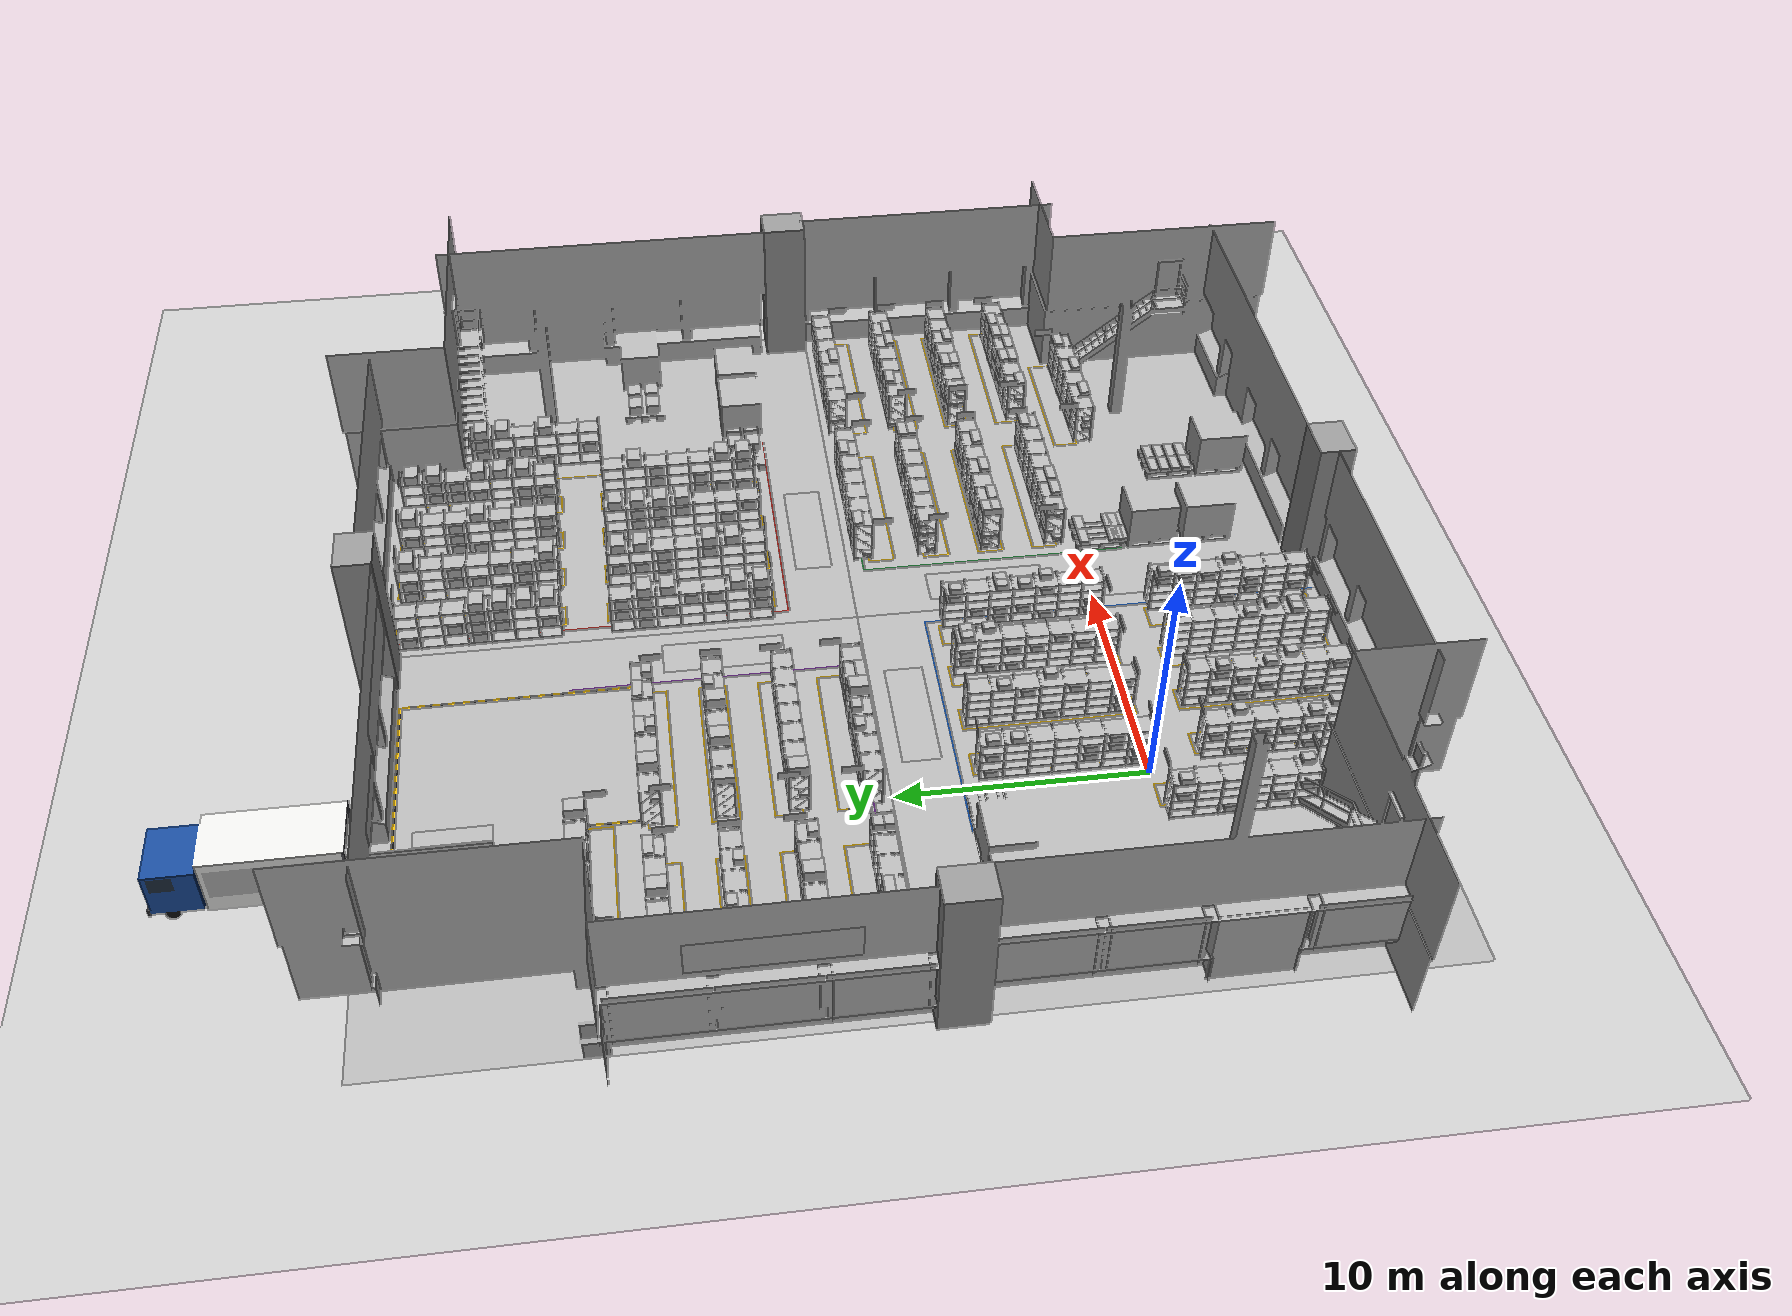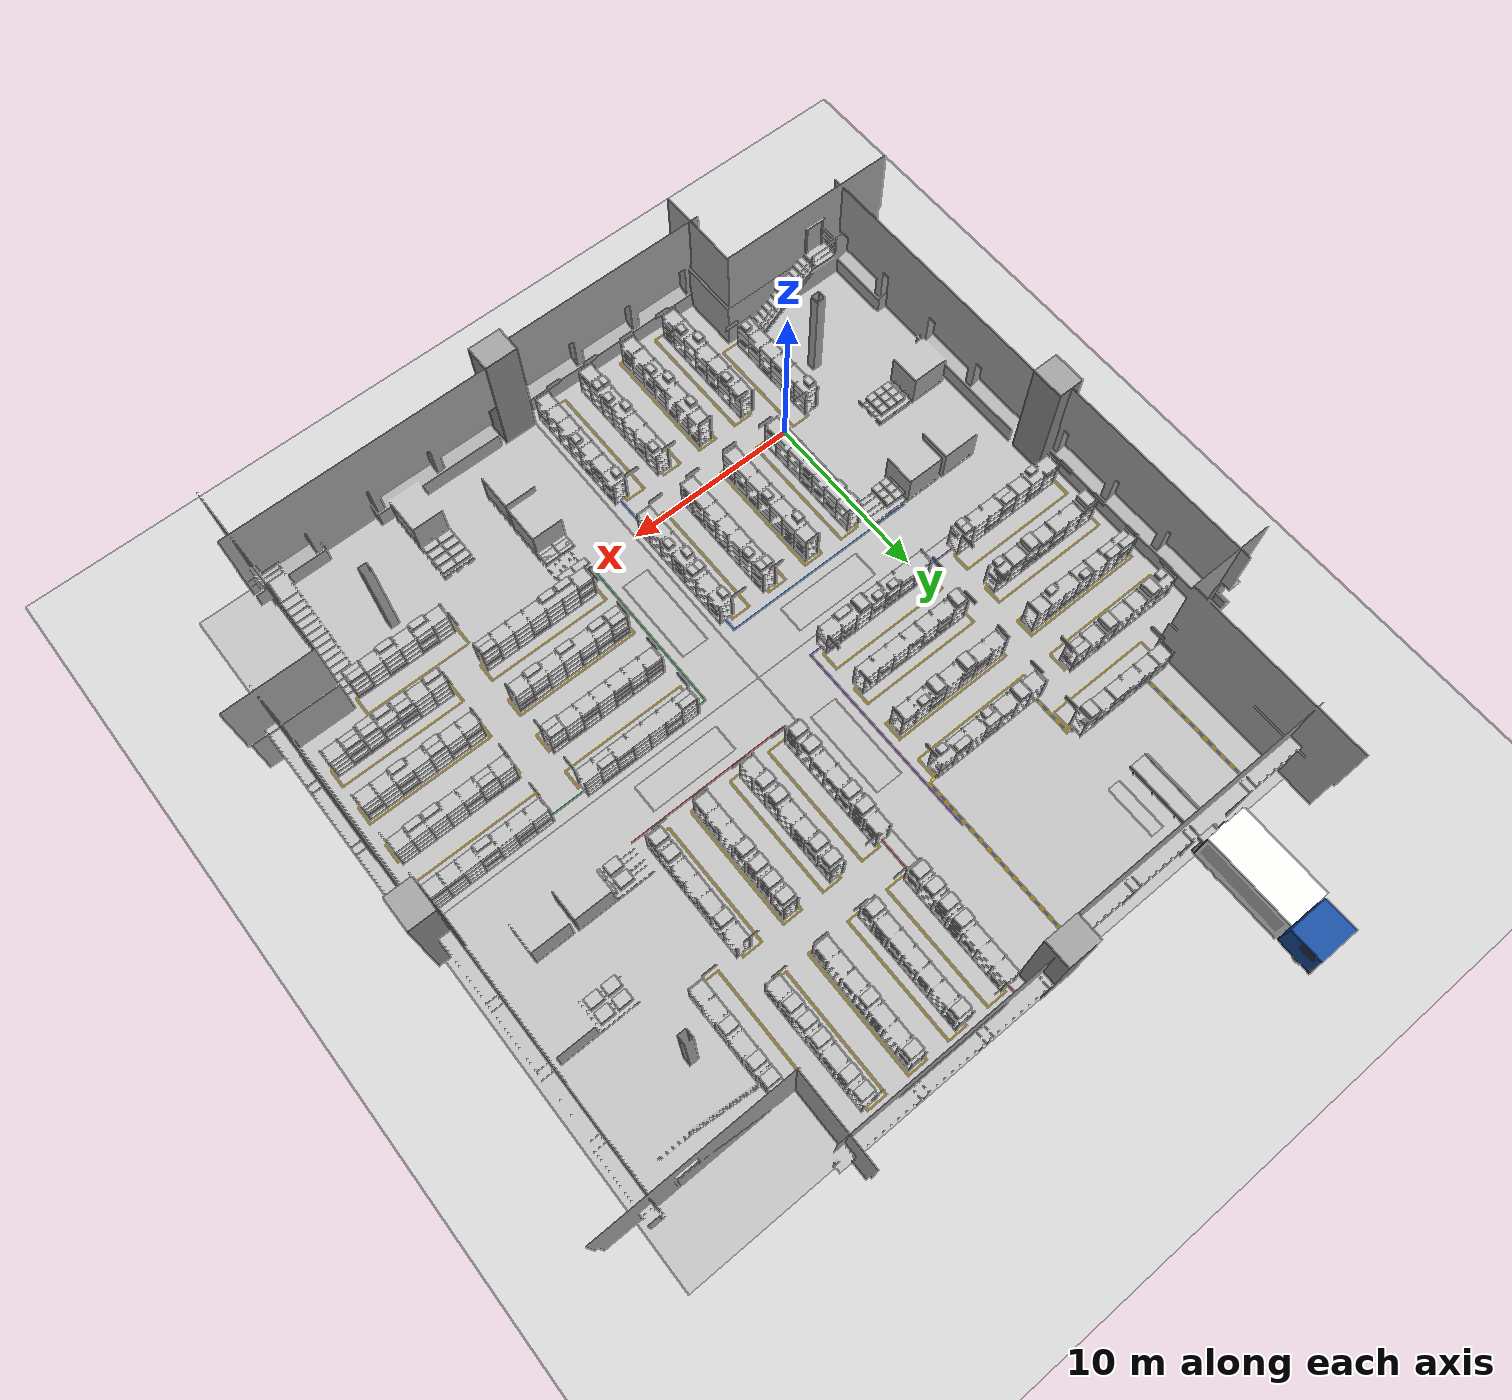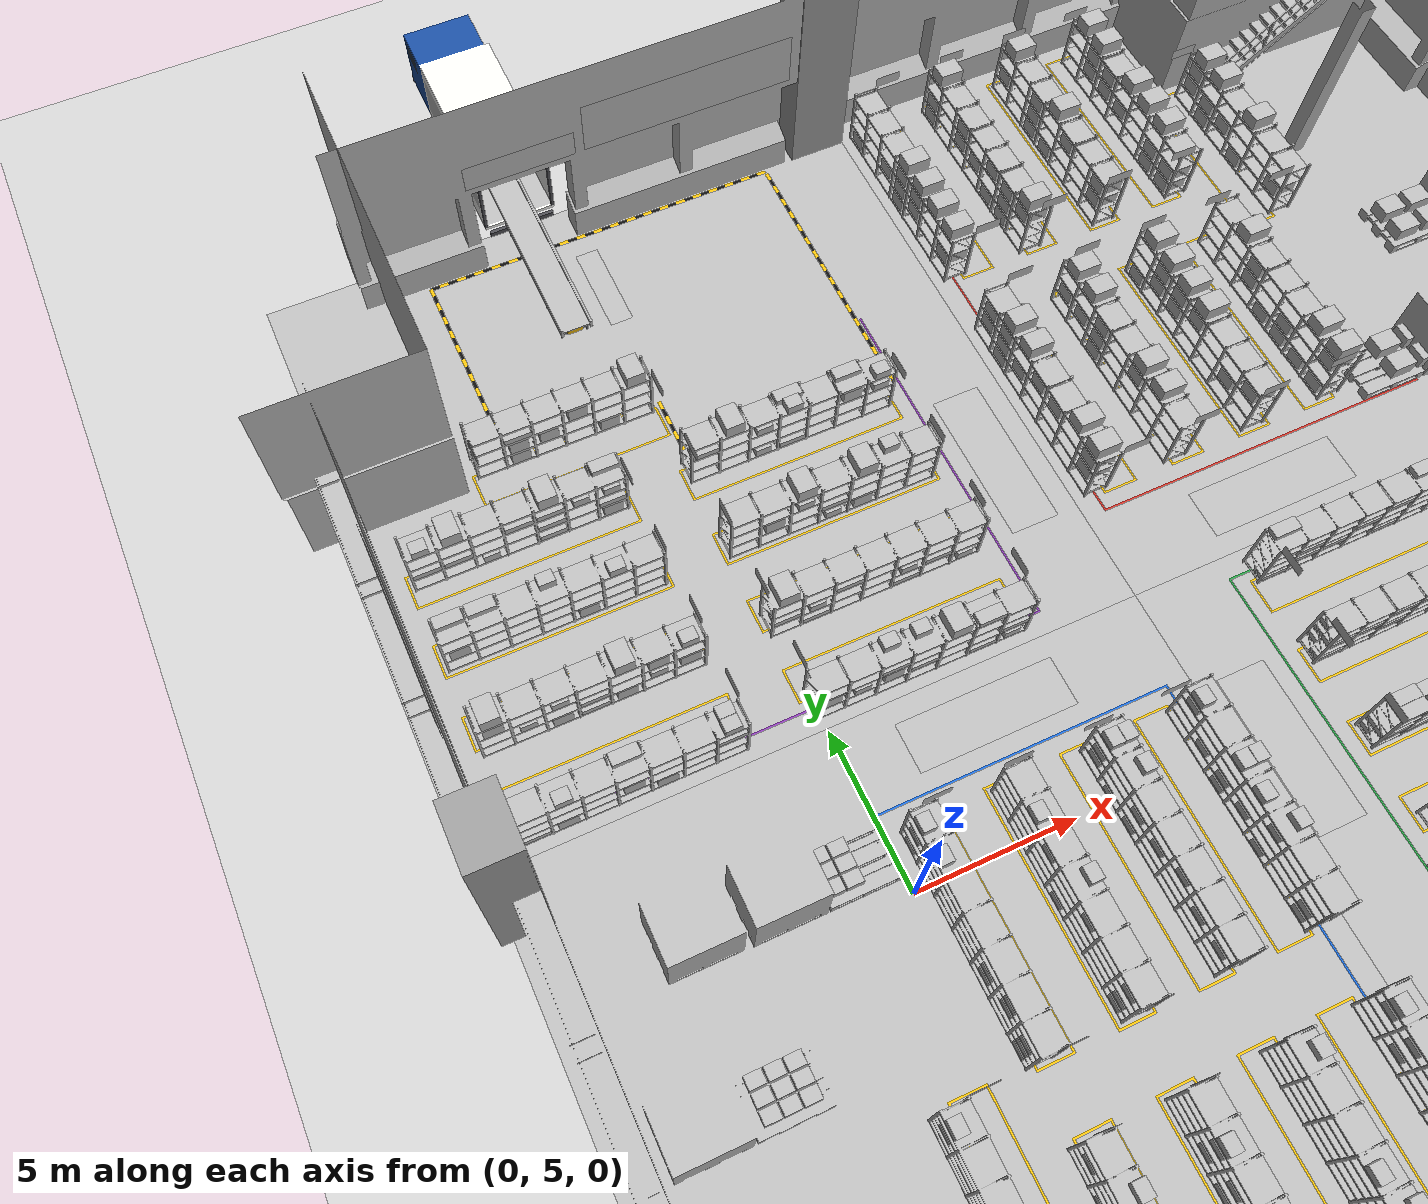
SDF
<?xml version="1.0" ?>
<sdf version='1.6'>
  <world name='default'>
    <light name='sun' type='directional'>
      <cast_shadows>1</cast_shadows>
      <pose frame=''>0 0 10 0 -0 0</pose>
      <diffuse>0.8 0.8 0.8 1</diffuse>
      <specular>0.2 0.2 0.2 1</specular>
      <attenuation>
        <range>1000</range>
        <constant>0.9</constant>
        <linear>0.01</linear>
        <quadratic>0.001</quadratic>
      </attenuation>
      <direction>-0.5 0.1 -0.9</direction>
    </light>
    <model name='ground_plane'>
      <static>1</static>
      <link name='link'>
        <collision name='collision'>
          <geometry>
            <plane>
              <normal>0 0 1</normal>
              <size>100 100</size>
            </plane>
          </geometry>
          <surface>
            <friction>
              <ode>
                <mu>100</mu>
                <mu2>50</mu2>
              </ode>
              <torsional>
                <ode/>
              </torsional>
            </friction>
            <contact>
              <ode/>
            </contact>
            <bounce/>
          </surface>
          <max_contacts>10</max_contacts>
        </collision>
        <visual name='visual'>
          <cast_shadows>0</cast_shadows>
          <geometry>
            <plane>
              <normal>0 0 1</normal>
              <size>100 100</size>
            </plane>
          </geometry>
          <material>
            <script>
              <uri>file://media/materials/scripts/gazebo.material</uri>
              <name>Gazebo/Grey</name>
            </script>
          </material>
        </visual>
        <self_collide>0</self_collide>
        <enable_wind>0</enable_wind>
        <kinematic>0</kinematic>
      </link>
    </model>
    <gravity>0 0 -9.8</gravity>
    <magnetic_field>6e-06 2.3e-05 -4.2e-05</magnetic_field>
    <atmosphere type='adiabatic'/>
    <physics name='default_physics' default='0' type='ode'>
      <max_step_size>0.001</max_step_size>
      <real_time_factor>1</real_time_factor>
      <real_time_update_rate>1000</real_time_update_rate>
    </physics>
    <scene>
      <ambient>0.4 0.4 0.4 1</ambient>
      <background>0.7 0.7 0.7 1</background>
      <shadows>0</shadows>
    </scene>
    <audio>
      <device>default</device>
    </audio>
    <wind/>
    <spherical_coordinates>
      <surface_model>EARTH_WGS84</surface_model>
      <latitude_deg>0</latitude_deg>
      <longitude_deg>0</longitude_deg>
      <elevation>0</elevation>
      <heading_deg>0</heading_deg>
    </spherical_coordinates>
        <!-- Zone A (small boxes): module SW -->
    <include>
      <name>zone_A_layout</name>
      <uri>model://zone_a_layout</uri>
      <pose>-0.040107 0.052292 0 0 0 0</pose>
    </include>
    <include>
      <name>rack_A1_0</name>
      <uri>model://warehouse_rack_5lvl_6bay</uri>
      <pose>-1.9401 -3.0477 0 0 0 0</pose>
    </include>
    <model name='box_A_001'>
      <pose>-1.7351 -5.4469 0.702 0 0 0</pose>
      <link name='link'>
        <inertial>
          <mass>2.0</mass>
          <inertia><ixx>0.05667</ixx><iyy>0.04167</iyy><izz>0.06833</izz><ixy>0</ixy><ixz>0</ixz><iyz>0</iyz></inertia>
        </inertial>
        <collision name='collision'>
          <geometry><box><size>0.4 0.5 0.3</size></box></geometry>
          <surface><friction><ode><mu>1.0</mu><mu2>1.0</mu2></ode></friction></surface>
        </collision>
        <visual name='visual'>
          <cast_shadows>0</cast_shadows>
          <geometry><box><size>0.4 0.5 0.3</size></box></geometry>
          <material><script>
            <uri>model://labeled_boxes/materials/scripts</uri>
            <uri>model://labeled_boxes/materials/textures</uri>
            <name>LabeledBox/A-001</name>
          </script></material>
        </visual>
      </link>
    </model>
    <model name='box_A_002'>
      <pose>-2.1451 -5.4469 1.152 0 0 0</pose>
      <link name='link'>
        <inertial>
          <mass>2.0</mass>
          <inertia><ixx>0.05667</ixx><iyy>0.04167</iyy><izz>0.06833</izz><ixy>0</ixy><ixz>0</ixz><iyz>0</iyz></inertia>
        </inertial>
        <collision name='collision'>
          <geometry><box><size>0.4 0.5 0.3</size></box></geometry>
          <surface><friction><ode><mu>1.0</mu><mu2>1.0</mu2></ode></friction></surface>
        </collision>
        <visual name='visual'>
          <cast_shadows>0</cast_shadows>
          <geometry><box><size>0.4 0.5 0.3</size></box></geometry>
          <material><script>
            <uri>model://labeled_boxes/materials/scripts</uri>
            <uri>model://labeled_boxes/materials/textures</uri>
            <name>LabeledBox/A-002</name>
          </script></material>
        </visual>
      </link>
    </model>
    <model name='box_A_003'>
      <pose>-1.7351 -5.4469 2.052 0 0 0</pose>
      <link name='link'>
        <inertial>
          <mass>2.0</mass>
          <inertia><ixx>0.05667</ixx><iyy>0.04167</iyy><izz>0.06833</izz><ixy>0</ixy><ixz>0</ixz><iyz>0</iyz></inertia>
        </inertial>
        <collision name='collision'>
          <geometry><box><size>0.4 0.5 0.3</size></box></geometry>
          <surface><friction><ode><mu>1.0</mu><mu2>1.0</mu2></ode></friction></surface>
        </collision>
        <visual name='visual'>
          <cast_shadows>0</cast_shadows>
          <geometry><box><size>0.4 0.5 0.3</size></box></geometry>
          <material><script>
            <uri>model://labeled_boxes/materials/scripts</uri>
            <uri>model://labeled_boxes/materials/textures</uri>
            <name>LabeledBox/A-003</name>
          </script></material>
        </visual>
      </link>
    </model>
    <model name='box_A_004'>
      <pose>-2.1451 -4.4977 0.702 0 0 0</pose>
      <link name='link'>
        <inertial>
          <mass>2.0</mass>
          <inertia><ixx>0.05667</ixx><iyy>0.04167</iyy><izz>0.06833</izz><ixy>0</ixy><ixz>0</ixz><iyz>0</iyz></inertia>
        </inertial>
        <collision name='collision'>
          <geometry><box><size>0.4 0.5 0.3</size></box></geometry>
          <surface><friction><ode><mu>1.0</mu><mu2>1.0</mu2></ode></friction></surface>
        </collision>
        <visual name='visual'>
          <cast_shadows>0</cast_shadows>
          <geometry><box><size>0.4 0.5 0.3</size></box></geometry>
          <material><script>
            <uri>model://labeled_boxes/materials/scripts</uri>
            <uri>model://labeled_boxes/materials/textures</uri>
            <name>LabeledBox/A-004</name>
          </script></material>
        </visual>
      </link>
    </model>
    <model name='box_A_005'>
      <pose>-1.7351 -4.4977 1.152 0 0 0</pose>
      <link name='link'>
        <inertial>
          <mass>2.0</mass>
          <inertia><ixx>0.05667</ixx><iyy>0.04167</iyy><izz>0.06833</izz><ixy>0</ixy><ixz>0</ixz><iyz>0</iyz></inertia>
        </inertial>
        <collision name='collision'>
          <geometry><box><size>0.4 0.5 0.3</size></box></geometry>
          <surface><friction><ode><mu>1.0</mu><mu2>1.0</mu2></ode></friction></surface>
        </collision>
        <visual name='visual'>
          <cast_shadows>0</cast_shadows>
          <geometry><box><size>0.4 0.5 0.3</size></box></geometry>
          <material><script>
            <uri>model://labeled_boxes/materials/scripts</uri>
            <uri>model://labeled_boxes/materials/textures</uri>
            <name>LabeledBox/A-005</name>
          </script></material>
        </visual>
      </link>
    </model>
    <model name='box_A_006'>
      <pose>-1.7351 -3.531 0.252 0 0 0</pose>
      <link name='link'>
        <inertial>
          <mass>2.0</mass>
          <inertia><ixx>0.05667</ixx><iyy>0.04167</iyy><izz>0.06833</izz><ixy>0</ixy><ixz>0</ixz><iyz>0</iyz></inertia>
        </inertial>
        <collision name='collision'>
          <geometry><box><size>0.4 0.5 0.3</size></box></geometry>
          <surface><friction><ode><mu>1.0</mu><mu2>1.0</mu2></ode></friction></surface>
        </collision>
        <visual name='visual'>
          <cast_shadows>0</cast_shadows>
          <geometry><box><size>0.4 0.5 0.3</size></box></geometry>
          <material><script>
            <uri>model://labeled_boxes/materials/scripts</uri>
            <uri>model://labeled_boxes/materials/textures</uri>
            <name>LabeledBox/A-006</name>
          </script></material>
        </visual>
      </link>
    </model>
    <model name='box_A_007'>
      <pose>-2.1451 -2.5644 0.252 0 0 0</pose>
      <link name='link'>
        <inertial>
          <mass>2.0</mass>
          <inertia><ixx>0.05667</ixx><iyy>0.04167</iyy><izz>0.06833</izz><ixy>0</ixy><ixz>0</ixz><iyz>0</iyz></inertia>
        </inertial>
        <collision name='collision'>
          <geometry><box><size>0.4 0.5 0.3</size></box></geometry>
          <surface><friction><ode><mu>1.0</mu><mu2>1.0</mu2></ode></friction></surface>
        </collision>
        <visual name='visual'>
          <cast_shadows>0</cast_shadows>
          <geometry><box><size>0.4 0.5 0.3</size></box></geometry>
          <material><script>
            <uri>model://labeled_boxes/materials/scripts</uri>
            <uri>model://labeled_boxes/materials/textures</uri>
            <name>LabeledBox/A-007</name>
          </script></material>
        </visual>
      </link>
    </model>
    <model name='box_A_008'>
      <pose>-1.7351 -2.5644 1.602 0 0 0</pose>
      <link name='link'>
        <inertial>
          <mass>2.0</mass>
          <inertia><ixx>0.05667</ixx><iyy>0.04167</iyy><izz>0.06833</izz><ixy>0</ixy><ixz>0</ixz><iyz>0</iyz></inertia>
        </inertial>
        <collision name='collision'>
          <geometry><box><size>0.4 0.5 0.3</size></box></geometry>
          <surface><friction><ode><mu>1.0</mu><mu2>1.0</mu2></ode></friction></surface>
        </collision>
        <visual name='visual'>
          <cast_shadows>0</cast_shadows>
          <geometry><box><size>0.4 0.5 0.3</size></box></geometry>
          <material><script>
            <uri>model://labeled_boxes/materials/scripts</uri>
            <uri>model://labeled_boxes/materials/textures</uri>
            <name>LabeledBox/A-008</name>
          </script></material>
        </visual>
      </link>
    </model>
    <model name='box_A_009'>
      <pose>-1.7351 -1.5977 0.252 0 0 0</pose>
      <link name='link'>
        <inertial>
          <mass>2.0</mass>
          <inertia><ixx>0.05667</ixx><iyy>0.04167</iyy><izz>0.06833</izz><ixy>0</ixy><ixz>0</ixz><iyz>0</iyz></inertia>
        </inertial>
        <collision name='collision'>
          <geometry><box><size>0.4 0.5 0.3</size></box></geometry>
          <surface><friction><ode><mu>1.0</mu><mu2>1.0</mu2></ode></friction></surface>
        </collision>
        <visual name='visual'>
          <cast_shadows>0</cast_shadows>
          <geometry><box><size>0.4 0.5 0.3</size></box></geometry>
          <material><script>
            <uri>model://labeled_boxes/materials/scripts</uri>
            <uri>model://labeled_boxes/materials/textures</uri>
            <name>LabeledBox/A-009</name>
          </script></material>
        </visual>
      </link>
    </model>
    <model name='box_A_010'>
      <pose>-1.7351 -1.5977 0.702 0 0 0</pose>
      <link name='link'>
        <inertial>
          <mass>2.0</mass>
          <inertia><ixx>0.05667</ixx><iyy>0.04167</iyy><izz>0.06833</izz><ixy>0</ixy><ixz>0</ixz><iyz>0</iyz></inertia>
        </inertial>
        <collision name='collision'>
          <geometry><box><size>0.4 0.5 0.3</size></box></geometry>
          <surface><friction><ode><mu>1.0</mu><mu2>1.0</mu2></ode></friction></surface>
        </collision>
        <visual name='visual'>
          <cast_shadows>0</cast_shadows>
          <geometry><box><size>0.4 0.5 0.3</size></box></geometry>
          <material><script>
            <uri>model://labeled_boxes/materials/scripts</uri>
            <uri>model://labeled_boxes/materials/textures</uri>
            <name>LabeledBox/A-010</name>
          </script></material>
        </visual>
      </link>
    </model>
    <model name='box_A_011'>
      <pose>-2.1451 -0.6485 1.152 0 0 0</pose>
      <link name='link'>
        <inertial>
          <mass>2.0</mass>
          <inertia><ixx>0.05667</ixx><iyy>0.04167</iyy><izz>0.06833</izz><ixy>0</ixy><ixz>0</ixz><iyz>0</iyz></inertia>
        </inertial>
        <collision name='collision'>
          <geometry><box><size>0.4 0.5 0.3</size></box></geometry>
          <surface><friction><ode><mu>1.0</mu><mu2>1.0</mu2></ode></friction></surface>
        </collision>
        <visual name='visual'>
          <cast_shadows>0</cast_shadows>
          <geometry><box><size>0.4 0.5 0.3</size></box></geometry>
          <material><script>
            <uri>model://labeled_boxes/materials/scripts</uri>
            <uri>model://labeled_boxes/materials/textures</uri>
            <name>LabeledBox/A-011</name>
          </script></material>
        </visual>
      </link>
    </model>
    <model name='box_A_012'>
      <pose>-2.1451 -0.6485 2.052 0 0 0</pose>
      <link name='link'>
        <inertial>
          <mass>2.0</mass>
          <inertia><ixx>0.05667</ixx><iyy>0.04167</iyy><izz>0.06833</izz><ixy>0</ixy><ixz>0</ixz><iyz>0</iyz></inertia>
        </inertial>
        <collision name='collision'>
          <geometry><box><size>0.4 0.5 0.3</size></box></geometry>
          <surface><friction><ode><mu>1.0</mu><mu2>1.0</mu2></ode></friction></surface>
        </collision>
        <visual name='visual'>
          <cast_shadows>0</cast_shadows>
          <geometry><box><size>0.4 0.5 0.3</size></box></geometry>
          <material><script>
            <uri>model://labeled_boxes/materials/scripts</uri>
            <uri>model://labeled_boxes/materials/textures</uri>
            <name>LabeledBox/A-012</name>
          </script></material>
        </visual>
      </link>
    </model>
    <include>
      <name>rack_A2_0</name>
      <uri>model://warehouse_rack_5lvl_7bay</uri>
      <pose>0.8599 -5.5477 0 0 0 0</pose>
    </include>
    <model name='box_A_013'>
      <pose>1.0649 -8.4445 0.252 0 0 0</pose>
      <link name='link'>
        <inertial>
          <mass>2.0</mass>
          <inertia><ixx>0.05667</ixx><iyy>0.04167</iyy><izz>0.06833</izz><ixy>0</ixy><ixz>0</ixz><iyz>0</iyz></inertia>
        </inertial>
        <collision name='collision'>
          <geometry><box><size>0.4 0.5 0.3</size></box></geometry>
          <surface><friction><ode><mu>1.0</mu><mu2>1.0</mu2></ode></friction></surface>
        </collision>
        <visual name='visual'>
          <cast_shadows>0</cast_shadows>
          <geometry><box><size>0.4 0.5 0.3</size></box></geometry>
          <material><script>
            <uri>model://labeled_boxes/materials/scripts</uri>
            <uri>model://labeled_boxes/materials/textures</uri>
            <name>LabeledBox/A-013</name>
          </script></material>
        </visual>
      </link>
    </model>
    <model name='box_A_014'>
      <pose>1.0649 -8.4445 0.702 0 0 0</pose>
      <link name='link'>
        <inertial>
          <mass>2.0</mass>
          <inertia><ixx>0.05667</ixx><iyy>0.04167</iyy><izz>0.06833</izz><ixy>0</ixy><ixz>0</ixz><iyz>0</iyz></inertia>
        </inertial>
        <collision name='collision'>
          <geometry><box><size>0.4 0.5 0.3</size></box></geometry>
          <surface><friction><ode><mu>1.0</mu><mu2>1.0</mu2></ode></friction></surface>
        </collision>
        <visual name='visual'>
          <cast_shadows>0</cast_shadows>
          <geometry><box><size>0.4 0.5 0.3</size></box></geometry>
          <material><script>
            <uri>model://labeled_boxes/materials/scripts</uri>
            <uri>model://labeled_boxes/materials/textures</uri>
            <name>LabeledBox/A-014</name>
          </script></material>
        </visual>
      </link>
    </model>
    <model name='box_A_015'>
      <pose>1.0649 -8.4445 1.152 0 0 0</pose>
      <link name='link'>
        <inertial>
          <mass>2.0</mass>
          <inertia><ixx>0.05667</ixx><iyy>0.04167</iyy><izz>0.06833</izz><ixy>0</ixy><ixz>0</ixz><iyz>0</iyz></inertia>
        </inertial>
        <collision name='collision'>
          <geometry><box><size>0.4 0.5 0.3</size></box></geometry>
          <surface><friction><ode><mu>1.0</mu><mu2>1.0</mu2></ode></friction></surface>
        </collision>
        <visual name='visual'>
          <cast_shadows>0</cast_shadows>
          <geometry><box><size>0.4 0.5 0.3</size></box></geometry>
          <material><script>
            <uri>model://labeled_boxes/materials/scripts</uri>
            <uri>model://labeled_boxes/materials/textures</uri>
            <name>LabeledBox/A-015</name>
          </script></material>
        </visual>
      </link>
    </model>
    <model name='box_A_016'>
      <pose>0.6549 -7.4906 1.152 0 0 0</pose>
      <link name='link'>
        <inertial>
          <mass>2.0</mass>
          <inertia><ixx>0.05667</ixx><iyy>0.04167</iyy><izz>0.06833</izz><ixy>0</ixy><ixz>0</ixz><iyz>0</iyz></inertia>
        </inertial>
        <collision name='collision'>
          <geometry><box><size>0.4 0.5 0.3</size></box></geometry>
          <surface><friction><ode><mu>1.0</mu><mu2>1.0</mu2></ode></friction></surface>
        </collision>
        <visual name='visual'>
          <cast_shadows>0</cast_shadows>
          <geometry><box><size>0.4 0.5 0.3</size></box></geometry>
          <material><script>
            <uri>model://labeled_boxes/materials/scripts</uri>
            <uri>model://labeled_boxes/materials/textures</uri>
            <name>LabeledBox/A-016</name>
          </script></material>
        </visual>
      </link>
    </model>
    <model name='box_A_017'>
      <pose>1.0649 -7.4906 2.052 0 0 0</pose>
      <link name='link'>
        <inertial>
          <mass>2.0</mass>
          <inertia><ixx>0.05667</ixx><iyy>0.04167</iyy><izz>0.06833</izz><ixy>0</ixy><ixz>0</ixz><iyz>0</iyz></inertia>
        </inertial>
        <collision name='collision'>
          <geometry><box><size>0.4 0.5 0.3</size></box></geometry>
          <surface><friction><ode><mu>1.0</mu><mu2>1.0</mu2></ode></friction></surface>
        </collision>
        <visual name='visual'>
          <cast_shadows>0</cast_shadows>
          <geometry><box><size>0.4 0.5 0.3</size></box></geometry>
          <material><script>
            <uri>model://labeled_boxes/materials/scripts</uri>
            <uri>model://labeled_boxes/materials/textures</uri>
            <name>LabeledBox/A-017</name>
          </script></material>
        </visual>
      </link>
    </model>
    <model name='box_A_018'>
      <pose>0.6549 -6.5191 0.252 0 0 0</pose>
      <link name='link'>
        <inertial>
          <mass>2.0</mass>
          <inertia><ixx>0.05667</ixx><iyy>0.04167</iyy><izz>0.06833</izz><ixy>0</ixy><ixz>0</ixz><iyz>0</iyz></inertia>
        </inertial>
        <collision name='collision'>
          <geometry><box><size>0.4 0.5 0.3</size></box></geometry>
          <surface><friction><ode><mu>1.0</mu><mu2>1.0</mu2></ode></friction></surface>
        </collision>
        <visual name='visual'>
          <cast_shadows>0</cast_shadows>
          <geometry><box><size>0.4 0.5 0.3</size></box></geometry>
          <material><script>
            <uri>model://labeled_boxes/materials/scripts</uri>
            <uri>model://labeled_boxes/materials/textures</uri>
            <name>LabeledBox/A-018</name>
          </script></material>
        </visual>
      </link>
    </model>
    <model name='box_A_019'>
      <pose>0.6549 -6.5191 1.152 0 0 0</pose>
      <link name='link'>
        <inertial>
          <mass>2.0</mass>
          <inertia><ixx>0.05667</ixx><iyy>0.04167</iyy><izz>0.06833</izz><ixy>0</ixy><ixz>0</ixz><iyz>0</iyz></inertia>
        </inertial>
        <collision name='collision'>
          <geometry><box><size>0.4 0.5 0.3</size></box></geometry>
          <surface><friction><ode><mu>1.0</mu><mu2>1.0</mu2></ode></friction></surface>
        </collision>
        <visual name='visual'>
          <cast_shadows>0</cast_shadows>
          <geometry><box><size>0.4 0.5 0.3</size></box></geometry>
          <material><script>
            <uri>model://labeled_boxes/materials/scripts</uri>
            <uri>model://labeled_boxes/materials/textures</uri>
            <name>LabeledBox/A-019</name>
          </script></material>
        </visual>
      </link>
    </model>
    <model name='box_A_020'>
      <pose>0.6549 -6.5191 2.052 0 0 0</pose>
      <link name='link'>
        <inertial>
          <mass>2.0</mass>
          <inertia><ixx>0.05667</ixx><iyy>0.04167</iyy><izz>0.06833</izz><ixy>0</ixy><ixz>0</ixz><iyz>0</iyz></inertia>
        </inertial>
        <collision name='collision'>
          <geometry><box><size>0.4 0.5 0.3</size></box></geometry>
          <surface><friction><ode><mu>1.0</mu><mu2>1.0</mu2></ode></friction></surface>
        </collision>
        <visual name='visual'>
          <cast_shadows>0</cast_shadows>
          <geometry><box><size>0.4 0.5 0.3</size></box></geometry>
          <material><script>
            <uri>model://labeled_boxes/materials/scripts</uri>
            <uri>model://labeled_boxes/materials/textures</uri>
            <name>LabeledBox/A-020</name>
          </script></material>
        </visual>
      </link>
    </model>
    <model name='box_A_021'>
      <pose>1.0649 -5.5477 0.702 0 0 0</pose>
      <link name='link'>
        <inertial>
          <mass>2.0</mass>
          <inertia><ixx>0.05667</ixx><iyy>0.04167</iyy><izz>0.06833</izz><ixy>0</ixy><ixz>0</ixz><iyz>0</iyz></inertia>
        </inertial>
        <collision name='collision'>
          <geometry><box><size>0.4 0.5 0.3</size></box></geometry>
          <surface><friction><ode><mu>1.0</mu><mu2>1.0</mu2></ode></friction></surface>
        </collision>
        <visual name='visual'>
          <cast_shadows>0</cast_shadows>
          <geometry><box><size>0.4 0.5 0.3</size></box></geometry>
          <material><script>
            <uri>model://labeled_boxes/materials/scripts</uri>
            <uri>model://labeled_boxes/materials/textures</uri>
            <name>LabeledBox/A-021</name>
          </script></material>
        </visual>
      </link>
    </model>
    <model name='box_A_022'>
      <pose>0.6549 -5.5477 1.152 0 0 0</pose>
      <link name='link'>
        <inertial>
          <mass>2.0</mass>
          <inertia><ixx>0.05667</ixx><iyy>0.04167</iyy><izz>0.06833</izz><ixy>0</ixy><ixz>0</ixz><iyz>0</iyz></inertia>
        </inertial>
        <collision name='collision'>
          <geometry><box><size>0.4 0.5 0.3</size></box></geometry>
          <surface><friction><ode><mu>1.0</mu><mu2>1.0</mu2></ode></friction></surface>
        </collision>
        <visual name='visual'>
          <cast_shadows>0</cast_shadows>
          <geometry><box><size>0.4 0.5 0.3</size></box></geometry>
          <material><script>
            <uri>model://labeled_boxes/materials/scripts</uri>
            <uri>model://labeled_boxes/materials/textures</uri>
            <name>LabeledBox/A-022</name>
          </script></material>
        </visual>
      </link>
    </model>
    <model name='box_A_023'>
      <pose>1.0649 -4.5763 0.252 0 0 0</pose>
      <link name='link'>
        <inertial>
          <mass>2.0</mass>
          <inertia><ixx>0.05667</ixx><iyy>0.04167</iyy><izz>0.06833</izz><ixy>0</ixy><ixz>0</ixz><iyz>0</iyz></inertia>
        </inertial>
        <collision name='collision'>
          <geometry><box><size>0.4 0.5 0.3</size></box></geometry>
          <surface><friction><ode><mu>1.0</mu><mu2>1.0</mu2></ode></friction></surface>
        </collision>
        <visual name='visual'>
          <cast_shadows>0</cast_shadows>
          <geometry><box><size>0.4 0.5 0.3</size></box></geometry>
          <material><script>
            <uri>model://labeled_boxes/materials/scripts</uri>
            <uri>model://labeled_boxes/materials/textures</uri>
            <name>LabeledBox/A-023</name>
          </script></material>
        </visual>
      </link>
    </model>
    <model name='box_A_024'>
      <pose>0.6549 -4.5763 1.152 0 0 0</pose>
      <link name='link'>
        <inertial>
          <mass>2.0</mass>
          <inertia><ixx>0.05667</ixx><iyy>0.04167</iyy><izz>0.06833</izz><ixy>0</ixy><ixz>0</ixz><iyz>0</iyz></inertia>
        </inertial>
        <collision name='collision'>
          <geometry><box><size>0.4 0.5 0.3</size></box></geometry>
          <surface><friction><ode><mu>1.0</mu><mu2>1.0</mu2></ode></friction></surface>
        </collision>
        <visual name='visual'>
          <cast_shadows>0</cast_shadows>
          <geometry><box><size>0.4 0.5 0.3</size></box></geometry>
          <material><script>
            <uri>model://labeled_boxes/materials/scripts</uri>
            <uri>model://labeled_boxes/materials/textures</uri>
            <name>LabeledBox/A-024</name>
          </script></material>
        </visual>
      </link>
    </model>
    <model name='box_A_025'>
      <pose>1.0649 -4.5763 1.602 0 0 0</pose>
      <link name='link'>
        <inertial>
          <mass>2.0</mass>
          <inertia><ixx>0.05667</ixx><iyy>0.04167</iyy><izz>0.06833</izz><ixy>0</ixy><ixz>0</ixz><iyz>0</iyz></inertia>
        </inertial>
        <collision name='collision'>
          <geometry><box><size>0.4 0.5 0.3</size></box></geometry>
          <surface><friction><ode><mu>1.0</mu><mu2>1.0</mu2></ode></friction></surface>
        </collision>
        <visual name='visual'>
          <cast_shadows>0</cast_shadows>
          <geometry><box><size>0.4 0.5 0.3</size></box></geometry>
          <material><script>
            <uri>model://labeled_boxes/materials/scripts</uri>
            <uri>model://labeled_boxes/materials/textures</uri>
            <name>LabeledBox/A-025</name>
          </script></material>
        </visual>
      </link>
    </model>
    <model name='box_A_026'>
      <pose>0.6549 -3.6049 0.252 0 0 0</pose>
      <link name='link'>
        <inertial>
          <mass>2.0</mass>
          <inertia><ixx>0.05667</ixx><iyy>0.04167</iyy><izz>0.06833</izz><ixy>0</ixy><ixz>0</ixz><iyz>0</iyz></inertia>
        </inertial>
        <collision name='collision'>
          <geometry><box><size>0.4 0.5 0.3</size></box></geometry>
          <surface><friction><ode><mu>1.0</mu><mu2>1.0</mu2></ode></friction></surface>
        </collision>
        <visual name='visual'>
          <cast_shadows>0</cast_shadows>
          <geometry><box><size>0.4 0.5 0.3</size></box></geometry>
          <material><script>
            <uri>model://labeled_boxes/materials/scripts</uri>
            <uri>model://labeled_boxes/materials/textures</uri>
            <name>LabeledBox/A-026</name>
          </script></material>
        </visual>
      </link>
    </model>
    <model name='box_A_027'>
      <pose>1.0649 -3.6049 1.602 0 0 0</pose>
      <link name='link'>
        <inertial>
          <mass>2.0</mass>
          <inertia><ixx>0.05667</ixx><iyy>0.04167</iyy><izz>0.06833</izz><ixy>0</ixy><ixz>0</ixz><iyz>0</iyz></inertia>
        </inertial>
        <collision name='collision'>
          <geometry><box><size>0.4 0.5 0.3</size></box></geometry>
          <surface><friction><ode><mu>1.0</mu><mu2>1.0</mu2></ode></friction></surface>
        </collision>
        <visual name='visual'>
          <cast_shadows>0</cast_shadows>
          <geometry><box><size>0.4 0.5 0.3</size></box></geometry>
          <material><script>
            <uri>model://labeled_boxes/materials/scripts</uri>
            <uri>model://labeled_boxes/materials/textures</uri>
            <name>LabeledBox/A-027</name>
          </script></material>
        </visual>
      </link>
    </model>
    <model name='box_A_028'>
      <pose>1.0649 -3.6049 2.052 0 0 0</pose>
      <link name='link'>
        <inertial>
          <mass>2.0</mass>
          <inertia><ixx>0.05667</ixx><iyy>0.04167</iyy><izz>0.06833</izz><ixy>0</ixy><ixz>0</ixz><iyz>0</iyz></inertia>
        </inertial>
        <collision name='collision'>
          <geometry><box><size>0.4 0.5 0.3</size></box></geometry>
          <surface><friction><ode><mu>1.0</mu><mu2>1.0</mu2></ode></friction></surface>
        </collision>
        <visual name='visual'>
          <cast_shadows>0</cast_shadows>
          <geometry><box><size>0.4 0.5 0.3</size></box></geometry>
          <material><script>
            <uri>model://labeled_boxes/materials/scripts</uri>
            <uri>model://labeled_boxes/materials/textures</uri>
            <name>LabeledBox/A-028</name>
          </script></material>
        </visual>
      </link>
    </model>
    <model name='box_A_029'>
      <pose>0.6549 -2.6509 1.152 0 0 0</pose>
      <link name='link'>
        <inertial>
          <mass>2.0</mass>
          <inertia><ixx>0.05667</ixx><iyy>0.04167</iyy><izz>0.06833</izz><ixy>0</ixy><ixz>0</ixz><iyz>0</iyz></inertia>
        </inertial>
        <collision name='collision'>
          <geometry><box><size>0.4 0.5 0.3</size></box></geometry>
          <surface><friction><ode><mu>1.0</mu><mu2>1.0</mu2></ode></friction></surface>
        </collision>
        <visual name='visual'>
          <cast_shadows>0</cast_shadows>
          <geometry><box><size>0.4 0.5 0.3</size></box></geometry>
          <material><script>
            <uri>model://labeled_boxes/materials/scripts</uri>
            <uri>model://labeled_boxes/materials/textures</uri>
            <name>LabeledBox/A-029</name>
          </script></material>
        </visual>
      </link>
    </model>
    <model name='box_A_030'>
      <pose>1.0649 -2.6509 1.602 0 0 0</pose>
      <link name='link'>
        <inertial>
          <mass>2.0</mass>
          <inertia><ixx>0.05667</ixx><iyy>0.04167</iyy><izz>0.06833</izz><ixy>0</ixy><ixz>0</ixz><iyz>0</iyz></inertia>
        </inertial>
        <collision name='collision'>
          <geometry><box><size>0.4 0.5 0.3</size></box></geometry>
          <surface><friction><ode><mu>1.0</mu><mu2>1.0</mu2></ode></friction></surface>
        </collision>
        <visual name='visual'>
          <cast_shadows>0</cast_shadows>
          <geometry><box><size>0.4 0.5 0.3</size></box></geometry>
          <material><script>
            <uri>model://labeled_boxes/materials/scripts</uri>
            <uri>model://labeled_boxes/materials/textures</uri>
            <name>LabeledBox/A-030</name>
          </script></material>
        </visual>
      </link>
    </model>
    <include>
      <name>rack_A2_1</name>
      <uri>model://warehouse_rack_5lvl_7bay</uri>
      <pose>0.8599 3.2523 0 0 0 0</pose>
    </include>
    <model name='box_A_031'>
      <pose>0.6549 0.3555 0.252 0 0 0</pose>
      <link name='link'>
        <inertial>
          <mass>2.0</mass>
          <inertia><ixx>0.05667</ixx><iyy>0.04167</iyy><izz>0.06833</izz><ixy>0</ixy><ixz>0</ixz><iyz>0</iyz></inertia>
        </inertial>
        <collision name='collision'>
          <geometry><box><size>0.4 0.5 0.3</size></box></geometry>
          <surface><friction><ode><mu>1.0</mu><mu2>1.0</mu2></ode></friction></surface>
        </collision>
        <visual name='visual'>
          <cast_shadows>0</cast_shadows>
          <geometry><box><size>0.4 0.5 0.3</size></box></geometry>
          <material><script>
            <uri>model://labeled_boxes/materials/scripts</uri>
            <uri>model://labeled_boxes/materials/textures</uri>
            <name>LabeledBox/A-031</name>
          </script></material>
        </visual>
      </link>
    </model>
    <model name='box_A_032'>
      <pose>0.6549 0.3555 0.702 0 0 0</pose>
      <link name='link'>
        <inertial>
          <mass>2.0</mass>
          <inertia><ixx>0.05667</ixx><iyy>0.04167</iyy><izz>0.06833</izz><ixy>0</ixy><ixz>0</ixz><iyz>0</iyz></inertia>
        </inertial>
        <collision name='collision'>
          <geometry><box><size>0.4 0.5 0.3</size></box></geometry>
          <surface><friction><ode><mu>1.0</mu><mu2>1.0</mu2></ode></friction></surface>
        </collision>
        <visual name='visual'>
          <cast_shadows>0</cast_shadows>
          <geometry><box><size>0.4 0.5 0.3</size></box></geometry>
          <material><script>
            <uri>model://labeled_boxes/materials/scripts</uri>
            <uri>model://labeled_boxes/materials/textures</uri>
            <name>LabeledBox/A-032</name>
          </script></material>
        </visual>
      </link>
    </model>
    <model name='box_A_033'>
      <pose>0.6549 0.3555 1.152 0 0 0</pose>
      <link name='link'>
        <inertial>
          <mass>2.0</mass>
          <inertia><ixx>0.05667</ixx><iyy>0.04167</iyy><izz>0.06833</izz><ixy>0</ixy><ixz>0</ixz><iyz>0</iyz></inertia>
        </inertial>
        <collision name='collision'>
          <geometry><box><size>0.4 0.5 0.3</size></box></geometry>
          <surface><friction><ode><mu>1.0</mu><mu2>1.0</mu2></ode></friction></surface>
        </collision>
        <visual name='visual'>
          <cast_shadows>0</cast_shadows>
          <geometry><box><size>0.4 0.5 0.3</size></box></geometry>
          <material><script>
            <uri>model://labeled_boxes/materials/scripts</uri>
            <uri>model://labeled_boxes/materials/textures</uri>
            <name>LabeledBox/A-033</name>
          </script></material>
        </visual>
      </link>
    </model>
    <model name='box_A_034'>
      <pose>1.0649 0.3555 1.602 0 0 0</pose>
      <link name='link'>
        <inertial>
          <mass>2.0</mass>
          <inertia><ixx>0.05667</ixx><iyy>0.04167</iyy><izz>0.06833</izz><ixy>0</ixy><ixz>0</ixz><iyz>0</iyz></inertia>
        </inertial>
        <collision name='collision'>
          <geometry><box><size>0.4 0.5 0.3</size></box></geometry>
          <surface><friction><ode><mu>1.0</mu><mu2>1.0</mu2></ode></friction></surface>
        </collision>
        <visual name='visual'>
          <cast_shadows>0</cast_shadows>
          <geometry><box><size>0.4 0.5 0.3</size></box></geometry>
          <material><script>
            <uri>model://labeled_boxes/materials/scripts</uri>
            <uri>model://labeled_boxes/materials/textures</uri>
            <name>LabeledBox/A-034</name>
          </script></material>
        </visual>
      </link>
    </model>
    <model name='box_A_035'>
      <pose>0.6549 1.3094 1.152 0 0 0</pose>
      <link name='link'>
        <inertial>
          <mass>2.0</mass>
          <inertia><ixx>0.05667</ixx><iyy>0.04167</iyy><izz>0.06833</izz><ixy>0</ixy><ixz>0</ixz><iyz>0</iyz></inertia>
        </inertial>
        <collision name='collision'>
          <geometry><box><size>0.4 0.5 0.3</size></box></geometry>
          <surface><friction><ode><mu>1.0</mu><mu2>1.0</mu2></ode></friction></surface>
        </collision>
        <visual name='visual'>
          <cast_shadows>0</cast_shadows>
          <geometry><box><size>0.4 0.5 0.3</size></box></geometry>
          <material><script>
            <uri>model://labeled_boxes/materials/scripts</uri>
            <uri>model://labeled_boxes/materials/textures</uri>
            <name>LabeledBox/A-035</name>
          </script></material>
        </visual>
      </link>
    </model>
    <model name='box_A_036'>
      <pose>0.6549 1.3094 1.602 0 0 0</pose>
      <link name='link'>
        <inertial>
          <mass>2.0</mass>
          <inertia><ixx>0.05667</ixx><iyy>0.04167</iyy><izz>0.06833</izz><ixy>0</ixy><ixz>0</ixz><iyz>0</iyz></inertia>
        </inertial>
        <collision name='collision'>
          <geometry><box><size>0.4 0.5 0.3</size></box></geometry>
          <surface><friction><ode><mu>1.0</mu><mu2>1.0</mu2></ode></friction></surface>
        </collision>
        <visual name='visual'>
          <cast_shadows>0</cast_shadows>
          <geometry><box><size>0.4 0.5 0.3</size></box></geometry>
          <material><script>
            <uri>model://labeled_boxes/materials/scripts</uri>
            <uri>model://labeled_boxes/materials/textures</uri>
            <name>LabeledBox/A-036</name>
          </script></material>
        </visual>
      </link>
    </model>
    <model name='box_A_037'>
      <pose>0.6549 2.2809 0.702 0 0 0</pose>
      <link name='link'>
        <inertial>
          <mass>2.0</mass>
          <inertia><ixx>0.05667</ixx><iyy>0.04167</iyy><izz>0.06833</izz><ixy>0</ixy><ixz>0</ixz><iyz>0</iyz></inertia>
        </inertial>
        <collision name='collision'>
          <geometry><box><size>0.4 0.5 0.3</size></box></geometry>
          <surface><friction><ode><mu>1.0</mu><mu2>1.0</mu2></ode></friction></surface>
        </collision>
        <visual name='visual'>
          <cast_shadows>0</cast_shadows>
          <geometry><box><size>0.4 0.5 0.3</size></box></geometry>
          <material><script>
            <uri>model://labeled_boxes/materials/scripts</uri>
            <uri>model://labeled_boxes/materials/textures</uri>
            <name>LabeledBox/A-037</name>
          </script></material>
        </visual>
      </link>
    </model>
    <model name='box_A_038'>
      <pose>0.6549 2.2809 1.152 0 0 0</pose>
      <link name='link'>
        <inertial>
          <mass>2.0</mass>
          <inertia><ixx>0.05667</ixx><iyy>0.04167</iyy><izz>0.06833</izz><ixy>0</ixy><ixz>0</ixz><iyz>0</iyz></inertia>
        </inertial>
        <collision name='collision'>
          <geometry><box><size>0.4 0.5 0.3</size></box></geometry>
          <surface><friction><ode><mu>1.0</mu><mu2>1.0</mu2></ode></friction></surface>
        </collision>
        <visual name='visual'>
          <cast_shadows>0</cast_shadows>
          <geometry><box><size>0.4 0.5 0.3</size></box></geometry>
          <material><script>
            <uri>model://labeled_boxes/materials/scripts</uri>
            <uri>model://labeled_boxes/materials/textures</uri>
            <name>LabeledBox/A-038</name>
          </script></material>
        </visual>
      </link>
    </model>
    <model name='box_A_039'>
      <pose>1.0649 3.2523 0.252 0 0 0</pose>
      <link name='link'>
        <inertial>
          <mass>2.0</mass>
          <inertia><ixx>0.05667</ixx><iyy>0.04167</iyy><izz>0.06833</izz><ixy>0</ixy><ixz>0</ixz><iyz>0</iyz></inertia>
        </inertial>
        <collision name='collision'>
          <geometry><box><size>0.4 0.5 0.3</size></box></geometry>
          <surface><friction><ode><mu>1.0</mu><mu2>1.0</mu2></ode></friction></surface>
        </collision>
        <visual name='visual'>
          <cast_shadows>0</cast_shadows>
          <geometry><box><size>0.4 0.5 0.3</size></box></geometry>
          <material><script>
            <uri>model://labeled_boxes/materials/scripts</uri>
            <uri>model://labeled_boxes/materials/textures</uri>
            <name>LabeledBox/A-039</name>
          </script></material>
        </visual>
      </link>
    </model>
    <model name='box_A_040'>
      <pose>1.0649 3.2523 1.152 0 0 0</pose>
      <link name='link'>
        <inertial>
          <mass>2.0</mass>
          <inertia><ixx>0.05667</ixx><iyy>0.04167</iyy><izz>0.06833</izz><ixy>0</ixy><ixz>0</ixz><iyz>0</iyz></inertia>
        </inertial>
        <collision name='collision'>
          <geometry><box><size>0.4 0.5 0.3</size></box></geometry>
          <surface><friction><ode><mu>1.0</mu><mu2>1.0</mu2></ode></friction></surface>
        </collision>
        <visual name='visual'>
          <cast_shadows>0</cast_shadows>
          <geometry><box><size>0.4 0.5 0.3</size></box></geometry>
          <material><script>
            <uri>model://labeled_boxes/materials/scripts</uri>
            <uri>model://labeled_boxes/materials/textures</uri>
            <name>LabeledBox/A-040</name>
          </script></material>
        </visual>
      </link>
    </model>
    <model name='box_A_041'>
      <pose>1.0649 3.2523 1.602 0 0 0</pose>
      <link name='link'>
        <inertial>
          <mass>2.0</mass>
          <inertia><ixx>0.05667</ixx><iyy>0.04167</iyy><izz>0.06833</izz><ixy>0</ixy><ixz>0</ixz><iyz>0</iyz></inertia>
        </inertial>
        <collision name='collision'>
          <geometry><box><size>0.4 0.5 0.3</size></box></geometry>
          <surface><friction><ode><mu>1.0</mu><mu2>1.0</mu2></ode></friction></surface>
        </collision>
        <visual name='visual'>
          <cast_shadows>0</cast_shadows>
          <geometry><box><size>0.4 0.5 0.3</size></box></geometry>
          <material><script>
            <uri>model://labeled_boxes/materials/scripts</uri>
            <uri>model://labeled_boxes/materials/textures</uri>
            <name>LabeledBox/A-041</name>
          </script></material>
        </visual>
      </link>
    </model>
    <model name='box_A_042'>
      <pose>1.0649 4.2237 0.702 0 0 0</pose>
      <link name='link'>
        <inertial>
          <mass>2.0</mass>
          <inertia><ixx>0.05667</ixx><iyy>0.04167</iyy><izz>0.06833</izz><ixy>0</ixy><ixz>0</ixz><iyz>0</iyz></inertia>
        </inertial>
        <collision name='collision'>
          <geometry><box><size>0.4 0.5 0.3</size></box></geometry>
          <surface><friction><ode><mu>1.0</mu><mu2>1.0</mu2></ode></friction></surface>
        </collision>
        <visual name='visual'>
          <cast_shadows>0</cast_shadows>
          <geometry><box><size>0.4 0.5 0.3</size></box></geometry>
          <material><script>
            <uri>model://labeled_boxes/materials/scripts</uri>
            <uri>model://labeled_boxes/materials/textures</uri>
            <name>LabeledBox/A-042</name>
          </script></material>
        </visual>
      </link>
    </model>
    <model name='box_A_043'>
      <pose>1.0649 5.1951 0.702 0 0 0</pose>
      <link name='link'>
        <inertial>
          <mass>2.0</mass>
          <inertia><ixx>0.05667</ixx><iyy>0.04167</iyy><izz>0.06833</izz><ixy>0</ixy><ixz>0</ixz><iyz>0</iyz></inertia>
        </inertial>
        <collision name='collision'>
          <geometry><box><size>0.4 0.5 0.3</size></box></geometry>
          <surface><friction><ode><mu>1.0</mu><mu2>1.0</mu2></ode></friction></surface>
        </collision>
        <visual name='visual'>
          <cast_shadows>0</cast_shadows>
          <geometry><box><size>0.4 0.5 0.3</size></box></geometry>
          <material><script>
            <uri>model://labeled_boxes/materials/scripts</uri>
            <uri>model://labeled_boxes/materials/textures</uri>
            <name>LabeledBox/A-043</name>
          </script></material>
        </visual>
      </link>
    </model>
    <model name='box_A_044'>
      <pose>0.6549 5.1951 2.052 0 0 0</pose>
      <link name='link'>
        <inertial>
          <mass>2.0</mass>
          <inertia><ixx>0.05667</ixx><iyy>0.04167</iyy><izz>0.06833</izz><ixy>0</ixy><ixz>0</ixz><iyz>0</iyz></inertia>
        </inertial>
        <collision name='collision'>
          <geometry><box><size>0.4 0.5 0.3</size></box></geometry>
          <surface><friction><ode><mu>1.0</mu><mu2>1.0</mu2></ode></friction></surface>
        </collision>
        <visual name='visual'>
          <cast_shadows>0</cast_shadows>
          <geometry><box><size>0.4 0.5 0.3</size></box></geometry>
          <material><script>
            <uri>model://labeled_boxes/materials/scripts</uri>
            <uri>model://labeled_boxes/materials/textures</uri>
            <name>LabeledBox/A-044</name>
          </script></material>
        </visual>
      </link>
    </model>
    <model name='box_A_045'>
      <pose>0.6549 6.1491 0.252 0 0 0</pose>
      <link name='link'>
        <inertial>
          <mass>2.0</mass>
          <inertia><ixx>0.05667</ixx><iyy>0.04167</iyy><izz>0.06833</izz><ixy>0</ixy><ixz>0</ixz><iyz>0</iyz></inertia>
        </inertial>
        <collision name='collision'>
          <geometry><box><size>0.4 0.5 0.3</size></box></geometry>
          <surface><friction><ode><mu>1.0</mu><mu2>1.0</mu2></ode></friction></surface>
        </collision>
        <visual name='visual'>
          <cast_shadows>0</cast_shadows>
          <geometry><box><size>0.4 0.5 0.3</size></box></geometry>
          <material><script>
            <uri>model://labeled_boxes/materials/scripts</uri>
            <uri>model://labeled_boxes/materials/textures</uri>
            <name>LabeledBox/A-045</name>
          </script></material>
        </visual>
      </link>
    </model>
    <model name='box_A_046'>
      <pose>0.6549 6.1491 1.152 0 0 0</pose>
      <link name='link'>
        <inertial>
          <mass>2.0</mass>
          <inertia><ixx>0.05667</ixx><iyy>0.04167</iyy><izz>0.06833</izz><ixy>0</ixy><ixz>0</ixz><iyz>0</iyz></inertia>
        </inertial>
        <collision name='collision'>
          <geometry><box><size>0.4 0.5 0.3</size></box></geometry>
          <surface><friction><ode><mu>1.0</mu><mu2>1.0</mu2></ode></friction></surface>
        </collision>
        <visual name='visual'>
          <cast_shadows>0</cast_shadows>
          <geometry><box><size>0.4 0.5 0.3</size></box></geometry>
          <material><script>
            <uri>model://labeled_boxes/materials/scripts</uri>
            <uri>model://labeled_boxes/materials/textures</uri>
            <name>LabeledBox/A-046</name>
          </script></material>
        </visual>
      </link>
    </model>
    <model name='box_A_047'>
      <pose>0.6549 6.1491 2.052 0 0 0</pose>
      <link name='link'>
        <inertial>
          <mass>2.0</mass>
          <inertia><ixx>0.05667</ixx><iyy>0.04167</iyy><izz>0.06833</izz><ixy>0</ixy><ixz>0</ixz><iyz>0</iyz></inertia>
        </inertial>
        <collision name='collision'>
          <geometry><box><size>0.4 0.5 0.3</size></box></geometry>
          <surface><friction><ode><mu>1.0</mu><mu2>1.0</mu2></ode></friction></surface>
        </collision>
        <visual name='visual'>
          <cast_shadows>0</cast_shadows>
          <geometry><box><size>0.4 0.5 0.3</size></box></geometry>
          <material><script>
            <uri>model://labeled_boxes/materials/scripts</uri>
            <uri>model://labeled_boxes/materials/textures</uri>
            <name>LabeledBox/A-047</name>
          </script></material>
        </visual>
      </link>
    </model>
    <include>
      <name>rack_A3_0</name>
      <uri>model://warehouse_rack_5lvl_7bay</uri>
      <pose>3.6599 -5.5477 0 0 0 0</pose>
    </include>
    <model name='box_A_048'>
      <pose>3.8649 -8.4445 0.702 0 0 0</pose>
      <link name='link'>
        <inertial>
          <mass>2.0</mass>
          <inertia><ixx>0.05667</ixx><iyy>0.04167</iyy><izz>0.06833</izz><ixy>0</ixy><ixz>0</ixz><iyz>0</iyz></inertia>
        </inertial>
        <collision name='collision'>
          <geometry><box><size>0.4 0.5 0.3</size></box></geometry>
          <surface><friction><ode><mu>1.0</mu><mu2>1.0</mu2></ode></friction></surface>
        </collision>
        <visual name='visual'>
          <cast_shadows>0</cast_shadows>
          <geometry><box><size>0.4 0.5 0.3</size></box></geometry>
          <material><script>
            <uri>model://labeled_boxes/materials/scripts</uri>
            <uri>model://labeled_boxes/materials/textures</uri>
            <name>LabeledBox/A-048</name>
          </script></material>
        </visual>
      </link>
    </model>
    <model name='box_A_049'>
      <pose>3.8649 -8.4445 1.152 0 0 0</pose>
      <link name='link'>
        <inertial>
          <mass>2.0</mass>
          <inertia><ixx>0.05667</ixx><iyy>0.04167</iyy><izz>0.06833</izz><ixy>0</ixy><ixz>0</ixz><iyz>0</iyz></inertia>
        </inertial>
        <collision name='collision'>
          <geometry><box><size>0.4 0.5 0.3</size></box></geometry>
          <surface><friction><ode><mu>1.0</mu><mu2>1.0</mu2></ode></friction></surface>
        </collision>
        <visual name='visual'>
          <cast_shadows>0</cast_shadows>
          <geometry><box><size>0.4 0.5 0.3</size></box></geometry>
          <material><script>
            <uri>model://labeled_boxes/materials/scripts</uri>
            <uri>model://labeled_boxes/materials/textures</uri>
            <name>LabeledBox/A-049</name>
          </script></material>
        </visual>
      </link>
    </model>
    <model name='box_A_050'>
      <pose>3.4549 -8.4445 1.602 0 0 0</pose>
      <link name='link'>
        <inertial>
          <mass>2.0</mass>
          <inertia><ixx>0.05667</ixx><iyy>0.04167</iyy><izz>0.06833</izz><ixy>0</ixy><ixz>0</ixz><iyz>0</iyz></inertia>
        </inertial>
        <collision name='collision'>
          <geometry><box><size>0.4 0.5 0.3</size></box></geometry>
          <surface><friction><ode><mu>1.0</mu><mu2>1.0</mu2></ode></friction></surface>
        </collision>
        <visual name='visual'>
          <cast_shadows>0</cast_shadows>
          <geometry><box><size>0.4 0.5 0.3</size></box></geometry>
          <material><script>
            <uri>model://labeled_boxes/materials/scripts</uri>
            <uri>model://labeled_boxes/materials/textures</uri>
            <name>LabeledBox/A-050</name>
          </script></material>
        </visual>
      </link>
    </model>
    <model name='box_A_051'>
      <pose>3.4549 -7.4906 0.252 0 0 0</pose>
      <link name='link'>
        <inertial>
          <mass>2.0</mass>
          <inertia><ixx>0.05667</ixx><iyy>0.04167</iyy><izz>0.06833</izz><ixy>0</ixy><ixz>0</ixz><iyz>0</iyz></inertia>
        </inertial>
        <collision name='collision'>
          <geometry><box><size>0.4 0.5 0.3</size></box></geometry>
          <surface><friction><ode><mu>1.0</mu><mu2>1.0</mu2></ode></friction></surface>
        </collision>
        <visual name='visual'>
          <cast_shadows>0</cast_shadows>
          <geometry><box><size>0.4 0.5 0.3</size></box></geometry>
          <material><script>
            <uri>model://labeled_boxes/materials/scripts</uri>
            <uri>model://labeled_boxes/materials/textures</uri>
            <name>LabeledBox/A-051</name>
          </script></material>
        </visual>
      </link>
    </model>
    <model name='box_A_052'>
      <pose>3.8649 -6.5191 0.702 0 0 0</pose>
      <link name='link'>
        <inertial>
          <mass>2.0</mass>
          <inertia><ixx>0.05667</ixx><iyy>0.04167</iyy><izz>0.06833</izz><ixy>0</ixy><ixz>0</ixz><iyz>0</iyz></inertia>
        </inertial>
        <collision name='collision'>
          <geometry><box><size>0.4 0.5 0.3</size></box></geometry>
          <surface><friction><ode><mu>1.0</mu><mu2>1.0</mu2></ode></friction></surface>
        </collision>
        <visual name='visual'>
          <cast_shadows>0</cast_shadows>
          <geometry><box><size>0.4 0.5 0.3</size></box></geometry>
          <material><script>
            <uri>model://labeled_boxes/materials/scripts</uri>
            <uri>model://labeled_boxes/materials/textures</uri>
            <name>LabeledBox/A-052</name>
          </script></material>
        </visual>
      </link>
    </model>
    <model name='box_A_053'>
      <pose>3.8649 -6.5191 2.052 0 0 0</pose>
      <link name='link'>
        <inertial>
          <mass>2.0</mass>
          <inertia><ixx>0.05667</ixx><iyy>0.04167</iyy><izz>0.06833</izz><ixy>0</ixy><ixz>0</ixz><iyz>0</iyz></inertia>
        </inertial>
        <collision name='collision'>
          <geometry><box><size>0.4 0.5 0.3</size></box></geometry>
          <surface><friction><ode><mu>1.0</mu><mu2>1.0</mu2></ode></friction></surface>
        </collision>
        <visual name='visual'>
          <cast_shadows>0</cast_shadows>
          <geometry><box><size>0.4 0.5 0.3</size></box></geometry>
          <material><script>
            <uri>model://labeled_boxes/materials/scripts</uri>
            <uri>model://labeled_boxes/materials/textures</uri>
            <name>LabeledBox/A-053</name>
          </script></material>
        </visual>
      </link>
    </model>
    <model name='box_A_054'>
      <pose>3.4549 -5.5477 0.702 0 0 0</pose>
      <link name='link'>
        <inertial>
          <mass>2.0</mass>
          <inertia><ixx>0.05667</ixx><iyy>0.04167</iyy><izz>0.06833</izz><ixy>0</ixy><ixz>0</ixz><iyz>0</iyz></inertia>
        </inertial>
        <collision name='collision'>
          <geometry><box><size>0.4 0.5 0.3</size></box></geometry>
          <surface><friction><ode><mu>1.0</mu><mu2>1.0</mu2></ode></friction></surface>
        </collision>
        <visual name='visual'>
          <cast_shadows>0</cast_shadows>
          <geometry><box><size>0.4 0.5 0.3</size></box></geometry>
          <material><script>
            <uri>model://labeled_boxes/materials/scripts</uri>
            <uri>model://labeled_boxes/materials/textures</uri>
            <name>LabeledBox/A-054</name>
          </script></material>
        </visual>
      </link>
    </model>
    <model name='box_A_055'>
      <pose>3.8649 -5.5477 1.602 0 0 0</pose>
      <link name='link'>
        <inertial>
          <mass>2.0</mass>
          <inertia><ixx>0.05667</ixx><iyy>0.04167</iyy><izz>0.06833</izz><ixy>0</ixy><ixz>0</ixz><iyz>0</iyz></inertia>
        </inertial>
        <collision name='collision'>
          <geometry><box><size>0.4 0.5 0.3</size></box></geometry>
          <surface><friction><ode><mu>1.0</mu><mu2>1.0</mu2></ode></friction></surface>
        </collision>
        <visual name='visual'>
          <cast_shadows>0</cast_shadows>
          <geometry><box><size>0.4 0.5 0.3</size></box></geometry>
          <material><script>
            <uri>model://labeled_boxes/materials/scripts</uri>
            <uri>model://labeled_boxes/materials/textures</uri>
            <name>LabeledBox/A-055</name>
          </script></material>
        </visual>
      </link>
    </model>
    <model name='box_A_056'>
      <pose>3.4549 -5.5477 2.052 0 0 0</pose>
      <link name='link'>
        <inertial>
          <mass>2.0</mass>
          <inertia><ixx>0.05667</ixx><iyy>0.04167</iyy><izz>0.06833</izz><ixy>0</ixy><ixz>0</ixz><iyz>0</iyz></inertia>
        </inertial>
        <collision name='collision'>
          <geometry><box><size>0.4 0.5 0.3</size></box></geometry>
          <surface><friction><ode><mu>1.0</mu><mu2>1.0</mu2></ode></friction></surface>
        </collision>
        <visual name='visual'>
          <cast_shadows>0</cast_shadows>
          <geometry><box><size>0.4 0.5 0.3</size></box></geometry>
          <material><script>
            <uri>model://labeled_boxes/materials/scripts</uri>
            <uri>model://labeled_boxes/materials/textures</uri>
            <name>LabeledBox/A-056</name>
          </script></material>
        </visual>
      </link>
    </model>
    <model name='box_A_057'>
      <pose>3.4549 -4.5763 0.252 0 0 0</pose>
      <link name='link'>
        <inertial>
          <mass>2.0</mass>
          <inertia><ixx>0.05667</ixx><iyy>0.04167</iyy><izz>0.06833</izz><ixy>0</ixy><ixz>0</ixz><iyz>0</iyz></inertia>
        </inertial>
        <collision name='collision'>
          <geometry><box><size>0.4 0.5 0.3</size></box></geometry>
          <surface><friction><ode><mu>1.0</mu><mu2>1.0</mu2></ode></friction></surface>
        </collision>
        <visual name='visual'>
          <cast_shadows>0</cast_shadows>
          <geometry><box><size>0.4 0.5 0.3</size></box></geometry>
          <material><script>
            <uri>model://labeled_boxes/materials/scripts</uri>
            <uri>model://labeled_boxes/materials/textures</uri>
            <name>LabeledBox/A-057</name>
          </script></material>
        </visual>
      </link>
    </model>
    <model name='box_A_058'>
      <pose>3.8649 -4.5763 0.252 0 0 0</pose>
      <link name='link'>
        <inertial>
          <mass>2.0</mass>
          <inertia><ixx>0.05667</ixx><iyy>0.04167</iyy><izz>0.06833</izz><ixy>0</ixy><ixz>0</ixz><iyz>0</iyz></inertia>
        </inertial>
        <collision name='collision'>
          <geometry><box><size>0.4 0.5 0.3</size></box></geometry>
          <surface><friction><ode><mu>1.0</mu><mu2>1.0</mu2></ode></friction></surface>
        </collision>
        <visual name='visual'>
          <cast_shadows>0</cast_shadows>
          <geometry><box><size>0.4 0.5 0.3</size></box></geometry>
          <material><script>
            <uri>model://labeled_boxes/materials/scripts</uri>
            <uri>model://labeled_boxes/materials/textures</uri>
            <name>LabeledBox/A-058</name>
          </script></material>
        </visual>
      </link>
    </model>
    <model name='box_A_059'>
      <pose>3.4549 -4.5763 1.152 0 0 0</pose>
      <link name='link'>
        <inertial>
          <mass>2.0</mass>
          <inertia><ixx>0.05667</ixx><iyy>0.04167</iyy><izz>0.06833</izz><ixy>0</ixy><ixz>0</ixz><iyz>0</iyz></inertia>
        </inertial>
        <collision name='collision'>
          <geometry><box><size>0.4 0.5 0.3</size></box></geometry>
          <surface><friction><ode><mu>1.0</mu><mu2>1.0</mu2></ode></friction></surface>
        </collision>
        <visual name='visual'>
          <cast_shadows>0</cast_shadows>
          <geometry><box><size>0.4 0.5 0.3</size></box></geometry>
          <material><script>
            <uri>model://labeled_boxes/materials/scripts</uri>
            <uri>model://labeled_boxes/materials/textures</uri>
            <name>LabeledBox/A-059</name>
          </script></material>
        </visual>
      </link>
    </model>
    <model name='box_A_060'>
      <pose>3.4549 -3.6049 0.702 0 0 0</pose>
      <link name='link'>
        <inertial>
          <mass>2.0</mass>
          <inertia><ixx>0.05667</ixx><iyy>0.04167</iyy><izz>0.06833</izz><ixy>0</ixy><ixz>0</ixz><iyz>0</iyz></inertia>
        </inertial>
        <collision name='collision'>
          <geometry><box><size>0.4 0.5 0.3</size></box></geometry>
          <surface><friction><ode><mu>1.0</mu><mu2>1.0</mu2></ode></friction></surface>
        </collision>
        <visual name='visual'>
          <cast_shadows>0</cast_shadows>
          <geometry><box><size>0.4 0.5 0.3</size></box></geometry>
          <material><script>
            <uri>model://labeled_boxes/materials/scripts</uri>
            <uri>model://labeled_boxes/materials/textures</uri>
            <name>LabeledBox/A-060</name>
          </script></material>
        </visual>
      </link>
    </model>
    <model name='box_A_061'>
      <pose>3.4549 -3.6049 1.602 0 0 0</pose>
      <link name='link'>
        <inertial>
          <mass>2.0</mass>
          <inertia><ixx>0.05667</ixx><iyy>0.04167</iyy><izz>0.06833</izz><ixy>0</ixy><ixz>0</ixz><iyz>0</iyz></inertia>
        </inertial>
        <collision name='collision'>
          <geometry><box><size>0.4 0.5 0.3</size></box></geometry>
          <surface><friction><ode><mu>1.0</mu><mu2>1.0</mu2></ode></friction></surface>
        </collision>
        <visual name='visual'>
          <cast_shadows>0</cast_shadows>
          <geometry><box><size>0.4 0.5 0.3</size></box></geometry>
          <material><script>
            <uri>model://labeled_boxes/materials/scripts</uri>
            <uri>model://labeled_boxes/materials/textures</uri>
            <name>LabeledBox/A-061</name>
          </script></material>
        </visual>
      </link>
    </model>
    <model name='box_A_062'>
      <pose>3.4549 -3.6049 2.052 0 0 0</pose>
      <link name='link'>
        <inertial>
          <mass>2.0</mass>
          <inertia><ixx>0.05667</ixx><iyy>0.04167</iyy><izz>0.06833</izz><ixy>0</ixy><ixz>0</ixz><iyz>0</iyz></inertia>
        </inertial>
        <collision name='collision'>
          <geometry><box><size>0.4 0.5 0.3</size></box></geometry>
          <surface><friction><ode><mu>1.0</mu><mu2>1.0</mu2></ode></friction></surface>
        </collision>
        <visual name='visual'>
          <cast_shadows>0</cast_shadows>
          <geometry><box><size>0.4 0.5 0.3</size></box></geometry>
          <material><script>
            <uri>model://labeled_boxes/materials/scripts</uri>
            <uri>model://labeled_boxes/materials/textures</uri>
            <name>LabeledBox/A-062</name>
          </script></material>
        </visual>
      </link>
    </model>
    <model name='box_A_063'>
      <pose>3.8649 -2.6509 0.252 0 0 0</pose>
      <link name='link'>
        <inertial>
          <mass>2.0</mass>
          <inertia><ixx>0.05667</ixx><iyy>0.04167</iyy><izz>0.06833</izz><ixy>0</ixy><ixz>0</ixz><iyz>0</iyz></inertia>
        </inertial>
        <collision name='collision'>
          <geometry><box><size>0.4 0.5 0.3</size></box></geometry>
          <surface><friction><ode><mu>1.0</mu><mu2>1.0</mu2></ode></friction></surface>
        </collision>
        <visual name='visual'>
          <cast_shadows>0</cast_shadows>
          <geometry><box><size>0.4 0.5 0.3</size></box></geometry>
          <material><script>
            <uri>model://labeled_boxes/materials/scripts</uri>
            <uri>model://labeled_boxes/materials/textures</uri>
            <name>LabeledBox/A-063</name>
          </script></material>
        </visual>
      </link>
    </model>
    <include>
      <name>rack_A3_1</name>
      <uri>model://warehouse_rack_5lvl_7bay</uri>
      <pose>3.6599 3.2523 0 0 0 0</pose>
    </include>
    <model name='box_A_064'>
      <pose>3.4549 0.3555 0.252 0 0 0</pose>
      <link name='link'>
        <inertial>
          <mass>2.0</mass>
          <inertia><ixx>0.05667</ixx><iyy>0.04167</iyy><izz>0.06833</izz><ixy>0</ixy><ixz>0</ixz><iyz>0</iyz></inertia>
        </inertial>
        <collision name='collision'>
          <geometry><box><size>0.4 0.5 0.3</size></box></geometry>
          <surface><friction><ode><mu>1.0</mu><mu2>1.0</mu2></ode></friction></surface>
        </collision>
        <visual name='visual'>
          <cast_shadows>0</cast_shadows>
          <geometry><box><size>0.4 0.5 0.3</size></box></geometry>
          <material><script>
            <uri>model://labeled_boxes/materials/scripts</uri>
            <uri>model://labeled_boxes/materials/textures</uri>
            <name>LabeledBox/A-064</name>
          </script></material>
        </visual>
      </link>
    </model>
    <model name='box_A_065'>
      <pose>3.8649 0.3555 0.252 0 0 0</pose>
      <link name='link'>
        <inertial>
          <mass>2.0</mass>
          <inertia><ixx>0.05667</ixx><iyy>0.04167</iyy><izz>0.06833</izz><ixy>0</ixy><ixz>0</ixz><iyz>0</iyz></inertia>
        </inertial>
        <collision name='collision'>
          <geometry><box><size>0.4 0.5 0.3</size></box></geometry>
          <surface><friction><ode><mu>1.0</mu><mu2>1.0</mu2></ode></friction></surface>
        </collision>
        <visual name='visual'>
          <cast_shadows>0</cast_shadows>
          <geometry><box><size>0.4 0.5 0.3</size></box></geometry>
          <material><script>
            <uri>model://labeled_boxes/materials/scripts</uri>
            <uri>model://labeled_boxes/materials/textures</uri>
            <name>LabeledBox/A-065</name>
          </script></material>
        </visual>
      </link>
    </model>
    <model name='box_A_066'>
      <pose>3.4549 0.3555 0.702 0 0 0</pose>
      <link name='link'>
        <inertial>
          <mass>2.0</mass>
          <inertia><ixx>0.05667</ixx><iyy>0.04167</iyy><izz>0.06833</izz><ixy>0</ixy><ixz>0</ixz><iyz>0</iyz></inertia>
        </inertial>
        <collision name='collision'>
          <geometry><box><size>0.4 0.5 0.3</size></box></geometry>
          <surface><friction><ode><mu>1.0</mu><mu2>1.0</mu2></ode></friction></surface>
        </collision>
        <visual name='visual'>
          <cast_shadows>0</cast_shadows>
          <geometry><box><size>0.4 0.5 0.3</size></box></geometry>
          <material><script>
            <uri>model://labeled_boxes/materials/scripts</uri>
            <uri>model://labeled_boxes/materials/textures</uri>
            <name>LabeledBox/A-066</name>
          </script></material>
        </visual>
      </link>
    </model>
    <model name='box_A_067'>
      <pose>3.4549 0.3555 1.602 0 0 0</pose>
      <link name='link'>
        <inertial>
          <mass>2.0</mass>
          <inertia><ixx>0.05667</ixx><iyy>0.04167</iyy><izz>0.06833</izz><ixy>0</ixy><ixz>0</ixz><iyz>0</iyz></inertia>
        </inertial>
        <collision name='collision'>
          <geometry><box><size>0.4 0.5 0.3</size></box></geometry>
          <surface><friction><ode><mu>1.0</mu><mu2>1.0</mu2></ode></friction></surface>
        </collision>
        <visual name='visual'>
          <cast_shadows>0</cast_shadows>
          <geometry><box><size>0.4 0.5 0.3</size></box></geometry>
          <material><script>
            <uri>model://labeled_boxes/materials/scripts</uri>
            <uri>model://labeled_boxes/materials/textures</uri>
            <name>LabeledBox/A-067</name>
          </script></material>
        </visual>
      </link>
    </model>
    <model name='box_A_068'>
      <pose>3.8649 1.3094 0.702 0 0 0</pose>
      <link name='link'>
        <inertial>
          <mass>2.0</mass>
          <inertia><ixx>0.05667</ixx><iyy>0.04167</iyy><izz>0.06833</izz><ixy>0</ixy><ixz>0</ixz><iyz>0</iyz></inertia>
        </inertial>
        <collision name='collision'>
          <geometry><box><size>0.4 0.5 0.3</size></box></geometry>
          <surface><friction><ode><mu>1.0</mu><mu2>1.0</mu2></ode></friction></surface>
        </collision>
        <visual name='visual'>
          <cast_shadows>0</cast_shadows>
          <geometry><box><size>0.4 0.5 0.3</size></box></geometry>
          <material><script>
            <uri>model://labeled_boxes/materials/scripts</uri>
            <uri>model://labeled_boxes/materials/textures</uri>
            <name>LabeledBox/A-068</name>
          </script></material>
        </visual>
      </link>
    </model>
    <model name='box_A_069'>
      <pose>3.8649 2.2809 0.252 0 0 0</pose>
      <link name='link'>
        <inertial>
          <mass>2.0</mass>
          <inertia><ixx>0.05667</ixx><iyy>0.04167</iyy><izz>0.06833</izz><ixy>0</ixy><ixz>0</ixz><iyz>0</iyz></inertia>
        </inertial>
        <collision name='collision'>
          <geometry><box><size>0.4 0.5 0.3</size></box></geometry>
          <surface><friction><ode><mu>1.0</mu><mu2>1.0</mu2></ode></friction></surface>
        </collision>
        <visual name='visual'>
          <cast_shadows>0</cast_shadows>
          <geometry><box><size>0.4 0.5 0.3</size></box></geometry>
          <material><script>
            <uri>model://labeled_boxes/materials/scripts</uri>
            <uri>model://labeled_boxes/materials/textures</uri>
            <name>LabeledBox/A-069</name>
          </script></material>
        </visual>
      </link>
    </model>
    <model name='box_A_070'>
      <pose>3.4549 2.2809 1.602 0 0 0</pose>
      <link name='link'>
        <inertial>
          <mass>2.0</mass>
          <inertia><ixx>0.05667</ixx><iyy>0.04167</iyy><izz>0.06833</izz><ixy>0</ixy><ixz>0</ixz><iyz>0</iyz></inertia>
        </inertial>
        <collision name='collision'>
          <geometry><box><size>0.4 0.5 0.3</size></box></geometry>
          <surface><friction><ode><mu>1.0</mu><mu2>1.0</mu2></ode></friction></surface>
        </collision>
        <visual name='visual'>
          <cast_shadows>0</cast_shadows>
          <geometry><box><size>0.4 0.5 0.3</size></box></geometry>
          <material><script>
            <uri>model://labeled_boxes/materials/scripts</uri>
            <uri>model://labeled_boxes/materials/textures</uri>
            <name>LabeledBox/A-070</name>
          </script></material>
        </visual>
      </link>
    </model>
    <model name='box_A_071'>
      <pose>3.4549 3.2523 0.252 0 0 0</pose>
      <link name='link'>
        <inertial>
          <mass>2.0</mass>
          <inertia><ixx>0.05667</ixx><iyy>0.04167</iyy><izz>0.06833</izz><ixy>0</ixy><ixz>0</ixz><iyz>0</iyz></inertia>
        </inertial>
        <collision name='collision'>
          <geometry><box><size>0.4 0.5 0.3</size></box></geometry>
          <surface><friction><ode><mu>1.0</mu><mu2>1.0</mu2></ode></friction></surface>
        </collision>
        <visual name='visual'>
          <cast_shadows>0</cast_shadows>
          <geometry><box><size>0.4 0.5 0.3</size></box></geometry>
          <material><script>
            <uri>model://labeled_boxes/materials/scripts</uri>
            <uri>model://labeled_boxes/materials/textures</uri>
            <name>LabeledBox/A-071</name>
          </script></material>
        </visual>
      </link>
    </model>
    <model name='box_A_072'>
      <pose>3.8649 3.2523 1.602 0 0 0</pose>
      <link name='link'>
        <inertial>
          <mass>2.0</mass>
          <inertia><ixx>0.05667</ixx><iyy>0.04167</iyy><izz>0.06833</izz><ixy>0</ixy><ixz>0</ixz><iyz>0</iyz></inertia>
        </inertial>
        <collision name='collision'>
          <geometry><box><size>0.4 0.5 0.3</size></box></geometry>
          <surface><friction><ode><mu>1.0</mu><mu2>1.0</mu2></ode></friction></surface>
        </collision>
        <visual name='visual'>
          <cast_shadows>0</cast_shadows>
          <geometry><box><size>0.4 0.5 0.3</size></box></geometry>
          <material><script>
            <uri>model://labeled_boxes/materials/scripts</uri>
            <uri>model://labeled_boxes/materials/textures</uri>
            <name>LabeledBox/A-072</name>
          </script></material>
        </visual>
      </link>
    </model>
    <model name='box_A_073'>
      <pose>3.8649 3.2523 2.052 0 0 0</pose>
      <link name='link'>
        <inertial>
          <mass>2.0</mass>
          <inertia><ixx>0.05667</ixx><iyy>0.04167</iyy><izz>0.06833</izz><ixy>0</ixy><ixz>0</ixz><iyz>0</iyz></inertia>
        </inertial>
        <collision name='collision'>
          <geometry><box><size>0.4 0.5 0.3</size></box></geometry>
          <surface><friction><ode><mu>1.0</mu><mu2>1.0</mu2></ode></friction></surface>
        </collision>
        <visual name='visual'>
          <cast_shadows>0</cast_shadows>
          <geometry><box><size>0.4 0.5 0.3</size></box></geometry>
          <material><script>
            <uri>model://labeled_boxes/materials/scripts</uri>
            <uri>model://labeled_boxes/materials/textures</uri>
            <name>LabeledBox/A-073</name>
          </script></material>
        </visual>
      </link>
    </model>
    <model name='box_A_074'>
      <pose>3.4549 4.2237 1.602 0 0 0</pose>
      <link name='link'>
        <inertial>
          <mass>2.0</mass>
          <inertia><ixx>0.05667</ixx><iyy>0.04167</iyy><izz>0.06833</izz><ixy>0</ixy><ixz>0</ixz><iyz>0</iyz></inertia>
        </inertial>
        <collision name='collision'>
          <geometry><box><size>0.4 0.5 0.3</size></box></geometry>
          <surface><friction><ode><mu>1.0</mu><mu2>1.0</mu2></ode></friction></surface>
        </collision>
        <visual name='visual'>
          <cast_shadows>0</cast_shadows>
          <geometry><box><size>0.4 0.5 0.3</size></box></geometry>
          <material><script>
            <uri>model://labeled_boxes/materials/scripts</uri>
            <uri>model://labeled_boxes/materials/textures</uri>
            <name>LabeledBox/A-074</name>
          </script></material>
        </visual>
      </link>
    </model>
    <model name='box_A_075'>
      <pose>3.8649 5.1951 0.252 0 0 0</pose>
      <link name='link'>
        <inertial>
          <mass>2.0</mass>
          <inertia><ixx>0.05667</ixx><iyy>0.04167</iyy><izz>0.06833</izz><ixy>0</ixy><ixz>0</ixz><iyz>0</iyz></inertia>
        </inertial>
        <collision name='collision'>
          <geometry><box><size>0.4 0.5 0.3</size></box></geometry>
          <surface><friction><ode><mu>1.0</mu><mu2>1.0</mu2></ode></friction></surface>
        </collision>
        <visual name='visual'>
          <cast_shadows>0</cast_shadows>
          <geometry><box><size>0.4 0.5 0.3</size></box></geometry>
          <material><script>
            <uri>model://labeled_boxes/materials/scripts</uri>
            <uri>model://labeled_boxes/materials/textures</uri>
            <name>LabeledBox/A-075</name>
          </script></material>
        </visual>
      </link>
    </model>
    <model name='box_A_076'>
      <pose>3.8649 5.1951 0.702 0 0 0</pose>
      <link name='link'>
        <inertial>
          <mass>2.0</mass>
          <inertia><ixx>0.05667</ixx><iyy>0.04167</iyy><izz>0.06833</izz><ixy>0</ixy><ixz>0</ixz><iyz>0</iyz></inertia>
        </inertial>
        <collision name='collision'>
          <geometry><box><size>0.4 0.5 0.3</size></box></geometry>
          <surface><friction><ode><mu>1.0</mu><mu2>1.0</mu2></ode></friction></surface>
        </collision>
        <visual name='visual'>
          <cast_shadows>0</cast_shadows>
          <geometry><box><size>0.4 0.5 0.3</size></box></geometry>
          <material><script>
            <uri>model://labeled_boxes/materials/scripts</uri>
            <uri>model://labeled_boxes/materials/textures</uri>
            <name>LabeledBox/A-076</name>
          </script></material>
        </visual>
      </link>
    </model>
    <model name='box_A_077'>
      <pose>3.8649 5.1951 1.152 0 0 0</pose>
      <link name='link'>
        <inertial>
          <mass>2.0</mass>
          <inertia><ixx>0.05667</ixx><iyy>0.04167</iyy><izz>0.06833</izz><ixy>0</ixy><ixz>0</ixz><iyz>0</iyz></inertia>
        </inertial>
        <collision name='collision'>
          <geometry><box><size>0.4 0.5 0.3</size></box></geometry>
          <surface><friction><ode><mu>1.0</mu><mu2>1.0</mu2></ode></friction></surface>
        </collision>
        <visual name='visual'>
          <cast_shadows>0</cast_shadows>
          <geometry><box><size>0.4 0.5 0.3</size></box></geometry>
          <material><script>
            <uri>model://labeled_boxes/materials/scripts</uri>
            <uri>model://labeled_boxes/materials/textures</uri>
            <name>LabeledBox/A-077</name>
          </script></material>
        </visual>
      </link>
    </model>
    <model name='box_A_078'>
      <pose>3.4549 5.1951 2.052 0 0 0</pose>
      <link name='link'>
        <inertial>
          <mass>2.0</mass>
          <inertia><ixx>0.05667</ixx><iyy>0.04167</iyy><izz>0.06833</izz><ixy>0</ixy><ixz>0</ixz><iyz>0</iyz></inertia>
        </inertial>
        <collision name='collision'>
          <geometry><box><size>0.4 0.5 0.3</size></box></geometry>
          <surface><friction><ode><mu>1.0</mu><mu2>1.0</mu2></ode></friction></surface>
        </collision>
        <visual name='visual'>
          <cast_shadows>0</cast_shadows>
          <geometry><box><size>0.4 0.5 0.3</size></box></geometry>
          <material><script>
            <uri>model://labeled_boxes/materials/scripts</uri>
            <uri>model://labeled_boxes/materials/textures</uri>
            <name>LabeledBox/A-078</name>
          </script></material>
        </visual>
      </link>
    </model>
    <model name='box_A_079'>
      <pose>3.8649 6.1491 0.702 0 0 0</pose>
      <link name='link'>
        <inertial>
          <mass>2.0</mass>
          <inertia><ixx>0.05667</ixx><iyy>0.04167</iyy><izz>0.06833</izz><ixy>0</ixy><ixz>0</ixz><iyz>0</iyz></inertia>
        </inertial>
        <collision name='collision'>
          <geometry><box><size>0.4 0.5 0.3</size></box></geometry>
          <surface><friction><ode><mu>1.0</mu><mu2>1.0</mu2></ode></friction></surface>
        </collision>
        <visual name='visual'>
          <cast_shadows>0</cast_shadows>
          <geometry><box><size>0.4 0.5 0.3</size></box></geometry>
          <material><script>
            <uri>model://labeled_boxes/materials/scripts</uri>
            <uri>model://labeled_boxes/materials/textures</uri>
            <name>LabeledBox/A-079</name>
          </script></material>
        </visual>
      </link>
    </model>
    <model name='box_A_080'>
      <pose>3.8649 6.1491 1.152 0 0 0</pose>
      <link name='link'>
        <inertial>
          <mass>2.0</mass>
          <inertia><ixx>0.05667</ixx><iyy>0.04167</iyy><izz>0.06833</izz><ixy>0</ixy><ixz>0</ixz><iyz>0</iyz></inertia>
        </inertial>
        <collision name='collision'>
          <geometry><box><size>0.4 0.5 0.3</size></box></geometry>
          <surface><friction><ode><mu>1.0</mu><mu2>1.0</mu2></ode></friction></surface>
        </collision>
        <visual name='visual'>
          <cast_shadows>0</cast_shadows>
          <geometry><box><size>0.4 0.5 0.3</size></box></geometry>
          <material><script>
            <uri>model://labeled_boxes/materials/scripts</uri>
            <uri>model://labeled_boxes/materials/textures</uri>
            <name>LabeledBox/A-080</name>
          </script></material>
        </visual>
      </link>
    </model>
    <include>
      <name>rack_A4_0</name>
      <uri>model://warehouse_rack_5lvl_7bay</uri>
      <pose>6.4599 -5.5477 0 0 0 0</pose>
    </include>
    <model name='box_A_081'>
      <pose>6.6649 -8.4445 1.602 0 0 0</pose>
      <link name='link'>
        <inertial>
          <mass>2.0</mass>
          <inertia><ixx>0.05667</ixx><iyy>0.04167</iyy><izz>0.06833</izz><ixy>0</ixy><ixz>0</ixz><iyz>0</iyz></inertia>
        </inertial>
        <collision name='collision'>
          <geometry><box><size>0.4 0.5 0.3</size></box></geometry>
          <surface><friction><ode><mu>1.0</mu><mu2>1.0</mu2></ode></friction></surface>
        </collision>
        <visual name='visual'>
          <cast_shadows>0</cast_shadows>
          <geometry><box><size>0.4 0.5 0.3</size></box></geometry>
          <material><script>
            <uri>model://labeled_boxes/materials/scripts</uri>
            <uri>model://labeled_boxes/materials/textures</uri>
            <name>LabeledBox/A-081</name>
          </script></material>
        </visual>
      </link>
    </model>
    <model name='box_A_082'>
      <pose>6.2549 -7.4906 2.052 0 0 0</pose>
      <link name='link'>
        <inertial>
          <mass>2.0</mass>
          <inertia><ixx>0.05667</ixx><iyy>0.04167</iyy><izz>0.06833</izz><ixy>0</ixy><ixz>0</ixz><iyz>0</iyz></inertia>
        </inertial>
        <collision name='collision'>
          <geometry><box><size>0.4 0.5 0.3</size></box></geometry>
          <surface><friction><ode><mu>1.0</mu><mu2>1.0</mu2></ode></friction></surface>
        </collision>
        <visual name='visual'>
          <cast_shadows>0</cast_shadows>
          <geometry><box><size>0.4 0.5 0.3</size></box></geometry>
          <material><script>
            <uri>model://labeled_boxes/materials/scripts</uri>
            <uri>model://labeled_boxes/materials/textures</uri>
            <name>LabeledBox/A-082</name>
          </script></material>
        </visual>
      </link>
    </model>
    <model name='box_A_083'>
      <pose>6.6649 -7.4906 2.052 0 0 0</pose>
      <link name='link'>
        <inertial>
          <mass>2.0</mass>
          <inertia><ixx>0.05667</ixx><iyy>0.04167</iyy><izz>0.06833</izz><ixy>0</ixy><ixz>0</ixz><iyz>0</iyz></inertia>
        </inertial>
        <collision name='collision'>
          <geometry><box><size>0.4 0.5 0.3</size></box></geometry>
          <surface><friction><ode><mu>1.0</mu><mu2>1.0</mu2></ode></friction></surface>
        </collision>
        <visual name='visual'>
          <cast_shadows>0</cast_shadows>
          <geometry><box><size>0.4 0.5 0.3</size></box></geometry>
          <material><script>
            <uri>model://labeled_boxes/materials/scripts</uri>
            <uri>model://labeled_boxes/materials/textures</uri>
            <name>LabeledBox/A-083</name>
          </script></material>
        </visual>
      </link>
    </model>
    <model name='box_A_084'>
      <pose>6.6649 -6.5191 1.602 0 0 0</pose>
      <link name='link'>
        <inertial>
          <mass>2.0</mass>
          <inertia><ixx>0.05667</ixx><iyy>0.04167</iyy><izz>0.06833</izz><ixy>0</ixy><ixz>0</ixz><iyz>0</iyz></inertia>
        </inertial>
        <collision name='collision'>
          <geometry><box><size>0.4 0.5 0.3</size></box></geometry>
          <surface><friction><ode><mu>1.0</mu><mu2>1.0</mu2></ode></friction></surface>
        </collision>
        <visual name='visual'>
          <cast_shadows>0</cast_shadows>
          <geometry><box><size>0.4 0.5 0.3</size></box></geometry>
          <material><script>
            <uri>model://labeled_boxes/materials/scripts</uri>
            <uri>model://labeled_boxes/materials/textures</uri>
            <name>LabeledBox/A-084</name>
          </script></material>
        </visual>
      </link>
    </model>
    <model name='box_A_085'>
      <pose>6.6649 -6.5191 2.052 0 0 0</pose>
      <link name='link'>
        <inertial>
          <mass>2.0</mass>
          <inertia><ixx>0.05667</ixx><iyy>0.04167</iyy><izz>0.06833</izz><ixy>0</ixy><ixz>0</ixz><iyz>0</iyz></inertia>
        </inertial>
        <collision name='collision'>
          <geometry><box><size>0.4 0.5 0.3</size></box></geometry>
          <surface><friction><ode><mu>1.0</mu><mu2>1.0</mu2></ode></friction></surface>
        </collision>
        <visual name='visual'>
          <cast_shadows>0</cast_shadows>
          <geometry><box><size>0.4 0.5 0.3</size></box></geometry>
          <material><script>
            <uri>model://labeled_boxes/materials/scripts</uri>
            <uri>model://labeled_boxes/materials/textures</uri>
            <name>LabeledBox/A-085</name>
          </script></material>
        </visual>
      </link>
    </model>
    <model name='box_A_086'>
      <pose>6.2549 -5.5477 2.052 0 0 0</pose>
      <link name='link'>
        <inertial>
          <mass>2.0</mass>
          <inertia><ixx>0.05667</ixx><iyy>0.04167</iyy><izz>0.06833</izz><ixy>0</ixy><ixz>0</ixz><iyz>0</iyz></inertia>
        </inertial>
        <collision name='collision'>
          <geometry><box><size>0.4 0.5 0.3</size></box></geometry>
          <surface><friction><ode><mu>1.0</mu><mu2>1.0</mu2></ode></friction></surface>
        </collision>
        <visual name='visual'>
          <cast_shadows>0</cast_shadows>
          <geometry><box><size>0.4 0.5 0.3</size></box></geometry>
          <material><script>
            <uri>model://labeled_boxes/materials/scripts</uri>
            <uri>model://labeled_boxes/materials/textures</uri>
            <name>LabeledBox/A-086</name>
          </script></material>
        </visual>
      </link>
    </model>
    <model name='box_A_087'>
      <pose>6.6649 -3.6049 0.702 0 0 0</pose>
      <link name='link'>
        <inertial>
          <mass>2.0</mass>
          <inertia><ixx>0.05667</ixx><iyy>0.04167</iyy><izz>0.06833</izz><ixy>0</ixy><ixz>0</ixz><iyz>0</iyz></inertia>
        </inertial>
        <collision name='collision'>
          <geometry><box><size>0.4 0.5 0.3</size></box></geometry>
          <surface><friction><ode><mu>1.0</mu><mu2>1.0</mu2></ode></friction></surface>
        </collision>
        <visual name='visual'>
          <cast_shadows>0</cast_shadows>
          <geometry><box><size>0.4 0.5 0.3</size></box></geometry>
          <material><script>
            <uri>model://labeled_boxes/materials/scripts</uri>
            <uri>model://labeled_boxes/materials/textures</uri>
            <name>LabeledBox/A-087</name>
          </script></material>
        </visual>
      </link>
    </model>
    <model name='box_A_088'>
      <pose>6.6649 -2.6509 2.052 0 0 0</pose>
      <link name='link'>
        <inertial>
          <mass>2.0</mass>
          <inertia><ixx>0.05667</ixx><iyy>0.04167</iyy><izz>0.06833</izz><ixy>0</ixy><ixz>0</ixz><iyz>0</iyz></inertia>
        </inertial>
        <collision name='collision'>
          <geometry><box><size>0.4 0.5 0.3</size></box></geometry>
          <surface><friction><ode><mu>1.0</mu><mu2>1.0</mu2></ode></friction></surface>
        </collision>
        <visual name='visual'>
          <cast_shadows>0</cast_shadows>
          <geometry><box><size>0.4 0.5 0.3</size></box></geometry>
          <material><script>
            <uri>model://labeled_boxes/materials/scripts</uri>
            <uri>model://labeled_boxes/materials/textures</uri>
            <name>LabeledBox/A-088</name>
          </script></material>
        </visual>
      </link>
    </model>
    <include>
      <name>rack_A4_1</name>
      <uri>model://warehouse_rack_5lvl_7bay</uri>
      <pose>6.4599 3.2523 0 0 0 0</pose>
    </include>
    <model name='box_A_089'>
      <pose>6.6649 0.3555 0.702 0 0 0</pose>
      <link name='link'>
        <inertial>
          <mass>2.0</mass>
          <inertia><ixx>0.05667</ixx><iyy>0.04167</iyy><izz>0.06833</izz><ixy>0</ixy><ixz>0</ixz><iyz>0</iyz></inertia>
        </inertial>
        <collision name='collision'>
          <geometry><box><size>0.4 0.5 0.3</size></box></geometry>
          <surface><friction><ode><mu>1.0</mu><mu2>1.0</mu2></ode></friction></surface>
        </collision>
        <visual name='visual'>
          <cast_shadows>0</cast_shadows>
          <geometry><box><size>0.4 0.5 0.3</size></box></geometry>
          <material><script>
            <uri>model://labeled_boxes/materials/scripts</uri>
            <uri>model://labeled_boxes/materials/textures</uri>
            <name>LabeledBox/A-089</name>
          </script></material>
        </visual>
      </link>
    </model>
    <model name='box_A_090'>
      <pose>6.2549 0.3555 1.152 0 0 0</pose>
      <link name='link'>
        <inertial>
          <mass>2.0</mass>
          <inertia><ixx>0.05667</ixx><iyy>0.04167</iyy><izz>0.06833</izz><ixy>0</ixy><ixz>0</ixz><iyz>0</iyz></inertia>
        </inertial>
        <collision name='collision'>
          <geometry><box><size>0.4 0.5 0.3</size></box></geometry>
          <surface><friction><ode><mu>1.0</mu><mu2>1.0</mu2></ode></friction></surface>
        </collision>
        <visual name='visual'>
          <cast_shadows>0</cast_shadows>
          <geometry><box><size>0.4 0.5 0.3</size></box></geometry>
          <material><script>
            <uri>model://labeled_boxes/materials/scripts</uri>
            <uri>model://labeled_boxes/materials/textures</uri>
            <name>LabeledBox/A-090</name>
          </script></material>
        </visual>
      </link>
    </model>
    <model name='box_A_091'>
      <pose>6.6649 0.3555 1.152 0 0 0</pose>
      <link name='link'>
        <inertial>
          <mass>2.0</mass>
          <inertia><ixx>0.05667</ixx><iyy>0.04167</iyy><izz>0.06833</izz><ixy>0</ixy><ixz>0</ixz><iyz>0</iyz></inertia>
        </inertial>
        <collision name='collision'>
          <geometry><box><size>0.4 0.5 0.3</size></box></geometry>
          <surface><friction><ode><mu>1.0</mu><mu2>1.0</mu2></ode></friction></surface>
        </collision>
        <visual name='visual'>
          <cast_shadows>0</cast_shadows>
          <geometry><box><size>0.4 0.5 0.3</size></box></geometry>
          <material><script>
            <uri>model://labeled_boxes/materials/scripts</uri>
            <uri>model://labeled_boxes/materials/textures</uri>
            <name>LabeledBox/A-091</name>
          </script></material>
        </visual>
      </link>
    </model>
    <model name='box_A_092'>
      <pose>6.6649 0.3555 1.602 0 0 0</pose>
      <link name='link'>
        <inertial>
          <mass>2.0</mass>
          <inertia><ixx>0.05667</ixx><iyy>0.04167</iyy><izz>0.06833</izz><ixy>0</ixy><ixz>0</ixz><iyz>0</iyz></inertia>
        </inertial>
        <collision name='collision'>
          <geometry><box><size>0.4 0.5 0.3</size></box></geometry>
          <surface><friction><ode><mu>1.0</mu><mu2>1.0</mu2></ode></friction></surface>
        </collision>
        <visual name='visual'>
          <cast_shadows>0</cast_shadows>
          <geometry><box><size>0.4 0.5 0.3</size></box></geometry>
          <material><script>
            <uri>model://labeled_boxes/materials/scripts</uri>
            <uri>model://labeled_boxes/materials/textures</uri>
            <name>LabeledBox/A-092</name>
          </script></material>
        </visual>
      </link>
    </model>
    <model name='box_A_093'>
      <pose>6.6649 1.3094 0.252 0 0 0</pose>
      <link name='link'>
        <inertial>
          <mass>2.0</mass>
          <inertia><ixx>0.05667</ixx><iyy>0.04167</iyy><izz>0.06833</izz><ixy>0</ixy><ixz>0</ixz><iyz>0</iyz></inertia>
        </inertial>
        <collision name='collision'>
          <geometry><box><size>0.4 0.5 0.3</size></box></geometry>
          <surface><friction><ode><mu>1.0</mu><mu2>1.0</mu2></ode></friction></surface>
        </collision>
        <visual name='visual'>
          <cast_shadows>0</cast_shadows>
          <geometry><box><size>0.4 0.5 0.3</size></box></geometry>
          <material><script>
            <uri>model://labeled_boxes/materials/scripts</uri>
            <uri>model://labeled_boxes/materials/textures</uri>
            <name>LabeledBox/A-093</name>
          </script></material>
        </visual>
      </link>
    </model>
    <model name='box_A_094'>
      <pose>6.2549 1.3094 1.152 0 0 0</pose>
      <link name='link'>
        <inertial>
          <mass>2.0</mass>
          <inertia><ixx>0.05667</ixx><iyy>0.04167</iyy><izz>0.06833</izz><ixy>0</ixy><ixz>0</ixz><iyz>0</iyz></inertia>
        </inertial>
        <collision name='collision'>
          <geometry><box><size>0.4 0.5 0.3</size></box></geometry>
          <surface><friction><ode><mu>1.0</mu><mu2>1.0</mu2></ode></friction></surface>
        </collision>
        <visual name='visual'>
          <cast_shadows>0</cast_shadows>
          <geometry><box><size>0.4 0.5 0.3</size></box></geometry>
          <material><script>
            <uri>model://labeled_boxes/materials/scripts</uri>
            <uri>model://labeled_boxes/materials/textures</uri>
            <name>LabeledBox/A-094</name>
          </script></material>
        </visual>
      </link>
    </model>
    <model name='box_A_095'>
      <pose>6.6649 1.3094 1.602 0 0 0</pose>
      <link name='link'>
        <inertial>
          <mass>2.0</mass>
          <inertia><ixx>0.05667</ixx><iyy>0.04167</iyy><izz>0.06833</izz><ixy>0</ixy><ixz>0</ixz><iyz>0</iyz></inertia>
        </inertial>
        <collision name='collision'>
          <geometry><box><size>0.4 0.5 0.3</size></box></geometry>
          <surface><friction><ode><mu>1.0</mu><mu2>1.0</mu2></ode></friction></surface>
        </collision>
        <visual name='visual'>
          <cast_shadows>0</cast_shadows>
          <geometry><box><size>0.4 0.5 0.3</size></box></geometry>
          <material><script>
            <uri>model://labeled_boxes/materials/scripts</uri>
            <uri>model://labeled_boxes/materials/textures</uri>
            <name>LabeledBox/A-095</name>
          </script></material>
        </visual>
      </link>
    </model>
    <model name='box_A_096'>
      <pose>6.6649 2.2809 0.702 0 0 0</pose>
      <link name='link'>
        <inertial>
          <mass>2.0</mass>
          <inertia><ixx>0.05667</ixx><iyy>0.04167</iyy><izz>0.06833</izz><ixy>0</ixy><ixz>0</ixz><iyz>0</iyz></inertia>
        </inertial>
        <collision name='collision'>
          <geometry><box><size>0.4 0.5 0.3</size></box></geometry>
          <surface><friction><ode><mu>1.0</mu><mu2>1.0</mu2></ode></friction></surface>
        </collision>
        <visual name='visual'>
          <cast_shadows>0</cast_shadows>
          <geometry><box><size>0.4 0.5 0.3</size></box></geometry>
          <material><script>
            <uri>model://labeled_boxes/materials/scripts</uri>
            <uri>model://labeled_boxes/materials/textures</uri>
            <name>LabeledBox/A-096</name>
          </script></material>
        </visual>
      </link>
    </model>
    <model name='box_A_097'>
      <pose>6.2549 2.2809 1.602 0 0 0</pose>
      <link name='link'>
        <inertial>
          <mass>2.0</mass>
          <inertia><ixx>0.05667</ixx><iyy>0.04167</iyy><izz>0.06833</izz><ixy>0</ixy><ixz>0</ixz><iyz>0</iyz></inertia>
        </inertial>
        <collision name='collision'>
          <geometry><box><size>0.4 0.5 0.3</size></box></geometry>
          <surface><friction><ode><mu>1.0</mu><mu2>1.0</mu2></ode></friction></surface>
        </collision>
        <visual name='visual'>
          <cast_shadows>0</cast_shadows>
          <geometry><box><size>0.4 0.5 0.3</size></box></geometry>
          <material><script>
            <uri>model://labeled_boxes/materials/scripts</uri>
            <uri>model://labeled_boxes/materials/textures</uri>
            <name>LabeledBox/A-097</name>
          </script></material>
        </visual>
      </link>
    </model>
    <model name='box_A_098'>
      <pose>6.6649 3.2523 0.252 0 0 0</pose>
      <link name='link'>
        <inertial>
          <mass>2.0</mass>
          <inertia><ixx>0.05667</ixx><iyy>0.04167</iyy><izz>0.06833</izz><ixy>0</ixy><ixz>0</ixz><iyz>0</iyz></inertia>
        </inertial>
        <collision name='collision'>
          <geometry><box><size>0.4 0.5 0.3</size></box></geometry>
          <surface><friction><ode><mu>1.0</mu><mu2>1.0</mu2></ode></friction></surface>
        </collision>
        <visual name='visual'>
          <cast_shadows>0</cast_shadows>
          <geometry><box><size>0.4 0.5 0.3</size></box></geometry>
          <material><script>
            <uri>model://labeled_boxes/materials/scripts</uri>
            <uri>model://labeled_boxes/materials/textures</uri>
            <name>LabeledBox/A-098</name>
          </script></material>
        </visual>
      </link>
    </model>
    <model name='box_A_099'>
      <pose>6.2549 3.2523 1.152 0 0 0</pose>
      <link name='link'>
        <inertial>
          <mass>2.0</mass>
          <inertia><ixx>0.05667</ixx><iyy>0.04167</iyy><izz>0.06833</izz><ixy>0</ixy><ixz>0</ixz><iyz>0</iyz></inertia>
        </inertial>
        <collision name='collision'>
          <geometry><box><size>0.4 0.5 0.3</size></box></geometry>
          <surface><friction><ode><mu>1.0</mu><mu2>1.0</mu2></ode></friction></surface>
        </collision>
        <visual name='visual'>
          <cast_shadows>0</cast_shadows>
          <geometry><box><size>0.4 0.5 0.3</size></box></geometry>
          <material><script>
            <uri>model://labeled_boxes/materials/scripts</uri>
            <uri>model://labeled_boxes/materials/textures</uri>
            <name>LabeledBox/A-099</name>
          </script></material>
        </visual>
      </link>
    </model>
    <model name='box_A_100'>
      <pose>6.2549 4.2237 0.252 0 0 0</pose>
      <link name='link'>
        <inertial>
          <mass>2.0</mass>
          <inertia><ixx>0.05667</ixx><iyy>0.04167</iyy><izz>0.06833</izz><ixy>0</ixy><ixz>0</ixz><iyz>0</iyz></inertia>
        </inertial>
        <collision name='collision'>
          <geometry><box><size>0.4 0.5 0.3</size></box></geometry>
          <surface><friction><ode><mu>1.0</mu><mu2>1.0</mu2></ode></friction></surface>
        </collision>
        <visual name='visual'>
          <cast_shadows>0</cast_shadows>
          <geometry><box><size>0.4 0.5 0.3</size></box></geometry>
          <material><script>
            <uri>model://labeled_boxes/materials/scripts</uri>
            <uri>model://labeled_boxes/materials/textures</uri>
            <name>LabeledBox/A-100</name>
          </script></material>
        </visual>
      </link>
    </model>
    <model name='box_A_101'>
      <pose>6.2549 4.2237 1.152 0 0 0</pose>
      <link name='link'>
        <inertial>
          <mass>2.0</mass>
          <inertia><ixx>0.05667</ixx><iyy>0.04167</iyy><izz>0.06833</izz><ixy>0</ixy><ixz>0</ixz><iyz>0</iyz></inertia>
        </inertial>
        <collision name='collision'>
          <geometry><box><size>0.4 0.5 0.3</size></box></geometry>
          <surface><friction><ode><mu>1.0</mu><mu2>1.0</mu2></ode></friction></surface>
        </collision>
        <visual name='visual'>
          <cast_shadows>0</cast_shadows>
          <geometry><box><size>0.4 0.5 0.3</size></box></geometry>
          <material><script>
            <uri>model://labeled_boxes/materials/scripts</uri>
            <uri>model://labeled_boxes/materials/textures</uri>
            <name>LabeledBox/A-101</name>
          </script></material>
        </visual>
      </link>
    </model>
    <model name='box_A_102'>
      <pose>6.2549 5.1951 0.252 0 0 0</pose>
      <link name='link'>
        <inertial>
          <mass>2.0</mass>
          <inertia><ixx>0.05667</ixx><iyy>0.04167</iyy><izz>0.06833</izz><ixy>0</ixy><ixz>0</ixz><iyz>0</iyz></inertia>
        </inertial>
        <collision name='collision'>
          <geometry><box><size>0.4 0.5 0.3</size></box></geometry>
          <surface><friction><ode><mu>1.0</mu><mu2>1.0</mu2></ode></friction></surface>
        </collision>
        <visual name='visual'>
          <cast_shadows>0</cast_shadows>
          <geometry><box><size>0.4 0.5 0.3</size></box></geometry>
          <material><script>
            <uri>model://labeled_boxes/materials/scripts</uri>
            <uri>model://labeled_boxes/materials/textures</uri>
            <name>LabeledBox/A-102</name>
          </script></material>
        </visual>
      </link>
    </model>
    <model name='box_A_103'>
      <pose>6.6649 5.1951 1.602 0 0 0</pose>
      <link name='link'>
        <inertial>
          <mass>2.0</mass>
          <inertia><ixx>0.05667</ixx><iyy>0.04167</iyy><izz>0.06833</izz><ixy>0</ixy><ixz>0</ixz><iyz>0</iyz></inertia>
        </inertial>
        <collision name='collision'>
          <geometry><box><size>0.4 0.5 0.3</size></box></geometry>
          <surface><friction><ode><mu>1.0</mu><mu2>1.0</mu2></ode></friction></surface>
        </collision>
        <visual name='visual'>
          <cast_shadows>0</cast_shadows>
          <geometry><box><size>0.4 0.5 0.3</size></box></geometry>
          <material><script>
            <uri>model://labeled_boxes/materials/scripts</uri>
            <uri>model://labeled_boxes/materials/textures</uri>
            <name>LabeledBox/A-103</name>
          </script></material>
        </visual>
      </link>
    </model>
    <model name='box_A_104'>
      <pose>6.6649 5.1951 2.052 0 0 0</pose>
      <link name='link'>
        <inertial>
          <mass>2.0</mass>
          <inertia><ixx>0.05667</ixx><iyy>0.04167</iyy><izz>0.06833</izz><ixy>0</ixy><ixz>0</ixz><iyz>0</iyz></inertia>
        </inertial>
        <collision name='collision'>
          <geometry><box><size>0.4 0.5 0.3</size></box></geometry>
          <surface><friction><ode><mu>1.0</mu><mu2>1.0</mu2></ode></friction></surface>
        </collision>
        <visual name='visual'>
          <cast_shadows>0</cast_shadows>
          <geometry><box><size>0.4 0.5 0.3</size></box></geometry>
          <material><script>
            <uri>model://labeled_boxes/materials/scripts</uri>
            <uri>model://labeled_boxes/materials/textures</uri>
            <name>LabeledBox/A-104</name>
          </script></material>
        </visual>
      </link>
    </model>
    <model name='box_A_105'>
      <pose>6.6649 6.1491 0.252 0 0 0</pose>
      <link name='link'>
        <inertial>
          <mass>2.0</mass>
          <inertia><ixx>0.05667</ixx><iyy>0.04167</iyy><izz>0.06833</izz><ixy>0</ixy><ixz>0</ixz><iyz>0</iyz></inertia>
        </inertial>
        <collision name='collision'>
          <geometry><box><size>0.4 0.5 0.3</size></box></geometry>
          <surface><friction><ode><mu>1.0</mu><mu2>1.0</mu2></ode></friction></surface>
        </collision>
        <visual name='visual'>
          <cast_shadows>0</cast_shadows>
          <geometry><box><size>0.4 0.5 0.3</size></box></geometry>
          <material><script>
            <uri>model://labeled_boxes/materials/scripts</uri>
            <uri>model://labeled_boxes/materials/textures</uri>
            <name>LabeledBox/A-105</name>
          </script></material>
        </visual>
      </link>
    </model>
    <model name='box_A_106'>
      <pose>6.2549 6.1491 0.702 0 0 0</pose>
      <link name='link'>
        <inertial>
          <mass>2.0</mass>
          <inertia><ixx>0.05667</ixx><iyy>0.04167</iyy><izz>0.06833</izz><ixy>0</ixy><ixz>0</ixz><iyz>0</iyz></inertia>
        </inertial>
        <collision name='collision'>
          <geometry><box><size>0.4 0.5 0.3</size></box></geometry>
          <surface><friction><ode><mu>1.0</mu><mu2>1.0</mu2></ode></friction></surface>
        </collision>
        <visual name='visual'>
          <cast_shadows>0</cast_shadows>
          <geometry><box><size>0.4 0.5 0.3</size></box></geometry>
          <material><script>
            <uri>model://labeled_boxes/materials/scripts</uri>
            <uri>model://labeled_boxes/materials/textures</uri>
            <name>LabeledBox/A-106</name>
          </script></material>
        </visual>
      </link>
    </model>
    <model name='box_A_107'>
      <pose>6.2549 6.1491 1.152 0 0 0</pose>
      <link name='link'>
        <inertial>
          <mass>2.0</mass>
          <inertia><ixx>0.05667</ixx><iyy>0.04167</iyy><izz>0.06833</izz><ixy>0</ixy><ixz>0</ixz><iyz>0</iyz></inertia>
        </inertial>
        <collision name='collision'>
          <geometry><box><size>0.4 0.5 0.3</size></box></geometry>
          <surface><friction><ode><mu>1.0</mu><mu2>1.0</mu2></ode></friction></surface>
        </collision>
        <visual name='visual'>
          <cast_shadows>0</cast_shadows>
          <geometry><box><size>0.4 0.5 0.3</size></box></geometry>
          <material><script>
            <uri>model://labeled_boxes/materials/scripts</uri>
            <uri>model://labeled_boxes/materials/textures</uri>
            <name>LabeledBox/A-107</name>
          </script></material>
        </visual>
      </link>
    </model>
    <model name='box_A_108'>
      <pose>6.6649 6.1491 1.152 0 0 0</pose>
      <link name='link'>
        <inertial>
          <mass>2.0</mass>
          <inertia><ixx>0.05667</ixx><iyy>0.04167</iyy><izz>0.06833</izz><ixy>0</ixy><ixz>0</ixz><iyz>0</iyz></inertia>
        </inertial>
        <collision name='collision'>
          <geometry><box><size>0.4 0.5 0.3</size></box></geometry>
          <surface><friction><ode><mu>1.0</mu><mu2>1.0</mu2></ode></friction></surface>
        </collision>
        <visual name='visual'>
          <cast_shadows>0</cast_shadows>
          <geometry><box><size>0.4 0.5 0.3</size></box></geometry>
          <material><script>
            <uri>model://labeled_boxes/materials/scripts</uri>
            <uri>model://labeled_boxes/materials/textures</uri>
            <name>LabeledBox/A-108</name>
          </script></material>
        </visual>
      </link>
    </model>
    <model name='box_A_109'>
      <pose>6.2549 6.1491 2.052 0 0 0</pose>
      <link name='link'>
        <inertial>
          <mass>2.0</mass>
          <inertia><ixx>0.05667</ixx><iyy>0.04167</iyy><izz>0.06833</izz><ixy>0</ixy><ixz>0</ixz><iyz>0</iyz></inertia>
        </inertial>
        <collision name='collision'>
          <geometry><box><size>0.4 0.5 0.3</size></box></geometry>
          <surface><friction><ode><mu>1.0</mu><mu2>1.0</mu2></ode></friction></surface>
        </collision>
        <visual name='visual'>
          <cast_shadows>0</cast_shadows>
          <geometry><box><size>0.4 0.5 0.3</size></box></geometry>
          <material><script>
            <uri>model://labeled_boxes/materials/scripts</uri>
            <uri>model://labeled_boxes/materials/textures</uri>
            <name>LabeledBox/A-109</name>
          </script></material>
        </visual>
      </link>
    </model>
    <model name='box_A_110'>
      <pose>6.6649 6.1491 2.052 0 0 0</pose>
      <link name='link'>
        <inertial>
          <mass>2.0</mass>
          <inertia><ixx>0.05667</ixx><iyy>0.04167</iyy><izz>0.06833</izz><ixy>0</ixy><ixz>0</ixz><iyz>0</iyz></inertia>
        </inertial>
        <collision name='collision'>
          <geometry><box><size>0.4 0.5 0.3</size></box></geometry>
          <surface><friction><ode><mu>1.0</mu><mu2>1.0</mu2></ode></friction></surface>
        </collision>
        <visual name='visual'>
          <cast_shadows>0</cast_shadows>
          <geometry><box><size>0.4 0.5 0.3</size></box></geometry>
          <material><script>
            <uri>model://labeled_boxes/materials/scripts</uri>
            <uri>model://labeled_boxes/materials/textures</uri>
            <name>LabeledBox/A-110</name>
          </script></material>
        </visual>
      </link>
    </model>
    <include>
      <name>rack_A5_0</name>
      <uri>model://warehouse_rack_5lvl_7bay</uri>
      <pose>9.2599 -5.5477 0 0 0 0</pose>
    </include>
    <model name='box_A_111'>
      <pose>9.0549 -8.4445 0.702 0 0 0</pose>
      <link name='link'>
        <inertial>
          <mass>2.0</mass>
          <inertia><ixx>0.05667</ixx><iyy>0.04167</iyy><izz>0.06833</izz><ixy>0</ixy><ixz>0</ixz><iyz>0</iyz></inertia>
        </inertial>
        <collision name='collision'>
          <geometry><box><size>0.4 0.5 0.3</size></box></geometry>
          <surface><friction><ode><mu>1.0</mu><mu2>1.0</mu2></ode></friction></surface>
        </collision>
        <visual name='visual'>
          <cast_shadows>0</cast_shadows>
          <geometry><box><size>0.4 0.5 0.3</size></box></geometry>
          <material><script>
            <uri>model://labeled_boxes/materials/scripts</uri>
            <uri>model://labeled_boxes/materials/textures</uri>
            <name>LabeledBox/A-111</name>
          </script></material>
        </visual>
      </link>
    </model>
    <model name='box_A_112'>
      <pose>9.4649 -8.4445 0.702 0 0 0</pose>
      <link name='link'>
        <inertial>
          <mass>2.0</mass>
          <inertia><ixx>0.05667</ixx><iyy>0.04167</iyy><izz>0.06833</izz><ixy>0</ixy><ixz>0</ixz><iyz>0</iyz></inertia>
        </inertial>
        <collision name='collision'>
          <geometry><box><size>0.4 0.5 0.3</size></box></geometry>
          <surface><friction><ode><mu>1.0</mu><mu2>1.0</mu2></ode></friction></surface>
        </collision>
        <visual name='visual'>
          <cast_shadows>0</cast_shadows>
          <geometry><box><size>0.4 0.5 0.3</size></box></geometry>
          <material><script>
            <uri>model://labeled_boxes/materials/scripts</uri>
            <uri>model://labeled_boxes/materials/textures</uri>
            <name>LabeledBox/A-112</name>
          </script></material>
        </visual>
      </link>
    </model>
    <model name='box_A_113'>
      <pose>9.0549 -6.5191 0.702 0 0 0</pose>
      <link name='link'>
        <inertial>
          <mass>2.0</mass>
          <inertia><ixx>0.05667</ixx><iyy>0.04167</iyy><izz>0.06833</izz><ixy>0</ixy><ixz>0</ixz><iyz>0</iyz></inertia>
        </inertial>
        <collision name='collision'>
          <geometry><box><size>0.4 0.5 0.3</size></box></geometry>
          <surface><friction><ode><mu>1.0</mu><mu2>1.0</mu2></ode></friction></surface>
        </collision>
        <visual name='visual'>
          <cast_shadows>0</cast_shadows>
          <geometry><box><size>0.4 0.5 0.3</size></box></geometry>
          <material><script>
            <uri>model://labeled_boxes/materials/scripts</uri>
            <uri>model://labeled_boxes/materials/textures</uri>
            <name>LabeledBox/A-113</name>
          </script></material>
        </visual>
      </link>
    </model>
    <model name='box_A_114'>
      <pose>9.0549 -6.5191 1.152 0 0 0</pose>
      <link name='link'>
        <inertial>
          <mass>2.0</mass>
          <inertia><ixx>0.05667</ixx><iyy>0.04167</iyy><izz>0.06833</izz><ixy>0</ixy><ixz>0</ixz><iyz>0</iyz></inertia>
        </inertial>
        <collision name='collision'>
          <geometry><box><size>0.4 0.5 0.3</size></box></geometry>
          <surface><friction><ode><mu>1.0</mu><mu2>1.0</mu2></ode></friction></surface>
        </collision>
        <visual name='visual'>
          <cast_shadows>0</cast_shadows>
          <geometry><box><size>0.4 0.5 0.3</size></box></geometry>
          <material><script>
            <uri>model://labeled_boxes/materials/scripts</uri>
            <uri>model://labeled_boxes/materials/textures</uri>
            <name>LabeledBox/A-114</name>
          </script></material>
        </visual>
      </link>
    </model>
    <model name='box_A_115'>
      <pose>9.0549 -5.5477 0.252 0 0 0</pose>
      <link name='link'>
        <inertial>
          <mass>2.0</mass>
          <inertia><ixx>0.05667</ixx><iyy>0.04167</iyy><izz>0.06833</izz><ixy>0</ixy><ixz>0</ixz><iyz>0</iyz></inertia>
        </inertial>
        <collision name='collision'>
          <geometry><box><size>0.4 0.5 0.3</size></box></geometry>
          <surface><friction><ode><mu>1.0</mu><mu2>1.0</mu2></ode></friction></surface>
        </collision>
        <visual name='visual'>
          <cast_shadows>0</cast_shadows>
          <geometry><box><size>0.4 0.5 0.3</size></box></geometry>
          <material><script>
            <uri>model://labeled_boxes/materials/scripts</uri>
            <uri>model://labeled_boxes/materials/textures</uri>
            <name>LabeledBox/A-115</name>
          </script></material>
        </visual>
      </link>
    </model>
    <model name='box_A_116'>
      <pose>9.4649 -5.5477 2.052 0 0 0</pose>
      <link name='link'>
        <inertial>
          <mass>2.0</mass>
          <inertia><ixx>0.05667</ixx><iyy>0.04167</iyy><izz>0.06833</izz><ixy>0</ixy><ixz>0</ixz><iyz>0</iyz></inertia>
        </inertial>
        <collision name='collision'>
          <geometry><box><size>0.4 0.5 0.3</size></box></geometry>
          <surface><friction><ode><mu>1.0</mu><mu2>1.0</mu2></ode></friction></surface>
        </collision>
        <visual name='visual'>
          <cast_shadows>0</cast_shadows>
          <geometry><box><size>0.4 0.5 0.3</size></box></geometry>
          <material><script>
            <uri>model://labeled_boxes/materials/scripts</uri>
            <uri>model://labeled_boxes/materials/textures</uri>
            <name>LabeledBox/A-116</name>
          </script></material>
        </visual>
      </link>
    </model>
    <model name='box_A_117'>
      <pose>9.4649 -4.5763 0.252 0 0 0</pose>
      <link name='link'>
        <inertial>
          <mass>2.0</mass>
          <inertia><ixx>0.05667</ixx><iyy>0.04167</iyy><izz>0.06833</izz><ixy>0</ixy><ixz>0</ixz><iyz>0</iyz></inertia>
        </inertial>
        <collision name='collision'>
          <geometry><box><size>0.4 0.5 0.3</size></box></geometry>
          <surface><friction><ode><mu>1.0</mu><mu2>1.0</mu2></ode></friction></surface>
        </collision>
        <visual name='visual'>
          <cast_shadows>0</cast_shadows>
          <geometry><box><size>0.4 0.5 0.3</size></box></geometry>
          <material><script>
            <uri>model://labeled_boxes/materials/scripts</uri>
            <uri>model://labeled_boxes/materials/textures</uri>
            <name>LabeledBox/A-117</name>
          </script></material>
        </visual>
      </link>
    </model>
    <model name='box_A_118'>
      <pose>9.0549 -4.5763 1.602 0 0 0</pose>
      <link name='link'>
        <inertial>
          <mass>2.0</mass>
          <inertia><ixx>0.05667</ixx><iyy>0.04167</iyy><izz>0.06833</izz><ixy>0</ixy><ixz>0</ixz><iyz>0</iyz></inertia>
        </inertial>
        <collision name='collision'>
          <geometry><box><size>0.4 0.5 0.3</size></box></geometry>
          <surface><friction><ode><mu>1.0</mu><mu2>1.0</mu2></ode></friction></surface>
        </collision>
        <visual name='visual'>
          <cast_shadows>0</cast_shadows>
          <geometry><box><size>0.4 0.5 0.3</size></box></geometry>
          <material><script>
            <uri>model://labeled_boxes/materials/scripts</uri>
            <uri>model://labeled_boxes/materials/textures</uri>
            <name>LabeledBox/A-118</name>
          </script></material>
        </visual>
      </link>
    </model>
    <model name='box_A_119'>
      <pose>9.0549 -3.6049 0.702 0 0 0</pose>
      <link name='link'>
        <inertial>
          <mass>2.0</mass>
          <inertia><ixx>0.05667</ixx><iyy>0.04167</iyy><izz>0.06833</izz><ixy>0</ixy><ixz>0</ixz><iyz>0</iyz></inertia>
        </inertial>
        <collision name='collision'>
          <geometry><box><size>0.4 0.5 0.3</size></box></geometry>
          <surface><friction><ode><mu>1.0</mu><mu2>1.0</mu2></ode></friction></surface>
        </collision>
        <visual name='visual'>
          <cast_shadows>0</cast_shadows>
          <geometry><box><size>0.4 0.5 0.3</size></box></geometry>
          <material><script>
            <uri>model://labeled_boxes/materials/scripts</uri>
            <uri>model://labeled_boxes/materials/textures</uri>
            <name>LabeledBox/A-119</name>
          </script></material>
        </visual>
      </link>
    </model>
    <model name='box_A_120'>
      <pose>9.4649 -3.6049 1.152 0 0 0</pose>
      <link name='link'>
        <inertial>
          <mass>2.0</mass>
          <inertia><ixx>0.05667</ixx><iyy>0.04167</iyy><izz>0.06833</izz><ixy>0</ixy><ixz>0</ixz><iyz>0</iyz></inertia>
        </inertial>
        <collision name='collision'>
          <geometry><box><size>0.4 0.5 0.3</size></box></geometry>
          <surface><friction><ode><mu>1.0</mu><mu2>1.0</mu2></ode></friction></surface>
        </collision>
        <visual name='visual'>
          <cast_shadows>0</cast_shadows>
          <geometry><box><size>0.4 0.5 0.3</size></box></geometry>
          <material><script>
            <uri>model://labeled_boxes/materials/scripts</uri>
            <uri>model://labeled_boxes/materials/textures</uri>
            <name>LabeledBox/A-120</name>
          </script></material>
        </visual>
      </link>
    </model>
    <model name='box_A_121'>
      <pose>9.0549 -3.6049 1.602 0 0 0</pose>
      <link name='link'>
        <inertial>
          <mass>2.0</mass>
          <inertia><ixx>0.05667</ixx><iyy>0.04167</iyy><izz>0.06833</izz><ixy>0</ixy><ixz>0</ixz><iyz>0</iyz></inertia>
        </inertial>
        <collision name='collision'>
          <geometry><box><size>0.4 0.5 0.3</size></box></geometry>
          <surface><friction><ode><mu>1.0</mu><mu2>1.0</mu2></ode></friction></surface>
        </collision>
        <visual name='visual'>
          <cast_shadows>0</cast_shadows>
          <geometry><box><size>0.4 0.5 0.3</size></box></geometry>
          <material><script>
            <uri>model://labeled_boxes/materials/scripts</uri>
            <uri>model://labeled_boxes/materials/textures</uri>
            <name>LabeledBox/A-121</name>
          </script></material>
        </visual>
      </link>
    </model>
    <model name='box_A_122'>
      <pose>9.4649 -3.6049 1.602 0 0 0</pose>
      <link name='link'>
        <inertial>
          <mass>2.0</mass>
          <inertia><ixx>0.05667</ixx><iyy>0.04167</iyy><izz>0.06833</izz><ixy>0</ixy><ixz>0</ixz><iyz>0</iyz></inertia>
        </inertial>
        <collision name='collision'>
          <geometry><box><size>0.4 0.5 0.3</size></box></geometry>
          <surface><friction><ode><mu>1.0</mu><mu2>1.0</mu2></ode></friction></surface>
        </collision>
        <visual name='visual'>
          <cast_shadows>0</cast_shadows>
          <geometry><box><size>0.4 0.5 0.3</size></box></geometry>
          <material><script>
            <uri>model://labeled_boxes/materials/scripts</uri>
            <uri>model://labeled_boxes/materials/textures</uri>
            <name>LabeledBox/A-122</name>
          </script></material>
        </visual>
      </link>
    </model>
    <model name='box_A_123'>
      <pose>9.4649 -2.6509 0.252 0 0 0</pose>
      <link name='link'>
        <inertial>
          <mass>2.0</mass>
          <inertia><ixx>0.05667</ixx><iyy>0.04167</iyy><izz>0.06833</izz><ixy>0</ixy><ixz>0</ixz><iyz>0</iyz></inertia>
        </inertial>
        <collision name='collision'>
          <geometry><box><size>0.4 0.5 0.3</size></box></geometry>
          <surface><friction><ode><mu>1.0</mu><mu2>1.0</mu2></ode></friction></surface>
        </collision>
        <visual name='visual'>
          <cast_shadows>0</cast_shadows>
          <geometry><box><size>0.4 0.5 0.3</size></box></geometry>
          <material><script>
            <uri>model://labeled_boxes/materials/scripts</uri>
            <uri>model://labeled_boxes/materials/textures</uri>
            <name>LabeledBox/A-123</name>
          </script></material>
        </visual>
      </link>
    </model>
    <model name='box_A_124'>
      <pose>9.4649 -2.6509 1.152 0 0 0</pose>
      <link name='link'>
        <inertial>
          <mass>2.0</mass>
          <inertia><ixx>0.05667</ixx><iyy>0.04167</iyy><izz>0.06833</izz><ixy>0</ixy><ixz>0</ixz><iyz>0</iyz></inertia>
        </inertial>
        <collision name='collision'>
          <geometry><box><size>0.4 0.5 0.3</size></box></geometry>
          <surface><friction><ode><mu>1.0</mu><mu2>1.0</mu2></ode></friction></surface>
        </collision>
        <visual name='visual'>
          <cast_shadows>0</cast_shadows>
          <geometry><box><size>0.4 0.5 0.3</size></box></geometry>
          <material><script>
            <uri>model://labeled_boxes/materials/scripts</uri>
            <uri>model://labeled_boxes/materials/textures</uri>
            <name>LabeledBox/A-124</name>
          </script></material>
        </visual>
      </link>
    </model>
    <model name='box_A_125'>
      <pose>9.0549 -2.6509 1.602 0 0 0</pose>
      <link name='link'>
        <inertial>
          <mass>2.0</mass>
          <inertia><ixx>0.05667</ixx><iyy>0.04167</iyy><izz>0.06833</izz><ixy>0</ixy><ixz>0</ixz><iyz>0</iyz></inertia>
        </inertial>
        <collision name='collision'>
          <geometry><box><size>0.4 0.5 0.3</size></box></geometry>
          <surface><friction><ode><mu>1.0</mu><mu2>1.0</mu2></ode></friction></surface>
        </collision>
        <visual name='visual'>
          <cast_shadows>0</cast_shadows>
          <geometry><box><size>0.4 0.5 0.3</size></box></geometry>
          <material><script>
            <uri>model://labeled_boxes/materials/scripts</uri>
            <uri>model://labeled_boxes/materials/textures</uri>
            <name>LabeledBox/A-125</name>
          </script></material>
        </visual>
      </link>
    </model>
    <model name='box_A_126'>
      <pose>9.0549 -2.6509 2.052 0 0 0</pose>
      <link name='link'>
        <inertial>
          <mass>2.0</mass>
          <inertia><ixx>0.05667</ixx><iyy>0.04167</iyy><izz>0.06833</izz><ixy>0</ixy><ixz>0</ixz><iyz>0</iyz></inertia>
        </inertial>
        <collision name='collision'>
          <geometry><box><size>0.4 0.5 0.3</size></box></geometry>
          <surface><friction><ode><mu>1.0</mu><mu2>1.0</mu2></ode></friction></surface>
        </collision>
        <visual name='visual'>
          <cast_shadows>0</cast_shadows>
          <geometry><box><size>0.4 0.5 0.3</size></box></geometry>
          <material><script>
            <uri>model://labeled_boxes/materials/scripts</uri>
            <uri>model://labeled_boxes/materials/textures</uri>
            <name>LabeledBox/A-126</name>
          </script></material>
        </visual>
      </link>
    </model>
    <include>
      <name>rack_A5_1</name>
      <uri>model://warehouse_rack_5lvl_7bay</uri>
      <pose>9.2599 3.2523 0 0 0 0</pose>
    </include>
    <model name='box_A_127'>
      <pose>9.0549 0.3555 0.252 0 0 0</pose>
      <link name='link'>
        <inertial>
          <mass>2.0</mass>
          <inertia><ixx>0.05667</ixx><iyy>0.04167</iyy><izz>0.06833</izz><ixy>0</ixy><ixz>0</ixz><iyz>0</iyz></inertia>
        </inertial>
        <collision name='collision'>
          <geometry><box><size>0.4 0.5 0.3</size></box></geometry>
          <surface><friction><ode><mu>1.0</mu><mu2>1.0</mu2></ode></friction></surface>
        </collision>
        <visual name='visual'>
          <cast_shadows>0</cast_shadows>
          <geometry><box><size>0.4 0.5 0.3</size></box></geometry>
          <material><script>
            <uri>model://labeled_boxes/materials/scripts</uri>
            <uri>model://labeled_boxes/materials/textures</uri>
            <name>LabeledBox/A-127</name>
          </script></material>
        </visual>
      </link>
    </model>
    <model name='box_A_128'>
      <pose>9.0549 0.3555 0.702 0 0 0</pose>
      <link name='link'>
        <inertial>
          <mass>2.0</mass>
          <inertia><ixx>0.05667</ixx><iyy>0.04167</iyy><izz>0.06833</izz><ixy>0</ixy><ixz>0</ixz><iyz>0</iyz></inertia>
        </inertial>
        <collision name='collision'>
          <geometry><box><size>0.4 0.5 0.3</size></box></geometry>
          <surface><friction><ode><mu>1.0</mu><mu2>1.0</mu2></ode></friction></surface>
        </collision>
        <visual name='visual'>
          <cast_shadows>0</cast_shadows>
          <geometry><box><size>0.4 0.5 0.3</size></box></geometry>
          <material><script>
            <uri>model://labeled_boxes/materials/scripts</uri>
            <uri>model://labeled_boxes/materials/textures</uri>
            <name>LabeledBox/A-128</name>
          </script></material>
        </visual>
      </link>
    </model>
    <model name='box_A_129'>
      <pose>9.4649 0.3555 1.152 0 0 0</pose>
      <link name='link'>
        <inertial>
          <mass>2.0</mass>
          <inertia><ixx>0.05667</ixx><iyy>0.04167</iyy><izz>0.06833</izz><ixy>0</ixy><ixz>0</ixz><iyz>0</iyz></inertia>
        </inertial>
        <collision name='collision'>
          <geometry><box><size>0.4 0.5 0.3</size></box></geometry>
          <surface><friction><ode><mu>1.0</mu><mu2>1.0</mu2></ode></friction></surface>
        </collision>
        <visual name='visual'>
          <cast_shadows>0</cast_shadows>
          <geometry><box><size>0.4 0.5 0.3</size></box></geometry>
          <material><script>
            <uri>model://labeled_boxes/materials/scripts</uri>
            <uri>model://labeled_boxes/materials/textures</uri>
            <name>LabeledBox/A-129</name>
          </script></material>
        </visual>
      </link>
    </model>
    <model name='box_A_130'>
      <pose>9.0549 2.2809 0.252 0 0 0</pose>
      <link name='link'>
        <inertial>
          <mass>2.0</mass>
          <inertia><ixx>0.05667</ixx><iyy>0.04167</iyy><izz>0.06833</izz><ixy>0</ixy><ixz>0</ixz><iyz>0</iyz></inertia>
        </inertial>
        <collision name='collision'>
          <geometry><box><size>0.4 0.5 0.3</size></box></geometry>
          <surface><friction><ode><mu>1.0</mu><mu2>1.0</mu2></ode></friction></surface>
        </collision>
        <visual name='visual'>
          <cast_shadows>0</cast_shadows>
          <geometry><box><size>0.4 0.5 0.3</size></box></geometry>
          <material><script>
            <uri>model://labeled_boxes/materials/scripts</uri>
            <uri>model://labeled_boxes/materials/textures</uri>
            <name>LabeledBox/A-130</name>
          </script></material>
        </visual>
      </link>
    </model>
    <model name='box_A_131'>
      <pose>9.0549 2.2809 1.602 0 0 0</pose>
      <link name='link'>
        <inertial>
          <mass>2.0</mass>
          <inertia><ixx>0.05667</ixx><iyy>0.04167</iyy><izz>0.06833</izz><ixy>0</ixy><ixz>0</ixz><iyz>0</iyz></inertia>
        </inertial>
        <collision name='collision'>
          <geometry><box><size>0.4 0.5 0.3</size></box></geometry>
          <surface><friction><ode><mu>1.0</mu><mu2>1.0</mu2></ode></friction></surface>
        </collision>
        <visual name='visual'>
          <cast_shadows>0</cast_shadows>
          <geometry><box><size>0.4 0.5 0.3</size></box></geometry>
          <material><script>
            <uri>model://labeled_boxes/materials/scripts</uri>
            <uri>model://labeled_boxes/materials/textures</uri>
            <name>LabeledBox/A-131</name>
          </script></material>
        </visual>
      </link>
    </model>
    <model name='box_A_132'>
      <pose>9.4649 2.2809 2.052 0 0 0</pose>
      <link name='link'>
        <inertial>
          <mass>2.0</mass>
          <inertia><ixx>0.05667</ixx><iyy>0.04167</iyy><izz>0.06833</izz><ixy>0</ixy><ixz>0</ixz><iyz>0</iyz></inertia>
        </inertial>
        <collision name='collision'>
          <geometry><box><size>0.4 0.5 0.3</size></box></geometry>
          <surface><friction><ode><mu>1.0</mu><mu2>1.0</mu2></ode></friction></surface>
        </collision>
        <visual name='visual'>
          <cast_shadows>0</cast_shadows>
          <geometry><box><size>0.4 0.5 0.3</size></box></geometry>
          <material><script>
            <uri>model://labeled_boxes/materials/scripts</uri>
            <uri>model://labeled_boxes/materials/textures</uri>
            <name>LabeledBox/A-132</name>
          </script></material>
        </visual>
      </link>
    </model>
    <model name='box_A_133'>
      <pose>9.0549 3.2523 0.702 0 0 0</pose>
      <link name='link'>
        <inertial>
          <mass>2.0</mass>
          <inertia><ixx>0.05667</ixx><iyy>0.04167</iyy><izz>0.06833</izz><ixy>0</ixy><ixz>0</ixz><iyz>0</iyz></inertia>
        </inertial>
        <collision name='collision'>
          <geometry><box><size>0.4 0.5 0.3</size></box></geometry>
          <surface><friction><ode><mu>1.0</mu><mu2>1.0</mu2></ode></friction></surface>
        </collision>
        <visual name='visual'>
          <cast_shadows>0</cast_shadows>
          <geometry><box><size>0.4 0.5 0.3</size></box></geometry>
          <material><script>
            <uri>model://labeled_boxes/materials/scripts</uri>
            <uri>model://labeled_boxes/materials/textures</uri>
            <name>LabeledBox/A-133</name>
          </script></material>
        </visual>
      </link>
    </model>
    <model name='box_A_134'>
      <pose>9.4649 3.2523 0.702 0 0 0</pose>
      <link name='link'>
        <inertial>
          <mass>2.0</mass>
          <inertia><ixx>0.05667</ixx><iyy>0.04167</iyy><izz>0.06833</izz><ixy>0</ixy><ixz>0</ixz><iyz>0</iyz></inertia>
        </inertial>
        <collision name='collision'>
          <geometry><box><size>0.4 0.5 0.3</size></box></geometry>
          <surface><friction><ode><mu>1.0</mu><mu2>1.0</mu2></ode></friction></surface>
        </collision>
        <visual name='visual'>
          <cast_shadows>0</cast_shadows>
          <geometry><box><size>0.4 0.5 0.3</size></box></geometry>
          <material><script>
            <uri>model://labeled_boxes/materials/scripts</uri>
            <uri>model://labeled_boxes/materials/textures</uri>
            <name>LabeledBox/A-134</name>
          </script></material>
        </visual>
      </link>
    </model>
    <model name='box_A_135'>
      <pose>9.4649 3.2523 1.152 0 0 0</pose>
      <link name='link'>
        <inertial>
          <mass>2.0</mass>
          <inertia><ixx>0.05667</ixx><iyy>0.04167</iyy><izz>0.06833</izz><ixy>0</ixy><ixz>0</ixz><iyz>0</iyz></inertia>
        </inertial>
        <collision name='collision'>
          <geometry><box><size>0.4 0.5 0.3</size></box></geometry>
          <surface><friction><ode><mu>1.0</mu><mu2>1.0</mu2></ode></friction></surface>
        </collision>
        <visual name='visual'>
          <cast_shadows>0</cast_shadows>
          <geometry><box><size>0.4 0.5 0.3</size></box></geometry>
          <material><script>
            <uri>model://labeled_boxes/materials/scripts</uri>
            <uri>model://labeled_boxes/materials/textures</uri>
            <name>LabeledBox/A-135</name>
          </script></material>
        </visual>
      </link>
    </model>
    <model name='box_A_136'>
      <pose>9.4649 3.2523 1.602 0 0 0</pose>
      <link name='link'>
        <inertial>
          <mass>2.0</mass>
          <inertia><ixx>0.05667</ixx><iyy>0.04167</iyy><izz>0.06833</izz><ixy>0</ixy><ixz>0</ixz><iyz>0</iyz></inertia>
        </inertial>
        <collision name='collision'>
          <geometry><box><size>0.4 0.5 0.3</size></box></geometry>
          <surface><friction><ode><mu>1.0</mu><mu2>1.0</mu2></ode></friction></surface>
        </collision>
        <visual name='visual'>
          <cast_shadows>0</cast_shadows>
          <geometry><box><size>0.4 0.5 0.3</size></box></geometry>
          <material><script>
            <uri>model://labeled_boxes/materials/scripts</uri>
            <uri>model://labeled_boxes/materials/textures</uri>
            <name>LabeledBox/A-136</name>
          </script></material>
        </visual>
      </link>
    </model>
    <model name='box_A_137'>
      <pose>9.0549 3.2523 2.052 0 0 0</pose>
      <link name='link'>
        <inertial>
          <mass>2.0</mass>
          <inertia><ixx>0.05667</ixx><iyy>0.04167</iyy><izz>0.06833</izz><ixy>0</ixy><ixz>0</ixz><iyz>0</iyz></inertia>
        </inertial>
        <collision name='collision'>
          <geometry><box><size>0.4 0.5 0.3</size></box></geometry>
          <surface><friction><ode><mu>1.0</mu><mu2>1.0</mu2></ode></friction></surface>
        </collision>
        <visual name='visual'>
          <cast_shadows>0</cast_shadows>
          <geometry><box><size>0.4 0.5 0.3</size></box></geometry>
          <material><script>
            <uri>model://labeled_boxes/materials/scripts</uri>
            <uri>model://labeled_boxes/materials/textures</uri>
            <name>LabeledBox/A-137</name>
          </script></material>
        </visual>
      </link>
    </model>
    <model name='box_A_138'>
      <pose>9.0549 4.2237 0.252 0 0 0</pose>
      <link name='link'>
        <inertial>
          <mass>2.0</mass>
          <inertia><ixx>0.05667</ixx><iyy>0.04167</iyy><izz>0.06833</izz><ixy>0</ixy><ixz>0</ixz><iyz>0</iyz></inertia>
        </inertial>
        <collision name='collision'>
          <geometry><box><size>0.4 0.5 0.3</size></box></geometry>
          <surface><friction><ode><mu>1.0</mu><mu2>1.0</mu2></ode></friction></surface>
        </collision>
        <visual name='visual'>
          <cast_shadows>0</cast_shadows>
          <geometry><box><size>0.4 0.5 0.3</size></box></geometry>
          <material><script>
            <uri>model://labeled_boxes/materials/scripts</uri>
            <uri>model://labeled_boxes/materials/textures</uri>
            <name>LabeledBox/A-138</name>
          </script></material>
        </visual>
      </link>
    </model>
    <model name='box_A_139'>
      <pose>9.0549 4.2237 0.702 0 0 0</pose>
      <link name='link'>
        <inertial>
          <mass>2.0</mass>
          <inertia><ixx>0.05667</ixx><iyy>0.04167</iyy><izz>0.06833</izz><ixy>0</ixy><ixz>0</ixz><iyz>0</iyz></inertia>
        </inertial>
        <collision name='collision'>
          <geometry><box><size>0.4 0.5 0.3</size></box></geometry>
          <surface><friction><ode><mu>1.0</mu><mu2>1.0</mu2></ode></friction></surface>
        </collision>
        <visual name='visual'>
          <cast_shadows>0</cast_shadows>
          <geometry><box><size>0.4 0.5 0.3</size></box></geometry>
          <material><script>
            <uri>model://labeled_boxes/materials/scripts</uri>
            <uri>model://labeled_boxes/materials/textures</uri>
            <name>LabeledBox/A-139</name>
          </script></material>
        </visual>
      </link>
    </model>
    <model name='box_A_140'>
      <pose>9.0549 4.2237 2.052 0 0 0</pose>
      <link name='link'>
        <inertial>
          <mass>2.0</mass>
          <inertia><ixx>0.05667</ixx><iyy>0.04167</iyy><izz>0.06833</izz><ixy>0</ixy><ixz>0</ixz><iyz>0</iyz></inertia>
        </inertial>
        <collision name='collision'>
          <geometry><box><size>0.4 0.5 0.3</size></box></geometry>
          <surface><friction><ode><mu>1.0</mu><mu2>1.0</mu2></ode></friction></surface>
        </collision>
        <visual name='visual'>
          <cast_shadows>0</cast_shadows>
          <geometry><box><size>0.4 0.5 0.3</size></box></geometry>
          <material><script>
            <uri>model://labeled_boxes/materials/scripts</uri>
            <uri>model://labeled_boxes/materials/textures</uri>
            <name>LabeledBox/A-140</name>
          </script></material>
        </visual>
      </link>
    </model>
    <model name='box_A_141'>
      <pose>9.4649 4.2237 2.052 0 0 0</pose>
      <link name='link'>
        <inertial>
          <mass>2.0</mass>
          <inertia><ixx>0.05667</ixx><iyy>0.04167</iyy><izz>0.06833</izz><ixy>0</ixy><ixz>0</ixz><iyz>0</iyz></inertia>
        </inertial>
        <collision name='collision'>
          <geometry><box><size>0.4 0.5 0.3</size></box></geometry>
          <surface><friction><ode><mu>1.0</mu><mu2>1.0</mu2></ode></friction></surface>
        </collision>
        <visual name='visual'>
          <cast_shadows>0</cast_shadows>
          <geometry><box><size>0.4 0.5 0.3</size></box></geometry>
          <material><script>
            <uri>model://labeled_boxes/materials/scripts</uri>
            <uri>model://labeled_boxes/materials/textures</uri>
            <name>LabeledBox/A-141</name>
          </script></material>
        </visual>
      </link>
    </model>
    <model name='box_A_142'>
      <pose>9.0549 5.1951 0.702 0 0 0</pose>
      <link name='link'>
        <inertial>
          <mass>2.0</mass>
          <inertia><ixx>0.05667</ixx><iyy>0.04167</iyy><izz>0.06833</izz><ixy>0</ixy><ixz>0</ixz><iyz>0</iyz></inertia>
        </inertial>
        <collision name='collision'>
          <geometry><box><size>0.4 0.5 0.3</size></box></geometry>
          <surface><friction><ode><mu>1.0</mu><mu2>1.0</mu2></ode></friction></surface>
        </collision>
        <visual name='visual'>
          <cast_shadows>0</cast_shadows>
          <geometry><box><size>0.4 0.5 0.3</size></box></geometry>
          <material><script>
            <uri>model://labeled_boxes/materials/scripts</uri>
            <uri>model://labeled_boxes/materials/textures</uri>
            <name>LabeledBox/A-142</name>
          </script></material>
        </visual>
      </link>
    </model>
    <model name='box_A_143'>
      <pose>9.4649 6.1491 0.702 0 0 0</pose>
      <link name='link'>
        <inertial>
          <mass>2.0</mass>
          <inertia><ixx>0.05667</ixx><iyy>0.04167</iyy><izz>0.06833</izz><ixy>0</ixy><ixz>0</ixz><iyz>0</iyz></inertia>
        </inertial>
        <collision name='collision'>
          <geometry><box><size>0.4 0.5 0.3</size></box></geometry>
          <surface><friction><ode><mu>1.0</mu><mu2>1.0</mu2></ode></friction></surface>
        </collision>
        <visual name='visual'>
          <cast_shadows>0</cast_shadows>
          <geometry><box><size>0.4 0.5 0.3</size></box></geometry>
          <material><script>
            <uri>model://labeled_boxes/materials/scripts</uri>
            <uri>model://labeled_boxes/materials/textures</uri>
            <name>LabeledBox/A-143</name>
          </script></material>
        </visual>
      </link>
    </model>
    <model name='box_A_144'>
      <pose>9.4649 6.1491 1.152 0 0 0</pose>
      <link name='link'>
        <inertial>
          <mass>2.0</mass>
          <inertia><ixx>0.05667</ixx><iyy>0.04167</iyy><izz>0.06833</izz><ixy>0</ixy><ixz>0</ixz><iyz>0</iyz></inertia>
        </inertial>
        <collision name='collision'>
          <geometry><box><size>0.4 0.5 0.3</size></box></geometry>
          <surface><friction><ode><mu>1.0</mu><mu2>1.0</mu2></ode></friction></surface>
        </collision>
        <visual name='visual'>
          <cast_shadows>0</cast_shadows>
          <geometry><box><size>0.4 0.5 0.3</size></box></geometry>
          <material><script>
            <uri>model://labeled_boxes/materials/scripts</uri>
            <uri>model://labeled_boxes/materials/textures</uri>
            <name>LabeledBox/A-144</name>
          </script></material>
        </visual>
      </link>
    </model>
    <model name='box_A_145'>
      <pose>9.0549 6.1491 1.602 0 0 0</pose>
      <link name='link'>
        <inertial>
          <mass>2.0</mass>
          <inertia><ixx>0.05667</ixx><iyy>0.04167</iyy><izz>0.06833</izz><ixy>0</ixy><ixz>0</ixz><iyz>0</iyz></inertia>
        </inertial>
        <collision name='collision'>
          <geometry><box><size>0.4 0.5 0.3</size></box></geometry>
          <surface><friction><ode><mu>1.0</mu><mu2>1.0</mu2></ode></friction></surface>
        </collision>
        <visual name='visual'>
          <cast_shadows>0</cast_shadows>
          <geometry><box><size>0.4 0.5 0.3</size></box></geometry>
          <material><script>
            <uri>model://labeled_boxes/materials/scripts</uri>
            <uri>model://labeled_boxes/materials/textures</uri>
            <name>LabeledBox/A-145</name>
          </script></material>
        </visual>
      </link>
    </model>
    <model name='box_A_146'>
      <pose>9.0549 6.1491 2.052 0 0 0</pose>
      <link name='link'>
        <inertial>
          <mass>2.0</mass>
          <inertia><ixx>0.05667</ixx><iyy>0.04167</iyy><izz>0.06833</izz><ixy>0</ixy><ixz>0</ixz><iyz>0</iyz></inertia>
        </inertial>
        <collision name='collision'>
          <geometry><box><size>0.4 0.5 0.3</size></box></geometry>
          <surface><friction><ode><mu>1.0</mu><mu2>1.0</mu2></ode></friction></surface>
        </collision>
        <visual name='visual'>
          <cast_shadows>0</cast_shadows>
          <geometry><box><size>0.4 0.5 0.3</size></box></geometry>
          <material><script>
            <uri>model://labeled_boxes/materials/scripts</uri>
            <uri>model://labeled_boxes/materials/textures</uri>
            <name>LabeledBox/A-146</name>
          </script></material>
        </visual>
      </link>
    </model>
    <model name='box_A_147'>
      <pose>-2.4882 5.9211 0.4792 0 0 1.5708</pose>
      <link name='link'>
        <inertial>
          <mass>2.0</mass>
          <inertia><ixx>0.05667</ixx><iyy>0.04167</iyy><izz>0.06833</izz><ixy>0</ixy><ixz>0</ixz><iyz>0</iyz></inertia>
        </inertial>
        <collision name='collision'>
          <geometry><box><size>0.4 0.5 0.3</size></box></geometry>
          <surface><friction><ode><mu>1.0</mu><mu2>1.0</mu2></ode></friction></surface>
        </collision>
        <visual name='visual'>
          <cast_shadows>0</cast_shadows>
          <geometry><box><size>0.4 0.5 0.3</size></box></geometry>
          <material><script>
            <uri>model://labeled_boxes/materials/scripts</uri>
            <uri>model://labeled_boxes/materials/textures</uri>
            <name>LabeledBox/A-147</name>
          </script></material>
        </visual>
      </link>
    </model>
    <model name='box_A_148'>
      <pose>-2.4882 6.3711 0.4792 0 0 1.5708</pose>
      <link name='link'>
        <inertial>
          <mass>2.0</mass>
          <inertia><ixx>0.05667</ixx><iyy>0.04167</iyy><izz>0.06833</izz><ixy>0</ixy><ixz>0</ixz><iyz>0</iyz></inertia>
        </inertial>
        <collision name='collision'>
          <geometry><box><size>0.4 0.5 0.3</size></box></geometry>
          <surface><friction><ode><mu>1.0</mu><mu2>1.0</mu2></ode></friction></surface>
        </collision>
        <visual name='visual'>
          <cast_shadows>0</cast_shadows>
          <geometry><box><size>0.4 0.5 0.3</size></box></geometry>
          <material><script>
            <uri>model://labeled_boxes/materials/scripts</uri>
            <uri>model://labeled_boxes/materials/textures</uri>
            <name>LabeledBox/A-148</name>
          </script></material>
        </visual>
      </link>
    </model>
    <model name='box_A_149'>
      <pose>-2.4882 6.8211 0.4792 0 0 1.5708</pose>
      <link name='link'>
        <inertial>
          <mass>2.0</mass>
          <inertia><ixx>0.05667</ixx><iyy>0.04167</iyy><izz>0.06833</izz><ixy>0</ixy><ixz>0</ixz><iyz>0</iyz></inertia>
        </inertial>
        <collision name='collision'>
          <geometry><box><size>0.4 0.5 0.3</size></box></geometry>
          <surface><friction><ode><mu>1.0</mu><mu2>1.0</mu2></ode></friction></surface>
        </collision>
        <visual name='visual'>
          <cast_shadows>0</cast_shadows>
          <geometry><box><size>0.4 0.5 0.3</size></box></geometry>
          <material><script>
            <uri>model://labeled_boxes/materials/scripts</uri>
            <uri>model://labeled_boxes/materials/textures</uri>
            <name>LabeledBox/A-149</name>
          </script></material>
        </visual>
      </link>
    </model>
    <model name='box_A_150'>
      <pose>-1.9382 5.9211 0.4792 0 0 1.5708</pose>
      <link name='link'>
        <inertial>
          <mass>2.0</mass>
          <inertia><ixx>0.05667</ixx><iyy>0.04167</iyy><izz>0.06833</izz><ixy>0</ixy><ixz>0</ixz><iyz>0</iyz></inertia>
        </inertial>
        <collision name='collision'>
          <geometry><box><size>0.4 0.5 0.3</size></box></geometry>
          <surface><friction><ode><mu>1.0</mu><mu2>1.0</mu2></ode></friction></surface>
        </collision>
        <visual name='visual'>
          <cast_shadows>0</cast_shadows>
          <geometry><box><size>0.4 0.5 0.3</size></box></geometry>
          <material><script>
            <uri>model://labeled_boxes/materials/scripts</uri>
            <uri>model://labeled_boxes/materials/textures</uri>
            <name>LabeledBox/A-150</name>
          </script></material>
        </visual>
      </link>
    </model>
    <model name='box_A_151'>
      <pose>-1.9382 6.3711 0.4792 0 0 1.5708</pose>
      <link name='link'>
        <inertial>
          <mass>2.0</mass>
          <inertia><ixx>0.05667</ixx><iyy>0.04167</iyy><izz>0.06833</izz><ixy>0</ixy><ixz>0</ixz><iyz>0</iyz></inertia>
        </inertial>
        <collision name='collision'>
          <geometry><box><size>0.4 0.5 0.3</size></box></geometry>
          <surface><friction><ode><mu>1.0</mu><mu2>1.0</mu2></ode></friction></surface>
        </collision>
        <visual name='visual'>
          <cast_shadows>0</cast_shadows>
          <geometry><box><size>0.4 0.5 0.3</size></box></geometry>
          <material><script>
            <uri>model://labeled_boxes/materials/scripts</uri>
            <uri>model://labeled_boxes/materials/textures</uri>
            <name>LabeledBox/A-151</name>
          </script></material>
        </visual>
      </link>
    </model>
    <model name='box_A_152'>
      <pose>-1.9382 6.8211 0.4792 0 0 1.5708</pose>
      <link name='link'>
        <inertial>
          <mass>2.0</mass>
          <inertia><ixx>0.05667</ixx><iyy>0.04167</iyy><izz>0.06833</izz><ixy>0</ixy><ixz>0</ixz><iyz>0</iyz></inertia>
        </inertial>
        <collision name='collision'>
          <geometry><box><size>0.4 0.5 0.3</size></box></geometry>
          <surface><friction><ode><mu>1.0</mu><mu2>1.0</mu2></ode></friction></surface>
        </collision>
        <visual name='visual'>
          <cast_shadows>0</cast_shadows>
          <geometry><box><size>0.4 0.5 0.3</size></box></geometry>
          <material><script>
            <uri>model://labeled_boxes/materials/scripts</uri>
            <uri>model://labeled_boxes/materials/textures</uri>
            <name>LabeledBox/A-152</name>
          </script></material>
        </visual>
      </link>
    </model>
    <model name='box_A_153'>
      <pose>-1.3882 5.9211 0.4792 0 0 1.5708</pose>
      <link name='link'>
        <inertial>
          <mass>2.0</mass>
          <inertia><ixx>0.05667</ixx><iyy>0.04167</iyy><izz>0.06833</izz><ixy>0</ixy><ixz>0</ixz><iyz>0</iyz></inertia>
        </inertial>
        <collision name='collision'>
          <geometry><box><size>0.4 0.5 0.3</size></box></geometry>
          <surface><friction><ode><mu>1.0</mu><mu2>1.0</mu2></ode></friction></surface>
        </collision>
        <visual name='visual'>
          <cast_shadows>0</cast_shadows>
          <geometry><box><size>0.4 0.5 0.3</size></box></geometry>
          <material><script>
            <uri>model://labeled_boxes/materials/scripts</uri>
            <uri>model://labeled_boxes/materials/textures</uri>
            <name>LabeledBox/A-153</name>
          </script></material>
        </visual>
      </link>
    </model>
    <model name='box_A_154'>
      <pose>-1.3882 6.3711 0.4792 0 0 1.5708</pose>
      <link name='link'>
        <inertial>
          <mass>2.0</mass>
          <inertia><ixx>0.05667</ixx><iyy>0.04167</iyy><izz>0.06833</izz><ixy>0</ixy><ixz>0</ixz><iyz>0</iyz></inertia>
        </inertial>
        <collision name='collision'>
          <geometry><box><size>0.4 0.5 0.3</size></box></geometry>
          <surface><friction><ode><mu>1.0</mu><mu2>1.0</mu2></ode></friction></surface>
        </collision>
        <visual name='visual'>
          <cast_shadows>0</cast_shadows>
          <geometry><box><size>0.4 0.5 0.3</size></box></geometry>
          <material><script>
            <uri>model://labeled_boxes/materials/scripts</uri>
            <uri>model://labeled_boxes/materials/textures</uri>
            <name>LabeledBox/A-154</name>
          </script></material>
        </visual>
      </link>
    </model>
    <model name='box_A_155'>
      <pose>-1.3882 6.8211 0.4792 0 0 1.5708</pose>
      <link name='link'>
        <inertial>
          <mass>2.0</mass>
          <inertia><ixx>0.05667</ixx><iyy>0.04167</iyy><izz>0.06833</izz><ixy>0</ixy><ixz>0</ixz><iyz>0</iyz></inertia>
        </inertial>
        <collision name='collision'>
          <geometry><box><size>0.4 0.5 0.3</size></box></geometry>
          <surface><friction><ode><mu>1.0</mu><mu2>1.0</mu2></ode></friction></surface>
        </collision>
        <visual name='visual'>
          <cast_shadows>0</cast_shadows>
          <geometry><box><size>0.4 0.5 0.3</size></box></geometry>
          <material><script>
            <uri>model://labeled_boxes/materials/scripts</uri>
            <uri>model://labeled_boxes/materials/textures</uri>
            <name>LabeledBox/A-155</name>
          </script></material>
        </visual>
      </link>
    </model>
    <model name='box_A_156'>
      <pose>-5.8868 1.5187 0.4792 0 0 1.5708</pose>
      <link name='link'>
        <inertial>
          <mass>2.0</mass>
          <inertia><ixx>0.05667</ixx><iyy>0.04167</iyy><izz>0.06833</izz><ixy>0</ixy><ixz>0</ixz><iyz>0</iyz></inertia>
        </inertial>
        <collision name='collision'>
          <geometry><box><size>0.4 0.5 0.3</size></box></geometry>
          <surface><friction><ode><mu>1.0</mu><mu2>1.0</mu2></ode></friction></surface>
        </collision>
        <visual name='visual'>
          <cast_shadows>0</cast_shadows>
          <geometry><box><size>0.4 0.5 0.3</size></box></geometry>
          <material><script>
            <uri>model://labeled_boxes/materials/scripts</uri>
            <uri>model://labeled_boxes/materials/textures</uri>
            <name>LabeledBox/A-156</name>
          </script></material>
        </visual>
      </link>
    </model>
    <model name='box_A_157'>
      <pose>-5.8868 1.9687 0.4792 0 0 1.5708</pose>
      <link name='link'>
        <inertial>
          <mass>2.0</mass>
          <inertia><ixx>0.05667</ixx><iyy>0.04167</iyy><izz>0.06833</izz><ixy>0</ixy><ixz>0</ixz><iyz>0</iyz></inertia>
        </inertial>
        <collision name='collision'>
          <geometry><box><size>0.4 0.5 0.3</size></box></geometry>
          <surface><friction><ode><mu>1.0</mu><mu2>1.0</mu2></ode></friction></surface>
        </collision>
        <visual name='visual'>
          <cast_shadows>0</cast_shadows>
          <geometry><box><size>0.4 0.5 0.3</size></box></geometry>
          <material><script>
            <uri>model://labeled_boxes/materials/scripts</uri>
            <uri>model://labeled_boxes/materials/textures</uri>
            <name>LabeledBox/A-157</name>
          </script></material>
        </visual>
      </link>
    </model>
    <model name='box_A_158'>
      <pose>-5.8868 2.4187 0.4792 0 0 1.5708</pose>
      <link name='link'>
        <inertial>
          <mass>2.0</mass>
          <inertia><ixx>0.05667</ixx><iyy>0.04167</iyy><izz>0.06833</izz><ixy>0</ixy><ixz>0</ixz><iyz>0</iyz></inertia>
        </inertial>
        <collision name='collision'>
          <geometry><box><size>0.4 0.5 0.3</size></box></geometry>
          <surface><friction><ode><mu>1.0</mu><mu2>1.0</mu2></ode></friction></surface>
        </collision>
        <visual name='visual'>
          <cast_shadows>0</cast_shadows>
          <geometry><box><size>0.4 0.5 0.3</size></box></geometry>
          <material><script>
            <uri>model://labeled_boxes/materials/scripts</uri>
            <uri>model://labeled_boxes/materials/textures</uri>
            <name>LabeledBox/A-158</name>
          </script></material>
        </visual>
      </link>
    </model>
    <model name='box_A_159'>
      <pose>-5.3368 1.5187 0.4792 0 0 1.5708</pose>
      <link name='link'>
        <inertial>
          <mass>2.0</mass>
          <inertia><ixx>0.05667</ixx><iyy>0.04167</iyy><izz>0.06833</izz><ixy>0</ixy><ixz>0</ixz><iyz>0</iyz></inertia>
        </inertial>
        <collision name='collision'>
          <geometry><box><size>0.4 0.5 0.3</size></box></geometry>
          <surface><friction><ode><mu>1.0</mu><mu2>1.0</mu2></ode></friction></surface>
        </collision>
        <visual name='visual'>
          <cast_shadows>0</cast_shadows>
          <geometry><box><size>0.4 0.5 0.3</size></box></geometry>
          <material><script>
            <uri>model://labeled_boxes/materials/scripts</uri>
            <uri>model://labeled_boxes/materials/textures</uri>
            <name>LabeledBox/A-159</name>
          </script></material>
        </visual>
      </link>
    </model>
    <model name='box_A_160'>
      <pose>-5.3368 1.9687 0.4792 0 0 1.5708</pose>
      <link name='link'>
        <inertial>
          <mass>2.0</mass>
          <inertia><ixx>0.05667</ixx><iyy>0.04167</iyy><izz>0.06833</izz><ixy>0</ixy><ixz>0</ixz><iyz>0</iyz></inertia>
        </inertial>
        <collision name='collision'>
          <geometry><box><size>0.4 0.5 0.3</size></box></geometry>
          <surface><friction><ode><mu>1.0</mu><mu2>1.0</mu2></ode></friction></surface>
        </collision>
        <visual name='visual'>
          <cast_shadows>0</cast_shadows>
          <geometry><box><size>0.4 0.5 0.3</size></box></geometry>
          <material><script>
            <uri>model://labeled_boxes/materials/scripts</uri>
            <uri>model://labeled_boxes/materials/textures</uri>
            <name>LabeledBox/A-160</name>
          </script></material>
        </visual>
      </link>
    </model>
    <model name='box_A_161'>
      <pose>-5.3368 2.4187 0.4792 0 0 1.5708</pose>
      <link name='link'>
        <inertial>
          <mass>2.0</mass>
          <inertia><ixx>0.05667</ixx><iyy>0.04167</iyy><izz>0.06833</izz><ixy>0</ixy><ixz>0</ixz><iyz>0</iyz></inertia>
        </inertial>
        <collision name='collision'>
          <geometry><box><size>0.4 0.5 0.3</size></box></geometry>
          <surface><friction><ode><mu>1.0</mu><mu2>1.0</mu2></ode></friction></surface>
        </collision>
        <visual name='visual'>
          <cast_shadows>0</cast_shadows>
          <geometry><box><size>0.4 0.5 0.3</size></box></geometry>
          <material><script>
            <uri>model://labeled_boxes/materials/scripts</uri>
            <uri>model://labeled_boxes/materials/textures</uri>
            <name>LabeledBox/A-161</name>
          </script></material>
        </visual>
      </link>
    </model>
    <model name='box_A_162'>
      <pose>-4.7868 1.5187 0.4792 0 0 1.5708</pose>
      <link name='link'>
        <inertial>
          <mass>2.0</mass>
          <inertia><ixx>0.05667</ixx><iyy>0.04167</iyy><izz>0.06833</izz><ixy>0</ixy><ixz>0</ixz><iyz>0</iyz></inertia>
        </inertial>
        <collision name='collision'>
          <geometry><box><size>0.4 0.5 0.3</size></box></geometry>
          <surface><friction><ode><mu>1.0</mu><mu2>1.0</mu2></ode></friction></surface>
        </collision>
        <visual name='visual'>
          <cast_shadows>0</cast_shadows>
          <geometry><box><size>0.4 0.5 0.3</size></box></geometry>
          <material><script>
            <uri>model://labeled_boxes/materials/scripts</uri>
            <uri>model://labeled_boxes/materials/textures</uri>
            <name>LabeledBox/A-162</name>
          </script></material>
        </visual>
      </link>
    </model>
    <model name='box_A_163'>
      <pose>-4.7868 1.9687 0.4792 0 0 1.5708</pose>
      <link name='link'>
        <inertial>
          <mass>2.0</mass>
          <inertia><ixx>0.05667</ixx><iyy>0.04167</iyy><izz>0.06833</izz><ixy>0</ixy><ixz>0</ixz><iyz>0</iyz></inertia>
        </inertial>
        <collision name='collision'>
          <geometry><box><size>0.4 0.5 0.3</size></box></geometry>
          <surface><friction><ode><mu>1.0</mu><mu2>1.0</mu2></ode></friction></surface>
        </collision>
        <visual name='visual'>
          <cast_shadows>0</cast_shadows>
          <geometry><box><size>0.4 0.5 0.3</size></box></geometry>
          <material><script>
            <uri>model://labeled_boxes/materials/scripts</uri>
            <uri>model://labeled_boxes/materials/textures</uri>
            <name>LabeledBox/A-163</name>
          </script></material>
        </visual>
      </link>
    </model>
    <model name='box_A_164'>
      <pose>-4.7868 2.4187 0.4792 0 0 1.5708</pose>
      <link name='link'>
        <inertial>
          <mass>2.0</mass>
          <inertia><ixx>0.05667</ixx><iyy>0.04167</iyy><izz>0.06833</izz><ixy>0</ixy><ixz>0</ixz><iyz>0</iyz></inertia>
        </inertial>
        <collision name='collision'>
          <geometry><box><size>0.4 0.5 0.3</size></box></geometry>
          <surface><friction><ode><mu>1.0</mu><mu2>1.0</mu2></ode></friction></surface>
        </collision>
        <visual name='visual'>
          <cast_shadows>0</cast_shadows>
          <geometry><box><size>0.4 0.5 0.3</size></box></geometry>
          <material><script>
            <uri>model://labeled_boxes/materials/scripts</uri>
            <uri>model://labeled_boxes/materials/textures</uri>
            <name>LabeledBox/A-164</name>
          </script></material>
        </visual>
      </link>
    </model>
    <!-- Zone B (long boxes): module SE -->
    <include>
      <name>zone_B_layout</name>
      <uri>model://zone_b_layout</uri>
      <pose>20.062 0.052292 0 0 0 1.5708</pose>
    </include>
    <include>
      <name>rack_B1_0</name>
      <uri>model://warehouse_rack_5lvl_6bay</uri>
      <pose>23.162 -1.8477 0 0 0 1.5708</pose>
    </include>
    <model name='box_B_001'>
      <pose>25.562 -1.6427 0.202 0 0 1.5708</pose>
      <link name='link'>
        <inertial>
          <mass>4.0</mass>
          <inertia><ixx>0.25417</ixx><iyy>0.06667</iyy><izz>0.29417</izz><ixy>0</ixy><ixz>0</ixz><iyz>0</iyz></inertia>
        </inertial>
        <collision name='collision'>
          <geometry><box><size>0.4 0.85 0.2</size></box></geometry>
          <surface><friction><ode><mu>1.0</mu><mu2>1.0</mu2></ode></friction></surface>
        </collision>
        <visual name='visual'>
          <cast_shadows>0</cast_shadows>
          <geometry><box><size>0.4 0.85 0.2</size></box></geometry>
          <material><script>
            <uri>model://labeled_boxes/materials/scripts</uri>
            <uri>model://labeled_boxes/materials/textures</uri>
            <name>LabeledBox/B-001</name>
          </script></material>
        </visual>
      </link>
    </model>
    <model name='box_B_002'>
      <pose>25.562 -2.0527 0.652 0 0 1.5708</pose>
      <link name='link'>
        <inertial>
          <mass>4.0</mass>
          <inertia><ixx>0.25417</ixx><iyy>0.06667</iyy><izz>0.29417</izz><ixy>0</ixy><ixz>0</ixz><iyz>0</iyz></inertia>
        </inertial>
        <collision name='collision'>
          <geometry><box><size>0.4 0.85 0.2</size></box></geometry>
          <surface><friction><ode><mu>1.0</mu><mu2>1.0</mu2></ode></friction></surface>
        </collision>
        <visual name='visual'>
          <cast_shadows>0</cast_shadows>
          <geometry><box><size>0.4 0.85 0.2</size></box></geometry>
          <material><script>
            <uri>model://labeled_boxes/materials/scripts</uri>
            <uri>model://labeled_boxes/materials/textures</uri>
            <name>LabeledBox/B-002</name>
          </script></material>
        </visual>
      </link>
    </model>
    <model name='box_B_003'>
      <pose>25.562 -1.6427 2.002 0 0 1.5708</pose>
      <link name='link'>
        <inertial>
          <mass>4.0</mass>
          <inertia><ixx>0.25417</ixx><iyy>0.06667</iyy><izz>0.29417</izz><ixy>0</ixy><ixz>0</ixz><iyz>0</iyz></inertia>
        </inertial>
        <collision name='collision'>
          <geometry><box><size>0.4 0.85 0.2</size></box></geometry>
          <surface><friction><ode><mu>1.0</mu><mu2>1.0</mu2></ode></friction></surface>
        </collision>
        <visual name='visual'>
          <cast_shadows>0</cast_shadows>
          <geometry><box><size>0.4 0.85 0.2</size></box></geometry>
          <material><script>
            <uri>model://labeled_boxes/materials/scripts</uri>
            <uri>model://labeled_boxes/materials/textures</uri>
            <name>LabeledBox/B-003</name>
          </script></material>
        </visual>
      </link>
    </model>
    <model name='box_B_004'>
      <pose>23.646 -1.6427 0.202 0 0 1.5708</pose>
      <link name='link'>
        <inertial>
          <mass>4.0</mass>
          <inertia><ixx>0.25417</ixx><iyy>0.06667</iyy><izz>0.29417</izz><ixy>0</ixy><ixz>0</ixz><iyz>0</iyz></inertia>
        </inertial>
        <collision name='collision'>
          <geometry><box><size>0.4 0.85 0.2</size></box></geometry>
          <surface><friction><ode><mu>1.0</mu><mu2>1.0</mu2></ode></friction></surface>
        </collision>
        <visual name='visual'>
          <cast_shadows>0</cast_shadows>
          <geometry><box><size>0.4 0.85 0.2</size></box></geometry>
          <material><script>
            <uri>model://labeled_boxes/materials/scripts</uri>
            <uri>model://labeled_boxes/materials/textures</uri>
            <name>LabeledBox/B-004</name>
          </script></material>
        </visual>
      </link>
    </model>
    <model name='box_B_005'>
      <pose>23.646 -2.0527 1.102 0 0 1.5708</pose>
      <link name='link'>
        <inertial>
          <mass>4.0</mass>
          <inertia><ixx>0.25417</ixx><iyy>0.06667</iyy><izz>0.29417</izz><ixy>0</ixy><ixz>0</ixz><iyz>0</iyz></inertia>
        </inertial>
        <collision name='collision'>
          <geometry><box><size>0.4 0.85 0.2</size></box></geometry>
          <surface><friction><ode><mu>1.0</mu><mu2>1.0</mu2></ode></friction></surface>
        </collision>
        <visual name='visual'>
          <cast_shadows>0</cast_shadows>
          <geometry><box><size>0.4 0.85 0.2</size></box></geometry>
          <material><script>
            <uri>model://labeled_boxes/materials/scripts</uri>
            <uri>model://labeled_boxes/materials/textures</uri>
            <name>LabeledBox/B-005</name>
          </script></material>
        </visual>
      </link>
    </model>
    <model name='box_B_006'>
      <pose>23.646 -2.0527 2.002 0 0 1.5708</pose>
      <link name='link'>
        <inertial>
          <mass>4.0</mass>
          <inertia><ixx>0.25417</ixx><iyy>0.06667</iyy><izz>0.29417</izz><ixy>0</ixy><ixz>0</ixz><iyz>0</iyz></inertia>
        </inertial>
        <collision name='collision'>
          <geometry><box><size>0.4 0.85 0.2</size></box></geometry>
          <surface><friction><ode><mu>1.0</mu><mu2>1.0</mu2></ode></friction></surface>
        </collision>
        <visual name='visual'>
          <cast_shadows>0</cast_shadows>
          <geometry><box><size>0.4 0.85 0.2</size></box></geometry>
          <material><script>
            <uri>model://labeled_boxes/materials/scripts</uri>
            <uri>model://labeled_boxes/materials/textures</uri>
            <name>LabeledBox/B-006</name>
          </script></material>
        </visual>
      </link>
    </model>
    <model name='box_B_007'>
      <pose>22.679 -2.0527 1.552 0 0 1.5708</pose>
      <link name='link'>
        <inertial>
          <mass>4.0</mass>
          <inertia><ixx>0.25417</ixx><iyy>0.06667</iyy><izz>0.29417</izz><ixy>0</ixy><ixz>0</ixz><iyz>0</iyz></inertia>
        </inertial>
        <collision name='collision'>
          <geometry><box><size>0.4 0.85 0.2</size></box></geometry>
          <surface><friction><ode><mu>1.0</mu><mu2>1.0</mu2></ode></friction></surface>
        </collision>
        <visual name='visual'>
          <cast_shadows>0</cast_shadows>
          <geometry><box><size>0.4 0.85 0.2</size></box></geometry>
          <material><script>
            <uri>model://labeled_boxes/materials/scripts</uri>
            <uri>model://labeled_boxes/materials/textures</uri>
            <name>LabeledBox/B-007</name>
          </script></material>
        </visual>
      </link>
    </model>
    <model name='box_B_008'>
      <pose>21.712 -1.6427 0.202 0 0 1.5708</pose>
      <link name='link'>
        <inertial>
          <mass>4.0</mass>
          <inertia><ixx>0.25417</ixx><iyy>0.06667</iyy><izz>0.29417</izz><ixy>0</ixy><ixz>0</ixz><iyz>0</iyz></inertia>
        </inertial>
        <collision name='collision'>
          <geometry><box><size>0.4 0.85 0.2</size></box></geometry>
          <surface><friction><ode><mu>1.0</mu><mu2>1.0</mu2></ode></friction></surface>
        </collision>
        <visual name='visual'>
          <cast_shadows>0</cast_shadows>
          <geometry><box><size>0.4 0.85 0.2</size></box></geometry>
          <material><script>
            <uri>model://labeled_boxes/materials/scripts</uri>
            <uri>model://labeled_boxes/materials/textures</uri>
            <name>LabeledBox/B-008</name>
          </script></material>
        </visual>
      </link>
    </model>
    <model name='box_B_009'>
      <pose>21.712 -2.0527 1.102 0 0 1.5708</pose>
      <link name='link'>
        <inertial>
          <mass>4.0</mass>
          <inertia><ixx>0.25417</ixx><iyy>0.06667</iyy><izz>0.29417</izz><ixy>0</ixy><ixz>0</ixz><iyz>0</iyz></inertia>
        </inertial>
        <collision name='collision'>
          <geometry><box><size>0.4 0.85 0.2</size></box></geometry>
          <surface><friction><ode><mu>1.0</mu><mu2>1.0</mu2></ode></friction></surface>
        </collision>
        <visual name='visual'>
          <cast_shadows>0</cast_shadows>
          <geometry><box><size>0.4 0.85 0.2</size></box></geometry>
          <material><script>
            <uri>model://labeled_boxes/materials/scripts</uri>
            <uri>model://labeled_boxes/materials/textures</uri>
            <name>LabeledBox/B-009</name>
          </script></material>
        </visual>
      </link>
    </model>
    <model name='box_B_010'>
      <pose>21.712 -1.6427 1.102 0 0 1.5708</pose>
      <link name='link'>
        <inertial>
          <mass>4.0</mass>
          <inertia><ixx>0.25417</ixx><iyy>0.06667</iyy><izz>0.29417</izz><ixy>0</ixy><ixz>0</ixz><iyz>0</iyz></inertia>
        </inertial>
        <collision name='collision'>
          <geometry><box><size>0.4 0.85 0.2</size></box></geometry>
          <surface><friction><ode><mu>1.0</mu><mu2>1.0</mu2></ode></friction></surface>
        </collision>
        <visual name='visual'>
          <cast_shadows>0</cast_shadows>
          <geometry><box><size>0.4 0.85 0.2</size></box></geometry>
          <material><script>
            <uri>model://labeled_boxes/materials/scripts</uri>
            <uri>model://labeled_boxes/materials/textures</uri>
            <name>LabeledBox/B-010</name>
          </script></material>
        </visual>
      </link>
    </model>
    <model name='box_B_011'>
      <pose>21.712 -2.0527 1.552 0 0 1.5708</pose>
      <link name='link'>
        <inertial>
          <mass>4.0</mass>
          <inertia><ixx>0.25417</ixx><iyy>0.06667</iyy><izz>0.29417</izz><ixy>0</ixy><ixz>0</ixz><iyz>0</iyz></inertia>
        </inertial>
        <collision name='collision'>
          <geometry><box><size>0.4 0.85 0.2</size></box></geometry>
          <surface><friction><ode><mu>1.0</mu><mu2>1.0</mu2></ode></friction></surface>
        </collision>
        <visual name='visual'>
          <cast_shadows>0</cast_shadows>
          <geometry><box><size>0.4 0.85 0.2</size></box></geometry>
          <material><script>
            <uri>model://labeled_boxes/materials/scripts</uri>
            <uri>model://labeled_boxes/materials/textures</uri>
            <name>LabeledBox/B-011</name>
          </script></material>
        </visual>
      </link>
    </model>
    <model name='box_B_012'>
      <pose>21.712 -2.0527 2.002 0 0 1.5708</pose>
      <link name='link'>
        <inertial>
          <mass>4.0</mass>
          <inertia><ixx>0.25417</ixx><iyy>0.06667</iyy><izz>0.29417</izz><ixy>0</ixy><ixz>0</ixz><iyz>0</iyz></inertia>
        </inertial>
        <collision name='collision'>
          <geometry><box><size>0.4 0.85 0.2</size></box></geometry>
          <surface><friction><ode><mu>1.0</mu><mu2>1.0</mu2></ode></friction></surface>
        </collision>
        <visual name='visual'>
          <cast_shadows>0</cast_shadows>
          <geometry><box><size>0.4 0.85 0.2</size></box></geometry>
          <material><script>
            <uri>model://labeled_boxes/materials/scripts</uri>
            <uri>model://labeled_boxes/materials/textures</uri>
            <name>LabeledBox/B-012</name>
          </script></material>
        </visual>
      </link>
    </model>
    <model name='box_B_013'>
      <pose>20.763 -2.0527 0.652 0 0 1.5708</pose>
      <link name='link'>
        <inertial>
          <mass>4.0</mass>
          <inertia><ixx>0.25417</ixx><iyy>0.06667</iyy><izz>0.29417</izz><ixy>0</ixy><ixz>0</ixz><iyz>0</iyz></inertia>
        </inertial>
        <collision name='collision'>
          <geometry><box><size>0.4 0.85 0.2</size></box></geometry>
          <surface><friction><ode><mu>1.0</mu><mu2>1.0</mu2></ode></friction></surface>
        </collision>
        <visual name='visual'>
          <cast_shadows>0</cast_shadows>
          <geometry><box><size>0.4 0.85 0.2</size></box></geometry>
          <material><script>
            <uri>model://labeled_boxes/materials/scripts</uri>
            <uri>model://labeled_boxes/materials/textures</uri>
            <name>LabeledBox/B-013</name>
          </script></material>
        </visual>
      </link>
    </model>
    <model name='box_B_014'>
      <pose>20.763 -2.0527 1.102 0 0 1.5708</pose>
      <link name='link'>
        <inertial>
          <mass>4.0</mass>
          <inertia><ixx>0.25417</ixx><iyy>0.06667</iyy><izz>0.29417</izz><ixy>0</ixy><ixz>0</ixz><iyz>0</iyz></inertia>
        </inertial>
        <collision name='collision'>
          <geometry><box><size>0.4 0.85 0.2</size></box></geometry>
          <surface><friction><ode><mu>1.0</mu><mu2>1.0</mu2></ode></friction></surface>
        </collision>
        <visual name='visual'>
          <cast_shadows>0</cast_shadows>
          <geometry><box><size>0.4 0.85 0.2</size></box></geometry>
          <material><script>
            <uri>model://labeled_boxes/materials/scripts</uri>
            <uri>model://labeled_boxes/materials/textures</uri>
            <name>LabeledBox/B-014</name>
          </script></material>
        </visual>
      </link>
    </model>
    <include>
      <name>rack_B2_0</name>
      <uri>model://warehouse_rack_5lvl_7bay</uri>
      <pose>25.662 0.9523 0 0 0 1.5708</pose>
    </include>
    <model name='box_B_015'>
      <pose>28.559 0.7473 0.652 0 0 1.5708</pose>
      <link name='link'>
        <inertial>
          <mass>4.0</mass>
          <inertia><ixx>0.25417</ixx><iyy>0.06667</iyy><izz>0.29417</izz><ixy>0</ixy><ixz>0</ixz><iyz>0</iyz></inertia>
        </inertial>
        <collision name='collision'>
          <geometry><box><size>0.4 0.85 0.2</size></box></geometry>
          <surface><friction><ode><mu>1.0</mu><mu2>1.0</mu2></ode></friction></surface>
        </collision>
        <visual name='visual'>
          <cast_shadows>0</cast_shadows>
          <geometry><box><size>0.4 0.85 0.2</size></box></geometry>
          <material><script>
            <uri>model://labeled_boxes/materials/scripts</uri>
            <uri>model://labeled_boxes/materials/textures</uri>
            <name>LabeledBox/B-015</name>
          </script></material>
        </visual>
      </link>
    </model>
    <model name='box_B_016'>
      <pose>28.559 0.7473 1.102 0 0 1.5708</pose>
      <link name='link'>
        <inertial>
          <mass>4.0</mass>
          <inertia><ixx>0.25417</ixx><iyy>0.06667</iyy><izz>0.29417</izz><ixy>0</ixy><ixz>0</ixz><iyz>0</iyz></inertia>
        </inertial>
        <collision name='collision'>
          <geometry><box><size>0.4 0.85 0.2</size></box></geometry>
          <surface><friction><ode><mu>1.0</mu><mu2>1.0</mu2></ode></friction></surface>
        </collision>
        <visual name='visual'>
          <cast_shadows>0</cast_shadows>
          <geometry><box><size>0.4 0.85 0.2</size></box></geometry>
          <material><script>
            <uri>model://labeled_boxes/materials/scripts</uri>
            <uri>model://labeled_boxes/materials/textures</uri>
            <name>LabeledBox/B-016</name>
          </script></material>
        </visual>
      </link>
    </model>
    <model name='box_B_017'>
      <pose>28.559 0.7473 1.552 0 0 1.5708</pose>
      <link name='link'>
        <inertial>
          <mass>4.0</mass>
          <inertia><ixx>0.25417</ixx><iyy>0.06667</iyy><izz>0.29417</izz><ixy>0</ixy><ixz>0</ixz><iyz>0</iyz></inertia>
        </inertial>
        <collision name='collision'>
          <geometry><box><size>0.4 0.85 0.2</size></box></geometry>
          <surface><friction><ode><mu>1.0</mu><mu2>1.0</mu2></ode></friction></surface>
        </collision>
        <visual name='visual'>
          <cast_shadows>0</cast_shadows>
          <geometry><box><size>0.4 0.85 0.2</size></box></geometry>
          <material><script>
            <uri>model://labeled_boxes/materials/scripts</uri>
            <uri>model://labeled_boxes/materials/textures</uri>
            <name>LabeledBox/B-017</name>
          </script></material>
        </visual>
      </link>
    </model>
    <model name='box_B_018'>
      <pose>27.605 1.1573 0.202 0 0 1.5708</pose>
      <link name='link'>
        <inertial>
          <mass>4.0</mass>
          <inertia><ixx>0.25417</ixx><iyy>0.06667</iyy><izz>0.29417</izz><ixy>0</ixy><ixz>0</ixz><iyz>0</iyz></inertia>
        </inertial>
        <collision name='collision'>
          <geometry><box><size>0.4 0.85 0.2</size></box></geometry>
          <surface><friction><ode><mu>1.0</mu><mu2>1.0</mu2></ode></friction></surface>
        </collision>
        <visual name='visual'>
          <cast_shadows>0</cast_shadows>
          <geometry><box><size>0.4 0.85 0.2</size></box></geometry>
          <material><script>
            <uri>model://labeled_boxes/materials/scripts</uri>
            <uri>model://labeled_boxes/materials/textures</uri>
            <name>LabeledBox/B-018</name>
          </script></material>
        </visual>
      </link>
    </model>
    <model name='box_B_019'>
      <pose>27.605 1.1573 1.102 0 0 1.5708</pose>
      <link name='link'>
        <inertial>
          <mass>4.0</mass>
          <inertia><ixx>0.25417</ixx><iyy>0.06667</iyy><izz>0.29417</izz><ixy>0</ixy><ixz>0</ixz><iyz>0</iyz></inertia>
        </inertial>
        <collision name='collision'>
          <geometry><box><size>0.4 0.85 0.2</size></box></geometry>
          <surface><friction><ode><mu>1.0</mu><mu2>1.0</mu2></ode></friction></surface>
        </collision>
        <visual name='visual'>
          <cast_shadows>0</cast_shadows>
          <geometry><box><size>0.4 0.85 0.2</size></box></geometry>
          <material><script>
            <uri>model://labeled_boxes/materials/scripts</uri>
            <uri>model://labeled_boxes/materials/textures</uri>
            <name>LabeledBox/B-019</name>
          </script></material>
        </visual>
      </link>
    </model>
    <model name='box_B_020'>
      <pose>27.605 1.1573 2.002 0 0 1.5708</pose>
      <link name='link'>
        <inertial>
          <mass>4.0</mass>
          <inertia><ixx>0.25417</ixx><iyy>0.06667</iyy><izz>0.29417</izz><ixy>0</ixy><ixz>0</ixz><iyz>0</iyz></inertia>
        </inertial>
        <collision name='collision'>
          <geometry><box><size>0.4 0.85 0.2</size></box></geometry>
          <surface><friction><ode><mu>1.0</mu><mu2>1.0</mu2></ode></friction></surface>
        </collision>
        <visual name='visual'>
          <cast_shadows>0</cast_shadows>
          <geometry><box><size>0.4 0.85 0.2</size></box></geometry>
          <material><script>
            <uri>model://labeled_boxes/materials/scripts</uri>
            <uri>model://labeled_boxes/materials/textures</uri>
            <name>LabeledBox/B-020</name>
          </script></material>
        </visual>
      </link>
    </model>
    <model name='box_B_021'>
      <pose>26.634 1.1573 0.202 0 0 1.5708</pose>
      <link name='link'>
        <inertial>
          <mass>4.0</mass>
          <inertia><ixx>0.25417</ixx><iyy>0.06667</iyy><izz>0.29417</izz><ixy>0</ixy><ixz>0</ixz><iyz>0</iyz></inertia>
        </inertial>
        <collision name='collision'>
          <geometry><box><size>0.4 0.85 0.2</size></box></geometry>
          <surface><friction><ode><mu>1.0</mu><mu2>1.0</mu2></ode></friction></surface>
        </collision>
        <visual name='visual'>
          <cast_shadows>0</cast_shadows>
          <geometry><box><size>0.4 0.85 0.2</size></box></geometry>
          <material><script>
            <uri>model://labeled_boxes/materials/scripts</uri>
            <uri>model://labeled_boxes/materials/textures</uri>
            <name>LabeledBox/B-021</name>
          </script></material>
        </visual>
      </link>
    </model>
    <model name='box_B_022'>
      <pose>26.634 0.7473 1.552 0 0 1.5708</pose>
      <link name='link'>
        <inertial>
          <mass>4.0</mass>
          <inertia><ixx>0.25417</ixx><iyy>0.06667</iyy><izz>0.29417</izz><ixy>0</ixy><ixz>0</ixz><iyz>0</iyz></inertia>
        </inertial>
        <collision name='collision'>
          <geometry><box><size>0.4 0.85 0.2</size></box></geometry>
          <surface><friction><ode><mu>1.0</mu><mu2>1.0</mu2></ode></friction></surface>
        </collision>
        <visual name='visual'>
          <cast_shadows>0</cast_shadows>
          <geometry><box><size>0.4 0.85 0.2</size></box></geometry>
          <material><script>
            <uri>model://labeled_boxes/materials/scripts</uri>
            <uri>model://labeled_boxes/materials/textures</uri>
            <name>LabeledBox/B-022</name>
          </script></material>
        </visual>
      </link>
    </model>
    <model name='box_B_023'>
      <pose>26.634 0.7473 2.002 0 0 1.5708</pose>
      <link name='link'>
        <inertial>
          <mass>4.0</mass>
          <inertia><ixx>0.25417</ixx><iyy>0.06667</iyy><izz>0.29417</izz><ixy>0</ixy><ixz>0</ixz><iyz>0</iyz></inertia>
        </inertial>
        <collision name='collision'>
          <geometry><box><size>0.4 0.85 0.2</size></box></geometry>
          <surface><friction><ode><mu>1.0</mu><mu2>1.0</mu2></ode></friction></surface>
        </collision>
        <visual name='visual'>
          <cast_shadows>0</cast_shadows>
          <geometry><box><size>0.4 0.85 0.2</size></box></geometry>
          <material><script>
            <uri>model://labeled_boxes/materials/scripts</uri>
            <uri>model://labeled_boxes/materials/textures</uri>
            <name>LabeledBox/B-023</name>
          </script></material>
        </visual>
      </link>
    </model>
    <model name='box_B_024'>
      <pose>26.634 1.1573 2.002 0 0 1.5708</pose>
      <link name='link'>
        <inertial>
          <mass>4.0</mass>
          <inertia><ixx>0.25417</ixx><iyy>0.06667</iyy><izz>0.29417</izz><ixy>0</ixy><ixz>0</ixz><iyz>0</iyz></inertia>
        </inertial>
        <collision name='collision'>
          <geometry><box><size>0.4 0.85 0.2</size></box></geometry>
          <surface><friction><ode><mu>1.0</mu><mu2>1.0</mu2></ode></friction></surface>
        </collision>
        <visual name='visual'>
          <cast_shadows>0</cast_shadows>
          <geometry><box><size>0.4 0.85 0.2</size></box></geometry>
          <material><script>
            <uri>model://labeled_boxes/materials/scripts</uri>
            <uri>model://labeled_boxes/materials/textures</uri>
            <name>LabeledBox/B-024</name>
          </script></material>
        </visual>
      </link>
    </model>
    <model name='box_B_025'>
      <pose>25.662 1.1573 1.102 0 0 1.5708</pose>
      <link name='link'>
        <inertial>
          <mass>4.0</mass>
          <inertia><ixx>0.25417</ixx><iyy>0.06667</iyy><izz>0.29417</izz><ixy>0</ixy><ixz>0</ixz><iyz>0</iyz></inertia>
        </inertial>
        <collision name='collision'>
          <geometry><box><size>0.4 0.85 0.2</size></box></geometry>
          <surface><friction><ode><mu>1.0</mu><mu2>1.0</mu2></ode></friction></surface>
        </collision>
        <visual name='visual'>
          <cast_shadows>0</cast_shadows>
          <geometry><box><size>0.4 0.85 0.2</size></box></geometry>
          <material><script>
            <uri>model://labeled_boxes/materials/scripts</uri>
            <uri>model://labeled_boxes/materials/textures</uri>
            <name>LabeledBox/B-025</name>
          </script></material>
        </visual>
      </link>
    </model>
    <model name='box_B_026'>
      <pose>25.662 0.7473 1.552 0 0 1.5708</pose>
      <link name='link'>
        <inertial>
          <mass>4.0</mass>
          <inertia><ixx>0.25417</ixx><iyy>0.06667</iyy><izz>0.29417</izz><ixy>0</ixy><ixz>0</ixz><iyz>0</iyz></inertia>
        </inertial>
        <collision name='collision'>
          <geometry><box><size>0.4 0.85 0.2</size></box></geometry>
          <surface><friction><ode><mu>1.0</mu><mu2>1.0</mu2></ode></friction></surface>
        </collision>
        <visual name='visual'>
          <cast_shadows>0</cast_shadows>
          <geometry><box><size>0.4 0.85 0.2</size></box></geometry>
          <material><script>
            <uri>model://labeled_boxes/materials/scripts</uri>
            <uri>model://labeled_boxes/materials/textures</uri>
            <name>LabeledBox/B-026</name>
          </script></material>
        </visual>
      </link>
    </model>
    <model name='box_B_027'>
      <pose>25.662 0.7473 2.002 0 0 1.5708</pose>
      <link name='link'>
        <inertial>
          <mass>4.0</mass>
          <inertia><ixx>0.25417</ixx><iyy>0.06667</iyy><izz>0.29417</izz><ixy>0</ixy><ixz>0</ixz><iyz>0</iyz></inertia>
        </inertial>
        <collision name='collision'>
          <geometry><box><size>0.4 0.85 0.2</size></box></geometry>
          <surface><friction><ode><mu>1.0</mu><mu2>1.0</mu2></ode></friction></surface>
        </collision>
        <visual name='visual'>
          <cast_shadows>0</cast_shadows>
          <geometry><box><size>0.4 0.85 0.2</size></box></geometry>
          <material><script>
            <uri>model://labeled_boxes/materials/scripts</uri>
            <uri>model://labeled_boxes/materials/textures</uri>
            <name>LabeledBox/B-027</name>
          </script></material>
        </visual>
      </link>
    </model>
    <model name='box_B_028'>
      <pose>24.691 1.1573 0.652 0 0 1.5708</pose>
      <link name='link'>
        <inertial>
          <mass>4.0</mass>
          <inertia><ixx>0.25417</ixx><iyy>0.06667</iyy><izz>0.29417</izz><ixy>0</ixy><ixz>0</ixz><iyz>0</iyz></inertia>
        </inertial>
        <collision name='collision'>
          <geometry><box><size>0.4 0.85 0.2</size></box></geometry>
          <surface><friction><ode><mu>1.0</mu><mu2>1.0</mu2></ode></friction></surface>
        </collision>
        <visual name='visual'>
          <cast_shadows>0</cast_shadows>
          <geometry><box><size>0.4 0.85 0.2</size></box></geometry>
          <material><script>
            <uri>model://labeled_boxes/materials/scripts</uri>
            <uri>model://labeled_boxes/materials/textures</uri>
            <name>LabeledBox/B-028</name>
          </script></material>
        </visual>
      </link>
    </model>
    <model name='box_B_029'>
      <pose>24.691 0.7473 1.102 0 0 1.5708</pose>
      <link name='link'>
        <inertial>
          <mass>4.0</mass>
          <inertia><ixx>0.25417</ixx><iyy>0.06667</iyy><izz>0.29417</izz><ixy>0</ixy><ixz>0</ixz><iyz>0</iyz></inertia>
        </inertial>
        <collision name='collision'>
          <geometry><box><size>0.4 0.85 0.2</size></box></geometry>
          <surface><friction><ode><mu>1.0</mu><mu2>1.0</mu2></ode></friction></surface>
        </collision>
        <visual name='visual'>
          <cast_shadows>0</cast_shadows>
          <geometry><box><size>0.4 0.85 0.2</size></box></geometry>
          <material><script>
            <uri>model://labeled_boxes/materials/scripts</uri>
            <uri>model://labeled_boxes/materials/textures</uri>
            <name>LabeledBox/B-029</name>
          </script></material>
        </visual>
      </link>
    </model>
    <model name='box_B_030'>
      <pose>24.691 1.1573 1.102 0 0 1.5708</pose>
      <link name='link'>
        <inertial>
          <mass>4.0</mass>
          <inertia><ixx>0.25417</ixx><iyy>0.06667</iyy><izz>0.29417</izz><ixy>0</ixy><ixz>0</ixz><iyz>0</iyz></inertia>
        </inertial>
        <collision name='collision'>
          <geometry><box><size>0.4 0.85 0.2</size></box></geometry>
          <surface><friction><ode><mu>1.0</mu><mu2>1.0</mu2></ode></friction></surface>
        </collision>
        <visual name='visual'>
          <cast_shadows>0</cast_shadows>
          <geometry><box><size>0.4 0.85 0.2</size></box></geometry>
          <material><script>
            <uri>model://labeled_boxes/materials/scripts</uri>
            <uri>model://labeled_boxes/materials/textures</uri>
            <name>LabeledBox/B-030</name>
          </script></material>
        </visual>
      </link>
    </model>
    <model name='box_B_031'>
      <pose>24.691 0.7473 2.002 0 0 1.5708</pose>
      <link name='link'>
        <inertial>
          <mass>4.0</mass>
          <inertia><ixx>0.25417</ixx><iyy>0.06667</iyy><izz>0.29417</izz><ixy>0</ixy><ixz>0</ixz><iyz>0</iyz></inertia>
        </inertial>
        <collision name='collision'>
          <geometry><box><size>0.4 0.85 0.2</size></box></geometry>
          <surface><friction><ode><mu>1.0</mu><mu2>1.0</mu2></ode></friction></surface>
        </collision>
        <visual name='visual'>
          <cast_shadows>0</cast_shadows>
          <geometry><box><size>0.4 0.85 0.2</size></box></geometry>
          <material><script>
            <uri>model://labeled_boxes/materials/scripts</uri>
            <uri>model://labeled_boxes/materials/textures</uri>
            <name>LabeledBox/B-031</name>
          </script></material>
        </visual>
      </link>
    </model>
    <model name='box_B_032'>
      <pose>24.691 1.1573 2.002 0 0 1.5708</pose>
      <link name='link'>
        <inertial>
          <mass>4.0</mass>
          <inertia><ixx>0.25417</ixx><iyy>0.06667</iyy><izz>0.29417</izz><ixy>0</ixy><ixz>0</ixz><iyz>0</iyz></inertia>
        </inertial>
        <collision name='collision'>
          <geometry><box><size>0.4 0.85 0.2</size></box></geometry>
          <surface><friction><ode><mu>1.0</mu><mu2>1.0</mu2></ode></friction></surface>
        </collision>
        <visual name='visual'>
          <cast_shadows>0</cast_shadows>
          <geometry><box><size>0.4 0.85 0.2</size></box></geometry>
          <material><script>
            <uri>model://labeled_boxes/materials/scripts</uri>
            <uri>model://labeled_boxes/materials/textures</uri>
            <name>LabeledBox/B-032</name>
          </script></material>
        </visual>
      </link>
    </model>
    <model name='box_B_033'>
      <pose>23.72 0.7473 1.552 0 0 1.5708</pose>
      <link name='link'>
        <inertial>
          <mass>4.0</mass>
          <inertia><ixx>0.25417</ixx><iyy>0.06667</iyy><izz>0.29417</izz><ixy>0</ixy><ixz>0</ixz><iyz>0</iyz></inertia>
        </inertial>
        <collision name='collision'>
          <geometry><box><size>0.4 0.85 0.2</size></box></geometry>
          <surface><friction><ode><mu>1.0</mu><mu2>1.0</mu2></ode></friction></surface>
        </collision>
        <visual name='visual'>
          <cast_shadows>0</cast_shadows>
          <geometry><box><size>0.4 0.85 0.2</size></box></geometry>
          <material><script>
            <uri>model://labeled_boxes/materials/scripts</uri>
            <uri>model://labeled_boxes/materials/textures</uri>
            <name>LabeledBox/B-033</name>
          </script></material>
        </visual>
      </link>
    </model>
    <model name='box_B_034'>
      <pose>22.766 0.7473 1.102 0 0 1.5708</pose>
      <link name='link'>
        <inertial>
          <mass>4.0</mass>
          <inertia><ixx>0.25417</ixx><iyy>0.06667</iyy><izz>0.29417</izz><ixy>0</ixy><ixz>0</ixz><iyz>0</iyz></inertia>
        </inertial>
        <collision name='collision'>
          <geometry><box><size>0.4 0.85 0.2</size></box></geometry>
          <surface><friction><ode><mu>1.0</mu><mu2>1.0</mu2></ode></friction></surface>
        </collision>
        <visual name='visual'>
          <cast_shadows>0</cast_shadows>
          <geometry><box><size>0.4 0.85 0.2</size></box></geometry>
          <material><script>
            <uri>model://labeled_boxes/materials/scripts</uri>
            <uri>model://labeled_boxes/materials/textures</uri>
            <name>LabeledBox/B-034</name>
          </script></material>
        </visual>
      </link>
    </model>
    <model name='box_B_035'>
      <pose>22.766 0.7473 2.002 0 0 1.5708</pose>
      <link name='link'>
        <inertial>
          <mass>4.0</mass>
          <inertia><ixx>0.25417</ixx><iyy>0.06667</iyy><izz>0.29417</izz><ixy>0</ixy><ixz>0</ixz><iyz>0</iyz></inertia>
        </inertial>
        <collision name='collision'>
          <geometry><box><size>0.4 0.85 0.2</size></box></geometry>
          <surface><friction><ode><mu>1.0</mu><mu2>1.0</mu2></ode></friction></surface>
        </collision>
        <visual name='visual'>
          <cast_shadows>0</cast_shadows>
          <geometry><box><size>0.4 0.85 0.2</size></box></geometry>
          <material><script>
            <uri>model://labeled_boxes/materials/scripts</uri>
            <uri>model://labeled_boxes/materials/textures</uri>
            <name>LabeledBox/B-035</name>
          </script></material>
        </visual>
      </link>
    </model>
    <include>
      <name>rack_B2_1</name>
      <uri>model://warehouse_rack_5lvl_7bay</uri>
      <pose>16.862 0.9523 0 0 0 1.5708</pose>
    </include>
    <model name='box_B_036'>
      <pose>19.759 1.1573 0.652 0 0 1.5708</pose>
      <link name='link'>
        <inertial>
          <mass>4.0</mass>
          <inertia><ixx>0.25417</ixx><iyy>0.06667</iyy><izz>0.29417</izz><ixy>0</ixy><ixz>0</ixz><iyz>0</iyz></inertia>
        </inertial>
        <collision name='collision'>
          <geometry><box><size>0.4 0.85 0.2</size></box></geometry>
          <surface><friction><ode><mu>1.0</mu><mu2>1.0</mu2></ode></friction></surface>
        </collision>
        <visual name='visual'>
          <cast_shadows>0</cast_shadows>
          <geometry><box><size>0.4 0.85 0.2</size></box></geometry>
          <material><script>
            <uri>model://labeled_boxes/materials/scripts</uri>
            <uri>model://labeled_boxes/materials/textures</uri>
            <name>LabeledBox/B-036</name>
          </script></material>
        </visual>
      </link>
    </model>
    <model name='box_B_037'>
      <pose>19.759 0.7473 1.552 0 0 1.5708</pose>
      <link name='link'>
        <inertial>
          <mass>4.0</mass>
          <inertia><ixx>0.25417</ixx><iyy>0.06667</iyy><izz>0.29417</izz><ixy>0</ixy><ixz>0</ixz><iyz>0</iyz></inertia>
        </inertial>
        <collision name='collision'>
          <geometry><box><size>0.4 0.85 0.2</size></box></geometry>
          <surface><friction><ode><mu>1.0</mu><mu2>1.0</mu2></ode></friction></surface>
        </collision>
        <visual name='visual'>
          <cast_shadows>0</cast_shadows>
          <geometry><box><size>0.4 0.85 0.2</size></box></geometry>
          <material><script>
            <uri>model://labeled_boxes/materials/scripts</uri>
            <uri>model://labeled_boxes/materials/textures</uri>
            <name>LabeledBox/B-037</name>
          </script></material>
        </visual>
      </link>
    </model>
    <model name='box_B_038'>
      <pose>19.759 1.1573 2.002 0 0 1.5708</pose>
      <link name='link'>
        <inertial>
          <mass>4.0</mass>
          <inertia><ixx>0.25417</ixx><iyy>0.06667</iyy><izz>0.29417</izz><ixy>0</ixy><ixz>0</ixz><iyz>0</iyz></inertia>
        </inertial>
        <collision name='collision'>
          <geometry><box><size>0.4 0.85 0.2</size></box></geometry>
          <surface><friction><ode><mu>1.0</mu><mu2>1.0</mu2></ode></friction></surface>
        </collision>
        <visual name='visual'>
          <cast_shadows>0</cast_shadows>
          <geometry><box><size>0.4 0.85 0.2</size></box></geometry>
          <material><script>
            <uri>model://labeled_boxes/materials/scripts</uri>
            <uri>model://labeled_boxes/materials/textures</uri>
            <name>LabeledBox/B-038</name>
          </script></material>
        </visual>
      </link>
    </model>
    <model name='box_B_039'>
      <pose>18.805 0.7473 0.202 0 0 1.5708</pose>
      <link name='link'>
        <inertial>
          <mass>4.0</mass>
          <inertia><ixx>0.25417</ixx><iyy>0.06667</iyy><izz>0.29417</izz><ixy>0</ixy><ixz>0</ixz><iyz>0</iyz></inertia>
        </inertial>
        <collision name='collision'>
          <geometry><box><size>0.4 0.85 0.2</size></box></geometry>
          <surface><friction><ode><mu>1.0</mu><mu2>1.0</mu2></ode></friction></surface>
        </collision>
        <visual name='visual'>
          <cast_shadows>0</cast_shadows>
          <geometry><box><size>0.4 0.85 0.2</size></box></geometry>
          <material><script>
            <uri>model://labeled_boxes/materials/scripts</uri>
            <uri>model://labeled_boxes/materials/textures</uri>
            <name>LabeledBox/B-039</name>
          </script></material>
        </visual>
      </link>
    </model>
    <model name='box_B_040'>
      <pose>16.862 1.1573 0.202 0 0 1.5708</pose>
      <link name='link'>
        <inertial>
          <mass>4.0</mass>
          <inertia><ixx>0.25417</ixx><iyy>0.06667</iyy><izz>0.29417</izz><ixy>0</ixy><ixz>0</ixz><iyz>0</iyz></inertia>
        </inertial>
        <collision name='collision'>
          <geometry><box><size>0.4 0.85 0.2</size></box></geometry>
          <surface><friction><ode><mu>1.0</mu><mu2>1.0</mu2></ode></friction></surface>
        </collision>
        <visual name='visual'>
          <cast_shadows>0</cast_shadows>
          <geometry><box><size>0.4 0.85 0.2</size></box></geometry>
          <material><script>
            <uri>model://labeled_boxes/materials/scripts</uri>
            <uri>model://labeled_boxes/materials/textures</uri>
            <name>LabeledBox/B-040</name>
          </script></material>
        </visual>
      </link>
    </model>
    <model name='box_B_041'>
      <pose>16.862 0.7473 1.102 0 0 1.5708</pose>
      <link name='link'>
        <inertial>
          <mass>4.0</mass>
          <inertia><ixx>0.25417</ixx><iyy>0.06667</iyy><izz>0.29417</izz><ixy>0</ixy><ixz>0</ixz><iyz>0</iyz></inertia>
        </inertial>
        <collision name='collision'>
          <geometry><box><size>0.4 0.85 0.2</size></box></geometry>
          <surface><friction><ode><mu>1.0</mu><mu2>1.0</mu2></ode></friction></surface>
        </collision>
        <visual name='visual'>
          <cast_shadows>0</cast_shadows>
          <geometry><box><size>0.4 0.85 0.2</size></box></geometry>
          <material><script>
            <uri>model://labeled_boxes/materials/scripts</uri>
            <uri>model://labeled_boxes/materials/textures</uri>
            <name>LabeledBox/B-041</name>
          </script></material>
        </visual>
      </link>
    </model>
    <model name='box_B_042'>
      <pose>15.891 0.7473 2.002 0 0 1.5708</pose>
      <link name='link'>
        <inertial>
          <mass>4.0</mass>
          <inertia><ixx>0.25417</ixx><iyy>0.06667</iyy><izz>0.29417</izz><ixy>0</ixy><ixz>0</ixz><iyz>0</iyz></inertia>
        </inertial>
        <collision name='collision'>
          <geometry><box><size>0.4 0.85 0.2</size></box></geometry>
          <surface><friction><ode><mu>1.0</mu><mu2>1.0</mu2></ode></friction></surface>
        </collision>
        <visual name='visual'>
          <cast_shadows>0</cast_shadows>
          <geometry><box><size>0.4 0.85 0.2</size></box></geometry>
          <material><script>
            <uri>model://labeled_boxes/materials/scripts</uri>
            <uri>model://labeled_boxes/materials/textures</uri>
            <name>LabeledBox/B-042</name>
          </script></material>
        </visual>
      </link>
    </model>
    <model name='box_B_043'>
      <pose>14.92 0.7473 0.202 0 0 1.5708</pose>
      <link name='link'>
        <inertial>
          <mass>4.0</mass>
          <inertia><ixx>0.25417</ixx><iyy>0.06667</iyy><izz>0.29417</izz><ixy>0</ixy><ixz>0</ixz><iyz>0</iyz></inertia>
        </inertial>
        <collision name='collision'>
          <geometry><box><size>0.4 0.85 0.2</size></box></geometry>
          <surface><friction><ode><mu>1.0</mu><mu2>1.0</mu2></ode></friction></surface>
        </collision>
        <visual name='visual'>
          <cast_shadows>0</cast_shadows>
          <geometry><box><size>0.4 0.85 0.2</size></box></geometry>
          <material><script>
            <uri>model://labeled_boxes/materials/scripts</uri>
            <uri>model://labeled_boxes/materials/textures</uri>
            <name>LabeledBox/B-043</name>
          </script></material>
        </visual>
      </link>
    </model>
    <model name='box_B_044'>
      <pose>14.92 0.7473 1.102 0 0 1.5708</pose>
      <link name='link'>
        <inertial>
          <mass>4.0</mass>
          <inertia><ixx>0.25417</ixx><iyy>0.06667</iyy><izz>0.29417</izz><ixy>0</ixy><ixz>0</ixz><iyz>0</iyz></inertia>
        </inertial>
        <collision name='collision'>
          <geometry><box><size>0.4 0.85 0.2</size></box></geometry>
          <surface><friction><ode><mu>1.0</mu><mu2>1.0</mu2></ode></friction></surface>
        </collision>
        <visual name='visual'>
          <cast_shadows>0</cast_shadows>
          <geometry><box><size>0.4 0.85 0.2</size></box></geometry>
          <material><script>
            <uri>model://labeled_boxes/materials/scripts</uri>
            <uri>model://labeled_boxes/materials/textures</uri>
            <name>LabeledBox/B-044</name>
          </script></material>
        </visual>
      </link>
    </model>
    <model name='box_B_045'>
      <pose>14.92 0.7473 2.002 0 0 1.5708</pose>
      <link name='link'>
        <inertial>
          <mass>4.0</mass>
          <inertia><ixx>0.25417</ixx><iyy>0.06667</iyy><izz>0.29417</izz><ixy>0</ixy><ixz>0</ixz><iyz>0</iyz></inertia>
        </inertial>
        <collision name='collision'>
          <geometry><box><size>0.4 0.85 0.2</size></box></geometry>
          <surface><friction><ode><mu>1.0</mu><mu2>1.0</mu2></ode></friction></surface>
        </collision>
        <visual name='visual'>
          <cast_shadows>0</cast_shadows>
          <geometry><box><size>0.4 0.85 0.2</size></box></geometry>
          <material><script>
            <uri>model://labeled_boxes/materials/scripts</uri>
            <uri>model://labeled_boxes/materials/textures</uri>
            <name>LabeledBox/B-045</name>
          </script></material>
        </visual>
      </link>
    </model>
    <model name='box_B_046'>
      <pose>13.966 0.7473 0.202 0 0 1.5708</pose>
      <link name='link'>
        <inertial>
          <mass>4.0</mass>
          <inertia><ixx>0.25417</ixx><iyy>0.06667</iyy><izz>0.29417</izz><ixy>0</ixy><ixz>0</ixz><iyz>0</iyz></inertia>
        </inertial>
        <collision name='collision'>
          <geometry><box><size>0.4 0.85 0.2</size></box></geometry>
          <surface><friction><ode><mu>1.0</mu><mu2>1.0</mu2></ode></friction></surface>
        </collision>
        <visual name='visual'>
          <cast_shadows>0</cast_shadows>
          <geometry><box><size>0.4 0.85 0.2</size></box></geometry>
          <material><script>
            <uri>model://labeled_boxes/materials/scripts</uri>
            <uri>model://labeled_boxes/materials/textures</uri>
            <name>LabeledBox/B-046</name>
          </script></material>
        </visual>
      </link>
    </model>
    <model name='box_B_047'>
      <pose>13.966 1.1573 0.652 0 0 1.5708</pose>
      <link name='link'>
        <inertial>
          <mass>4.0</mass>
          <inertia><ixx>0.25417</ixx><iyy>0.06667</iyy><izz>0.29417</izz><ixy>0</ixy><ixz>0</ixz><iyz>0</iyz></inertia>
        </inertial>
        <collision name='collision'>
          <geometry><box><size>0.4 0.85 0.2</size></box></geometry>
          <surface><friction><ode><mu>1.0</mu><mu2>1.0</mu2></ode></friction></surface>
        </collision>
        <visual name='visual'>
          <cast_shadows>0</cast_shadows>
          <geometry><box><size>0.4 0.85 0.2</size></box></geometry>
          <material><script>
            <uri>model://labeled_boxes/materials/scripts</uri>
            <uri>model://labeled_boxes/materials/textures</uri>
            <name>LabeledBox/B-047</name>
          </script></material>
        </visual>
      </link>
    </model>
    <model name='box_B_048'>
      <pose>13.966 0.7473 1.552 0 0 1.5708</pose>
      <link name='link'>
        <inertial>
          <mass>4.0</mass>
          <inertia><ixx>0.25417</ixx><iyy>0.06667</iyy><izz>0.29417</izz><ixy>0</ixy><ixz>0</ixz><iyz>0</iyz></inertia>
        </inertial>
        <collision name='collision'>
          <geometry><box><size>0.4 0.85 0.2</size></box></geometry>
          <surface><friction><ode><mu>1.0</mu><mu2>1.0</mu2></ode></friction></surface>
        </collision>
        <visual name='visual'>
          <cast_shadows>0</cast_shadows>
          <geometry><box><size>0.4 0.85 0.2</size></box></geometry>
          <material><script>
            <uri>model://labeled_boxes/materials/scripts</uri>
            <uri>model://labeled_boxes/materials/textures</uri>
            <name>LabeledBox/B-048</name>
          </script></material>
        </visual>
      </link>
    </model>
    <model name='box_B_049'>
      <pose>13.966 1.1573 1.552 0 0 1.5708</pose>
      <link name='link'>
        <inertial>
          <mass>4.0</mass>
          <inertia><ixx>0.25417</ixx><iyy>0.06667</iyy><izz>0.29417</izz><ixy>0</ixy><ixz>0</ixz><iyz>0</iyz></inertia>
        </inertial>
        <collision name='collision'>
          <geometry><box><size>0.4 0.85 0.2</size></box></geometry>
          <surface><friction><ode><mu>1.0</mu><mu2>1.0</mu2></ode></friction></surface>
        </collision>
        <visual name='visual'>
          <cast_shadows>0</cast_shadows>
          <geometry><box><size>0.4 0.85 0.2</size></box></geometry>
          <material><script>
            <uri>model://labeled_boxes/materials/scripts</uri>
            <uri>model://labeled_boxes/materials/textures</uri>
            <name>LabeledBox/B-049</name>
          </script></material>
        </visual>
      </link>
    </model>
    <include>
      <name>rack_B3_0</name>
      <uri>model://warehouse_rack_5lvl_7bay</uri>
      <pose>25.662 3.7523 0 0 0 1.5708</pose>
    </include>
    <model name='box_B_050'>
      <pose>28.559 3.9573 0.652 0 0 1.5708</pose>
      <link name='link'>
        <inertial>
          <mass>4.0</mass>
          <inertia><ixx>0.25417</ixx><iyy>0.06667</iyy><izz>0.29417</izz><ixy>0</ixy><ixz>0</ixz><iyz>0</iyz></inertia>
        </inertial>
        <collision name='collision'>
          <geometry><box><size>0.4 0.85 0.2</size></box></geometry>
          <surface><friction><ode><mu>1.0</mu><mu2>1.0</mu2></ode></friction></surface>
        </collision>
        <visual name='visual'>
          <cast_shadows>0</cast_shadows>
          <geometry><box><size>0.4 0.85 0.2</size></box></geometry>
          <material><script>
            <uri>model://labeled_boxes/materials/scripts</uri>
            <uri>model://labeled_boxes/materials/textures</uri>
            <name>LabeledBox/B-050</name>
          </script></material>
        </visual>
      </link>
    </model>
    <model name='box_B_051'>
      <pose>28.559 3.5473 1.102 0 0 1.5708</pose>
      <link name='link'>
        <inertial>
          <mass>4.0</mass>
          <inertia><ixx>0.25417</ixx><iyy>0.06667</iyy><izz>0.29417</izz><ixy>0</ixy><ixz>0</ixz><iyz>0</iyz></inertia>
        </inertial>
        <collision name='collision'>
          <geometry><box><size>0.4 0.85 0.2</size></box></geometry>
          <surface><friction><ode><mu>1.0</mu><mu2>1.0</mu2></ode></friction></surface>
        </collision>
        <visual name='visual'>
          <cast_shadows>0</cast_shadows>
          <geometry><box><size>0.4 0.85 0.2</size></box></geometry>
          <material><script>
            <uri>model://labeled_boxes/materials/scripts</uri>
            <uri>model://labeled_boxes/materials/textures</uri>
            <name>LabeledBox/B-051</name>
          </script></material>
        </visual>
      </link>
    </model>
    <model name='box_B_052'>
      <pose>26.634 3.9573 0.202 0 0 1.5708</pose>
      <link name='link'>
        <inertial>
          <mass>4.0</mass>
          <inertia><ixx>0.25417</ixx><iyy>0.06667</iyy><izz>0.29417</izz><ixy>0</ixy><ixz>0</ixz><iyz>0</iyz></inertia>
        </inertial>
        <collision name='collision'>
          <geometry><box><size>0.4 0.85 0.2</size></box></geometry>
          <surface><friction><ode><mu>1.0</mu><mu2>1.0</mu2></ode></friction></surface>
        </collision>
        <visual name='visual'>
          <cast_shadows>0</cast_shadows>
          <geometry><box><size>0.4 0.85 0.2</size></box></geometry>
          <material><script>
            <uri>model://labeled_boxes/materials/scripts</uri>
            <uri>model://labeled_boxes/materials/textures</uri>
            <name>LabeledBox/B-052</name>
          </script></material>
        </visual>
      </link>
    </model>
    <model name='box_B_053'>
      <pose>26.634 3.5473 0.652 0 0 1.5708</pose>
      <link name='link'>
        <inertial>
          <mass>4.0</mass>
          <inertia><ixx>0.25417</ixx><iyy>0.06667</iyy><izz>0.29417</izz><ixy>0</ixy><ixz>0</ixz><iyz>0</iyz></inertia>
        </inertial>
        <collision name='collision'>
          <geometry><box><size>0.4 0.85 0.2</size></box></geometry>
          <surface><friction><ode><mu>1.0</mu><mu2>1.0</mu2></ode></friction></surface>
        </collision>
        <visual name='visual'>
          <cast_shadows>0</cast_shadows>
          <geometry><box><size>0.4 0.85 0.2</size></box></geometry>
          <material><script>
            <uri>model://labeled_boxes/materials/scripts</uri>
            <uri>model://labeled_boxes/materials/textures</uri>
            <name>LabeledBox/B-053</name>
          </script></material>
        </visual>
      </link>
    </model>
    <model name='box_B_054'>
      <pose>26.634 3.9573 1.102 0 0 1.5708</pose>
      <link name='link'>
        <inertial>
          <mass>4.0</mass>
          <inertia><ixx>0.25417</ixx><iyy>0.06667</iyy><izz>0.29417</izz><ixy>0</ixy><ixz>0</ixz><iyz>0</iyz></inertia>
        </inertial>
        <collision name='collision'>
          <geometry><box><size>0.4 0.85 0.2</size></box></geometry>
          <surface><friction><ode><mu>1.0</mu><mu2>1.0</mu2></ode></friction></surface>
        </collision>
        <visual name='visual'>
          <cast_shadows>0</cast_shadows>
          <geometry><box><size>0.4 0.85 0.2</size></box></geometry>
          <material><script>
            <uri>model://labeled_boxes/materials/scripts</uri>
            <uri>model://labeled_boxes/materials/textures</uri>
            <name>LabeledBox/B-054</name>
          </script></material>
        </visual>
      </link>
    </model>
    <model name='box_B_055'>
      <pose>26.634 3.5473 1.552 0 0 1.5708</pose>
      <link name='link'>
        <inertial>
          <mass>4.0</mass>
          <inertia><ixx>0.25417</ixx><iyy>0.06667</iyy><izz>0.29417</izz><ixy>0</ixy><ixz>0</ixz><iyz>0</iyz></inertia>
        </inertial>
        <collision name='collision'>
          <geometry><box><size>0.4 0.85 0.2</size></box></geometry>
          <surface><friction><ode><mu>1.0</mu><mu2>1.0</mu2></ode></friction></surface>
        </collision>
        <visual name='visual'>
          <cast_shadows>0</cast_shadows>
          <geometry><box><size>0.4 0.85 0.2</size></box></geometry>
          <material><script>
            <uri>model://labeled_boxes/materials/scripts</uri>
            <uri>model://labeled_boxes/materials/textures</uri>
            <name>LabeledBox/B-055</name>
          </script></material>
        </visual>
      </link>
    </model>
    <model name='box_B_056'>
      <pose>26.634 3.5473 2.002 0 0 1.5708</pose>
      <link name='link'>
        <inertial>
          <mass>4.0</mass>
          <inertia><ixx>0.25417</ixx><iyy>0.06667</iyy><izz>0.29417</izz><ixy>0</ixy><ixz>0</ixz><iyz>0</iyz></inertia>
        </inertial>
        <collision name='collision'>
          <geometry><box><size>0.4 0.85 0.2</size></box></geometry>
          <surface><friction><ode><mu>1.0</mu><mu2>1.0</mu2></ode></friction></surface>
        </collision>
        <visual name='visual'>
          <cast_shadows>0</cast_shadows>
          <geometry><box><size>0.4 0.85 0.2</size></box></geometry>
          <material><script>
            <uri>model://labeled_boxes/materials/scripts</uri>
            <uri>model://labeled_boxes/materials/textures</uri>
            <name>LabeledBox/B-056</name>
          </script></material>
        </visual>
      </link>
    </model>
    <model name='box_B_057'>
      <pose>25.662 3.5473 0.652 0 0 1.5708</pose>
      <link name='link'>
        <inertial>
          <mass>4.0</mass>
          <inertia><ixx>0.25417</ixx><iyy>0.06667</iyy><izz>0.29417</izz><ixy>0</ixy><ixz>0</ixz><iyz>0</iyz></inertia>
        </inertial>
        <collision name='collision'>
          <geometry><box><size>0.4 0.85 0.2</size></box></geometry>
          <surface><friction><ode><mu>1.0</mu><mu2>1.0</mu2></ode></friction></surface>
        </collision>
        <visual name='visual'>
          <cast_shadows>0</cast_shadows>
          <geometry><box><size>0.4 0.85 0.2</size></box></geometry>
          <material><script>
            <uri>model://labeled_boxes/materials/scripts</uri>
            <uri>model://labeled_boxes/materials/textures</uri>
            <name>LabeledBox/B-057</name>
          </script></material>
        </visual>
      </link>
    </model>
    <model name='box_B_058'>
      <pose>24.691 3.5473 0.652 0 0 1.5708</pose>
      <link name='link'>
        <inertial>
          <mass>4.0</mass>
          <inertia><ixx>0.25417</ixx><iyy>0.06667</iyy><izz>0.29417</izz><ixy>0</ixy><ixz>0</ixz><iyz>0</iyz></inertia>
        </inertial>
        <collision name='collision'>
          <geometry><box><size>0.4 0.85 0.2</size></box></geometry>
          <surface><friction><ode><mu>1.0</mu><mu2>1.0</mu2></ode></friction></surface>
        </collision>
        <visual name='visual'>
          <cast_shadows>0</cast_shadows>
          <geometry><box><size>0.4 0.85 0.2</size></box></geometry>
          <material><script>
            <uri>model://labeled_boxes/materials/scripts</uri>
            <uri>model://labeled_boxes/materials/textures</uri>
            <name>LabeledBox/B-058</name>
          </script></material>
        </visual>
      </link>
    </model>
    <model name='box_B_059'>
      <pose>24.691 3.5473 2.002 0 0 1.5708</pose>
      <link name='link'>
        <inertial>
          <mass>4.0</mass>
          <inertia><ixx>0.25417</ixx><iyy>0.06667</iyy><izz>0.29417</izz><ixy>0</ixy><ixz>0</ixz><iyz>0</iyz></inertia>
        </inertial>
        <collision name='collision'>
          <geometry><box><size>0.4 0.85 0.2</size></box></geometry>
          <surface><friction><ode><mu>1.0</mu><mu2>1.0</mu2></ode></friction></surface>
        </collision>
        <visual name='visual'>
          <cast_shadows>0</cast_shadows>
          <geometry><box><size>0.4 0.85 0.2</size></box></geometry>
          <material><script>
            <uri>model://labeled_boxes/materials/scripts</uri>
            <uri>model://labeled_boxes/materials/textures</uri>
            <name>LabeledBox/B-059</name>
          </script></material>
        </visual>
      </link>
    </model>
    <model name='box_B_060'>
      <pose>24.691 3.9573 2.002 0 0 1.5708</pose>
      <link name='link'>
        <inertial>
          <mass>4.0</mass>
          <inertia><ixx>0.25417</ixx><iyy>0.06667</iyy><izz>0.29417</izz><ixy>0</ixy><ixz>0</ixz><iyz>0</iyz></inertia>
        </inertial>
        <collision name='collision'>
          <geometry><box><size>0.4 0.85 0.2</size></box></geometry>
          <surface><friction><ode><mu>1.0</mu><mu2>1.0</mu2></ode></friction></surface>
        </collision>
        <visual name='visual'>
          <cast_shadows>0</cast_shadows>
          <geometry><box><size>0.4 0.85 0.2</size></box></geometry>
          <material><script>
            <uri>model://labeled_boxes/materials/scripts</uri>
            <uri>model://labeled_boxes/materials/textures</uri>
            <name>LabeledBox/B-060</name>
          </script></material>
        </visual>
      </link>
    </model>
    <model name='box_B_061'>
      <pose>23.72 3.5473 0.652 0 0 1.5708</pose>
      <link name='link'>
        <inertial>
          <mass>4.0</mass>
          <inertia><ixx>0.25417</ixx><iyy>0.06667</iyy><izz>0.29417</izz><ixy>0</ixy><ixz>0</ixz><iyz>0</iyz></inertia>
        </inertial>
        <collision name='collision'>
          <geometry><box><size>0.4 0.85 0.2</size></box></geometry>
          <surface><friction><ode><mu>1.0</mu><mu2>1.0</mu2></ode></friction></surface>
        </collision>
        <visual name='visual'>
          <cast_shadows>0</cast_shadows>
          <geometry><box><size>0.4 0.85 0.2</size></box></geometry>
          <material><script>
            <uri>model://labeled_boxes/materials/scripts</uri>
            <uri>model://labeled_boxes/materials/textures</uri>
            <name>LabeledBox/B-061</name>
          </script></material>
        </visual>
      </link>
    </model>
    <model name='box_B_062'>
      <pose>23.72 3.9573 0.652 0 0 1.5708</pose>
      <link name='link'>
        <inertial>
          <mass>4.0</mass>
          <inertia><ixx>0.25417</ixx><iyy>0.06667</iyy><izz>0.29417</izz><ixy>0</ixy><ixz>0</ixz><iyz>0</iyz></inertia>
        </inertial>
        <collision name='collision'>
          <geometry><box><size>0.4 0.85 0.2</size></box></geometry>
          <surface><friction><ode><mu>1.0</mu><mu2>1.0</mu2></ode></friction></surface>
        </collision>
        <visual name='visual'>
          <cast_shadows>0</cast_shadows>
          <geometry><box><size>0.4 0.85 0.2</size></box></geometry>
          <material><script>
            <uri>model://labeled_boxes/materials/scripts</uri>
            <uri>model://labeled_boxes/materials/textures</uri>
            <name>LabeledBox/B-062</name>
          </script></material>
        </visual>
      </link>
    </model>
    <model name='box_B_063'>
      <pose>23.72 3.5473 1.102 0 0 1.5708</pose>
      <link name='link'>
        <inertial>
          <mass>4.0</mass>
          <inertia><ixx>0.25417</ixx><iyy>0.06667</iyy><izz>0.29417</izz><ixy>0</ixy><ixz>0</ixz><iyz>0</iyz></inertia>
        </inertial>
        <collision name='collision'>
          <geometry><box><size>0.4 0.85 0.2</size></box></geometry>
          <surface><friction><ode><mu>1.0</mu><mu2>1.0</mu2></ode></friction></surface>
        </collision>
        <visual name='visual'>
          <cast_shadows>0</cast_shadows>
          <geometry><box><size>0.4 0.85 0.2</size></box></geometry>
          <material><script>
            <uri>model://labeled_boxes/materials/scripts</uri>
            <uri>model://labeled_boxes/materials/textures</uri>
            <name>LabeledBox/B-063</name>
          </script></material>
        </visual>
      </link>
    </model>
    <model name='box_B_064'>
      <pose>23.72 3.5473 1.552 0 0 1.5708</pose>
      <link name='link'>
        <inertial>
          <mass>4.0</mass>
          <inertia><ixx>0.25417</ixx><iyy>0.06667</iyy><izz>0.29417</izz><ixy>0</ixy><ixz>0</ixz><iyz>0</iyz></inertia>
        </inertial>
        <collision name='collision'>
          <geometry><box><size>0.4 0.85 0.2</size></box></geometry>
          <surface><friction><ode><mu>1.0</mu><mu2>1.0</mu2></ode></friction></surface>
        </collision>
        <visual name='visual'>
          <cast_shadows>0</cast_shadows>
          <geometry><box><size>0.4 0.85 0.2</size></box></geometry>
          <material><script>
            <uri>model://labeled_boxes/materials/scripts</uri>
            <uri>model://labeled_boxes/materials/textures</uri>
            <name>LabeledBox/B-064</name>
          </script></material>
        </visual>
      </link>
    </model>
    <model name='box_B_065'>
      <pose>22.766 3.5473 1.102 0 0 1.5708</pose>
      <link name='link'>
        <inertial>
          <mass>4.0</mass>
          <inertia><ixx>0.25417</ixx><iyy>0.06667</iyy><izz>0.29417</izz><ixy>0</ixy><ixz>0</ixz><iyz>0</iyz></inertia>
        </inertial>
        <collision name='collision'>
          <geometry><box><size>0.4 0.85 0.2</size></box></geometry>
          <surface><friction><ode><mu>1.0</mu><mu2>1.0</mu2></ode></friction></surface>
        </collision>
        <visual name='visual'>
          <cast_shadows>0</cast_shadows>
          <geometry><box><size>0.4 0.85 0.2</size></box></geometry>
          <material><script>
            <uri>model://labeled_boxes/materials/scripts</uri>
            <uri>model://labeled_boxes/materials/textures</uri>
            <name>LabeledBox/B-065</name>
          </script></material>
        </visual>
      </link>
    </model>
    <model name='box_B_066'>
      <pose>22.766 3.9573 1.102 0 0 1.5708</pose>
      <link name='link'>
        <inertial>
          <mass>4.0</mass>
          <inertia><ixx>0.25417</ixx><iyy>0.06667</iyy><izz>0.29417</izz><ixy>0</ixy><ixz>0</ixz><iyz>0</iyz></inertia>
        </inertial>
        <collision name='collision'>
          <geometry><box><size>0.4 0.85 0.2</size></box></geometry>
          <surface><friction><ode><mu>1.0</mu><mu2>1.0</mu2></ode></friction></surface>
        </collision>
        <visual name='visual'>
          <cast_shadows>0</cast_shadows>
          <geometry><box><size>0.4 0.85 0.2</size></box></geometry>
          <material><script>
            <uri>model://labeled_boxes/materials/scripts</uri>
            <uri>model://labeled_boxes/materials/textures</uri>
            <name>LabeledBox/B-066</name>
          </script></material>
        </visual>
      </link>
    </model>
    <model name='box_B_067'>
      <pose>22.766 3.5473 1.552 0 0 1.5708</pose>
      <link name='link'>
        <inertial>
          <mass>4.0</mass>
          <inertia><ixx>0.25417</ixx><iyy>0.06667</iyy><izz>0.29417</izz><ixy>0</ixy><ixz>0</ixz><iyz>0</iyz></inertia>
        </inertial>
        <collision name='collision'>
          <geometry><box><size>0.4 0.85 0.2</size></box></geometry>
          <surface><friction><ode><mu>1.0</mu><mu2>1.0</mu2></ode></friction></surface>
        </collision>
        <visual name='visual'>
          <cast_shadows>0</cast_shadows>
          <geometry><box><size>0.4 0.85 0.2</size></box></geometry>
          <material><script>
            <uri>model://labeled_boxes/materials/scripts</uri>
            <uri>model://labeled_boxes/materials/textures</uri>
            <name>LabeledBox/B-067</name>
          </script></material>
        </visual>
      </link>
    </model>
    <include>
      <name>rack_B3_1</name>
      <uri>model://warehouse_rack_5lvl_7bay</uri>
      <pose>16.862 3.7523 0 0 0 1.5708</pose>
    </include>
    <model name='box_B_068'>
      <pose>19.759 3.9573 0.202 0 0 1.5708</pose>
      <link name='link'>
        <inertial>
          <mass>4.0</mass>
          <inertia><ixx>0.25417</ixx><iyy>0.06667</iyy><izz>0.29417</izz><ixy>0</ixy><ixz>0</ixz><iyz>0</iyz></inertia>
        </inertial>
        <collision name='collision'>
          <geometry><box><size>0.4 0.85 0.2</size></box></geometry>
          <surface><friction><ode><mu>1.0</mu><mu2>1.0</mu2></ode></friction></surface>
        </collision>
        <visual name='visual'>
          <cast_shadows>0</cast_shadows>
          <geometry><box><size>0.4 0.85 0.2</size></box></geometry>
          <material><script>
            <uri>model://labeled_boxes/materials/scripts</uri>
            <uri>model://labeled_boxes/materials/textures</uri>
            <name>LabeledBox/B-068</name>
          </script></material>
        </visual>
      </link>
    </model>
    <model name='box_B_069'>
      <pose>19.759 3.9573 0.652 0 0 1.5708</pose>
      <link name='link'>
        <inertial>
          <mass>4.0</mass>
          <inertia><ixx>0.25417</ixx><iyy>0.06667</iyy><izz>0.29417</izz><ixy>0</ixy><ixz>0</ixz><iyz>0</iyz></inertia>
        </inertial>
        <collision name='collision'>
          <geometry><box><size>0.4 0.85 0.2</size></box></geometry>
          <surface><friction><ode><mu>1.0</mu><mu2>1.0</mu2></ode></friction></surface>
        </collision>
        <visual name='visual'>
          <cast_shadows>0</cast_shadows>
          <geometry><box><size>0.4 0.85 0.2</size></box></geometry>
          <material><script>
            <uri>model://labeled_boxes/materials/scripts</uri>
            <uri>model://labeled_boxes/materials/textures</uri>
            <name>LabeledBox/B-069</name>
          </script></material>
        </visual>
      </link>
    </model>
    <model name='box_B_070'>
      <pose>19.759 3.5473 1.552 0 0 1.5708</pose>
      <link name='link'>
        <inertial>
          <mass>4.0</mass>
          <inertia><ixx>0.25417</ixx><iyy>0.06667</iyy><izz>0.29417</izz><ixy>0</ixy><ixz>0</ixz><iyz>0</iyz></inertia>
        </inertial>
        <collision name='collision'>
          <geometry><box><size>0.4 0.85 0.2</size></box></geometry>
          <surface><friction><ode><mu>1.0</mu><mu2>1.0</mu2></ode></friction></surface>
        </collision>
        <visual name='visual'>
          <cast_shadows>0</cast_shadows>
          <geometry><box><size>0.4 0.85 0.2</size></box></geometry>
          <material><script>
            <uri>model://labeled_boxes/materials/scripts</uri>
            <uri>model://labeled_boxes/materials/textures</uri>
            <name>LabeledBox/B-070</name>
          </script></material>
        </visual>
      </link>
    </model>
    <model name='box_B_071'>
      <pose>18.805 3.5473 0.652 0 0 1.5708</pose>
      <link name='link'>
        <inertial>
          <mass>4.0</mass>
          <inertia><ixx>0.25417</ixx><iyy>0.06667</iyy><izz>0.29417</izz><ixy>0</ixy><ixz>0</ixz><iyz>0</iyz></inertia>
        </inertial>
        <collision name='collision'>
          <geometry><box><size>0.4 0.85 0.2</size></box></geometry>
          <surface><friction><ode><mu>1.0</mu><mu2>1.0</mu2></ode></friction></surface>
        </collision>
        <visual name='visual'>
          <cast_shadows>0</cast_shadows>
          <geometry><box><size>0.4 0.85 0.2</size></box></geometry>
          <material><script>
            <uri>model://labeled_boxes/materials/scripts</uri>
            <uri>model://labeled_boxes/materials/textures</uri>
            <name>LabeledBox/B-071</name>
          </script></material>
        </visual>
      </link>
    </model>
    <model name='box_B_072'>
      <pose>18.805 3.9573 0.652 0 0 1.5708</pose>
      <link name='link'>
        <inertial>
          <mass>4.0</mass>
          <inertia><ixx>0.25417</ixx><iyy>0.06667</iyy><izz>0.29417</izz><ixy>0</ixy><ixz>0</ixz><iyz>0</iyz></inertia>
        </inertial>
        <collision name='collision'>
          <geometry><box><size>0.4 0.85 0.2</size></box></geometry>
          <surface><friction><ode><mu>1.0</mu><mu2>1.0</mu2></ode></friction></surface>
        </collision>
        <visual name='visual'>
          <cast_shadows>0</cast_shadows>
          <geometry><box><size>0.4 0.85 0.2</size></box></geometry>
          <material><script>
            <uri>model://labeled_boxes/materials/scripts</uri>
            <uri>model://labeled_boxes/materials/textures</uri>
            <name>LabeledBox/B-072</name>
          </script></material>
        </visual>
      </link>
    </model>
    <model name='box_B_073'>
      <pose>18.805 3.5473 1.552 0 0 1.5708</pose>
      <link name='link'>
        <inertial>
          <mass>4.0</mass>
          <inertia><ixx>0.25417</ixx><iyy>0.06667</iyy><izz>0.29417</izz><ixy>0</ixy><ixz>0</ixz><iyz>0</iyz></inertia>
        </inertial>
        <collision name='collision'>
          <geometry><box><size>0.4 0.85 0.2</size></box></geometry>
          <surface><friction><ode><mu>1.0</mu><mu2>1.0</mu2></ode></friction></surface>
        </collision>
        <visual name='visual'>
          <cast_shadows>0</cast_shadows>
          <geometry><box><size>0.4 0.85 0.2</size></box></geometry>
          <material><script>
            <uri>model://labeled_boxes/materials/scripts</uri>
            <uri>model://labeled_boxes/materials/textures</uri>
            <name>LabeledBox/B-073</name>
          </script></material>
        </visual>
      </link>
    </model>
    <model name='box_B_074'>
      <pose>18.805 3.5473 2.002 0 0 1.5708</pose>
      <link name='link'>
        <inertial>
          <mass>4.0</mass>
          <inertia><ixx>0.25417</ixx><iyy>0.06667</iyy><izz>0.29417</izz><ixy>0</ixy><ixz>0</ixz><iyz>0</iyz></inertia>
        </inertial>
        <collision name='collision'>
          <geometry><box><size>0.4 0.85 0.2</size></box></geometry>
          <surface><friction><ode><mu>1.0</mu><mu2>1.0</mu2></ode></friction></surface>
        </collision>
        <visual name='visual'>
          <cast_shadows>0</cast_shadows>
          <geometry><box><size>0.4 0.85 0.2</size></box></geometry>
          <material><script>
            <uri>model://labeled_boxes/materials/scripts</uri>
            <uri>model://labeled_boxes/materials/textures</uri>
            <name>LabeledBox/B-074</name>
          </script></material>
        </visual>
      </link>
    </model>
    <model name='box_B_075'>
      <pose>17.834 3.5473 0.202 0 0 1.5708</pose>
      <link name='link'>
        <inertial>
          <mass>4.0</mass>
          <inertia><ixx>0.25417</ixx><iyy>0.06667</iyy><izz>0.29417</izz><ixy>0</ixy><ixz>0</ixz><iyz>0</iyz></inertia>
        </inertial>
        <collision name='collision'>
          <geometry><box><size>0.4 0.85 0.2</size></box></geometry>
          <surface><friction><ode><mu>1.0</mu><mu2>1.0</mu2></ode></friction></surface>
        </collision>
        <visual name='visual'>
          <cast_shadows>0</cast_shadows>
          <geometry><box><size>0.4 0.85 0.2</size></box></geometry>
          <material><script>
            <uri>model://labeled_boxes/materials/scripts</uri>
            <uri>model://labeled_boxes/materials/textures</uri>
            <name>LabeledBox/B-075</name>
          </script></material>
        </visual>
      </link>
    </model>
    <model name='box_B_076'>
      <pose>16.862 3.5473 1.552 0 0 1.5708</pose>
      <link name='link'>
        <inertial>
          <mass>4.0</mass>
          <inertia><ixx>0.25417</ixx><iyy>0.06667</iyy><izz>0.29417</izz><ixy>0</ixy><ixz>0</ixz><iyz>0</iyz></inertia>
        </inertial>
        <collision name='collision'>
          <geometry><box><size>0.4 0.85 0.2</size></box></geometry>
          <surface><friction><ode><mu>1.0</mu><mu2>1.0</mu2></ode></friction></surface>
        </collision>
        <visual name='visual'>
          <cast_shadows>0</cast_shadows>
          <geometry><box><size>0.4 0.85 0.2</size></box></geometry>
          <material><script>
            <uri>model://labeled_boxes/materials/scripts</uri>
            <uri>model://labeled_boxes/materials/textures</uri>
            <name>LabeledBox/B-076</name>
          </script></material>
        </visual>
      </link>
    </model>
    <model name='box_B_077'>
      <pose>16.862 3.5473 2.002 0 0 1.5708</pose>
      <link name='link'>
        <inertial>
          <mass>4.0</mass>
          <inertia><ixx>0.25417</ixx><iyy>0.06667</iyy><izz>0.29417</izz><ixy>0</ixy><ixz>0</ixz><iyz>0</iyz></inertia>
        </inertial>
        <collision name='collision'>
          <geometry><box><size>0.4 0.85 0.2</size></box></geometry>
          <surface><friction><ode><mu>1.0</mu><mu2>1.0</mu2></ode></friction></surface>
        </collision>
        <visual name='visual'>
          <cast_shadows>0</cast_shadows>
          <geometry><box><size>0.4 0.85 0.2</size></box></geometry>
          <material><script>
            <uri>model://labeled_boxes/materials/scripts</uri>
            <uri>model://labeled_boxes/materials/textures</uri>
            <name>LabeledBox/B-077</name>
          </script></material>
        </visual>
      </link>
    </model>
    <model name='box_B_078'>
      <pose>15.891 3.9573 0.652 0 0 1.5708</pose>
      <link name='link'>
        <inertial>
          <mass>4.0</mass>
          <inertia><ixx>0.25417</ixx><iyy>0.06667</iyy><izz>0.29417</izz><ixy>0</ixy><ixz>0</ixz><iyz>0</iyz></inertia>
        </inertial>
        <collision name='collision'>
          <geometry><box><size>0.4 0.85 0.2</size></box></geometry>
          <surface><friction><ode><mu>1.0</mu><mu2>1.0</mu2></ode></friction></surface>
        </collision>
        <visual name='visual'>
          <cast_shadows>0</cast_shadows>
          <geometry><box><size>0.4 0.85 0.2</size></box></geometry>
          <material><script>
            <uri>model://labeled_boxes/materials/scripts</uri>
            <uri>model://labeled_boxes/materials/textures</uri>
            <name>LabeledBox/B-078</name>
          </script></material>
        </visual>
      </link>
    </model>
    <model name='box_B_079'>
      <pose>14.92 3.5473 0.202 0 0 1.5708</pose>
      <link name='link'>
        <inertial>
          <mass>4.0</mass>
          <inertia><ixx>0.25417</ixx><iyy>0.06667</iyy><izz>0.29417</izz><ixy>0</ixy><ixz>0</ixz><iyz>0</iyz></inertia>
        </inertial>
        <collision name='collision'>
          <geometry><box><size>0.4 0.85 0.2</size></box></geometry>
          <surface><friction><ode><mu>1.0</mu><mu2>1.0</mu2></ode></friction></surface>
        </collision>
        <visual name='visual'>
          <cast_shadows>0</cast_shadows>
          <geometry><box><size>0.4 0.85 0.2</size></box></geometry>
          <material><script>
            <uri>model://labeled_boxes/materials/scripts</uri>
            <uri>model://labeled_boxes/materials/textures</uri>
            <name>LabeledBox/B-079</name>
          </script></material>
        </visual>
      </link>
    </model>
    <model name='box_B_080'>
      <pose>14.92 3.9573 0.652 0 0 1.5708</pose>
      <link name='link'>
        <inertial>
          <mass>4.0</mass>
          <inertia><ixx>0.25417</ixx><iyy>0.06667</iyy><izz>0.29417</izz><ixy>0</ixy><ixz>0</ixz><iyz>0</iyz></inertia>
        </inertial>
        <collision name='collision'>
          <geometry><box><size>0.4 0.85 0.2</size></box></geometry>
          <surface><friction><ode><mu>1.0</mu><mu2>1.0</mu2></ode></friction></surface>
        </collision>
        <visual name='visual'>
          <cast_shadows>0</cast_shadows>
          <geometry><box><size>0.4 0.85 0.2</size></box></geometry>
          <material><script>
            <uri>model://labeled_boxes/materials/scripts</uri>
            <uri>model://labeled_boxes/materials/textures</uri>
            <name>LabeledBox/B-080</name>
          </script></material>
        </visual>
      </link>
    </model>
    <model name='box_B_081'>
      <pose>14.92 3.5473 2.002 0 0 1.5708</pose>
      <link name='link'>
        <inertial>
          <mass>4.0</mass>
          <inertia><ixx>0.25417</ixx><iyy>0.06667</iyy><izz>0.29417</izz><ixy>0</ixy><ixz>0</ixz><iyz>0</iyz></inertia>
        </inertial>
        <collision name='collision'>
          <geometry><box><size>0.4 0.85 0.2</size></box></geometry>
          <surface><friction><ode><mu>1.0</mu><mu2>1.0</mu2></ode></friction></surface>
        </collision>
        <visual name='visual'>
          <cast_shadows>0</cast_shadows>
          <geometry><box><size>0.4 0.85 0.2</size></box></geometry>
          <material><script>
            <uri>model://labeled_boxes/materials/scripts</uri>
            <uri>model://labeled_boxes/materials/textures</uri>
            <name>LabeledBox/B-081</name>
          </script></material>
        </visual>
      </link>
    </model>
    <model name='box_B_082'>
      <pose>13.966 3.9573 0.202 0 0 1.5708</pose>
      <link name='link'>
        <inertial>
          <mass>4.0</mass>
          <inertia><ixx>0.25417</ixx><iyy>0.06667</iyy><izz>0.29417</izz><ixy>0</ixy><ixz>0</ixz><iyz>0</iyz></inertia>
        </inertial>
        <collision name='collision'>
          <geometry><box><size>0.4 0.85 0.2</size></box></geometry>
          <surface><friction><ode><mu>1.0</mu><mu2>1.0</mu2></ode></friction></surface>
        </collision>
        <visual name='visual'>
          <cast_shadows>0</cast_shadows>
          <geometry><box><size>0.4 0.85 0.2</size></box></geometry>
          <material><script>
            <uri>model://labeled_boxes/materials/scripts</uri>
            <uri>model://labeled_boxes/materials/textures</uri>
            <name>LabeledBox/B-082</name>
          </script></material>
        </visual>
      </link>
    </model>
    <model name='box_B_083'>
      <pose>13.966 3.5473 0.652 0 0 1.5708</pose>
      <link name='link'>
        <inertial>
          <mass>4.0</mass>
          <inertia><ixx>0.25417</ixx><iyy>0.06667</iyy><izz>0.29417</izz><ixy>0</ixy><ixz>0</ixz><iyz>0</iyz></inertia>
        </inertial>
        <collision name='collision'>
          <geometry><box><size>0.4 0.85 0.2</size></box></geometry>
          <surface><friction><ode><mu>1.0</mu><mu2>1.0</mu2></ode></friction></surface>
        </collision>
        <visual name='visual'>
          <cast_shadows>0</cast_shadows>
          <geometry><box><size>0.4 0.85 0.2</size></box></geometry>
          <material><script>
            <uri>model://labeled_boxes/materials/scripts</uri>
            <uri>model://labeled_boxes/materials/textures</uri>
            <name>LabeledBox/B-083</name>
          </script></material>
        </visual>
      </link>
    </model>
    <model name='box_B_084'>
      <pose>13.966 3.9573 0.652 0 0 1.5708</pose>
      <link name='link'>
        <inertial>
          <mass>4.0</mass>
          <inertia><ixx>0.25417</ixx><iyy>0.06667</iyy><izz>0.29417</izz><ixy>0</ixy><ixz>0</ixz><iyz>0</iyz></inertia>
        </inertial>
        <collision name='collision'>
          <geometry><box><size>0.4 0.85 0.2</size></box></geometry>
          <surface><friction><ode><mu>1.0</mu><mu2>1.0</mu2></ode></friction></surface>
        </collision>
        <visual name='visual'>
          <cast_shadows>0</cast_shadows>
          <geometry><box><size>0.4 0.85 0.2</size></box></geometry>
          <material><script>
            <uri>model://labeled_boxes/materials/scripts</uri>
            <uri>model://labeled_boxes/materials/textures</uri>
            <name>LabeledBox/B-084</name>
          </script></material>
        </visual>
      </link>
    </model>
    <model name='box_B_085'>
      <pose>13.966 3.5473 2.002 0 0 1.5708</pose>
      <link name='link'>
        <inertial>
          <mass>4.0</mass>
          <inertia><ixx>0.25417</ixx><iyy>0.06667</iyy><izz>0.29417</izz><ixy>0</ixy><ixz>0</ixz><iyz>0</iyz></inertia>
        </inertial>
        <collision name='collision'>
          <geometry><box><size>0.4 0.85 0.2</size></box></geometry>
          <surface><friction><ode><mu>1.0</mu><mu2>1.0</mu2></ode></friction></surface>
        </collision>
        <visual name='visual'>
          <cast_shadows>0</cast_shadows>
          <geometry><box><size>0.4 0.85 0.2</size></box></geometry>
          <material><script>
            <uri>model://labeled_boxes/materials/scripts</uri>
            <uri>model://labeled_boxes/materials/textures</uri>
            <name>LabeledBox/B-085</name>
          </script></material>
        </visual>
      </link>
    </model>
    <model name='box_B_086'>
      <pose>13.966 3.9573 2.002 0 0 1.5708</pose>
      <link name='link'>
        <inertial>
          <mass>4.0</mass>
          <inertia><ixx>0.25417</ixx><iyy>0.06667</iyy><izz>0.29417</izz><ixy>0</ixy><ixz>0</ixz><iyz>0</iyz></inertia>
        </inertial>
        <collision name='collision'>
          <geometry><box><size>0.4 0.85 0.2</size></box></geometry>
          <surface><friction><ode><mu>1.0</mu><mu2>1.0</mu2></ode></friction></surface>
        </collision>
        <visual name='visual'>
          <cast_shadows>0</cast_shadows>
          <geometry><box><size>0.4 0.85 0.2</size></box></geometry>
          <material><script>
            <uri>model://labeled_boxes/materials/scripts</uri>
            <uri>model://labeled_boxes/materials/textures</uri>
            <name>LabeledBox/B-086</name>
          </script></material>
        </visual>
      </link>
    </model>
    <include>
      <name>rack_B4_0</name>
      <uri>model://warehouse_rack_5lvl_7bay</uri>
      <pose>25.662 6.5523 0 0 0 1.5708</pose>
    </include>
    <model name='box_B_087'>
      <pose>27.605 6.3473 1.102 0 0 1.5708</pose>
      <link name='link'>
        <inertial>
          <mass>4.0</mass>
          <inertia><ixx>0.25417</ixx><iyy>0.06667</iyy><izz>0.29417</izz><ixy>0</ixy><ixz>0</ixz><iyz>0</iyz></inertia>
        </inertial>
        <collision name='collision'>
          <geometry><box><size>0.4 0.85 0.2</size></box></geometry>
          <surface><friction><ode><mu>1.0</mu><mu2>1.0</mu2></ode></friction></surface>
        </collision>
        <visual name='visual'>
          <cast_shadows>0</cast_shadows>
          <geometry><box><size>0.4 0.85 0.2</size></box></geometry>
          <material><script>
            <uri>model://labeled_boxes/materials/scripts</uri>
            <uri>model://labeled_boxes/materials/textures</uri>
            <name>LabeledBox/B-087</name>
          </script></material>
        </visual>
      </link>
    </model>
    <model name='box_B_088'>
      <pose>27.605 6.3473 2.002 0 0 1.5708</pose>
      <link name='link'>
        <inertial>
          <mass>4.0</mass>
          <inertia><ixx>0.25417</ixx><iyy>0.06667</iyy><izz>0.29417</izz><ixy>0</ixy><ixz>0</ixz><iyz>0</iyz></inertia>
        </inertial>
        <collision name='collision'>
          <geometry><box><size>0.4 0.85 0.2</size></box></geometry>
          <surface><friction><ode><mu>1.0</mu><mu2>1.0</mu2></ode></friction></surface>
        </collision>
        <visual name='visual'>
          <cast_shadows>0</cast_shadows>
          <geometry><box><size>0.4 0.85 0.2</size></box></geometry>
          <material><script>
            <uri>model://labeled_boxes/materials/scripts</uri>
            <uri>model://labeled_boxes/materials/textures</uri>
            <name>LabeledBox/B-088</name>
          </script></material>
        </visual>
      </link>
    </model>
    <model name='box_B_089'>
      <pose>26.634 6.3473 0.202 0 0 1.5708</pose>
      <link name='link'>
        <inertial>
          <mass>4.0</mass>
          <inertia><ixx>0.25417</ixx><iyy>0.06667</iyy><izz>0.29417</izz><ixy>0</ixy><ixz>0</ixz><iyz>0</iyz></inertia>
        </inertial>
        <collision name='collision'>
          <geometry><box><size>0.4 0.85 0.2</size></box></geometry>
          <surface><friction><ode><mu>1.0</mu><mu2>1.0</mu2></ode></friction></surface>
        </collision>
        <visual name='visual'>
          <cast_shadows>0</cast_shadows>
          <geometry><box><size>0.4 0.85 0.2</size></box></geometry>
          <material><script>
            <uri>model://labeled_boxes/materials/scripts</uri>
            <uri>model://labeled_boxes/materials/textures</uri>
            <name>LabeledBox/B-089</name>
          </script></material>
        </visual>
      </link>
    </model>
    <model name='box_B_090'>
      <pose>26.634 6.3473 2.002 0 0 1.5708</pose>
      <link name='link'>
        <inertial>
          <mass>4.0</mass>
          <inertia><ixx>0.25417</ixx><iyy>0.06667</iyy><izz>0.29417</izz><ixy>0</ixy><ixz>0</ixz><iyz>0</iyz></inertia>
        </inertial>
        <collision name='collision'>
          <geometry><box><size>0.4 0.85 0.2</size></box></geometry>
          <surface><friction><ode><mu>1.0</mu><mu2>1.0</mu2></ode></friction></surface>
        </collision>
        <visual name='visual'>
          <cast_shadows>0</cast_shadows>
          <geometry><box><size>0.4 0.85 0.2</size></box></geometry>
          <material><script>
            <uri>model://labeled_boxes/materials/scripts</uri>
            <uri>model://labeled_boxes/materials/textures</uri>
            <name>LabeledBox/B-090</name>
          </script></material>
        </visual>
      </link>
    </model>
    <model name='box_B_091'>
      <pose>24.691 6.7573 1.102 0 0 1.5708</pose>
      <link name='link'>
        <inertial>
          <mass>4.0</mass>
          <inertia><ixx>0.25417</ixx><iyy>0.06667</iyy><izz>0.29417</izz><ixy>0</ixy><ixz>0</ixz><iyz>0</iyz></inertia>
        </inertial>
        <collision name='collision'>
          <geometry><box><size>0.4 0.85 0.2</size></box></geometry>
          <surface><friction><ode><mu>1.0</mu><mu2>1.0</mu2></ode></friction></surface>
        </collision>
        <visual name='visual'>
          <cast_shadows>0</cast_shadows>
          <geometry><box><size>0.4 0.85 0.2</size></box></geometry>
          <material><script>
            <uri>model://labeled_boxes/materials/scripts</uri>
            <uri>model://labeled_boxes/materials/textures</uri>
            <name>LabeledBox/B-091</name>
          </script></material>
        </visual>
      </link>
    </model>
    <model name='box_B_092'>
      <pose>23.72 6.3473 0.202 0 0 1.5708</pose>
      <link name='link'>
        <inertial>
          <mass>4.0</mass>
          <inertia><ixx>0.25417</ixx><iyy>0.06667</iyy><izz>0.29417</izz><ixy>0</ixy><ixz>0</ixz><iyz>0</iyz></inertia>
        </inertial>
        <collision name='collision'>
          <geometry><box><size>0.4 0.85 0.2</size></box></geometry>
          <surface><friction><ode><mu>1.0</mu><mu2>1.0</mu2></ode></friction></surface>
        </collision>
        <visual name='visual'>
          <cast_shadows>0</cast_shadows>
          <geometry><box><size>0.4 0.85 0.2</size></box></geometry>
          <material><script>
            <uri>model://labeled_boxes/materials/scripts</uri>
            <uri>model://labeled_boxes/materials/textures</uri>
            <name>LabeledBox/B-092</name>
          </script></material>
        </visual>
      </link>
    </model>
    <model name='box_B_093'>
      <pose>23.72 6.7573 0.202 0 0 1.5708</pose>
      <link name='link'>
        <inertial>
          <mass>4.0</mass>
          <inertia><ixx>0.25417</ixx><iyy>0.06667</iyy><izz>0.29417</izz><ixy>0</ixy><ixz>0</ixz><iyz>0</iyz></inertia>
        </inertial>
        <collision name='collision'>
          <geometry><box><size>0.4 0.85 0.2</size></box></geometry>
          <surface><friction><ode><mu>1.0</mu><mu2>1.0</mu2></ode></friction></surface>
        </collision>
        <visual name='visual'>
          <cast_shadows>0</cast_shadows>
          <geometry><box><size>0.4 0.85 0.2</size></box></geometry>
          <material><script>
            <uri>model://labeled_boxes/materials/scripts</uri>
            <uri>model://labeled_boxes/materials/textures</uri>
            <name>LabeledBox/B-093</name>
          </script></material>
        </visual>
      </link>
    </model>
    <model name='box_B_094'>
      <pose>23.72 6.7573 2.002 0 0 1.5708</pose>
      <link name='link'>
        <inertial>
          <mass>4.0</mass>
          <inertia><ixx>0.25417</ixx><iyy>0.06667</iyy><izz>0.29417</izz><ixy>0</ixy><ixz>0</ixz><iyz>0</iyz></inertia>
        </inertial>
        <collision name='collision'>
          <geometry><box><size>0.4 0.85 0.2</size></box></geometry>
          <surface><friction><ode><mu>1.0</mu><mu2>1.0</mu2></ode></friction></surface>
        </collision>
        <visual name='visual'>
          <cast_shadows>0</cast_shadows>
          <geometry><box><size>0.4 0.85 0.2</size></box></geometry>
          <material><script>
            <uri>model://labeled_boxes/materials/scripts</uri>
            <uri>model://labeled_boxes/materials/textures</uri>
            <name>LabeledBox/B-094</name>
          </script></material>
        </visual>
      </link>
    </model>
    <model name='box_B_095'>
      <pose>22.766 6.3473 0.202 0 0 1.5708</pose>
      <link name='link'>
        <inertial>
          <mass>4.0</mass>
          <inertia><ixx>0.25417</ixx><iyy>0.06667</iyy><izz>0.29417</izz><ixy>0</ixy><ixz>0</ixz><iyz>0</iyz></inertia>
        </inertial>
        <collision name='collision'>
          <geometry><box><size>0.4 0.85 0.2</size></box></geometry>
          <surface><friction><ode><mu>1.0</mu><mu2>1.0</mu2></ode></friction></surface>
        </collision>
        <visual name='visual'>
          <cast_shadows>0</cast_shadows>
          <geometry><box><size>0.4 0.85 0.2</size></box></geometry>
          <material><script>
            <uri>model://labeled_boxes/materials/scripts</uri>
            <uri>model://labeled_boxes/materials/textures</uri>
            <name>LabeledBox/B-095</name>
          </script></material>
        </visual>
      </link>
    </model>
    <model name='box_B_096'>
      <pose>22.766 6.7573 0.202 0 0 1.5708</pose>
      <link name='link'>
        <inertial>
          <mass>4.0</mass>
          <inertia><ixx>0.25417</ixx><iyy>0.06667</iyy><izz>0.29417</izz><ixy>0</ixy><ixz>0</ixz><iyz>0</iyz></inertia>
        </inertial>
        <collision name='collision'>
          <geometry><box><size>0.4 0.85 0.2</size></box></geometry>
          <surface><friction><ode><mu>1.0</mu><mu2>1.0</mu2></ode></friction></surface>
        </collision>
        <visual name='visual'>
          <cast_shadows>0</cast_shadows>
          <geometry><box><size>0.4 0.85 0.2</size></box></geometry>
          <material><script>
            <uri>model://labeled_boxes/materials/scripts</uri>
            <uri>model://labeled_boxes/materials/textures</uri>
            <name>LabeledBox/B-096</name>
          </script></material>
        </visual>
      </link>
    </model>
    <include>
      <name>rack_B4_1</name>
      <uri>model://warehouse_rack_5lvl_7bay</uri>
      <pose>16.862 6.5523 0 0 0 1.5708</pose>
    </include>
    <model name='box_B_097'>
      <pose>19.759 6.7573 0.652 0 0 1.5708</pose>
      <link name='link'>
        <inertial>
          <mass>4.0</mass>
          <inertia><ixx>0.25417</ixx><iyy>0.06667</iyy><izz>0.29417</izz><ixy>0</ixy><ixz>0</ixz><iyz>0</iyz></inertia>
        </inertial>
        <collision name='collision'>
          <geometry><box><size>0.4 0.85 0.2</size></box></geometry>
          <surface><friction><ode><mu>1.0</mu><mu2>1.0</mu2></ode></friction></surface>
        </collision>
        <visual name='visual'>
          <cast_shadows>0</cast_shadows>
          <geometry><box><size>0.4 0.85 0.2</size></box></geometry>
          <material><script>
            <uri>model://labeled_boxes/materials/scripts</uri>
            <uri>model://labeled_boxes/materials/textures</uri>
            <name>LabeledBox/B-097</name>
          </script></material>
        </visual>
      </link>
    </model>
    <model name='box_B_098'>
      <pose>19.759 6.3473 1.102 0 0 1.5708</pose>
      <link name='link'>
        <inertial>
          <mass>4.0</mass>
          <inertia><ixx>0.25417</ixx><iyy>0.06667</iyy><izz>0.29417</izz><ixy>0</ixy><ixz>0</ixz><iyz>0</iyz></inertia>
        </inertial>
        <collision name='collision'>
          <geometry><box><size>0.4 0.85 0.2</size></box></geometry>
          <surface><friction><ode><mu>1.0</mu><mu2>1.0</mu2></ode></friction></surface>
        </collision>
        <visual name='visual'>
          <cast_shadows>0</cast_shadows>
          <geometry><box><size>0.4 0.85 0.2</size></box></geometry>
          <material><script>
            <uri>model://labeled_boxes/materials/scripts</uri>
            <uri>model://labeled_boxes/materials/textures</uri>
            <name>LabeledBox/B-098</name>
          </script></material>
        </visual>
      </link>
    </model>
    <model name='box_B_099'>
      <pose>19.759 6.3473 1.552 0 0 1.5708</pose>
      <link name='link'>
        <inertial>
          <mass>4.0</mass>
          <inertia><ixx>0.25417</ixx><iyy>0.06667</iyy><izz>0.29417</izz><ixy>0</ixy><ixz>0</ixz><iyz>0</iyz></inertia>
        </inertial>
        <collision name='collision'>
          <geometry><box><size>0.4 0.85 0.2</size></box></geometry>
          <surface><friction><ode><mu>1.0</mu><mu2>1.0</mu2></ode></friction></surface>
        </collision>
        <visual name='visual'>
          <cast_shadows>0</cast_shadows>
          <geometry><box><size>0.4 0.85 0.2</size></box></geometry>
          <material><script>
            <uri>model://labeled_boxes/materials/scripts</uri>
            <uri>model://labeled_boxes/materials/textures</uri>
            <name>LabeledBox/B-099</name>
          </script></material>
        </visual>
      </link>
    </model>
    <model name='box_B_100'>
      <pose>19.759 6.3473 2.002 0 0 1.5708</pose>
      <link name='link'>
        <inertial>
          <mass>4.0</mass>
          <inertia><ixx>0.25417</ixx><iyy>0.06667</iyy><izz>0.29417</izz><ixy>0</ixy><ixz>0</ixz><iyz>0</iyz></inertia>
        </inertial>
        <collision name='collision'>
          <geometry><box><size>0.4 0.85 0.2</size></box></geometry>
          <surface><friction><ode><mu>1.0</mu><mu2>1.0</mu2></ode></friction></surface>
        </collision>
        <visual name='visual'>
          <cast_shadows>0</cast_shadows>
          <geometry><box><size>0.4 0.85 0.2</size></box></geometry>
          <material><script>
            <uri>model://labeled_boxes/materials/scripts</uri>
            <uri>model://labeled_boxes/materials/textures</uri>
            <name>LabeledBox/B-100</name>
          </script></material>
        </visual>
      </link>
    </model>
    <model name='box_B_101'>
      <pose>19.759 6.7573 2.002 0 0 1.5708</pose>
      <link name='link'>
        <inertial>
          <mass>4.0</mass>
          <inertia><ixx>0.25417</ixx><iyy>0.06667</iyy><izz>0.29417</izz><ixy>0</ixy><ixz>0</ixz><iyz>0</iyz></inertia>
        </inertial>
        <collision name='collision'>
          <geometry><box><size>0.4 0.85 0.2</size></box></geometry>
          <surface><friction><ode><mu>1.0</mu><mu2>1.0</mu2></ode></friction></surface>
        </collision>
        <visual name='visual'>
          <cast_shadows>0</cast_shadows>
          <geometry><box><size>0.4 0.85 0.2</size></box></geometry>
          <material><script>
            <uri>model://labeled_boxes/materials/scripts</uri>
            <uri>model://labeled_boxes/materials/textures</uri>
            <name>LabeledBox/B-101</name>
          </script></material>
        </visual>
      </link>
    </model>
    <model name='box_B_102'>
      <pose>18.805 6.7573 0.202 0 0 1.5708</pose>
      <link name='link'>
        <inertial>
          <mass>4.0</mass>
          <inertia><ixx>0.25417</ixx><iyy>0.06667</iyy><izz>0.29417</izz><ixy>0</ixy><ixz>0</ixz><iyz>0</iyz></inertia>
        </inertial>
        <collision name='collision'>
          <geometry><box><size>0.4 0.85 0.2</size></box></geometry>
          <surface><friction><ode><mu>1.0</mu><mu2>1.0</mu2></ode></friction></surface>
        </collision>
        <visual name='visual'>
          <cast_shadows>0</cast_shadows>
          <geometry><box><size>0.4 0.85 0.2</size></box></geometry>
          <material><script>
            <uri>model://labeled_boxes/materials/scripts</uri>
            <uri>model://labeled_boxes/materials/textures</uri>
            <name>LabeledBox/B-102</name>
          </script></material>
        </visual>
      </link>
    </model>
    <model name='box_B_103'>
      <pose>17.834 6.7573 1.102 0 0 1.5708</pose>
      <link name='link'>
        <inertial>
          <mass>4.0</mass>
          <inertia><ixx>0.25417</ixx><iyy>0.06667</iyy><izz>0.29417</izz><ixy>0</ixy><ixz>0</ixz><iyz>0</iyz></inertia>
        </inertial>
        <collision name='collision'>
          <geometry><box><size>0.4 0.85 0.2</size></box></geometry>
          <surface><friction><ode><mu>1.0</mu><mu2>1.0</mu2></ode></friction></surface>
        </collision>
        <visual name='visual'>
          <cast_shadows>0</cast_shadows>
          <geometry><box><size>0.4 0.85 0.2</size></box></geometry>
          <material><script>
            <uri>model://labeled_boxes/materials/scripts</uri>
            <uri>model://labeled_boxes/materials/textures</uri>
            <name>LabeledBox/B-103</name>
          </script></material>
        </visual>
      </link>
    </model>
    <model name='box_B_104'>
      <pose>17.834 6.3473 1.552 0 0 1.5708</pose>
      <link name='link'>
        <inertial>
          <mass>4.0</mass>
          <inertia><ixx>0.25417</ixx><iyy>0.06667</iyy><izz>0.29417</izz><ixy>0</ixy><ixz>0</ixz><iyz>0</iyz></inertia>
        </inertial>
        <collision name='collision'>
          <geometry><box><size>0.4 0.85 0.2</size></box></geometry>
          <surface><friction><ode><mu>1.0</mu><mu2>1.0</mu2></ode></friction></surface>
        </collision>
        <visual name='visual'>
          <cast_shadows>0</cast_shadows>
          <geometry><box><size>0.4 0.85 0.2</size></box></geometry>
          <material><script>
            <uri>model://labeled_boxes/materials/scripts</uri>
            <uri>model://labeled_boxes/materials/textures</uri>
            <name>LabeledBox/B-104</name>
          </script></material>
        </visual>
      </link>
    </model>
    <model name='box_B_105'>
      <pose>17.834 6.7573 1.552 0 0 1.5708</pose>
      <link name='link'>
        <inertial>
          <mass>4.0</mass>
          <inertia><ixx>0.25417</ixx><iyy>0.06667</iyy><izz>0.29417</izz><ixy>0</ixy><ixz>0</ixz><iyz>0</iyz></inertia>
        </inertial>
        <collision name='collision'>
          <geometry><box><size>0.4 0.85 0.2</size></box></geometry>
          <surface><friction><ode><mu>1.0</mu><mu2>1.0</mu2></ode></friction></surface>
        </collision>
        <visual name='visual'>
          <cast_shadows>0</cast_shadows>
          <geometry><box><size>0.4 0.85 0.2</size></box></geometry>
          <material><script>
            <uri>model://labeled_boxes/materials/scripts</uri>
            <uri>model://labeled_boxes/materials/textures</uri>
            <name>LabeledBox/B-105</name>
          </script></material>
        </visual>
      </link>
    </model>
    <model name='box_B_106'>
      <pose>16.862 6.3473 1.552 0 0 1.5708</pose>
      <link name='link'>
        <inertial>
          <mass>4.0</mass>
          <inertia><ixx>0.25417</ixx><iyy>0.06667</iyy><izz>0.29417</izz><ixy>0</ixy><ixz>0</ixz><iyz>0</iyz></inertia>
        </inertial>
        <collision name='collision'>
          <geometry><box><size>0.4 0.85 0.2</size></box></geometry>
          <surface><friction><ode><mu>1.0</mu><mu2>1.0</mu2></ode></friction></surface>
        </collision>
        <visual name='visual'>
          <cast_shadows>0</cast_shadows>
          <geometry><box><size>0.4 0.85 0.2</size></box></geometry>
          <material><script>
            <uri>model://labeled_boxes/materials/scripts</uri>
            <uri>model://labeled_boxes/materials/textures</uri>
            <name>LabeledBox/B-106</name>
          </script></material>
        </visual>
      </link>
    </model>
    <model name='box_B_107'>
      <pose>15.891 6.3473 0.652 0 0 1.5708</pose>
      <link name='link'>
        <inertial>
          <mass>4.0</mass>
          <inertia><ixx>0.25417</ixx><iyy>0.06667</iyy><izz>0.29417</izz><ixy>0</ixy><ixz>0</ixz><iyz>0</iyz></inertia>
        </inertial>
        <collision name='collision'>
          <geometry><box><size>0.4 0.85 0.2</size></box></geometry>
          <surface><friction><ode><mu>1.0</mu><mu2>1.0</mu2></ode></friction></surface>
        </collision>
        <visual name='visual'>
          <cast_shadows>0</cast_shadows>
          <geometry><box><size>0.4 0.85 0.2</size></box></geometry>
          <material><script>
            <uri>model://labeled_boxes/materials/scripts</uri>
            <uri>model://labeled_boxes/materials/textures</uri>
            <name>LabeledBox/B-107</name>
          </script></material>
        </visual>
      </link>
    </model>
    <model name='box_B_108'>
      <pose>15.891 6.7573 0.652 0 0 1.5708</pose>
      <link name='link'>
        <inertial>
          <mass>4.0</mass>
          <inertia><ixx>0.25417</ixx><iyy>0.06667</iyy><izz>0.29417</izz><ixy>0</ixy><ixz>0</ixz><iyz>0</iyz></inertia>
        </inertial>
        <collision name='collision'>
          <geometry><box><size>0.4 0.85 0.2</size></box></geometry>
          <surface><friction><ode><mu>1.0</mu><mu2>1.0</mu2></ode></friction></surface>
        </collision>
        <visual name='visual'>
          <cast_shadows>0</cast_shadows>
          <geometry><box><size>0.4 0.85 0.2</size></box></geometry>
          <material><script>
            <uri>model://labeled_boxes/materials/scripts</uri>
            <uri>model://labeled_boxes/materials/textures</uri>
            <name>LabeledBox/B-108</name>
          </script></material>
        </visual>
      </link>
    </model>
    <model name='box_B_109'>
      <pose>15.891 6.7573 1.102 0 0 1.5708</pose>
      <link name='link'>
        <inertial>
          <mass>4.0</mass>
          <inertia><ixx>0.25417</ixx><iyy>0.06667</iyy><izz>0.29417</izz><ixy>0</ixy><ixz>0</ixz><iyz>0</iyz></inertia>
        </inertial>
        <collision name='collision'>
          <geometry><box><size>0.4 0.85 0.2</size></box></geometry>
          <surface><friction><ode><mu>1.0</mu><mu2>1.0</mu2></ode></friction></surface>
        </collision>
        <visual name='visual'>
          <cast_shadows>0</cast_shadows>
          <geometry><box><size>0.4 0.85 0.2</size></box></geometry>
          <material><script>
            <uri>model://labeled_boxes/materials/scripts</uri>
            <uri>model://labeled_boxes/materials/textures</uri>
            <name>LabeledBox/B-109</name>
          </script></material>
        </visual>
      </link>
    </model>
    <model name='box_B_110'>
      <pose>15.891 6.3473 1.552 0 0 1.5708</pose>
      <link name='link'>
        <inertial>
          <mass>4.0</mass>
          <inertia><ixx>0.25417</ixx><iyy>0.06667</iyy><izz>0.29417</izz><ixy>0</ixy><ixz>0</ixz><iyz>0</iyz></inertia>
        </inertial>
        <collision name='collision'>
          <geometry><box><size>0.4 0.85 0.2</size></box></geometry>
          <surface><friction><ode><mu>1.0</mu><mu2>1.0</mu2></ode></friction></surface>
        </collision>
        <visual name='visual'>
          <cast_shadows>0</cast_shadows>
          <geometry><box><size>0.4 0.85 0.2</size></box></geometry>
          <material><script>
            <uri>model://labeled_boxes/materials/scripts</uri>
            <uri>model://labeled_boxes/materials/textures</uri>
            <name>LabeledBox/B-110</name>
          </script></material>
        </visual>
      </link>
    </model>
    <model name='box_B_111'>
      <pose>15.891 6.7573 1.552 0 0 1.5708</pose>
      <link name='link'>
        <inertial>
          <mass>4.0</mass>
          <inertia><ixx>0.25417</ixx><iyy>0.06667</iyy><izz>0.29417</izz><ixy>0</ixy><ixz>0</ixz><iyz>0</iyz></inertia>
        </inertial>
        <collision name='collision'>
          <geometry><box><size>0.4 0.85 0.2</size></box></geometry>
          <surface><friction><ode><mu>1.0</mu><mu2>1.0</mu2></ode></friction></surface>
        </collision>
        <visual name='visual'>
          <cast_shadows>0</cast_shadows>
          <geometry><box><size>0.4 0.85 0.2</size></box></geometry>
          <material><script>
            <uri>model://labeled_boxes/materials/scripts</uri>
            <uri>model://labeled_boxes/materials/textures</uri>
            <name>LabeledBox/B-111</name>
          </script></material>
        </visual>
      </link>
    </model>
    <model name='box_B_112'>
      <pose>14.92 6.7573 0.652 0 0 1.5708</pose>
      <link name='link'>
        <inertial>
          <mass>4.0</mass>
          <inertia><ixx>0.25417</ixx><iyy>0.06667</iyy><izz>0.29417</izz><ixy>0</ixy><ixz>0</ixz><iyz>0</iyz></inertia>
        </inertial>
        <collision name='collision'>
          <geometry><box><size>0.4 0.85 0.2</size></box></geometry>
          <surface><friction><ode><mu>1.0</mu><mu2>1.0</mu2></ode></friction></surface>
        </collision>
        <visual name='visual'>
          <cast_shadows>0</cast_shadows>
          <geometry><box><size>0.4 0.85 0.2</size></box></geometry>
          <material><script>
            <uri>model://labeled_boxes/materials/scripts</uri>
            <uri>model://labeled_boxes/materials/textures</uri>
            <name>LabeledBox/B-112</name>
          </script></material>
        </visual>
      </link>
    </model>
    <model name='box_B_113'>
      <pose>14.92 6.3473 1.102 0 0 1.5708</pose>
      <link name='link'>
        <inertial>
          <mass>4.0</mass>
          <inertia><ixx>0.25417</ixx><iyy>0.06667</iyy><izz>0.29417</izz><ixy>0</ixy><ixz>0</ixz><iyz>0</iyz></inertia>
        </inertial>
        <collision name='collision'>
          <geometry><box><size>0.4 0.85 0.2</size></box></geometry>
          <surface><friction><ode><mu>1.0</mu><mu2>1.0</mu2></ode></friction></surface>
        </collision>
        <visual name='visual'>
          <cast_shadows>0</cast_shadows>
          <geometry><box><size>0.4 0.85 0.2</size></box></geometry>
          <material><script>
            <uri>model://labeled_boxes/materials/scripts</uri>
            <uri>model://labeled_boxes/materials/textures</uri>
            <name>LabeledBox/B-113</name>
          </script></material>
        </visual>
      </link>
    </model>
    <model name='box_B_114'>
      <pose>13.966 6.3473 0.202 0 0 1.5708</pose>
      <link name='link'>
        <inertial>
          <mass>4.0</mass>
          <inertia><ixx>0.25417</ixx><iyy>0.06667</iyy><izz>0.29417</izz><ixy>0</ixy><ixz>0</ixz><iyz>0</iyz></inertia>
        </inertial>
        <collision name='collision'>
          <geometry><box><size>0.4 0.85 0.2</size></box></geometry>
          <surface><friction><ode><mu>1.0</mu><mu2>1.0</mu2></ode></friction></surface>
        </collision>
        <visual name='visual'>
          <cast_shadows>0</cast_shadows>
          <geometry><box><size>0.4 0.85 0.2</size></box></geometry>
          <material><script>
            <uri>model://labeled_boxes/materials/scripts</uri>
            <uri>model://labeled_boxes/materials/textures</uri>
            <name>LabeledBox/B-114</name>
          </script></material>
        </visual>
      </link>
    </model>
    <model name='box_B_115'>
      <pose>13.966 6.7573 0.652 0 0 1.5708</pose>
      <link name='link'>
        <inertial>
          <mass>4.0</mass>
          <inertia><ixx>0.25417</ixx><iyy>0.06667</iyy><izz>0.29417</izz><ixy>0</ixy><ixz>0</ixz><iyz>0</iyz></inertia>
        </inertial>
        <collision name='collision'>
          <geometry><box><size>0.4 0.85 0.2</size></box></geometry>
          <surface><friction><ode><mu>1.0</mu><mu2>1.0</mu2></ode></friction></surface>
        </collision>
        <visual name='visual'>
          <cast_shadows>0</cast_shadows>
          <geometry><box><size>0.4 0.85 0.2</size></box></geometry>
          <material><script>
            <uri>model://labeled_boxes/materials/scripts</uri>
            <uri>model://labeled_boxes/materials/textures</uri>
            <name>LabeledBox/B-115</name>
          </script></material>
        </visual>
      </link>
    </model>
    <model name='box_B_116'>
      <pose>13.966 6.3473 1.102 0 0 1.5708</pose>
      <link name='link'>
        <inertial>
          <mass>4.0</mass>
          <inertia><ixx>0.25417</ixx><iyy>0.06667</iyy><izz>0.29417</izz><ixy>0</ixy><ixz>0</ixz><iyz>0</iyz></inertia>
        </inertial>
        <collision name='collision'>
          <geometry><box><size>0.4 0.85 0.2</size></box></geometry>
          <surface><friction><ode><mu>1.0</mu><mu2>1.0</mu2></ode></friction></surface>
        </collision>
        <visual name='visual'>
          <cast_shadows>0</cast_shadows>
          <geometry><box><size>0.4 0.85 0.2</size></box></geometry>
          <material><script>
            <uri>model://labeled_boxes/materials/scripts</uri>
            <uri>model://labeled_boxes/materials/textures</uri>
            <name>LabeledBox/B-116</name>
          </script></material>
        </visual>
      </link>
    </model>
    <model name='box_B_117'>
      <pose>13.966 6.7573 1.102 0 0 1.5708</pose>
      <link name='link'>
        <inertial>
          <mass>4.0</mass>
          <inertia><ixx>0.25417</ixx><iyy>0.06667</iyy><izz>0.29417</izz><ixy>0</ixy><ixz>0</ixz><iyz>0</iyz></inertia>
        </inertial>
        <collision name='collision'>
          <geometry><box><size>0.4 0.85 0.2</size></box></geometry>
          <surface><friction><ode><mu>1.0</mu><mu2>1.0</mu2></ode></friction></surface>
        </collision>
        <visual name='visual'>
          <cast_shadows>0</cast_shadows>
          <geometry><box><size>0.4 0.85 0.2</size></box></geometry>
          <material><script>
            <uri>model://labeled_boxes/materials/scripts</uri>
            <uri>model://labeled_boxes/materials/textures</uri>
            <name>LabeledBox/B-117</name>
          </script></material>
        </visual>
      </link>
    </model>
    <model name='box_B_118'>
      <pose>13.966 6.7573 1.552 0 0 1.5708</pose>
      <link name='link'>
        <inertial>
          <mass>4.0</mass>
          <inertia><ixx>0.25417</ixx><iyy>0.06667</iyy><izz>0.29417</izz><ixy>0</ixy><ixz>0</ixz><iyz>0</iyz></inertia>
        </inertial>
        <collision name='collision'>
          <geometry><box><size>0.4 0.85 0.2</size></box></geometry>
          <surface><friction><ode><mu>1.0</mu><mu2>1.0</mu2></ode></friction></surface>
        </collision>
        <visual name='visual'>
          <cast_shadows>0</cast_shadows>
          <geometry><box><size>0.4 0.85 0.2</size></box></geometry>
          <material><script>
            <uri>model://labeled_boxes/materials/scripts</uri>
            <uri>model://labeled_boxes/materials/textures</uri>
            <name>LabeledBox/B-118</name>
          </script></material>
        </visual>
      </link>
    </model>
    <include>
      <name>rack_B5_0</name>
      <uri>model://warehouse_rack_5lvl_7bay</uri>
      <pose>25.662 9.3523 0 0 0 1.5708</pose>
    </include>
    <model name='box_B_119'>
      <pose>28.559 9.1473 0.652 0 0 1.5708</pose>
      <link name='link'>
        <inertial>
          <mass>4.0</mass>
          <inertia><ixx>0.25417</ixx><iyy>0.06667</iyy><izz>0.29417</izz><ixy>0</ixy><ixz>0</ixz><iyz>0</iyz></inertia>
        </inertial>
        <collision name='collision'>
          <geometry><box><size>0.4 0.85 0.2</size></box></geometry>
          <surface><friction><ode><mu>1.0</mu><mu2>1.0</mu2></ode></friction></surface>
        </collision>
        <visual name='visual'>
          <cast_shadows>0</cast_shadows>
          <geometry><box><size>0.4 0.85 0.2</size></box></geometry>
          <material><script>
            <uri>model://labeled_boxes/materials/scripts</uri>
            <uri>model://labeled_boxes/materials/textures</uri>
            <name>LabeledBox/B-119</name>
          </script></material>
        </visual>
      </link>
    </model>
    <model name='box_B_120'>
      <pose>28.559 9.1473 1.102 0 0 1.5708</pose>
      <link name='link'>
        <inertial>
          <mass>4.0</mass>
          <inertia><ixx>0.25417</ixx><iyy>0.06667</iyy><izz>0.29417</izz><ixy>0</ixy><ixz>0</ixz><iyz>0</iyz></inertia>
        </inertial>
        <collision name='collision'>
          <geometry><box><size>0.4 0.85 0.2</size></box></geometry>
          <surface><friction><ode><mu>1.0</mu><mu2>1.0</mu2></ode></friction></surface>
        </collision>
        <visual name='visual'>
          <cast_shadows>0</cast_shadows>
          <geometry><box><size>0.4 0.85 0.2</size></box></geometry>
          <material><script>
            <uri>model://labeled_boxes/materials/scripts</uri>
            <uri>model://labeled_boxes/materials/textures</uri>
            <name>LabeledBox/B-120</name>
          </script></material>
        </visual>
      </link>
    </model>
    <model name='box_B_121'>
      <pose>28.559 9.5573 1.552 0 0 1.5708</pose>
      <link name='link'>
        <inertial>
          <mass>4.0</mass>
          <inertia><ixx>0.25417</ixx><iyy>0.06667</iyy><izz>0.29417</izz><ixy>0</ixy><ixz>0</ixz><iyz>0</iyz></inertia>
        </inertial>
        <collision name='collision'>
          <geometry><box><size>0.4 0.85 0.2</size></box></geometry>
          <surface><friction><ode><mu>1.0</mu><mu2>1.0</mu2></ode></friction></surface>
        </collision>
        <visual name='visual'>
          <cast_shadows>0</cast_shadows>
          <geometry><box><size>0.4 0.85 0.2</size></box></geometry>
          <material><script>
            <uri>model://labeled_boxes/materials/scripts</uri>
            <uri>model://labeled_boxes/materials/textures</uri>
            <name>LabeledBox/B-121</name>
          </script></material>
        </visual>
      </link>
    </model>
    <model name='box_B_122'>
      <pose>27.605 9.5573 1.552 0 0 1.5708</pose>
      <link name='link'>
        <inertial>
          <mass>4.0</mass>
          <inertia><ixx>0.25417</ixx><iyy>0.06667</iyy><izz>0.29417</izz><ixy>0</ixy><ixz>0</ixz><iyz>0</iyz></inertia>
        </inertial>
        <collision name='collision'>
          <geometry><box><size>0.4 0.85 0.2</size></box></geometry>
          <surface><friction><ode><mu>1.0</mu><mu2>1.0</mu2></ode></friction></surface>
        </collision>
        <visual name='visual'>
          <cast_shadows>0</cast_shadows>
          <geometry><box><size>0.4 0.85 0.2</size></box></geometry>
          <material><script>
            <uri>model://labeled_boxes/materials/scripts</uri>
            <uri>model://labeled_boxes/materials/textures</uri>
            <name>LabeledBox/B-122</name>
          </script></material>
        </visual>
      </link>
    </model>
    <model name='box_B_123'>
      <pose>26.634 9.1473 1.102 0 0 1.5708</pose>
      <link name='link'>
        <inertial>
          <mass>4.0</mass>
          <inertia><ixx>0.25417</ixx><iyy>0.06667</iyy><izz>0.29417</izz><ixy>0</ixy><ixz>0</ixz><iyz>0</iyz></inertia>
        </inertial>
        <collision name='collision'>
          <geometry><box><size>0.4 0.85 0.2</size></box></geometry>
          <surface><friction><ode><mu>1.0</mu><mu2>1.0</mu2></ode></friction></surface>
        </collision>
        <visual name='visual'>
          <cast_shadows>0</cast_shadows>
          <geometry><box><size>0.4 0.85 0.2</size></box></geometry>
          <material><script>
            <uri>model://labeled_boxes/materials/scripts</uri>
            <uri>model://labeled_boxes/materials/textures</uri>
            <name>LabeledBox/B-123</name>
          </script></material>
        </visual>
      </link>
    </model>
    <model name='box_B_124'>
      <pose>26.634 9.1473 1.552 0 0 1.5708</pose>
      <link name='link'>
        <inertial>
          <mass>4.0</mass>
          <inertia><ixx>0.25417</ixx><iyy>0.06667</iyy><izz>0.29417</izz><ixy>0</ixy><ixz>0</ixz><iyz>0</iyz></inertia>
        </inertial>
        <collision name='collision'>
          <geometry><box><size>0.4 0.85 0.2</size></box></geometry>
          <surface><friction><ode><mu>1.0</mu><mu2>1.0</mu2></ode></friction></surface>
        </collision>
        <visual name='visual'>
          <cast_shadows>0</cast_shadows>
          <geometry><box><size>0.4 0.85 0.2</size></box></geometry>
          <material><script>
            <uri>model://labeled_boxes/materials/scripts</uri>
            <uri>model://labeled_boxes/materials/textures</uri>
            <name>LabeledBox/B-124</name>
          </script></material>
        </visual>
      </link>
    </model>
    <model name='box_B_125'>
      <pose>25.662 9.5573 0.652 0 0 1.5708</pose>
      <link name='link'>
        <inertial>
          <mass>4.0</mass>
          <inertia><ixx>0.25417</ixx><iyy>0.06667</iyy><izz>0.29417</izz><ixy>0</ixy><ixz>0</ixz><iyz>0</iyz></inertia>
        </inertial>
        <collision name='collision'>
          <geometry><box><size>0.4 0.85 0.2</size></box></geometry>
          <surface><friction><ode><mu>1.0</mu><mu2>1.0</mu2></ode></friction></surface>
        </collision>
        <visual name='visual'>
          <cast_shadows>0</cast_shadows>
          <geometry><box><size>0.4 0.85 0.2</size></box></geometry>
          <material><script>
            <uri>model://labeled_boxes/materials/scripts</uri>
            <uri>model://labeled_boxes/materials/textures</uri>
            <name>LabeledBox/B-125</name>
          </script></material>
        </visual>
      </link>
    </model>
    <model name='box_B_126'>
      <pose>25.662 9.5573 1.552 0 0 1.5708</pose>
      <link name='link'>
        <inertial>
          <mass>4.0</mass>
          <inertia><ixx>0.25417</ixx><iyy>0.06667</iyy><izz>0.29417</izz><ixy>0</ixy><ixz>0</ixz><iyz>0</iyz></inertia>
        </inertial>
        <collision name='collision'>
          <geometry><box><size>0.4 0.85 0.2</size></box></geometry>
          <surface><friction><ode><mu>1.0</mu><mu2>1.0</mu2></ode></friction></surface>
        </collision>
        <visual name='visual'>
          <cast_shadows>0</cast_shadows>
          <geometry><box><size>0.4 0.85 0.2</size></box></geometry>
          <material><script>
            <uri>model://labeled_boxes/materials/scripts</uri>
            <uri>model://labeled_boxes/materials/textures</uri>
            <name>LabeledBox/B-126</name>
          </script></material>
        </visual>
      </link>
    </model>
    <model name='box_B_127'>
      <pose>25.662 9.1473 2.002 0 0 1.5708</pose>
      <link name='link'>
        <inertial>
          <mass>4.0</mass>
          <inertia><ixx>0.25417</ixx><iyy>0.06667</iyy><izz>0.29417</izz><ixy>0</ixy><ixz>0</ixz><iyz>0</iyz></inertia>
        </inertial>
        <collision name='collision'>
          <geometry><box><size>0.4 0.85 0.2</size></box></geometry>
          <surface><friction><ode><mu>1.0</mu><mu2>1.0</mu2></ode></friction></surface>
        </collision>
        <visual name='visual'>
          <cast_shadows>0</cast_shadows>
          <geometry><box><size>0.4 0.85 0.2</size></box></geometry>
          <material><script>
            <uri>model://labeled_boxes/materials/scripts</uri>
            <uri>model://labeled_boxes/materials/textures</uri>
            <name>LabeledBox/B-127</name>
          </script></material>
        </visual>
      </link>
    </model>
    <model name='box_B_128'>
      <pose>24.691 9.1473 0.202 0 0 1.5708</pose>
      <link name='link'>
        <inertial>
          <mass>4.0</mass>
          <inertia><ixx>0.25417</ixx><iyy>0.06667</iyy><izz>0.29417</izz><ixy>0</ixy><ixz>0</ixz><iyz>0</iyz></inertia>
        </inertial>
        <collision name='collision'>
          <geometry><box><size>0.4 0.85 0.2</size></box></geometry>
          <surface><friction><ode><mu>1.0</mu><mu2>1.0</mu2></ode></friction></surface>
        </collision>
        <visual name='visual'>
          <cast_shadows>0</cast_shadows>
          <geometry><box><size>0.4 0.85 0.2</size></box></geometry>
          <material><script>
            <uri>model://labeled_boxes/materials/scripts</uri>
            <uri>model://labeled_boxes/materials/textures</uri>
            <name>LabeledBox/B-128</name>
          </script></material>
        </visual>
      </link>
    </model>
    <model name='box_B_129'>
      <pose>24.691 9.1473 1.102 0 0 1.5708</pose>
      <link name='link'>
        <inertial>
          <mass>4.0</mass>
          <inertia><ixx>0.25417</ixx><iyy>0.06667</iyy><izz>0.29417</izz><ixy>0</ixy><ixz>0</ixz><iyz>0</iyz></inertia>
        </inertial>
        <collision name='collision'>
          <geometry><box><size>0.4 0.85 0.2</size></box></geometry>
          <surface><friction><ode><mu>1.0</mu><mu2>1.0</mu2></ode></friction></surface>
        </collision>
        <visual name='visual'>
          <cast_shadows>0</cast_shadows>
          <geometry><box><size>0.4 0.85 0.2</size></box></geometry>
          <material><script>
            <uri>model://labeled_boxes/materials/scripts</uri>
            <uri>model://labeled_boxes/materials/textures</uri>
            <name>LabeledBox/B-129</name>
          </script></material>
        </visual>
      </link>
    </model>
    <model name='box_B_130'>
      <pose>23.72 9.1473 0.202 0 0 1.5708</pose>
      <link name='link'>
        <inertial>
          <mass>4.0</mass>
          <inertia><ixx>0.25417</ixx><iyy>0.06667</iyy><izz>0.29417</izz><ixy>0</ixy><ixz>0</ixz><iyz>0</iyz></inertia>
        </inertial>
        <collision name='collision'>
          <geometry><box><size>0.4 0.85 0.2</size></box></geometry>
          <surface><friction><ode><mu>1.0</mu><mu2>1.0</mu2></ode></friction></surface>
        </collision>
        <visual name='visual'>
          <cast_shadows>0</cast_shadows>
          <geometry><box><size>0.4 0.85 0.2</size></box></geometry>
          <material><script>
            <uri>model://labeled_boxes/materials/scripts</uri>
            <uri>model://labeled_boxes/materials/textures</uri>
            <name>LabeledBox/B-130</name>
          </script></material>
        </visual>
      </link>
    </model>
    <model name='box_B_131'>
      <pose>23.72 9.1473 0.652 0 0 1.5708</pose>
      <link name='link'>
        <inertial>
          <mass>4.0</mass>
          <inertia><ixx>0.25417</ixx><iyy>0.06667</iyy><izz>0.29417</izz><ixy>0</ixy><ixz>0</ixz><iyz>0</iyz></inertia>
        </inertial>
        <collision name='collision'>
          <geometry><box><size>0.4 0.85 0.2</size></box></geometry>
          <surface><friction><ode><mu>1.0</mu><mu2>1.0</mu2></ode></friction></surface>
        </collision>
        <visual name='visual'>
          <cast_shadows>0</cast_shadows>
          <geometry><box><size>0.4 0.85 0.2</size></box></geometry>
          <material><script>
            <uri>model://labeled_boxes/materials/scripts</uri>
            <uri>model://labeled_boxes/materials/textures</uri>
            <name>LabeledBox/B-131</name>
          </script></material>
        </visual>
      </link>
    </model>
    <model name='box_B_132'>
      <pose>23.72 9.5573 0.652 0 0 1.5708</pose>
      <link name='link'>
        <inertial>
          <mass>4.0</mass>
          <inertia><ixx>0.25417</ixx><iyy>0.06667</iyy><izz>0.29417</izz><ixy>0</ixy><ixz>0</ixz><iyz>0</iyz></inertia>
        </inertial>
        <collision name='collision'>
          <geometry><box><size>0.4 0.85 0.2</size></box></geometry>
          <surface><friction><ode><mu>1.0</mu><mu2>1.0</mu2></ode></friction></surface>
        </collision>
        <visual name='visual'>
          <cast_shadows>0</cast_shadows>
          <geometry><box><size>0.4 0.85 0.2</size></box></geometry>
          <material><script>
            <uri>model://labeled_boxes/materials/scripts</uri>
            <uri>model://labeled_boxes/materials/textures</uri>
            <name>LabeledBox/B-132</name>
          </script></material>
        </visual>
      </link>
    </model>
    <model name='box_B_133'>
      <pose>23.72 9.1473 1.102 0 0 1.5708</pose>
      <link name='link'>
        <inertial>
          <mass>4.0</mass>
          <inertia><ixx>0.25417</ixx><iyy>0.06667</iyy><izz>0.29417</izz><ixy>0</ixy><ixz>0</ixz><iyz>0</iyz></inertia>
        </inertial>
        <collision name='collision'>
          <geometry><box><size>0.4 0.85 0.2</size></box></geometry>
          <surface><friction><ode><mu>1.0</mu><mu2>1.0</mu2></ode></friction></surface>
        </collision>
        <visual name='visual'>
          <cast_shadows>0</cast_shadows>
          <geometry><box><size>0.4 0.85 0.2</size></box></geometry>
          <material><script>
            <uri>model://labeled_boxes/materials/scripts</uri>
            <uri>model://labeled_boxes/materials/textures</uri>
            <name>LabeledBox/B-133</name>
          </script></material>
        </visual>
      </link>
    </model>
    <model name='box_B_134'>
      <pose>23.72 9.5573 1.102 0 0 1.5708</pose>
      <link name='link'>
        <inertial>
          <mass>4.0</mass>
          <inertia><ixx>0.25417</ixx><iyy>0.06667</iyy><izz>0.29417</izz><ixy>0</ixy><ixz>0</ixz><iyz>0</iyz></inertia>
        </inertial>
        <collision name='collision'>
          <geometry><box><size>0.4 0.85 0.2</size></box></geometry>
          <surface><friction><ode><mu>1.0</mu><mu2>1.0</mu2></ode></friction></surface>
        </collision>
        <visual name='visual'>
          <cast_shadows>0</cast_shadows>
          <geometry><box><size>0.4 0.85 0.2</size></box></geometry>
          <material><script>
            <uri>model://labeled_boxes/materials/scripts</uri>
            <uri>model://labeled_boxes/materials/textures</uri>
            <name>LabeledBox/B-134</name>
          </script></material>
        </visual>
      </link>
    </model>
    <model name='box_B_135'>
      <pose>22.766 9.1473 0.652 0 0 1.5708</pose>
      <link name='link'>
        <inertial>
          <mass>4.0</mass>
          <inertia><ixx>0.25417</ixx><iyy>0.06667</iyy><izz>0.29417</izz><ixy>0</ixy><ixz>0</ixz><iyz>0</iyz></inertia>
        </inertial>
        <collision name='collision'>
          <geometry><box><size>0.4 0.85 0.2</size></box></geometry>
          <surface><friction><ode><mu>1.0</mu><mu2>1.0</mu2></ode></friction></surface>
        </collision>
        <visual name='visual'>
          <cast_shadows>0</cast_shadows>
          <geometry><box><size>0.4 0.85 0.2</size></box></geometry>
          <material><script>
            <uri>model://labeled_boxes/materials/scripts</uri>
            <uri>model://labeled_boxes/materials/textures</uri>
            <name>LabeledBox/B-135</name>
          </script></material>
        </visual>
      </link>
    </model>
    <model name='box_B_136'>
      <pose>22.766 9.5573 0.652 0 0 1.5708</pose>
      <link name='link'>
        <inertial>
          <mass>4.0</mass>
          <inertia><ixx>0.25417</ixx><iyy>0.06667</iyy><izz>0.29417</izz><ixy>0</ixy><ixz>0</ixz><iyz>0</iyz></inertia>
        </inertial>
        <collision name='collision'>
          <geometry><box><size>0.4 0.85 0.2</size></box></geometry>
          <surface><friction><ode><mu>1.0</mu><mu2>1.0</mu2></ode></friction></surface>
        </collision>
        <visual name='visual'>
          <cast_shadows>0</cast_shadows>
          <geometry><box><size>0.4 0.85 0.2</size></box></geometry>
          <material><script>
            <uri>model://labeled_boxes/materials/scripts</uri>
            <uri>model://labeled_boxes/materials/textures</uri>
            <name>LabeledBox/B-136</name>
          </script></material>
        </visual>
      </link>
    </model>
    <include>
      <name>rack_B5_1</name>
      <uri>model://warehouse_rack_5lvl_7bay</uri>
      <pose>16.862 9.3523 0 0 0 1.5708</pose>
    </include>
    <model name='box_B_137'>
      <pose>18.805 9.5573 0.202 0 0 1.5708</pose>
      <link name='link'>
        <inertial>
          <mass>4.0</mass>
          <inertia><ixx>0.25417</ixx><iyy>0.06667</iyy><izz>0.29417</izz><ixy>0</ixy><ixz>0</ixz><iyz>0</iyz></inertia>
        </inertial>
        <collision name='collision'>
          <geometry><box><size>0.4 0.85 0.2</size></box></geometry>
          <surface><friction><ode><mu>1.0</mu><mu2>1.0</mu2></ode></friction></surface>
        </collision>
        <visual name='visual'>
          <cast_shadows>0</cast_shadows>
          <geometry><box><size>0.4 0.85 0.2</size></box></geometry>
          <material><script>
            <uri>model://labeled_boxes/materials/scripts</uri>
            <uri>model://labeled_boxes/materials/textures</uri>
            <name>LabeledBox/B-137</name>
          </script></material>
        </visual>
      </link>
    </model>
    <model name='box_B_138'>
      <pose>18.805 9.5573 2.002 0 0 1.5708</pose>
      <link name='link'>
        <inertial>
          <mass>4.0</mass>
          <inertia><ixx>0.25417</ixx><iyy>0.06667</iyy><izz>0.29417</izz><ixy>0</ixy><ixz>0</ixz><iyz>0</iyz></inertia>
        </inertial>
        <collision name='collision'>
          <geometry><box><size>0.4 0.85 0.2</size></box></geometry>
          <surface><friction><ode><mu>1.0</mu><mu2>1.0</mu2></ode></friction></surface>
        </collision>
        <visual name='visual'>
          <cast_shadows>0</cast_shadows>
          <geometry><box><size>0.4 0.85 0.2</size></box></geometry>
          <material><script>
            <uri>model://labeled_boxes/materials/scripts</uri>
            <uri>model://labeled_boxes/materials/textures</uri>
            <name>LabeledBox/B-138</name>
          </script></material>
        </visual>
      </link>
    </model>
    <model name='box_B_139'>
      <pose>17.834 9.1473 0.202 0 0 1.5708</pose>
      <link name='link'>
        <inertial>
          <mass>4.0</mass>
          <inertia><ixx>0.25417</ixx><iyy>0.06667</iyy><izz>0.29417</izz><ixy>0</ixy><ixz>0</ixz><iyz>0</iyz></inertia>
        </inertial>
        <collision name='collision'>
          <geometry><box><size>0.4 0.85 0.2</size></box></geometry>
          <surface><friction><ode><mu>1.0</mu><mu2>1.0</mu2></ode></friction></surface>
        </collision>
        <visual name='visual'>
          <cast_shadows>0</cast_shadows>
          <geometry><box><size>0.4 0.85 0.2</size></box></geometry>
          <material><script>
            <uri>model://labeled_boxes/materials/scripts</uri>
            <uri>model://labeled_boxes/materials/textures</uri>
            <name>LabeledBox/B-139</name>
          </script></material>
        </visual>
      </link>
    </model>
    <model name='box_B_140'>
      <pose>17.834 9.5573 0.202 0 0 1.5708</pose>
      <link name='link'>
        <inertial>
          <mass>4.0</mass>
          <inertia><ixx>0.25417</ixx><iyy>0.06667</iyy><izz>0.29417</izz><ixy>0</ixy><ixz>0</ixz><iyz>0</iyz></inertia>
        </inertial>
        <collision name='collision'>
          <geometry><box><size>0.4 0.85 0.2</size></box></geometry>
          <surface><friction><ode><mu>1.0</mu><mu2>1.0</mu2></ode></friction></surface>
        </collision>
        <visual name='visual'>
          <cast_shadows>0</cast_shadows>
          <geometry><box><size>0.4 0.85 0.2</size></box></geometry>
          <material><script>
            <uri>model://labeled_boxes/materials/scripts</uri>
            <uri>model://labeled_boxes/materials/textures</uri>
            <name>LabeledBox/B-140</name>
          </script></material>
        </visual>
      </link>
    </model>
    <model name='box_B_141'>
      <pose>17.834 9.1473 1.552 0 0 1.5708</pose>
      <link name='link'>
        <inertial>
          <mass>4.0</mass>
          <inertia><ixx>0.25417</ixx><iyy>0.06667</iyy><izz>0.29417</izz><ixy>0</ixy><ixz>0</ixz><iyz>0</iyz></inertia>
        </inertial>
        <collision name='collision'>
          <geometry><box><size>0.4 0.85 0.2</size></box></geometry>
          <surface><friction><ode><mu>1.0</mu><mu2>1.0</mu2></ode></friction></surface>
        </collision>
        <visual name='visual'>
          <cast_shadows>0</cast_shadows>
          <geometry><box><size>0.4 0.85 0.2</size></box></geometry>
          <material><script>
            <uri>model://labeled_boxes/materials/scripts</uri>
            <uri>model://labeled_boxes/materials/textures</uri>
            <name>LabeledBox/B-141</name>
          </script></material>
        </visual>
      </link>
    </model>
    <model name='box_B_142'>
      <pose>17.834 9.5573 1.552 0 0 1.5708</pose>
      <link name='link'>
        <inertial>
          <mass>4.0</mass>
          <inertia><ixx>0.25417</ixx><iyy>0.06667</iyy><izz>0.29417</izz><ixy>0</ixy><ixz>0</ixz><iyz>0</iyz></inertia>
        </inertial>
        <collision name='collision'>
          <geometry><box><size>0.4 0.85 0.2</size></box></geometry>
          <surface><friction><ode><mu>1.0</mu><mu2>1.0</mu2></ode></friction></surface>
        </collision>
        <visual name='visual'>
          <cast_shadows>0</cast_shadows>
          <geometry><box><size>0.4 0.85 0.2</size></box></geometry>
          <material><script>
            <uri>model://labeled_boxes/materials/scripts</uri>
            <uri>model://labeled_boxes/materials/textures</uri>
            <name>LabeledBox/B-142</name>
          </script></material>
        </visual>
      </link>
    </model>
    <model name='box_B_143'>
      <pose>16.862 9.1473 1.102 0 0 1.5708</pose>
      <link name='link'>
        <inertial>
          <mass>4.0</mass>
          <inertia><ixx>0.25417</ixx><iyy>0.06667</iyy><izz>0.29417</izz><ixy>0</ixy><ixz>0</ixz><iyz>0</iyz></inertia>
        </inertial>
        <collision name='collision'>
          <geometry><box><size>0.4 0.85 0.2</size></box></geometry>
          <surface><friction><ode><mu>1.0</mu><mu2>1.0</mu2></ode></friction></surface>
        </collision>
        <visual name='visual'>
          <cast_shadows>0</cast_shadows>
          <geometry><box><size>0.4 0.85 0.2</size></box></geometry>
          <material><script>
            <uri>model://labeled_boxes/materials/scripts</uri>
            <uri>model://labeled_boxes/materials/textures</uri>
            <name>LabeledBox/B-143</name>
          </script></material>
        </visual>
      </link>
    </model>
    <model name='box_B_144'>
      <pose>15.891 9.1473 0.652 0 0 1.5708</pose>
      <link name='link'>
        <inertial>
          <mass>4.0</mass>
          <inertia><ixx>0.25417</ixx><iyy>0.06667</iyy><izz>0.29417</izz><ixy>0</ixy><ixz>0</ixz><iyz>0</iyz></inertia>
        </inertial>
        <collision name='collision'>
          <geometry><box><size>0.4 0.85 0.2</size></box></geometry>
          <surface><friction><ode><mu>1.0</mu><mu2>1.0</mu2></ode></friction></surface>
        </collision>
        <visual name='visual'>
          <cast_shadows>0</cast_shadows>
          <geometry><box><size>0.4 0.85 0.2</size></box></geometry>
          <material><script>
            <uri>model://labeled_boxes/materials/scripts</uri>
            <uri>model://labeled_boxes/materials/textures</uri>
            <name>LabeledBox/B-144</name>
          </script></material>
        </visual>
      </link>
    </model>
    <model name='box_B_145'>
      <pose>14.92 9.5573 0.202 0 0 1.5708</pose>
      <link name='link'>
        <inertial>
          <mass>4.0</mass>
          <inertia><ixx>0.25417</ixx><iyy>0.06667</iyy><izz>0.29417</izz><ixy>0</ixy><ixz>0</ixz><iyz>0</iyz></inertia>
        </inertial>
        <collision name='collision'>
          <geometry><box><size>0.4 0.85 0.2</size></box></geometry>
          <surface><friction><ode><mu>1.0</mu><mu2>1.0</mu2></ode></friction></surface>
        </collision>
        <visual name='visual'>
          <cast_shadows>0</cast_shadows>
          <geometry><box><size>0.4 0.85 0.2</size></box></geometry>
          <material><script>
            <uri>model://labeled_boxes/materials/scripts</uri>
            <uri>model://labeled_boxes/materials/textures</uri>
            <name>LabeledBox/B-145</name>
          </script></material>
        </visual>
      </link>
    </model>
    <model name='box_B_146'>
      <pose>14.92 9.1473 0.652 0 0 1.5708</pose>
      <link name='link'>
        <inertial>
          <mass>4.0</mass>
          <inertia><ixx>0.25417</ixx><iyy>0.06667</iyy><izz>0.29417</izz><ixy>0</ixy><ixz>0</ixz><iyz>0</iyz></inertia>
        </inertial>
        <collision name='collision'>
          <geometry><box><size>0.4 0.85 0.2</size></box></geometry>
          <surface><friction><ode><mu>1.0</mu><mu2>1.0</mu2></ode></friction></surface>
        </collision>
        <visual name='visual'>
          <cast_shadows>0</cast_shadows>
          <geometry><box><size>0.4 0.85 0.2</size></box></geometry>
          <material><script>
            <uri>model://labeled_boxes/materials/scripts</uri>
            <uri>model://labeled_boxes/materials/textures</uri>
            <name>LabeledBox/B-146</name>
          </script></material>
        </visual>
      </link>
    </model>
    <model name='box_B_147'>
      <pose>14.92 9.1473 1.102 0 0 1.5708</pose>
      <link name='link'>
        <inertial>
          <mass>4.0</mass>
          <inertia><ixx>0.25417</ixx><iyy>0.06667</iyy><izz>0.29417</izz><ixy>0</ixy><ixz>0</ixz><iyz>0</iyz></inertia>
        </inertial>
        <collision name='collision'>
          <geometry><box><size>0.4 0.85 0.2</size></box></geometry>
          <surface><friction><ode><mu>1.0</mu><mu2>1.0</mu2></ode></friction></surface>
        </collision>
        <visual name='visual'>
          <cast_shadows>0</cast_shadows>
          <geometry><box><size>0.4 0.85 0.2</size></box></geometry>
          <material><script>
            <uri>model://labeled_boxes/materials/scripts</uri>
            <uri>model://labeled_boxes/materials/textures</uri>
            <name>LabeledBox/B-147</name>
          </script></material>
        </visual>
      </link>
    </model>
    <model name='box_B_148'>
      <pose>14.92 9.5573 1.102 0 0 1.5708</pose>
      <link name='link'>
        <inertial>
          <mass>4.0</mass>
          <inertia><ixx>0.25417</ixx><iyy>0.06667</iyy><izz>0.29417</izz><ixy>0</ixy><ixz>0</ixz><iyz>0</iyz></inertia>
        </inertial>
        <collision name='collision'>
          <geometry><box><size>0.4 0.85 0.2</size></box></geometry>
          <surface><friction><ode><mu>1.0</mu><mu2>1.0</mu2></ode></friction></surface>
        </collision>
        <visual name='visual'>
          <cast_shadows>0</cast_shadows>
          <geometry><box><size>0.4 0.85 0.2</size></box></geometry>
          <material><script>
            <uri>model://labeled_boxes/materials/scripts</uri>
            <uri>model://labeled_boxes/materials/textures</uri>
            <name>LabeledBox/B-148</name>
          </script></material>
        </visual>
      </link>
    </model>
    <model name='box_B_149'>
      <pose>13.966 9.1473 0.202 0 0 1.5708</pose>
      <link name='link'>
        <inertial>
          <mass>4.0</mass>
          <inertia><ixx>0.25417</ixx><iyy>0.06667</iyy><izz>0.29417</izz><ixy>0</ixy><ixz>0</ixz><iyz>0</iyz></inertia>
        </inertial>
        <collision name='collision'>
          <geometry><box><size>0.4 0.85 0.2</size></box></geometry>
          <surface><friction><ode><mu>1.0</mu><mu2>1.0</mu2></ode></friction></surface>
        </collision>
        <visual name='visual'>
          <cast_shadows>0</cast_shadows>
          <geometry><box><size>0.4 0.85 0.2</size></box></geometry>
          <material><script>
            <uri>model://labeled_boxes/materials/scripts</uri>
            <uri>model://labeled_boxes/materials/textures</uri>
            <name>LabeledBox/B-149</name>
          </script></material>
        </visual>
      </link>
    </model>
    <model name='box_B_150'>
      <pose>13.966 9.5573 2.002 0 0 1.5708</pose>
      <link name='link'>
        <inertial>
          <mass>4.0</mass>
          <inertia><ixx>0.25417</ixx><iyy>0.06667</iyy><izz>0.29417</izz><ixy>0</ixy><ixz>0</ixz><iyz>0</iyz></inertia>
        </inertial>
        <collision name='collision'>
          <geometry><box><size>0.4 0.85 0.2</size></box></geometry>
          <surface><friction><ode><mu>1.0</mu><mu2>1.0</mu2></ode></friction></surface>
        </collision>
        <visual name='visual'>
          <cast_shadows>0</cast_shadows>
          <geometry><box><size>0.4 0.85 0.2</size></box></geometry>
          <material><script>
            <uri>model://labeled_boxes/materials/scripts</uri>
            <uri>model://labeled_boxes/materials/textures</uri>
            <name>LabeledBox/B-150</name>
          </script></material>
        </visual>
      </link>
    </model>
    <model name='box_B_151'>
      <pose>14.184 -1.7958 0.4292 0 0 1.5708</pose>
      <link name='link'>
        <inertial>
          <mass>4.0</mass>
          <inertia><ixx>0.25417</ixx><iyy>0.06667</iyy><izz>0.29417</izz><ixy>0</ixy><ixz>0</ixz><iyz>0</iyz></inertia>
        </inertial>
        <collision name='collision'>
          <geometry><box><size>0.4 0.85 0.2</size></box></geometry>
          <surface><friction><ode><mu>1.0</mu><mu2>1.0</mu2></ode></friction></surface>
        </collision>
        <visual name='visual'>
          <cast_shadows>0</cast_shadows>
          <geometry><box><size>0.4 0.85 0.2</size></box></geometry>
          <material><script>
            <uri>model://labeled_boxes/materials/scripts</uri>
            <uri>model://labeled_boxes/materials/textures</uri>
            <name>LabeledBox/B-151</name>
          </script></material>
        </visual>
      </link>
    </model>
    <model name='box_B_152'>
      <pose>13.304 -1.7958 0.4292 0 0 1.5708</pose>
      <link name='link'>
        <inertial>
          <mass>4.0</mass>
          <inertia><ixx>0.25417</ixx><iyy>0.06667</iyy><izz>0.29417</izz><ixy>0</ixy><ixz>0</ixz><iyz>0</iyz></inertia>
        </inertial>
        <collision name='collision'>
          <geometry><box><size>0.4 0.85 0.2</size></box></geometry>
          <surface><friction><ode><mu>1.0</mu><mu2>1.0</mu2></ode></friction></surface>
        </collision>
        <visual name='visual'>
          <cast_shadows>0</cast_shadows>
          <geometry><box><size>0.4 0.85 0.2</size></box></geometry>
          <material><script>
            <uri>model://labeled_boxes/materials/scripts</uri>
            <uri>model://labeled_boxes/materials/textures</uri>
            <name>LabeledBox/B-152</name>
          </script></material>
        </visual>
      </link>
    </model>
    <model name='box_B_153'>
      <pose>14.184 -2.0958 0.4292 0 0 1.5708</pose>
      <link name='link'>
        <inertial>
          <mass>4.0</mass>
          <inertia><ixx>0.25417</ixx><iyy>0.06667</iyy><izz>0.29417</izz><ixy>0</ixy><ixz>0</ixz><iyz>0</iyz></inertia>
        </inertial>
        <collision name='collision'>
          <geometry><box><size>0.4 0.85 0.2</size></box></geometry>
          <surface><friction><ode><mu>1.0</mu><mu2>1.0</mu2></ode></friction></surface>
        </collision>
        <visual name='visual'>
          <cast_shadows>0</cast_shadows>
          <geometry><box><size>0.4 0.85 0.2</size></box></geometry>
          <material><script>
            <uri>model://labeled_boxes/materials/scripts</uri>
            <uri>model://labeled_boxes/materials/textures</uri>
            <name>LabeledBox/B-153</name>
          </script></material>
        </visual>
      </link>
    </model>
    <model name='box_B_154'>
      <pose>13.304 -2.0958 0.4292 0 0 1.5708</pose>
      <link name='link'>
        <inertial>
          <mass>4.0</mass>
          <inertia><ixx>0.25417</ixx><iyy>0.06667</iyy><izz>0.29417</izz><ixy>0</ixy><ixz>0</ixz><iyz>0</iyz></inertia>
        </inertial>
        <collision name='collision'>
          <geometry><box><size>0.4 0.85 0.2</size></box></geometry>
          <surface><friction><ode><mu>1.0</mu><mu2>1.0</mu2></ode></friction></surface>
        </collision>
        <visual name='visual'>
          <cast_shadows>0</cast_shadows>
          <geometry><box><size>0.4 0.85 0.2</size></box></geometry>
          <material><script>
            <uri>model://labeled_boxes/materials/scripts</uri>
            <uri>model://labeled_boxes/materials/textures</uri>
            <name>LabeledBox/B-154</name>
          </script></material>
        </visual>
      </link>
    </model>
    <model name='box_B_155'>
      <pose>14.184 -1.5958 0.4292 0 0 1.5708</pose>
      <link name='link'>
        <inertial>
          <mass>4.0</mass>
          <inertia><ixx>0.25417</ixx><iyy>0.06667</iyy><izz>0.29417</izz><ixy>0</ixy><ixz>0</ixz><iyz>0</iyz></inertia>
        </inertial>
        <collision name='collision'>
          <geometry><box><size>0.4 0.85 0.2</size></box></geometry>
          <surface><friction><ode><mu>1.0</mu><mu2>1.0</mu2></ode></friction></surface>
        </collision>
        <visual name='visual'>
          <cast_shadows>0</cast_shadows>
          <geometry><box><size>0.4 0.85 0.2</size></box></geometry>
          <material><script>
            <uri>model://labeled_boxes/materials/scripts</uri>
            <uri>model://labeled_boxes/materials/textures</uri>
            <name>LabeledBox/B-155</name>
          </script></material>
        </visual>
      </link>
    </model>
    <model name='box_B_156'>
      <pose>13.304 -1.5958 0.4292 0 0 1.5708</pose>
      <link name='link'>
        <inertial>
          <mass>4.0</mass>
          <inertia><ixx>0.25417</ixx><iyy>0.06667</iyy><izz>0.29417</izz><ixy>0</ixy><ixz>0</ixz><iyz>0</iyz></inertia>
        </inertial>
        <collision name='collision'>
          <geometry><box><size>0.4 0.85 0.2</size></box></geometry>
          <surface><friction><ode><mu>1.0</mu><mu2>1.0</mu2></ode></friction></surface>
        </collision>
        <visual name='visual'>
          <cast_shadows>0</cast_shadows>
          <geometry><box><size>0.4 0.85 0.2</size></box></geometry>
          <material><script>
            <uri>model://labeled_boxes/materials/scripts</uri>
            <uri>model://labeled_boxes/materials/textures</uri>
            <name>LabeledBox/B-156</name>
          </script></material>
        </visual>
      </link>
    </model>
    <model name='box_B_157'>
      <pose>14.184 -0.29577 0.4292 0 0 1.5708</pose>
      <link name='link'>
        <inertial>
          <mass>4.0</mass>
          <inertia><ixx>0.25417</ixx><iyy>0.06667</iyy><izz>0.29417</izz><ixy>0</ixy><ixz>0</ixz><iyz>0</iyz></inertia>
        </inertial>
        <collision name='collision'>
          <geometry><box><size>0.4 0.85 0.2</size></box></geometry>
          <surface><friction><ode><mu>1.0</mu><mu2>1.0</mu2></ode></friction></surface>
        </collision>
        <visual name='visual'>
          <cast_shadows>0</cast_shadows>
          <geometry><box><size>0.4 0.85 0.2</size></box></geometry>
          <material><script>
            <uri>model://labeled_boxes/materials/scripts</uri>
            <uri>model://labeled_boxes/materials/textures</uri>
            <name>LabeledBox/B-157</name>
          </script></material>
        </visual>
      </link>
    </model>
    <model name='box_B_158'>
      <pose>13.304 -0.29577 0.4292 0 0 1.5708</pose>
      <link name='link'>
        <inertial>
          <mass>4.0</mass>
          <inertia><ixx>0.25417</ixx><iyy>0.06667</iyy><izz>0.29417</izz><ixy>0</ixy><ixz>0</ixz><iyz>0</iyz></inertia>
        </inertial>
        <collision name='collision'>
          <geometry><box><size>0.4 0.85 0.2</size></box></geometry>
          <surface><friction><ode><mu>1.0</mu><mu2>1.0</mu2></ode></friction></surface>
        </collision>
        <visual name='visual'>
          <cast_shadows>0</cast_shadows>
          <geometry><box><size>0.4 0.85 0.2</size></box></geometry>
          <material><script>
            <uri>model://labeled_boxes/materials/scripts</uri>
            <uri>model://labeled_boxes/materials/textures</uri>
            <name>LabeledBox/B-158</name>
          </script></material>
        </visual>
      </link>
    </model>
    <model name='box_B_159'>
      <pose>18.586 -5.9944 0.4292 0 0 1.5708</pose>
      <link name='link'>
        <inertial>
          <mass>4.0</mass>
          <inertia><ixx>0.25417</ixx><iyy>0.06667</iyy><izz>0.29417</izz><ixy>0</ixy><ixz>0</ixz><iyz>0</iyz></inertia>
        </inertial>
        <collision name='collision'>
          <geometry><box><size>0.4 0.85 0.2</size></box></geometry>
          <surface><friction><ode><mu>1.0</mu><mu2>1.0</mu2></ode></friction></surface>
        </collision>
        <visual name='visual'>
          <cast_shadows>0</cast_shadows>
          <geometry><box><size>0.4 0.85 0.2</size></box></geometry>
          <material><script>
            <uri>model://labeled_boxes/materials/scripts</uri>
            <uri>model://labeled_boxes/materials/textures</uri>
            <name>LabeledBox/B-159</name>
          </script></material>
        </visual>
      </link>
    </model>
    <model name='box_B_160'>
      <pose>17.706 -5.9944 0.4292 0 0 1.5708</pose>
      <link name='link'>
        <inertial>
          <mass>4.0</mass>
          <inertia><ixx>0.25417</ixx><iyy>0.06667</iyy><izz>0.29417</izz><ixy>0</ixy><ixz>0</ixz><iyz>0</iyz></inertia>
        </inertial>
        <collision name='collision'>
          <geometry><box><size>0.4 0.85 0.2</size></box></geometry>
          <surface><friction><ode><mu>1.0</mu><mu2>1.0</mu2></ode></friction></surface>
        </collision>
        <visual name='visual'>
          <cast_shadows>0</cast_shadows>
          <geometry><box><size>0.4 0.85 0.2</size></box></geometry>
          <material><script>
            <uri>model://labeled_boxes/materials/scripts</uri>
            <uri>model://labeled_boxes/materials/textures</uri>
            <name>LabeledBox/B-160</name>
          </script></material>
        </visual>
      </link>
    </model>
    <model name='box_B_161'>
      <pose>18.586 -5.4944 0.4292 0 0 1.5708</pose>
      <link name='link'>
        <inertial>
          <mass>4.0</mass>
          <inertia><ixx>0.25417</ixx><iyy>0.06667</iyy><izz>0.29417</izz><ixy>0</ixy><ixz>0</ixz><iyz>0</iyz></inertia>
        </inertial>
        <collision name='collision'>
          <geometry><box><size>0.4 0.85 0.2</size></box></geometry>
          <surface><friction><ode><mu>1.0</mu><mu2>1.0</mu2></ode></friction></surface>
        </collision>
        <visual name='visual'>
          <cast_shadows>0</cast_shadows>
          <geometry><box><size>0.4 0.85 0.2</size></box></geometry>
          <material><script>
            <uri>model://labeled_boxes/materials/scripts</uri>
            <uri>model://labeled_boxes/materials/textures</uri>
            <name>LabeledBox/B-161</name>
          </script></material>
        </visual>
      </link>
    </model>
    <model name='box_B_162'>
      <pose>17.706 -5.4944 0.4292 0 0 1.5708</pose>
      <link name='link'>
        <inertial>
          <mass>4.0</mass>
          <inertia><ixx>0.25417</ixx><iyy>0.06667</iyy><izz>0.29417</izz><ixy>0</ixy><ixz>0</ixz><iyz>0</iyz></inertia>
        </inertial>
        <collision name='collision'>
          <geometry><box><size>0.4 0.85 0.2</size></box></geometry>
          <surface><friction><ode><mu>1.0</mu><mu2>1.0</mu2></ode></friction></surface>
        </collision>
        <visual name='visual'>
          <cast_shadows>0</cast_shadows>
          <geometry><box><size>0.4 0.85 0.2</size></box></geometry>
          <material><script>
            <uri>model://labeled_boxes/materials/scripts</uri>
            <uri>model://labeled_boxes/materials/textures</uri>
            <name>LabeledBox/B-162</name>
          </script></material>
        </visual>
      </link>
    </model>
    <model name='box_B_163'>
      <pose>18.586 -4.9944 0.4292 0 0 1.5708</pose>
      <link name='link'>
        <inertial>
          <mass>4.0</mass>
          <inertia><ixx>0.25417</ixx><iyy>0.06667</iyy><izz>0.29417</izz><ixy>0</ixy><ixz>0</ixz><iyz>0</iyz></inertia>
        </inertial>
        <collision name='collision'>
          <geometry><box><size>0.4 0.85 0.2</size></box></geometry>
          <surface><friction><ode><mu>1.0</mu><mu2>1.0</mu2></ode></friction></surface>
        </collision>
        <visual name='visual'>
          <cast_shadows>0</cast_shadows>
          <geometry><box><size>0.4 0.85 0.2</size></box></geometry>
          <material><script>
            <uri>model://labeled_boxes/materials/scripts</uri>
            <uri>model://labeled_boxes/materials/textures</uri>
            <name>LabeledBox/B-163</name>
          </script></material>
        </visual>
      </link>
    </model>
    <model name='box_B_164'>
      <pose>17.706 -4.9944 0.4292 0 0 1.5708</pose>
      <link name='link'>
        <inertial>
          <mass>4.0</mass>
          <inertia><ixx>0.25417</ixx><iyy>0.06667</iyy><izz>0.29417</izz><ixy>0</ixy><ixz>0</ixz><iyz>0</iyz></inertia>
        </inertial>
        <collision name='collision'>
          <geometry><box><size>0.4 0.85 0.2</size></box></geometry>
          <surface><friction><ode><mu>1.0</mu><mu2>1.0</mu2></ode></friction></surface>
        </collision>
        <visual name='visual'>
          <cast_shadows>0</cast_shadows>
          <geometry><box><size>0.4 0.85 0.2</size></box></geometry>
          <material><script>
            <uri>model://labeled_boxes/materials/scripts</uri>
            <uri>model://labeled_boxes/materials/textures</uri>
            <name>LabeledBox/B-164</name>
          </script></material>
        </visual>
      </link>
    </model>
    <model name='box_B_165'>
      <pose>18.586 -4.4944 0.4292 0 0 1.5708</pose>
      <link name='link'>
        <inertial>
          <mass>4.0</mass>
          <inertia><ixx>0.25417</ixx><iyy>0.06667</iyy><izz>0.29417</izz><ixy>0</ixy><ixz>0</ixz><iyz>0</iyz></inertia>
        </inertial>
        <collision name='collision'>
          <geometry><box><size>0.4 0.85 0.2</size></box></geometry>
          <surface><friction><ode><mu>1.0</mu><mu2>1.0</mu2></ode></friction></surface>
        </collision>
        <visual name='visual'>
          <cast_shadows>0</cast_shadows>
          <geometry><box><size>0.4 0.85 0.2</size></box></geometry>
          <material><script>
            <uri>model://labeled_boxes/materials/scripts</uri>
            <uri>model://labeled_boxes/materials/textures</uri>
            <name>LabeledBox/B-165</name>
          </script></material>
        </visual>
      </link>
    </model>
    <model name='box_B_166'>
      <pose>17.706 -4.4944 0.4292 0 0 1.5708</pose>
      <link name='link'>
        <inertial>
          <mass>4.0</mass>
          <inertia><ixx>0.25417</ixx><iyy>0.06667</iyy><izz>0.29417</izz><ixy>0</ixy><ixz>0</ixz><iyz>0</iyz></inertia>
        </inertial>
        <collision name='collision'>
          <geometry><box><size>0.4 0.85 0.2</size></box></geometry>
          <surface><friction><ode><mu>1.0</mu><mu2>1.0</mu2></ode></friction></surface>
        </collision>
        <visual name='visual'>
          <cast_shadows>0</cast_shadows>
          <geometry><box><size>0.4 0.85 0.2</size></box></geometry>
          <material><script>
            <uri>model://labeled_boxes/materials/scripts</uri>
            <uri>model://labeled_boxes/materials/textures</uri>
            <name>LabeledBox/B-166</name>
          </script></material>
        </visual>
      </link>
    </model>
    <!-- Zone C (heavy boxes): module NE -->
    <include>
      <name>zone_C_layout</name>
      <uri>model://zone_c_layout</uri>
      <pose>20.062 20.155 0 0 0 3.1416</pose>
    </include>
    <include>
      <name>rack_C1_0</name>
      <uri>model://warehouse_rack_4lvl_6bay</uri>
      <pose>21.962 23.255 0 0 0 3.1416</pose>
    </include>
    <model name='box_C_001'>
      <pose>21.962 25.654 0.907 0 0 3.1416</pose>
      <link name='link'>
        <inertial>
          <mass>8.0</mass>
          <inertia><ixx>0.37500</ixx><iyy>0.54060</iyy><izz>0.64560</izz><ixy>0</ixy><ixz>0</ixz><iyz>0</iyz></inertia>
        </inertial>
        <collision name='collision'>
          <geometry><box><size>0.78 0.6 0.45</size></box></geometry>
          <surface><friction><ode><mu>1.0</mu><mu2>1.0</mu2></ode></friction></surface>
        </collision>
        <visual name='visual'>
          <cast_shadows>0</cast_shadows>
          <geometry><box><size>0.78 0.6 0.45</size></box></geometry>
          <material><script>
            <uri>model://labeled_boxes/materials/scripts</uri>
            <uri>model://labeled_boxes/materials/textures</uri>
            <name>LabeledBox/C-001</name>
          </script></material>
        </visual>
      </link>
    </model>
    <model name='box_C_002'>
      <pose>21.962 25.654 1.487 0 0 3.1416</pose>
      <link name='link'>
        <inertial>
          <mass>8.0</mass>
          <inertia><ixx>0.37500</ixx><iyy>0.54060</iyy><izz>0.64560</izz><ixy>0</ixy><ixz>0</ixz><iyz>0</iyz></inertia>
        </inertial>
        <collision name='collision'>
          <geometry><box><size>0.78 0.6 0.45</size></box></geometry>
          <surface><friction><ode><mu>1.0</mu><mu2>1.0</mu2></ode></friction></surface>
        </collision>
        <visual name='visual'>
          <cast_shadows>0</cast_shadows>
          <geometry><box><size>0.78 0.6 0.45</size></box></geometry>
          <material><script>
            <uri>model://labeled_boxes/materials/scripts</uri>
            <uri>model://labeled_boxes/materials/textures</uri>
            <name>LabeledBox/C-002</name>
          </script></material>
        </visual>
      </link>
    </model>
    <model name='box_C_003'>
      <pose>21.962 25.654 2.067 0 0 3.1416</pose>
      <link name='link'>
        <inertial>
          <mass>8.0</mass>
          <inertia><ixx>0.37500</ixx><iyy>0.54060</iyy><izz>0.64560</izz><ixy>0</ixy><ixz>0</ixz><iyz>0</iyz></inertia>
        </inertial>
        <collision name='collision'>
          <geometry><box><size>0.78 0.6 0.45</size></box></geometry>
          <surface><friction><ode><mu>1.0</mu><mu2>1.0</mu2></ode></friction></surface>
        </collision>
        <visual name='visual'>
          <cast_shadows>0</cast_shadows>
          <geometry><box><size>0.78 0.6 0.45</size></box></geometry>
          <material><script>
            <uri>model://labeled_boxes/materials/scripts</uri>
            <uri>model://labeled_boxes/materials/textures</uri>
            <name>LabeledBox/C-003</name>
          </script></material>
        </visual>
      </link>
    </model>
    <model name='box_C_004'>
      <pose>21.962 24.705 0.327 0 0 3.1416</pose>
      <link name='link'>
        <inertial>
          <mass>8.0</mass>
          <inertia><ixx>0.37500</ixx><iyy>0.54060</iyy><izz>0.64560</izz><ixy>0</ixy><ixz>0</ixz><iyz>0</iyz></inertia>
        </inertial>
        <collision name='collision'>
          <geometry><box><size>0.78 0.6 0.45</size></box></geometry>
          <surface><friction><ode><mu>1.0</mu><mu2>1.0</mu2></ode></friction></surface>
        </collision>
        <visual name='visual'>
          <cast_shadows>0</cast_shadows>
          <geometry><box><size>0.78 0.6 0.45</size></box></geometry>
          <material><script>
            <uri>model://labeled_boxes/materials/scripts</uri>
            <uri>model://labeled_boxes/materials/textures</uri>
            <name>LabeledBox/C-004</name>
          </script></material>
        </visual>
      </link>
    </model>
    <model name='box_C_005'>
      <pose>21.962 24.705 0.907 0 0 3.1416</pose>
      <link name='link'>
        <inertial>
          <mass>8.0</mass>
          <inertia><ixx>0.37500</ixx><iyy>0.54060</iyy><izz>0.64560</izz><ixy>0</ixy><ixz>0</ixz><iyz>0</iyz></inertia>
        </inertial>
        <collision name='collision'>
          <geometry><box><size>0.78 0.6 0.45</size></box></geometry>
          <surface><friction><ode><mu>1.0</mu><mu2>1.0</mu2></ode></friction></surface>
        </collision>
        <visual name='visual'>
          <cast_shadows>0</cast_shadows>
          <geometry><box><size>0.78 0.6 0.45</size></box></geometry>
          <material><script>
            <uri>model://labeled_boxes/materials/scripts</uri>
            <uri>model://labeled_boxes/materials/textures</uri>
            <name>LabeledBox/C-005</name>
          </script></material>
        </visual>
      </link>
    </model>
    <model name='box_C_006'>
      <pose>21.962 24.705 2.067 0 0 3.1416</pose>
      <link name='link'>
        <inertial>
          <mass>8.0</mass>
          <inertia><ixx>0.37500</ixx><iyy>0.54060</iyy><izz>0.64560</izz><ixy>0</ixy><ixz>0</ixz><iyz>0</iyz></inertia>
        </inertial>
        <collision name='collision'>
          <geometry><box><size>0.78 0.6 0.45</size></box></geometry>
          <surface><friction><ode><mu>1.0</mu><mu2>1.0</mu2></ode></friction></surface>
        </collision>
        <visual name='visual'>
          <cast_shadows>0</cast_shadows>
          <geometry><box><size>0.78 0.6 0.45</size></box></geometry>
          <material><script>
            <uri>model://labeled_boxes/materials/scripts</uri>
            <uri>model://labeled_boxes/materials/textures</uri>
            <name>LabeledBox/C-006</name>
          </script></material>
        </visual>
      </link>
    </model>
    <model name='box_C_007'>
      <pose>21.962 23.738 0.907 0 0 3.1416</pose>
      <link name='link'>
        <inertial>
          <mass>8.0</mass>
          <inertia><ixx>0.37500</ixx><iyy>0.54060</iyy><izz>0.64560</izz><ixy>0</ixy><ixz>0</ixz><iyz>0</iyz></inertia>
        </inertial>
        <collision name='collision'>
          <geometry><box><size>0.78 0.6 0.45</size></box></geometry>
          <surface><friction><ode><mu>1.0</mu><mu2>1.0</mu2></ode></friction></surface>
        </collision>
        <visual name='visual'>
          <cast_shadows>0</cast_shadows>
          <geometry><box><size>0.78 0.6 0.45</size></box></geometry>
          <material><script>
            <uri>model://labeled_boxes/materials/scripts</uri>
            <uri>model://labeled_boxes/materials/textures</uri>
            <name>LabeledBox/C-007</name>
          </script></material>
        </visual>
      </link>
    </model>
    <model name='box_C_008'>
      <pose>21.962 22.772 0.327 0 0 3.1416</pose>
      <link name='link'>
        <inertial>
          <mass>8.0</mass>
          <inertia><ixx>0.37500</ixx><iyy>0.54060</iyy><izz>0.64560</izz><ixy>0</ixy><ixz>0</ixz><iyz>0</iyz></inertia>
        </inertial>
        <collision name='collision'>
          <geometry><box><size>0.78 0.6 0.45</size></box></geometry>
          <surface><friction><ode><mu>1.0</mu><mu2>1.0</mu2></ode></friction></surface>
        </collision>
        <visual name='visual'>
          <cast_shadows>0</cast_shadows>
          <geometry><box><size>0.78 0.6 0.45</size></box></geometry>
          <material><script>
            <uri>model://labeled_boxes/materials/scripts</uri>
            <uri>model://labeled_boxes/materials/textures</uri>
            <name>LabeledBox/C-008</name>
          </script></material>
        </visual>
      </link>
    </model>
    <model name='box_C_009'>
      <pose>21.962 22.772 2.067 0 0 3.1416</pose>
      <link name='link'>
        <inertial>
          <mass>8.0</mass>
          <inertia><ixx>0.37500</ixx><iyy>0.54060</iyy><izz>0.64560</izz><ixy>0</ixy><ixz>0</ixz><iyz>0</iyz></inertia>
        </inertial>
        <collision name='collision'>
          <geometry><box><size>0.78 0.6 0.45</size></box></geometry>
          <surface><friction><ode><mu>1.0</mu><mu2>1.0</mu2></ode></friction></surface>
        </collision>
        <visual name='visual'>
          <cast_shadows>0</cast_shadows>
          <geometry><box><size>0.78 0.6 0.45</size></box></geometry>
          <material><script>
            <uri>model://labeled_boxes/materials/scripts</uri>
            <uri>model://labeled_boxes/materials/textures</uri>
            <name>LabeledBox/C-009</name>
          </script></material>
        </visual>
      </link>
    </model>
    <model name='box_C_010'>
      <pose>21.962 20.856 0.907 0 0 3.1416</pose>
      <link name='link'>
        <inertial>
          <mass>8.0</mass>
          <inertia><ixx>0.37500</ixx><iyy>0.54060</iyy><izz>0.64560</izz><ixy>0</ixy><ixz>0</ixz><iyz>0</iyz></inertia>
        </inertial>
        <collision name='collision'>
          <geometry><box><size>0.78 0.6 0.45</size></box></geometry>
          <surface><friction><ode><mu>1.0</mu><mu2>1.0</mu2></ode></friction></surface>
        </collision>
        <visual name='visual'>
          <cast_shadows>0</cast_shadows>
          <geometry><box><size>0.78 0.6 0.45</size></box></geometry>
          <material><script>
            <uri>model://labeled_boxes/materials/scripts</uri>
            <uri>model://labeled_boxes/materials/textures</uri>
            <name>LabeledBox/C-010</name>
          </script></material>
        </visual>
      </link>
    </model>
    <include>
      <name>rack_C2_0</name>
      <uri>model://warehouse_rack_4lvl_7bay</uri>
      <pose>19.162 25.755 0 0 0 3.1416</pose>
    </include>
    <model name='box_C_011'>
      <pose>19.162 28.652 2.067 0 0 3.1416</pose>
      <link name='link'>
        <inertial>
          <mass>8.0</mass>
          <inertia><ixx>0.37500</ixx><iyy>0.54060</iyy><izz>0.64560</izz><ixy>0</ixy><ixz>0</ixz><iyz>0</iyz></inertia>
        </inertial>
        <collision name='collision'>
          <geometry><box><size>0.78 0.6 0.45</size></box></geometry>
          <surface><friction><ode><mu>1.0</mu><mu2>1.0</mu2></ode></friction></surface>
        </collision>
        <visual name='visual'>
          <cast_shadows>0</cast_shadows>
          <geometry><box><size>0.78 0.6 0.45</size></box></geometry>
          <material><script>
            <uri>model://labeled_boxes/materials/scripts</uri>
            <uri>model://labeled_boxes/materials/textures</uri>
            <name>LabeledBox/C-011</name>
          </script></material>
        </visual>
      </link>
    </model>
    <model name='box_C_012'>
      <pose>19.162 27.698 0.907 0 0 3.1416</pose>
      <link name='link'>
        <inertial>
          <mass>8.0</mass>
          <inertia><ixx>0.37500</ixx><iyy>0.54060</iyy><izz>0.64560</izz><ixy>0</ixy><ixz>0</ixz><iyz>0</iyz></inertia>
        </inertial>
        <collision name='collision'>
          <geometry><box><size>0.78 0.6 0.45</size></box></geometry>
          <surface><friction><ode><mu>1.0</mu><mu2>1.0</mu2></ode></friction></surface>
        </collision>
        <visual name='visual'>
          <cast_shadows>0</cast_shadows>
          <geometry><box><size>0.78 0.6 0.45</size></box></geometry>
          <material><script>
            <uri>model://labeled_boxes/materials/scripts</uri>
            <uri>model://labeled_boxes/materials/textures</uri>
            <name>LabeledBox/C-012</name>
          </script></material>
        </visual>
      </link>
    </model>
    <model name='box_C_013'>
      <pose>19.162 27.698 1.487 0 0 3.1416</pose>
      <link name='link'>
        <inertial>
          <mass>8.0</mass>
          <inertia><ixx>0.37500</ixx><iyy>0.54060</iyy><izz>0.64560</izz><ixy>0</ixy><ixz>0</ixz><iyz>0</iyz></inertia>
        </inertial>
        <collision name='collision'>
          <geometry><box><size>0.78 0.6 0.45</size></box></geometry>
          <surface><friction><ode><mu>1.0</mu><mu2>1.0</mu2></ode></friction></surface>
        </collision>
        <visual name='visual'>
          <cast_shadows>0</cast_shadows>
          <geometry><box><size>0.78 0.6 0.45</size></box></geometry>
          <material><script>
            <uri>model://labeled_boxes/materials/scripts</uri>
            <uri>model://labeled_boxes/materials/textures</uri>
            <name>LabeledBox/C-013</name>
          </script></material>
        </visual>
      </link>
    </model>
    <model name='box_C_014'>
      <pose>19.162 27.698 2.067 0 0 3.1416</pose>
      <link name='link'>
        <inertial>
          <mass>8.0</mass>
          <inertia><ixx>0.37500</ixx><iyy>0.54060</iyy><izz>0.64560</izz><ixy>0</ixy><ixz>0</ixz><iyz>0</iyz></inertia>
        </inertial>
        <collision name='collision'>
          <geometry><box><size>0.78 0.6 0.45</size></box></geometry>
          <surface><friction><ode><mu>1.0</mu><mu2>1.0</mu2></ode></friction></surface>
        </collision>
        <visual name='visual'>
          <cast_shadows>0</cast_shadows>
          <geometry><box><size>0.78 0.6 0.45</size></box></geometry>
          <material><script>
            <uri>model://labeled_boxes/materials/scripts</uri>
            <uri>model://labeled_boxes/materials/textures</uri>
            <name>LabeledBox/C-014</name>
          </script></material>
        </visual>
      </link>
    </model>
    <model name='box_C_015'>
      <pose>19.162 26.726 0.907 0 0 3.1416</pose>
      <link name='link'>
        <inertial>
          <mass>8.0</mass>
          <inertia><ixx>0.37500</ixx><iyy>0.54060</iyy><izz>0.64560</izz><ixy>0</ixy><ixz>0</ixz><iyz>0</iyz></inertia>
        </inertial>
        <collision name='collision'>
          <geometry><box><size>0.78 0.6 0.45</size></box></geometry>
          <surface><friction><ode><mu>1.0</mu><mu2>1.0</mu2></ode></friction></surface>
        </collision>
        <visual name='visual'>
          <cast_shadows>0</cast_shadows>
          <geometry><box><size>0.78 0.6 0.45</size></box></geometry>
          <material><script>
            <uri>model://labeled_boxes/materials/scripts</uri>
            <uri>model://labeled_boxes/materials/textures</uri>
            <name>LabeledBox/C-015</name>
          </script></material>
        </visual>
      </link>
    </model>
    <model name='box_C_016'>
      <pose>19.162 26.726 1.487 0 0 3.1416</pose>
      <link name='link'>
        <inertial>
          <mass>8.0</mass>
          <inertia><ixx>0.37500</ixx><iyy>0.54060</iyy><izz>0.64560</izz><ixy>0</ixy><ixz>0</ixz><iyz>0</iyz></inertia>
        </inertial>
        <collision name='collision'>
          <geometry><box><size>0.78 0.6 0.45</size></box></geometry>
          <surface><friction><ode><mu>1.0</mu><mu2>1.0</mu2></ode></friction></surface>
        </collision>
        <visual name='visual'>
          <cast_shadows>0</cast_shadows>
          <geometry><box><size>0.78 0.6 0.45</size></box></geometry>
          <material><script>
            <uri>model://labeled_boxes/materials/scripts</uri>
            <uri>model://labeled_boxes/materials/textures</uri>
            <name>LabeledBox/C-016</name>
          </script></material>
        </visual>
      </link>
    </model>
    <model name='box_C_017'>
      <pose>19.162 25.755 0.907 0 0 3.1416</pose>
      <link name='link'>
        <inertial>
          <mass>8.0</mass>
          <inertia><ixx>0.37500</ixx><iyy>0.54060</iyy><izz>0.64560</izz><ixy>0</ixy><ixz>0</ixz><iyz>0</iyz></inertia>
        </inertial>
        <collision name='collision'>
          <geometry><box><size>0.78 0.6 0.45</size></box></geometry>
          <surface><friction><ode><mu>1.0</mu><mu2>1.0</mu2></ode></friction></surface>
        </collision>
        <visual name='visual'>
          <cast_shadows>0</cast_shadows>
          <geometry><box><size>0.78 0.6 0.45</size></box></geometry>
          <material><script>
            <uri>model://labeled_boxes/materials/scripts</uri>
            <uri>model://labeled_boxes/materials/textures</uri>
            <name>LabeledBox/C-017</name>
          </script></material>
        </visual>
      </link>
    </model>
    <model name='box_C_018'>
      <pose>19.162 25.755 2.067 0 0 3.1416</pose>
      <link name='link'>
        <inertial>
          <mass>8.0</mass>
          <inertia><ixx>0.37500</ixx><iyy>0.54060</iyy><izz>0.64560</izz><ixy>0</ixy><ixz>0</ixz><iyz>0</iyz></inertia>
        </inertial>
        <collision name='collision'>
          <geometry><box><size>0.78 0.6 0.45</size></box></geometry>
          <surface><friction><ode><mu>1.0</mu><mu2>1.0</mu2></ode></friction></surface>
        </collision>
        <visual name='visual'>
          <cast_shadows>0</cast_shadows>
          <geometry><box><size>0.78 0.6 0.45</size></box></geometry>
          <material><script>
            <uri>model://labeled_boxes/materials/scripts</uri>
            <uri>model://labeled_boxes/materials/textures</uri>
            <name>LabeledBox/C-018</name>
          </script></material>
        </visual>
      </link>
    </model>
    <model name='box_C_019'>
      <pose>19.162 24.783 2.067 0 0 3.1416</pose>
      <link name='link'>
        <inertial>
          <mass>8.0</mass>
          <inertia><ixx>0.37500</ixx><iyy>0.54060</iyy><izz>0.64560</izz><ixy>0</ixy><ixz>0</ixz><iyz>0</iyz></inertia>
        </inertial>
        <collision name='collision'>
          <geometry><box><size>0.78 0.6 0.45</size></box></geometry>
          <surface><friction><ode><mu>1.0</mu><mu2>1.0</mu2></ode></friction></surface>
        </collision>
        <visual name='visual'>
          <cast_shadows>0</cast_shadows>
          <geometry><box><size>0.78 0.6 0.45</size></box></geometry>
          <material><script>
            <uri>model://labeled_boxes/materials/scripts</uri>
            <uri>model://labeled_boxes/materials/textures</uri>
            <name>LabeledBox/C-019</name>
          </script></material>
        </visual>
      </link>
    </model>
    <model name='box_C_020'>
      <pose>19.162 23.812 0.327 0 0 3.1416</pose>
      <link name='link'>
        <inertial>
          <mass>8.0</mass>
          <inertia><ixx>0.37500</ixx><iyy>0.54060</iyy><izz>0.64560</izz><ixy>0</ixy><ixz>0</ixz><iyz>0</iyz></inertia>
        </inertial>
        <collision name='collision'>
          <geometry><box><size>0.78 0.6 0.45</size></box></geometry>
          <surface><friction><ode><mu>1.0</mu><mu2>1.0</mu2></ode></friction></surface>
        </collision>
        <visual name='visual'>
          <cast_shadows>0</cast_shadows>
          <geometry><box><size>0.78 0.6 0.45</size></box></geometry>
          <material><script>
            <uri>model://labeled_boxes/materials/scripts</uri>
            <uri>model://labeled_boxes/materials/textures</uri>
            <name>LabeledBox/C-020</name>
          </script></material>
        </visual>
      </link>
    </model>
    <model name='box_C_021'>
      <pose>19.162 23.812 0.907 0 0 3.1416</pose>
      <link name='link'>
        <inertial>
          <mass>8.0</mass>
          <inertia><ixx>0.37500</ixx><iyy>0.54060</iyy><izz>0.64560</izz><ixy>0</ixy><ixz>0</ixz><iyz>0</iyz></inertia>
        </inertial>
        <collision name='collision'>
          <geometry><box><size>0.78 0.6 0.45</size></box></geometry>
          <surface><friction><ode><mu>1.0</mu><mu2>1.0</mu2></ode></friction></surface>
        </collision>
        <visual name='visual'>
          <cast_shadows>0</cast_shadows>
          <geometry><box><size>0.78 0.6 0.45</size></box></geometry>
          <material><script>
            <uri>model://labeled_boxes/materials/scripts</uri>
            <uri>model://labeled_boxes/materials/textures</uri>
            <name>LabeledBox/C-021</name>
          </script></material>
        </visual>
      </link>
    </model>
    <model name='box_C_022'>
      <pose>19.162 23.812 2.067 0 0 3.1416</pose>
      <link name='link'>
        <inertial>
          <mass>8.0</mass>
          <inertia><ixx>0.37500</ixx><iyy>0.54060</iyy><izz>0.64560</izz><ixy>0</ixy><ixz>0</ixz><iyz>0</iyz></inertia>
        </inertial>
        <collision name='collision'>
          <geometry><box><size>0.78 0.6 0.45</size></box></geometry>
          <surface><friction><ode><mu>1.0</mu><mu2>1.0</mu2></ode></friction></surface>
        </collision>
        <visual name='visual'>
          <cast_shadows>0</cast_shadows>
          <geometry><box><size>0.78 0.6 0.45</size></box></geometry>
          <material><script>
            <uri>model://labeled_boxes/materials/scripts</uri>
            <uri>model://labeled_boxes/materials/textures</uri>
            <name>LabeledBox/C-022</name>
          </script></material>
        </visual>
      </link>
    </model>
    <model name='box_C_023'>
      <pose>19.162 22.858 0.327 0 0 3.1416</pose>
      <link name='link'>
        <inertial>
          <mass>8.0</mass>
          <inertia><ixx>0.37500</ixx><iyy>0.54060</iyy><izz>0.64560</izz><ixy>0</ixy><ixz>0</ixz><iyz>0</iyz></inertia>
        </inertial>
        <collision name='collision'>
          <geometry><box><size>0.78 0.6 0.45</size></box></geometry>
          <surface><friction><ode><mu>1.0</mu><mu2>1.0</mu2></ode></friction></surface>
        </collision>
        <visual name='visual'>
          <cast_shadows>0</cast_shadows>
          <geometry><box><size>0.78 0.6 0.45</size></box></geometry>
          <material><script>
            <uri>model://labeled_boxes/materials/scripts</uri>
            <uri>model://labeled_boxes/materials/textures</uri>
            <name>LabeledBox/C-023</name>
          </script></material>
        </visual>
      </link>
    </model>
    <model name='box_C_024'>
      <pose>19.162 22.858 0.907 0 0 3.1416</pose>
      <link name='link'>
        <inertial>
          <mass>8.0</mass>
          <inertia><ixx>0.37500</ixx><iyy>0.54060</iyy><izz>0.64560</izz><ixy>0</ixy><ixz>0</ixz><iyz>0</iyz></inertia>
        </inertial>
        <collision name='collision'>
          <geometry><box><size>0.78 0.6 0.45</size></box></geometry>
          <surface><friction><ode><mu>1.0</mu><mu2>1.0</mu2></ode></friction></surface>
        </collision>
        <visual name='visual'>
          <cast_shadows>0</cast_shadows>
          <geometry><box><size>0.78 0.6 0.45</size></box></geometry>
          <material><script>
            <uri>model://labeled_boxes/materials/scripts</uri>
            <uri>model://labeled_boxes/materials/textures</uri>
            <name>LabeledBox/C-024</name>
          </script></material>
        </visual>
      </link>
    </model>
    <include>
      <name>rack_C2_1</name>
      <uri>model://warehouse_rack_4lvl_7bay</uri>
      <pose>19.162 16.955 0 0 0 3.1416</pose>
    </include>
    <model name='box_C_025'>
      <pose>19.162 18.898 2.067 0 0 3.1416</pose>
      <link name='link'>
        <inertial>
          <mass>8.0</mass>
          <inertia><ixx>0.37500</ixx><iyy>0.54060</iyy><izz>0.64560</izz><ixy>0</ixy><ixz>0</ixz><iyz>0</iyz></inertia>
        </inertial>
        <collision name='collision'>
          <geometry><box><size>0.78 0.6 0.45</size></box></geometry>
          <surface><friction><ode><mu>1.0</mu><mu2>1.0</mu2></ode></friction></surface>
        </collision>
        <visual name='visual'>
          <cast_shadows>0</cast_shadows>
          <geometry><box><size>0.78 0.6 0.45</size></box></geometry>
          <material><script>
            <uri>model://labeled_boxes/materials/scripts</uri>
            <uri>model://labeled_boxes/materials/textures</uri>
            <name>LabeledBox/C-025</name>
          </script></material>
        </visual>
      </link>
    </model>
    <model name='box_C_026'>
      <pose>19.162 17.926 0.907 0 0 3.1416</pose>
      <link name='link'>
        <inertial>
          <mass>8.0</mass>
          <inertia><ixx>0.37500</ixx><iyy>0.54060</iyy><izz>0.64560</izz><ixy>0</ixy><ixz>0</ixz><iyz>0</iyz></inertia>
        </inertial>
        <collision name='collision'>
          <geometry><box><size>0.78 0.6 0.45</size></box></geometry>
          <surface><friction><ode><mu>1.0</mu><mu2>1.0</mu2></ode></friction></surface>
        </collision>
        <visual name='visual'>
          <cast_shadows>0</cast_shadows>
          <geometry><box><size>0.78 0.6 0.45</size></box></geometry>
          <material><script>
            <uri>model://labeled_boxes/materials/scripts</uri>
            <uri>model://labeled_boxes/materials/textures</uri>
            <name>LabeledBox/C-026</name>
          </script></material>
        </visual>
      </link>
    </model>
    <model name='box_C_027'>
      <pose>19.162 17.926 1.487 0 0 3.1416</pose>
      <link name='link'>
        <inertial>
          <mass>8.0</mass>
          <inertia><ixx>0.37500</ixx><iyy>0.54060</iyy><izz>0.64560</izz><ixy>0</ixy><ixz>0</ixz><iyz>0</iyz></inertia>
        </inertial>
        <collision name='collision'>
          <geometry><box><size>0.78 0.6 0.45</size></box></geometry>
          <surface><friction><ode><mu>1.0</mu><mu2>1.0</mu2></ode></friction></surface>
        </collision>
        <visual name='visual'>
          <cast_shadows>0</cast_shadows>
          <geometry><box><size>0.78 0.6 0.45</size></box></geometry>
          <material><script>
            <uri>model://labeled_boxes/materials/scripts</uri>
            <uri>model://labeled_boxes/materials/textures</uri>
            <name>LabeledBox/C-027</name>
          </script></material>
        </visual>
      </link>
    </model>
    <model name='box_C_028'>
      <pose>19.162 16.955 0.327 0 0 3.1416</pose>
      <link name='link'>
        <inertial>
          <mass>8.0</mass>
          <inertia><ixx>0.37500</ixx><iyy>0.54060</iyy><izz>0.64560</izz><ixy>0</ixy><ixz>0</ixz><iyz>0</iyz></inertia>
        </inertial>
        <collision name='collision'>
          <geometry><box><size>0.78 0.6 0.45</size></box></geometry>
          <surface><friction><ode><mu>1.0</mu><mu2>1.0</mu2></ode></friction></surface>
        </collision>
        <visual name='visual'>
          <cast_shadows>0</cast_shadows>
          <geometry><box><size>0.78 0.6 0.45</size></box></geometry>
          <material><script>
            <uri>model://labeled_boxes/materials/scripts</uri>
            <uri>model://labeled_boxes/materials/textures</uri>
            <name>LabeledBox/C-028</name>
          </script></material>
        </visual>
      </link>
    </model>
    <model name='box_C_029'>
      <pose>19.162 15.983 0.327 0 0 3.1416</pose>
      <link name='link'>
        <inertial>
          <mass>8.0</mass>
          <inertia><ixx>0.37500</ixx><iyy>0.54060</iyy><izz>0.64560</izz><ixy>0</ixy><ixz>0</ixz><iyz>0</iyz></inertia>
        </inertial>
        <collision name='collision'>
          <geometry><box><size>0.78 0.6 0.45</size></box></geometry>
          <surface><friction><ode><mu>1.0</mu><mu2>1.0</mu2></ode></friction></surface>
        </collision>
        <visual name='visual'>
          <cast_shadows>0</cast_shadows>
          <geometry><box><size>0.78 0.6 0.45</size></box></geometry>
          <material><script>
            <uri>model://labeled_boxes/materials/scripts</uri>
            <uri>model://labeled_boxes/materials/textures</uri>
            <name>LabeledBox/C-029</name>
          </script></material>
        </visual>
      </link>
    </model>
    <model name='box_C_030'>
      <pose>19.162 15.983 0.907 0 0 3.1416</pose>
      <link name='link'>
        <inertial>
          <mass>8.0</mass>
          <inertia><ixx>0.37500</ixx><iyy>0.54060</iyy><izz>0.64560</izz><ixy>0</ixy><ixz>0</ixz><iyz>0</iyz></inertia>
        </inertial>
        <collision name='collision'>
          <geometry><box><size>0.78 0.6 0.45</size></box></geometry>
          <surface><friction><ode><mu>1.0</mu><mu2>1.0</mu2></ode></friction></surface>
        </collision>
        <visual name='visual'>
          <cast_shadows>0</cast_shadows>
          <geometry><box><size>0.78 0.6 0.45</size></box></geometry>
          <material><script>
            <uri>model://labeled_boxes/materials/scripts</uri>
            <uri>model://labeled_boxes/materials/textures</uri>
            <name>LabeledBox/C-030</name>
          </script></material>
        </visual>
      </link>
    </model>
    <model name='box_C_031'>
      <pose>19.162 15.012 0.327 0 0 3.1416</pose>
      <link name='link'>
        <inertial>
          <mass>8.0</mass>
          <inertia><ixx>0.37500</ixx><iyy>0.54060</iyy><izz>0.64560</izz><ixy>0</ixy><ixz>0</ixz><iyz>0</iyz></inertia>
        </inertial>
        <collision name='collision'>
          <geometry><box><size>0.78 0.6 0.45</size></box></geometry>
          <surface><friction><ode><mu>1.0</mu><mu2>1.0</mu2></ode></friction></surface>
        </collision>
        <visual name='visual'>
          <cast_shadows>0</cast_shadows>
          <geometry><box><size>0.78 0.6 0.45</size></box></geometry>
          <material><script>
            <uri>model://labeled_boxes/materials/scripts</uri>
            <uri>model://labeled_boxes/materials/textures</uri>
            <name>LabeledBox/C-031</name>
          </script></material>
        </visual>
      </link>
    </model>
    <model name='box_C_032'>
      <pose>19.162 15.012 2.067 0 0 3.1416</pose>
      <link name='link'>
        <inertial>
          <mass>8.0</mass>
          <inertia><ixx>0.37500</ixx><iyy>0.54060</iyy><izz>0.64560</izz><ixy>0</ixy><ixz>0</ixz><iyz>0</iyz></inertia>
        </inertial>
        <collision name='collision'>
          <geometry><box><size>0.78 0.6 0.45</size></box></geometry>
          <surface><friction><ode><mu>1.0</mu><mu2>1.0</mu2></ode></friction></surface>
        </collision>
        <visual name='visual'>
          <cast_shadows>0</cast_shadows>
          <geometry><box><size>0.78 0.6 0.45</size></box></geometry>
          <material><script>
            <uri>model://labeled_boxes/materials/scripts</uri>
            <uri>model://labeled_boxes/materials/textures</uri>
            <name>LabeledBox/C-032</name>
          </script></material>
        </visual>
      </link>
    </model>
    <model name='box_C_033'>
      <pose>19.162 14.058 0.327 0 0 3.1416</pose>
      <link name='link'>
        <inertial>
          <mass>8.0</mass>
          <inertia><ixx>0.37500</ixx><iyy>0.54060</iyy><izz>0.64560</izz><ixy>0</ixy><ixz>0</ixz><iyz>0</iyz></inertia>
        </inertial>
        <collision name='collision'>
          <geometry><box><size>0.78 0.6 0.45</size></box></geometry>
          <surface><friction><ode><mu>1.0</mu><mu2>1.0</mu2></ode></friction></surface>
        </collision>
        <visual name='visual'>
          <cast_shadows>0</cast_shadows>
          <geometry><box><size>0.78 0.6 0.45</size></box></geometry>
          <material><script>
            <uri>model://labeled_boxes/materials/scripts</uri>
            <uri>model://labeled_boxes/materials/textures</uri>
            <name>LabeledBox/C-033</name>
          </script></material>
        </visual>
      </link>
    </model>
    <model name='box_C_034'>
      <pose>19.162 14.058 1.487 0 0 3.1416</pose>
      <link name='link'>
        <inertial>
          <mass>8.0</mass>
          <inertia><ixx>0.37500</ixx><iyy>0.54060</iyy><izz>0.64560</izz><ixy>0</ixy><ixz>0</ixz><iyz>0</iyz></inertia>
        </inertial>
        <collision name='collision'>
          <geometry><box><size>0.78 0.6 0.45</size></box></geometry>
          <surface><friction><ode><mu>1.0</mu><mu2>1.0</mu2></ode></friction></surface>
        </collision>
        <visual name='visual'>
          <cast_shadows>0</cast_shadows>
          <geometry><box><size>0.78 0.6 0.45</size></box></geometry>
          <material><script>
            <uri>model://labeled_boxes/materials/scripts</uri>
            <uri>model://labeled_boxes/materials/textures</uri>
            <name>LabeledBox/C-034</name>
          </script></material>
        </visual>
      </link>
    </model>
    <model name='box_C_035'>
      <pose>19.162 14.058 2.067 0 0 3.1416</pose>
      <link name='link'>
        <inertial>
          <mass>8.0</mass>
          <inertia><ixx>0.37500</ixx><iyy>0.54060</iyy><izz>0.64560</izz><ixy>0</ixy><ixz>0</ixz><iyz>0</iyz></inertia>
        </inertial>
        <collision name='collision'>
          <geometry><box><size>0.78 0.6 0.45</size></box></geometry>
          <surface><friction><ode><mu>1.0</mu><mu2>1.0</mu2></ode></friction></surface>
        </collision>
        <visual name='visual'>
          <cast_shadows>0</cast_shadows>
          <geometry><box><size>0.78 0.6 0.45</size></box></geometry>
          <material><script>
            <uri>model://labeled_boxes/materials/scripts</uri>
            <uri>model://labeled_boxes/materials/textures</uri>
            <name>LabeledBox/C-035</name>
          </script></material>
        </visual>
      </link>
    </model>
    <include>
      <name>rack_C3_0</name>
      <uri>model://warehouse_rack_4lvl_7bay</uri>
      <pose>16.362 25.755 0 0 0 3.1416</pose>
    </include>
    <model name='box_C_036'>
      <pose>16.362 28.652 0.907 0 0 3.1416</pose>
      <link name='link'>
        <inertial>
          <mass>8.0</mass>
          <inertia><ixx>0.37500</ixx><iyy>0.54060</iyy><izz>0.64560</izz><ixy>0</ixy><ixz>0</ixz><iyz>0</iyz></inertia>
        </inertial>
        <collision name='collision'>
          <geometry><box><size>0.78 0.6 0.45</size></box></geometry>
          <surface><friction><ode><mu>1.0</mu><mu2>1.0</mu2></ode></friction></surface>
        </collision>
        <visual name='visual'>
          <cast_shadows>0</cast_shadows>
          <geometry><box><size>0.78 0.6 0.45</size></box></geometry>
          <material><script>
            <uri>model://labeled_boxes/materials/scripts</uri>
            <uri>model://labeled_boxes/materials/textures</uri>
            <name>LabeledBox/C-036</name>
          </script></material>
        </visual>
      </link>
    </model>
    <model name='box_C_037'>
      <pose>16.362 28.652 2.067 0 0 3.1416</pose>
      <link name='link'>
        <inertial>
          <mass>8.0</mass>
          <inertia><ixx>0.37500</ixx><iyy>0.54060</iyy><izz>0.64560</izz><ixy>0</ixy><ixz>0</ixz><iyz>0</iyz></inertia>
        </inertial>
        <collision name='collision'>
          <geometry><box><size>0.78 0.6 0.45</size></box></geometry>
          <surface><friction><ode><mu>1.0</mu><mu2>1.0</mu2></ode></friction></surface>
        </collision>
        <visual name='visual'>
          <cast_shadows>0</cast_shadows>
          <geometry><box><size>0.78 0.6 0.45</size></box></geometry>
          <material><script>
            <uri>model://labeled_boxes/materials/scripts</uri>
            <uri>model://labeled_boxes/materials/textures</uri>
            <name>LabeledBox/C-037</name>
          </script></material>
        </visual>
      </link>
    </model>
    <model name='box_C_038'>
      <pose>16.362 26.726 0.327 0 0 3.1416</pose>
      <link name='link'>
        <inertial>
          <mass>8.0</mass>
          <inertia><ixx>0.37500</ixx><iyy>0.54060</iyy><izz>0.64560</izz><ixy>0</ixy><ixz>0</ixz><iyz>0</iyz></inertia>
        </inertial>
        <collision name='collision'>
          <geometry><box><size>0.78 0.6 0.45</size></box></geometry>
          <surface><friction><ode><mu>1.0</mu><mu2>1.0</mu2></ode></friction></surface>
        </collision>
        <visual name='visual'>
          <cast_shadows>0</cast_shadows>
          <geometry><box><size>0.78 0.6 0.45</size></box></geometry>
          <material><script>
            <uri>model://labeled_boxes/materials/scripts</uri>
            <uri>model://labeled_boxes/materials/textures</uri>
            <name>LabeledBox/C-038</name>
          </script></material>
        </visual>
      </link>
    </model>
    <model name='box_C_039'>
      <pose>16.362 26.726 0.907 0 0 3.1416</pose>
      <link name='link'>
        <inertial>
          <mass>8.0</mass>
          <inertia><ixx>0.37500</ixx><iyy>0.54060</iyy><izz>0.64560</izz><ixy>0</ixy><ixz>0</ixz><iyz>0</iyz></inertia>
        </inertial>
        <collision name='collision'>
          <geometry><box><size>0.78 0.6 0.45</size></box></geometry>
          <surface><friction><ode><mu>1.0</mu><mu2>1.0</mu2></ode></friction></surface>
        </collision>
        <visual name='visual'>
          <cast_shadows>0</cast_shadows>
          <geometry><box><size>0.78 0.6 0.45</size></box></geometry>
          <material><script>
            <uri>model://labeled_boxes/materials/scripts</uri>
            <uri>model://labeled_boxes/materials/textures</uri>
            <name>LabeledBox/C-039</name>
          </script></material>
        </visual>
      </link>
    </model>
    <model name='box_C_040'>
      <pose>16.362 26.726 1.487 0 0 3.1416</pose>
      <link name='link'>
        <inertial>
          <mass>8.0</mass>
          <inertia><ixx>0.37500</ixx><iyy>0.54060</iyy><izz>0.64560</izz><ixy>0</ixy><ixz>0</ixz><iyz>0</iyz></inertia>
        </inertial>
        <collision name='collision'>
          <geometry><box><size>0.78 0.6 0.45</size></box></geometry>
          <surface><friction><ode><mu>1.0</mu><mu2>1.0</mu2></ode></friction></surface>
        </collision>
        <visual name='visual'>
          <cast_shadows>0</cast_shadows>
          <geometry><box><size>0.78 0.6 0.45</size></box></geometry>
          <material><script>
            <uri>model://labeled_boxes/materials/scripts</uri>
            <uri>model://labeled_boxes/materials/textures</uri>
            <name>LabeledBox/C-040</name>
          </script></material>
        </visual>
      </link>
    </model>
    <model name='box_C_041'>
      <pose>16.362 25.755 0.327 0 0 3.1416</pose>
      <link name='link'>
        <inertial>
          <mass>8.0</mass>
          <inertia><ixx>0.37500</ixx><iyy>0.54060</iyy><izz>0.64560</izz><ixy>0</ixy><ixz>0</ixz><iyz>0</iyz></inertia>
        </inertial>
        <collision name='collision'>
          <geometry><box><size>0.78 0.6 0.45</size></box></geometry>
          <surface><friction><ode><mu>1.0</mu><mu2>1.0</mu2></ode></friction></surface>
        </collision>
        <visual name='visual'>
          <cast_shadows>0</cast_shadows>
          <geometry><box><size>0.78 0.6 0.45</size></box></geometry>
          <material><script>
            <uri>model://labeled_boxes/materials/scripts</uri>
            <uri>model://labeled_boxes/materials/textures</uri>
            <name>LabeledBox/C-041</name>
          </script></material>
        </visual>
      </link>
    </model>
    <model name='box_C_042'>
      <pose>16.362 25.755 2.067 0 0 3.1416</pose>
      <link name='link'>
        <inertial>
          <mass>8.0</mass>
          <inertia><ixx>0.37500</ixx><iyy>0.54060</iyy><izz>0.64560</izz><ixy>0</ixy><ixz>0</ixz><iyz>0</iyz></inertia>
        </inertial>
        <collision name='collision'>
          <geometry><box><size>0.78 0.6 0.45</size></box></geometry>
          <surface><friction><ode><mu>1.0</mu><mu2>1.0</mu2></ode></friction></surface>
        </collision>
        <visual name='visual'>
          <cast_shadows>0</cast_shadows>
          <geometry><box><size>0.78 0.6 0.45</size></box></geometry>
          <material><script>
            <uri>model://labeled_boxes/materials/scripts</uri>
            <uri>model://labeled_boxes/materials/textures</uri>
            <name>LabeledBox/C-042</name>
          </script></material>
        </visual>
      </link>
    </model>
    <model name='box_C_043'>
      <pose>16.362 24.783 1.487 0 0 3.1416</pose>
      <link name='link'>
        <inertial>
          <mass>8.0</mass>
          <inertia><ixx>0.37500</ixx><iyy>0.54060</iyy><izz>0.64560</izz><ixy>0</ixy><ixz>0</ixz><iyz>0</iyz></inertia>
        </inertial>
        <collision name='collision'>
          <geometry><box><size>0.78 0.6 0.45</size></box></geometry>
          <surface><friction><ode><mu>1.0</mu><mu2>1.0</mu2></ode></friction></surface>
        </collision>
        <visual name='visual'>
          <cast_shadows>0</cast_shadows>
          <geometry><box><size>0.78 0.6 0.45</size></box></geometry>
          <material><script>
            <uri>model://labeled_boxes/materials/scripts</uri>
            <uri>model://labeled_boxes/materials/textures</uri>
            <name>LabeledBox/C-043</name>
          </script></material>
        </visual>
      </link>
    </model>
    <model name='box_C_044'>
      <pose>16.362 22.858 0.907 0 0 3.1416</pose>
      <link name='link'>
        <inertial>
          <mass>8.0</mass>
          <inertia><ixx>0.37500</ixx><iyy>0.54060</iyy><izz>0.64560</izz><ixy>0</ixy><ixz>0</ixz><iyz>0</iyz></inertia>
        </inertial>
        <collision name='collision'>
          <geometry><box><size>0.78 0.6 0.45</size></box></geometry>
          <surface><friction><ode><mu>1.0</mu><mu2>1.0</mu2></ode></friction></surface>
        </collision>
        <visual name='visual'>
          <cast_shadows>0</cast_shadows>
          <geometry><box><size>0.78 0.6 0.45</size></box></geometry>
          <material><script>
            <uri>model://labeled_boxes/materials/scripts</uri>
            <uri>model://labeled_boxes/materials/textures</uri>
            <name>LabeledBox/C-044</name>
          </script></material>
        </visual>
      </link>
    </model>
    <model name='box_C_045'>
      <pose>16.362 22.858 1.487 0 0 3.1416</pose>
      <link name='link'>
        <inertial>
          <mass>8.0</mass>
          <inertia><ixx>0.37500</ixx><iyy>0.54060</iyy><izz>0.64560</izz><ixy>0</ixy><ixz>0</ixz><iyz>0</iyz></inertia>
        </inertial>
        <collision name='collision'>
          <geometry><box><size>0.78 0.6 0.45</size></box></geometry>
          <surface><friction><ode><mu>1.0</mu><mu2>1.0</mu2></ode></friction></surface>
        </collision>
        <visual name='visual'>
          <cast_shadows>0</cast_shadows>
          <geometry><box><size>0.78 0.6 0.45</size></box></geometry>
          <material><script>
            <uri>model://labeled_boxes/materials/scripts</uri>
            <uri>model://labeled_boxes/materials/textures</uri>
            <name>LabeledBox/C-045</name>
          </script></material>
        </visual>
      </link>
    </model>
    <include>
      <name>rack_C3_1</name>
      <uri>model://warehouse_rack_4lvl_7bay</uri>
      <pose>16.362 16.955 0 0 0 3.1416</pose>
    </include>
    <model name='box_C_046'>
      <pose>16.362 19.852 0.327 0 0 3.1416</pose>
      <link name='link'>
        <inertial>
          <mass>8.0</mass>
          <inertia><ixx>0.37500</ixx><iyy>0.54060</iyy><izz>0.64560</izz><ixy>0</ixy><ixz>0</ixz><iyz>0</iyz></inertia>
        </inertial>
        <collision name='collision'>
          <geometry><box><size>0.78 0.6 0.45</size></box></geometry>
          <surface><friction><ode><mu>1.0</mu><mu2>1.0</mu2></ode></friction></surface>
        </collision>
        <visual name='visual'>
          <cast_shadows>0</cast_shadows>
          <geometry><box><size>0.78 0.6 0.45</size></box></geometry>
          <material><script>
            <uri>model://labeled_boxes/materials/scripts</uri>
            <uri>model://labeled_boxes/materials/textures</uri>
            <name>LabeledBox/C-046</name>
          </script></material>
        </visual>
      </link>
    </model>
    <model name='box_C_047'>
      <pose>16.362 19.852 2.067 0 0 3.1416</pose>
      <link name='link'>
        <inertial>
          <mass>8.0</mass>
          <inertia><ixx>0.37500</ixx><iyy>0.54060</iyy><izz>0.64560</izz><ixy>0</ixy><ixz>0</ixz><iyz>0</iyz></inertia>
        </inertial>
        <collision name='collision'>
          <geometry><box><size>0.78 0.6 0.45</size></box></geometry>
          <surface><friction><ode><mu>1.0</mu><mu2>1.0</mu2></ode></friction></surface>
        </collision>
        <visual name='visual'>
          <cast_shadows>0</cast_shadows>
          <geometry><box><size>0.78 0.6 0.45</size></box></geometry>
          <material><script>
            <uri>model://labeled_boxes/materials/scripts</uri>
            <uri>model://labeled_boxes/materials/textures</uri>
            <name>LabeledBox/C-047</name>
          </script></material>
        </visual>
      </link>
    </model>
    <model name='box_C_048'>
      <pose>16.362 18.898 0.907 0 0 3.1416</pose>
      <link name='link'>
        <inertial>
          <mass>8.0</mass>
          <inertia><ixx>0.37500</ixx><iyy>0.54060</iyy><izz>0.64560</izz><ixy>0</ixy><ixz>0</ixz><iyz>0</iyz></inertia>
        </inertial>
        <collision name='collision'>
          <geometry><box><size>0.78 0.6 0.45</size></box></geometry>
          <surface><friction><ode><mu>1.0</mu><mu2>1.0</mu2></ode></friction></surface>
        </collision>
        <visual name='visual'>
          <cast_shadows>0</cast_shadows>
          <geometry><box><size>0.78 0.6 0.45</size></box></geometry>
          <material><script>
            <uri>model://labeled_boxes/materials/scripts</uri>
            <uri>model://labeled_boxes/materials/textures</uri>
            <name>LabeledBox/C-048</name>
          </script></material>
        </visual>
      </link>
    </model>
    <model name='box_C_049'>
      <pose>16.362 18.898 1.487 0 0 3.1416</pose>
      <link name='link'>
        <inertial>
          <mass>8.0</mass>
          <inertia><ixx>0.37500</ixx><iyy>0.54060</iyy><izz>0.64560</izz><ixy>0</ixy><ixz>0</ixz><iyz>0</iyz></inertia>
        </inertial>
        <collision name='collision'>
          <geometry><box><size>0.78 0.6 0.45</size></box></geometry>
          <surface><friction><ode><mu>1.0</mu><mu2>1.0</mu2></ode></friction></surface>
        </collision>
        <visual name='visual'>
          <cast_shadows>0</cast_shadows>
          <geometry><box><size>0.78 0.6 0.45</size></box></geometry>
          <material><script>
            <uri>model://labeled_boxes/materials/scripts</uri>
            <uri>model://labeled_boxes/materials/textures</uri>
            <name>LabeledBox/C-049</name>
          </script></material>
        </visual>
      </link>
    </model>
    <model name='box_C_050'>
      <pose>16.362 18.898 2.067 0 0 3.1416</pose>
      <link name='link'>
        <inertial>
          <mass>8.0</mass>
          <inertia><ixx>0.37500</ixx><iyy>0.54060</iyy><izz>0.64560</izz><ixy>0</ixy><ixz>0</ixz><iyz>0</iyz></inertia>
        </inertial>
        <collision name='collision'>
          <geometry><box><size>0.78 0.6 0.45</size></box></geometry>
          <surface><friction><ode><mu>1.0</mu><mu2>1.0</mu2></ode></friction></surface>
        </collision>
        <visual name='visual'>
          <cast_shadows>0</cast_shadows>
          <geometry><box><size>0.78 0.6 0.45</size></box></geometry>
          <material><script>
            <uri>model://labeled_boxes/materials/scripts</uri>
            <uri>model://labeled_boxes/materials/textures</uri>
            <name>LabeledBox/C-050</name>
          </script></material>
        </visual>
      </link>
    </model>
    <model name='box_C_051'>
      <pose>16.362 17.926 0.907 0 0 3.1416</pose>
      <link name='link'>
        <inertial>
          <mass>8.0</mass>
          <inertia><ixx>0.37500</ixx><iyy>0.54060</iyy><izz>0.64560</izz><ixy>0</ixy><ixz>0</ixz><iyz>0</iyz></inertia>
        </inertial>
        <collision name='collision'>
          <geometry><box><size>0.78 0.6 0.45</size></box></geometry>
          <surface><friction><ode><mu>1.0</mu><mu2>1.0</mu2></ode></friction></surface>
        </collision>
        <visual name='visual'>
          <cast_shadows>0</cast_shadows>
          <geometry><box><size>0.78 0.6 0.45</size></box></geometry>
          <material><script>
            <uri>model://labeled_boxes/materials/scripts</uri>
            <uri>model://labeled_boxes/materials/textures</uri>
            <name>LabeledBox/C-051</name>
          </script></material>
        </visual>
      </link>
    </model>
    <model name='box_C_052'>
      <pose>16.362 17.926 1.487 0 0 3.1416</pose>
      <link name='link'>
        <inertial>
          <mass>8.0</mass>
          <inertia><ixx>0.37500</ixx><iyy>0.54060</iyy><izz>0.64560</izz><ixy>0</ixy><ixz>0</ixz><iyz>0</iyz></inertia>
        </inertial>
        <collision name='collision'>
          <geometry><box><size>0.78 0.6 0.45</size></box></geometry>
          <surface><friction><ode><mu>1.0</mu><mu2>1.0</mu2></ode></friction></surface>
        </collision>
        <visual name='visual'>
          <cast_shadows>0</cast_shadows>
          <geometry><box><size>0.78 0.6 0.45</size></box></geometry>
          <material><script>
            <uri>model://labeled_boxes/materials/scripts</uri>
            <uri>model://labeled_boxes/materials/textures</uri>
            <name>LabeledBox/C-052</name>
          </script></material>
        </visual>
      </link>
    </model>
    <model name='box_C_053'>
      <pose>16.362 17.926 2.067 0 0 3.1416</pose>
      <link name='link'>
        <inertial>
          <mass>8.0</mass>
          <inertia><ixx>0.37500</ixx><iyy>0.54060</iyy><izz>0.64560</izz><ixy>0</ixy><ixz>0</ixz><iyz>0</iyz></inertia>
        </inertial>
        <collision name='collision'>
          <geometry><box><size>0.78 0.6 0.45</size></box></geometry>
          <surface><friction><ode><mu>1.0</mu><mu2>1.0</mu2></ode></friction></surface>
        </collision>
        <visual name='visual'>
          <cast_shadows>0</cast_shadows>
          <geometry><box><size>0.78 0.6 0.45</size></box></geometry>
          <material><script>
            <uri>model://labeled_boxes/materials/scripts</uri>
            <uri>model://labeled_boxes/materials/textures</uri>
            <name>LabeledBox/C-053</name>
          </script></material>
        </visual>
      </link>
    </model>
    <model name='box_C_054'>
      <pose>16.362 16.955 1.487 0 0 3.1416</pose>
      <link name='link'>
        <inertial>
          <mass>8.0</mass>
          <inertia><ixx>0.37500</ixx><iyy>0.54060</iyy><izz>0.64560</izz><ixy>0</ixy><ixz>0</ixz><iyz>0</iyz></inertia>
        </inertial>
        <collision name='collision'>
          <geometry><box><size>0.78 0.6 0.45</size></box></geometry>
          <surface><friction><ode><mu>1.0</mu><mu2>1.0</mu2></ode></friction></surface>
        </collision>
        <visual name='visual'>
          <cast_shadows>0</cast_shadows>
          <geometry><box><size>0.78 0.6 0.45</size></box></geometry>
          <material><script>
            <uri>model://labeled_boxes/materials/scripts</uri>
            <uri>model://labeled_boxes/materials/textures</uri>
            <name>LabeledBox/C-054</name>
          </script></material>
        </visual>
      </link>
    </model>
    <model name='box_C_055'>
      <pose>16.362 16.955 2.067 0 0 3.1416</pose>
      <link name='link'>
        <inertial>
          <mass>8.0</mass>
          <inertia><ixx>0.37500</ixx><iyy>0.54060</iyy><izz>0.64560</izz><ixy>0</ixy><ixz>0</ixz><iyz>0</iyz></inertia>
        </inertial>
        <collision name='collision'>
          <geometry><box><size>0.78 0.6 0.45</size></box></geometry>
          <surface><friction><ode><mu>1.0</mu><mu2>1.0</mu2></ode></friction></surface>
        </collision>
        <visual name='visual'>
          <cast_shadows>0</cast_shadows>
          <geometry><box><size>0.78 0.6 0.45</size></box></geometry>
          <material><script>
            <uri>model://labeled_boxes/materials/scripts</uri>
            <uri>model://labeled_boxes/materials/textures</uri>
            <name>LabeledBox/C-055</name>
          </script></material>
        </visual>
      </link>
    </model>
    <model name='box_C_056'>
      <pose>16.362 15.012 0.907 0 0 3.1416</pose>
      <link name='link'>
        <inertial>
          <mass>8.0</mass>
          <inertia><ixx>0.37500</ixx><iyy>0.54060</iyy><izz>0.64560</izz><ixy>0</ixy><ixz>0</ixz><iyz>0</iyz></inertia>
        </inertial>
        <collision name='collision'>
          <geometry><box><size>0.78 0.6 0.45</size></box></geometry>
          <surface><friction><ode><mu>1.0</mu><mu2>1.0</mu2></ode></friction></surface>
        </collision>
        <visual name='visual'>
          <cast_shadows>0</cast_shadows>
          <geometry><box><size>0.78 0.6 0.45</size></box></geometry>
          <material><script>
            <uri>model://labeled_boxes/materials/scripts</uri>
            <uri>model://labeled_boxes/materials/textures</uri>
            <name>LabeledBox/C-056</name>
          </script></material>
        </visual>
      </link>
    </model>
    <model name='box_C_057'>
      <pose>16.362 14.058 1.487 0 0 3.1416</pose>
      <link name='link'>
        <inertial>
          <mass>8.0</mass>
          <inertia><ixx>0.37500</ixx><iyy>0.54060</iyy><izz>0.64560</izz><ixy>0</ixy><ixz>0</ixz><iyz>0</iyz></inertia>
        </inertial>
        <collision name='collision'>
          <geometry><box><size>0.78 0.6 0.45</size></box></geometry>
          <surface><friction><ode><mu>1.0</mu><mu2>1.0</mu2></ode></friction></surface>
        </collision>
        <visual name='visual'>
          <cast_shadows>0</cast_shadows>
          <geometry><box><size>0.78 0.6 0.45</size></box></geometry>
          <material><script>
            <uri>model://labeled_boxes/materials/scripts</uri>
            <uri>model://labeled_boxes/materials/textures</uri>
            <name>LabeledBox/C-057</name>
          </script></material>
        </visual>
      </link>
    </model>
    <include>
      <name>rack_C4_0</name>
      <uri>model://warehouse_rack_4lvl_7bay</uri>
      <pose>13.562 25.755 0 0 0 3.1416</pose>
    </include>
    <model name='box_C_058'>
      <pose>13.562 28.652 0.327 0 0 3.1416</pose>
      <link name='link'>
        <inertial>
          <mass>8.0</mass>
          <inertia><ixx>0.37500</ixx><iyy>0.54060</iyy><izz>0.64560</izz><ixy>0</ixy><ixz>0</ixz><iyz>0</iyz></inertia>
        </inertial>
        <collision name='collision'>
          <geometry><box><size>0.78 0.6 0.45</size></box></geometry>
          <surface><friction><ode><mu>1.0</mu><mu2>1.0</mu2></ode></friction></surface>
        </collision>
        <visual name='visual'>
          <cast_shadows>0</cast_shadows>
          <geometry><box><size>0.78 0.6 0.45</size></box></geometry>
          <material><script>
            <uri>model://labeled_boxes/materials/scripts</uri>
            <uri>model://labeled_boxes/materials/textures</uri>
            <name>LabeledBox/C-058</name>
          </script></material>
        </visual>
      </link>
    </model>
    <model name='box_C_059'>
      <pose>13.562 28.652 0.907 0 0 3.1416</pose>
      <link name='link'>
        <inertial>
          <mass>8.0</mass>
          <inertia><ixx>0.37500</ixx><iyy>0.54060</iyy><izz>0.64560</izz><ixy>0</ixy><ixz>0</ixz><iyz>0</iyz></inertia>
        </inertial>
        <collision name='collision'>
          <geometry><box><size>0.78 0.6 0.45</size></box></geometry>
          <surface><friction><ode><mu>1.0</mu><mu2>1.0</mu2></ode></friction></surface>
        </collision>
        <visual name='visual'>
          <cast_shadows>0</cast_shadows>
          <geometry><box><size>0.78 0.6 0.45</size></box></geometry>
          <material><script>
            <uri>model://labeled_boxes/materials/scripts</uri>
            <uri>model://labeled_boxes/materials/textures</uri>
            <name>LabeledBox/C-059</name>
          </script></material>
        </visual>
      </link>
    </model>
    <model name='box_C_060'>
      <pose>13.562 28.652 2.067 0 0 3.1416</pose>
      <link name='link'>
        <inertial>
          <mass>8.0</mass>
          <inertia><ixx>0.37500</ixx><iyy>0.54060</iyy><izz>0.64560</izz><ixy>0</ixy><ixz>0</ixz><iyz>0</iyz></inertia>
        </inertial>
        <collision name='collision'>
          <geometry><box><size>0.78 0.6 0.45</size></box></geometry>
          <surface><friction><ode><mu>1.0</mu><mu2>1.0</mu2></ode></friction></surface>
        </collision>
        <visual name='visual'>
          <cast_shadows>0</cast_shadows>
          <geometry><box><size>0.78 0.6 0.45</size></box></geometry>
          <material><script>
            <uri>model://labeled_boxes/materials/scripts</uri>
            <uri>model://labeled_boxes/materials/textures</uri>
            <name>LabeledBox/C-060</name>
          </script></material>
        </visual>
      </link>
    </model>
    <model name='box_C_061'>
      <pose>13.562 26.726 0.907 0 0 3.1416</pose>
      <link name='link'>
        <inertial>
          <mass>8.0</mass>
          <inertia><ixx>0.37500</ixx><iyy>0.54060</iyy><izz>0.64560</izz><ixy>0</ixy><ixz>0</ixz><iyz>0</iyz></inertia>
        </inertial>
        <collision name='collision'>
          <geometry><box><size>0.78 0.6 0.45</size></box></geometry>
          <surface><friction><ode><mu>1.0</mu><mu2>1.0</mu2></ode></friction></surface>
        </collision>
        <visual name='visual'>
          <cast_shadows>0</cast_shadows>
          <geometry><box><size>0.78 0.6 0.45</size></box></geometry>
          <material><script>
            <uri>model://labeled_boxes/materials/scripts</uri>
            <uri>model://labeled_boxes/materials/textures</uri>
            <name>LabeledBox/C-061</name>
          </script></material>
        </visual>
      </link>
    </model>
    <model name='box_C_062'>
      <pose>13.562 26.726 1.487 0 0 3.1416</pose>
      <link name='link'>
        <inertial>
          <mass>8.0</mass>
          <inertia><ixx>0.37500</ixx><iyy>0.54060</iyy><izz>0.64560</izz><ixy>0</ixy><ixz>0</ixz><iyz>0</iyz></inertia>
        </inertial>
        <collision name='collision'>
          <geometry><box><size>0.78 0.6 0.45</size></box></geometry>
          <surface><friction><ode><mu>1.0</mu><mu2>1.0</mu2></ode></friction></surface>
        </collision>
        <visual name='visual'>
          <cast_shadows>0</cast_shadows>
          <geometry><box><size>0.78 0.6 0.45</size></box></geometry>
          <material><script>
            <uri>model://labeled_boxes/materials/scripts</uri>
            <uri>model://labeled_boxes/materials/textures</uri>
            <name>LabeledBox/C-062</name>
          </script></material>
        </visual>
      </link>
    </model>
    <model name='box_C_063'>
      <pose>13.562 25.755 0.907 0 0 3.1416</pose>
      <link name='link'>
        <inertial>
          <mass>8.0</mass>
          <inertia><ixx>0.37500</ixx><iyy>0.54060</iyy><izz>0.64560</izz><ixy>0</ixy><ixz>0</ixz><iyz>0</iyz></inertia>
        </inertial>
        <collision name='collision'>
          <geometry><box><size>0.78 0.6 0.45</size></box></geometry>
          <surface><friction><ode><mu>1.0</mu><mu2>1.0</mu2></ode></friction></surface>
        </collision>
        <visual name='visual'>
          <cast_shadows>0</cast_shadows>
          <geometry><box><size>0.78 0.6 0.45</size></box></geometry>
          <material><script>
            <uri>model://labeled_boxes/materials/scripts</uri>
            <uri>model://labeled_boxes/materials/textures</uri>
            <name>LabeledBox/C-063</name>
          </script></material>
        </visual>
      </link>
    </model>
    <model name='box_C_064'>
      <pose>13.562 24.783 0.327 0 0 3.1416</pose>
      <link name='link'>
        <inertial>
          <mass>8.0</mass>
          <inertia><ixx>0.37500</ixx><iyy>0.54060</iyy><izz>0.64560</izz><ixy>0</ixy><ixz>0</ixz><iyz>0</iyz></inertia>
        </inertial>
        <collision name='collision'>
          <geometry><box><size>0.78 0.6 0.45</size></box></geometry>
          <surface><friction><ode><mu>1.0</mu><mu2>1.0</mu2></ode></friction></surface>
        </collision>
        <visual name='visual'>
          <cast_shadows>0</cast_shadows>
          <geometry><box><size>0.78 0.6 0.45</size></box></geometry>
          <material><script>
            <uri>model://labeled_boxes/materials/scripts</uri>
            <uri>model://labeled_boxes/materials/textures</uri>
            <name>LabeledBox/C-064</name>
          </script></material>
        </visual>
      </link>
    </model>
    <model name='box_C_065'>
      <pose>13.562 24.783 1.487 0 0 3.1416</pose>
      <link name='link'>
        <inertial>
          <mass>8.0</mass>
          <inertia><ixx>0.37500</ixx><iyy>0.54060</iyy><izz>0.64560</izz><ixy>0</ixy><ixz>0</ixz><iyz>0</iyz></inertia>
        </inertial>
        <collision name='collision'>
          <geometry><box><size>0.78 0.6 0.45</size></box></geometry>
          <surface><friction><ode><mu>1.0</mu><mu2>1.0</mu2></ode></friction></surface>
        </collision>
        <visual name='visual'>
          <cast_shadows>0</cast_shadows>
          <geometry><box><size>0.78 0.6 0.45</size></box></geometry>
          <material><script>
            <uri>model://labeled_boxes/materials/scripts</uri>
            <uri>model://labeled_boxes/materials/textures</uri>
            <name>LabeledBox/C-065</name>
          </script></material>
        </visual>
      </link>
    </model>
    <model name='box_C_066'>
      <pose>13.562 23.812 0.327 0 0 3.1416</pose>
      <link name='link'>
        <inertial>
          <mass>8.0</mass>
          <inertia><ixx>0.37500</ixx><iyy>0.54060</iyy><izz>0.64560</izz><ixy>0</ixy><ixz>0</ixz><iyz>0</iyz></inertia>
        </inertial>
        <collision name='collision'>
          <geometry><box><size>0.78 0.6 0.45</size></box></geometry>
          <surface><friction><ode><mu>1.0</mu><mu2>1.0</mu2></ode></friction></surface>
        </collision>
        <visual name='visual'>
          <cast_shadows>0</cast_shadows>
          <geometry><box><size>0.78 0.6 0.45</size></box></geometry>
          <material><script>
            <uri>model://labeled_boxes/materials/scripts</uri>
            <uri>model://labeled_boxes/materials/textures</uri>
            <name>LabeledBox/C-066</name>
          </script></material>
        </visual>
      </link>
    </model>
    <model name='box_C_067'>
      <pose>13.562 23.812 0.907 0 0 3.1416</pose>
      <link name='link'>
        <inertial>
          <mass>8.0</mass>
          <inertia><ixx>0.37500</ixx><iyy>0.54060</iyy><izz>0.64560</izz><ixy>0</ixy><ixz>0</ixz><iyz>0</iyz></inertia>
        </inertial>
        <collision name='collision'>
          <geometry><box><size>0.78 0.6 0.45</size></box></geometry>
          <surface><friction><ode><mu>1.0</mu><mu2>1.0</mu2></ode></friction></surface>
        </collision>
        <visual name='visual'>
          <cast_shadows>0</cast_shadows>
          <geometry><box><size>0.78 0.6 0.45</size></box></geometry>
          <material><script>
            <uri>model://labeled_boxes/materials/scripts</uri>
            <uri>model://labeled_boxes/materials/textures</uri>
            <name>LabeledBox/C-067</name>
          </script></material>
        </visual>
      </link>
    </model>
    <model name='box_C_068'>
      <pose>13.562 23.812 1.487 0 0 3.1416</pose>
      <link name='link'>
        <inertial>
          <mass>8.0</mass>
          <inertia><ixx>0.37500</ixx><iyy>0.54060</iyy><izz>0.64560</izz><ixy>0</ixy><ixz>0</ixz><iyz>0</iyz></inertia>
        </inertial>
        <collision name='collision'>
          <geometry><box><size>0.78 0.6 0.45</size></box></geometry>
          <surface><friction><ode><mu>1.0</mu><mu2>1.0</mu2></ode></friction></surface>
        </collision>
        <visual name='visual'>
          <cast_shadows>0</cast_shadows>
          <geometry><box><size>0.78 0.6 0.45</size></box></geometry>
          <material><script>
            <uri>model://labeled_boxes/materials/scripts</uri>
            <uri>model://labeled_boxes/materials/textures</uri>
            <name>LabeledBox/C-068</name>
          </script></material>
        </visual>
      </link>
    </model>
    <model name='box_C_069'>
      <pose>13.562 22.858 1.487 0 0 3.1416</pose>
      <link name='link'>
        <inertial>
          <mass>8.0</mass>
          <inertia><ixx>0.37500</ixx><iyy>0.54060</iyy><izz>0.64560</izz><ixy>0</ixy><ixz>0</ixz><iyz>0</iyz></inertia>
        </inertial>
        <collision name='collision'>
          <geometry><box><size>0.78 0.6 0.45</size></box></geometry>
          <surface><friction><ode><mu>1.0</mu><mu2>1.0</mu2></ode></friction></surface>
        </collision>
        <visual name='visual'>
          <cast_shadows>0</cast_shadows>
          <geometry><box><size>0.78 0.6 0.45</size></box></geometry>
          <material><script>
            <uri>model://labeled_boxes/materials/scripts</uri>
            <uri>model://labeled_boxes/materials/textures</uri>
            <name>LabeledBox/C-069</name>
          </script></material>
        </visual>
      </link>
    </model>
    <model name='box_C_070'>
      <pose>13.562 22.858 2.067 0 0 3.1416</pose>
      <link name='link'>
        <inertial>
          <mass>8.0</mass>
          <inertia><ixx>0.37500</ixx><iyy>0.54060</iyy><izz>0.64560</izz><ixy>0</ixy><ixz>0</ixz><iyz>0</iyz></inertia>
        </inertial>
        <collision name='collision'>
          <geometry><box><size>0.78 0.6 0.45</size></box></geometry>
          <surface><friction><ode><mu>1.0</mu><mu2>1.0</mu2></ode></friction></surface>
        </collision>
        <visual name='visual'>
          <cast_shadows>0</cast_shadows>
          <geometry><box><size>0.78 0.6 0.45</size></box></geometry>
          <material><script>
            <uri>model://labeled_boxes/materials/scripts</uri>
            <uri>model://labeled_boxes/materials/textures</uri>
            <name>LabeledBox/C-070</name>
          </script></material>
        </visual>
      </link>
    </model>
    <include>
      <name>rack_C4_1</name>
      <uri>model://warehouse_rack_4lvl_7bay</uri>
      <pose>13.562 16.955 0 0 0 3.1416</pose>
    </include>
    <model name='box_C_071'>
      <pose>13.562 19.852 0.907 0 0 3.1416</pose>
      <link name='link'>
        <inertial>
          <mass>8.0</mass>
          <inertia><ixx>0.37500</ixx><iyy>0.54060</iyy><izz>0.64560</izz><ixy>0</ixy><ixz>0</ixz><iyz>0</iyz></inertia>
        </inertial>
        <collision name='collision'>
          <geometry><box><size>0.78 0.6 0.45</size></box></geometry>
          <surface><friction><ode><mu>1.0</mu><mu2>1.0</mu2></ode></friction></surface>
        </collision>
        <visual name='visual'>
          <cast_shadows>0</cast_shadows>
          <geometry><box><size>0.78 0.6 0.45</size></box></geometry>
          <material><script>
            <uri>model://labeled_boxes/materials/scripts</uri>
            <uri>model://labeled_boxes/materials/textures</uri>
            <name>LabeledBox/C-071</name>
          </script></material>
        </visual>
      </link>
    </model>
    <model name='box_C_072'>
      <pose>13.562 19.852 2.067 0 0 3.1416</pose>
      <link name='link'>
        <inertial>
          <mass>8.0</mass>
          <inertia><ixx>0.37500</ixx><iyy>0.54060</iyy><izz>0.64560</izz><ixy>0</ixy><ixz>0</ixz><iyz>0</iyz></inertia>
        </inertial>
        <collision name='collision'>
          <geometry><box><size>0.78 0.6 0.45</size></box></geometry>
          <surface><friction><ode><mu>1.0</mu><mu2>1.0</mu2></ode></friction></surface>
        </collision>
        <visual name='visual'>
          <cast_shadows>0</cast_shadows>
          <geometry><box><size>0.78 0.6 0.45</size></box></geometry>
          <material><script>
            <uri>model://labeled_boxes/materials/scripts</uri>
            <uri>model://labeled_boxes/materials/textures</uri>
            <name>LabeledBox/C-072</name>
          </script></material>
        </visual>
      </link>
    </model>
    <model name='box_C_073'>
      <pose>13.562 18.898 0.907 0 0 3.1416</pose>
      <link name='link'>
        <inertial>
          <mass>8.0</mass>
          <inertia><ixx>0.37500</ixx><iyy>0.54060</iyy><izz>0.64560</izz><ixy>0</ixy><ixz>0</ixz><iyz>0</iyz></inertia>
        </inertial>
        <collision name='collision'>
          <geometry><box><size>0.78 0.6 0.45</size></box></geometry>
          <surface><friction><ode><mu>1.0</mu><mu2>1.0</mu2></ode></friction></surface>
        </collision>
        <visual name='visual'>
          <cast_shadows>0</cast_shadows>
          <geometry><box><size>0.78 0.6 0.45</size></box></geometry>
          <material><script>
            <uri>model://labeled_boxes/materials/scripts</uri>
            <uri>model://labeled_boxes/materials/textures</uri>
            <name>LabeledBox/C-073</name>
          </script></material>
        </visual>
      </link>
    </model>
    <model name='box_C_074'>
      <pose>13.562 18.898 2.067 0 0 3.1416</pose>
      <link name='link'>
        <inertial>
          <mass>8.0</mass>
          <inertia><ixx>0.37500</ixx><iyy>0.54060</iyy><izz>0.64560</izz><ixy>0</ixy><ixz>0</ixz><iyz>0</iyz></inertia>
        </inertial>
        <collision name='collision'>
          <geometry><box><size>0.78 0.6 0.45</size></box></geometry>
          <surface><friction><ode><mu>1.0</mu><mu2>1.0</mu2></ode></friction></surface>
        </collision>
        <visual name='visual'>
          <cast_shadows>0</cast_shadows>
          <geometry><box><size>0.78 0.6 0.45</size></box></geometry>
          <material><script>
            <uri>model://labeled_boxes/materials/scripts</uri>
            <uri>model://labeled_boxes/materials/textures</uri>
            <name>LabeledBox/C-074</name>
          </script></material>
        </visual>
      </link>
    </model>
    <model name='box_C_075'>
      <pose>13.562 17.926 0.327 0 0 3.1416</pose>
      <link name='link'>
        <inertial>
          <mass>8.0</mass>
          <inertia><ixx>0.37500</ixx><iyy>0.54060</iyy><izz>0.64560</izz><ixy>0</ixy><ixz>0</ixz><iyz>0</iyz></inertia>
        </inertial>
        <collision name='collision'>
          <geometry><box><size>0.78 0.6 0.45</size></box></geometry>
          <surface><friction><ode><mu>1.0</mu><mu2>1.0</mu2></ode></friction></surface>
        </collision>
        <visual name='visual'>
          <cast_shadows>0</cast_shadows>
          <geometry><box><size>0.78 0.6 0.45</size></box></geometry>
          <material><script>
            <uri>model://labeled_boxes/materials/scripts</uri>
            <uri>model://labeled_boxes/materials/textures</uri>
            <name>LabeledBox/C-075</name>
          </script></material>
        </visual>
      </link>
    </model>
    <model name='box_C_076'>
      <pose>13.562 17.926 0.907 0 0 3.1416</pose>
      <link name='link'>
        <inertial>
          <mass>8.0</mass>
          <inertia><ixx>0.37500</ixx><iyy>0.54060</iyy><izz>0.64560</izz><ixy>0</ixy><ixz>0</ixz><iyz>0</iyz></inertia>
        </inertial>
        <collision name='collision'>
          <geometry><box><size>0.78 0.6 0.45</size></box></geometry>
          <surface><friction><ode><mu>1.0</mu><mu2>1.0</mu2></ode></friction></surface>
        </collision>
        <visual name='visual'>
          <cast_shadows>0</cast_shadows>
          <geometry><box><size>0.78 0.6 0.45</size></box></geometry>
          <material><script>
            <uri>model://labeled_boxes/materials/scripts</uri>
            <uri>model://labeled_boxes/materials/textures</uri>
            <name>LabeledBox/C-076</name>
          </script></material>
        </visual>
      </link>
    </model>
    <model name='box_C_077'>
      <pose>13.562 17.926 1.487 0 0 3.1416</pose>
      <link name='link'>
        <inertial>
          <mass>8.0</mass>
          <inertia><ixx>0.37500</ixx><iyy>0.54060</iyy><izz>0.64560</izz><ixy>0</ixy><ixz>0</ixz><iyz>0</iyz></inertia>
        </inertial>
        <collision name='collision'>
          <geometry><box><size>0.78 0.6 0.45</size></box></geometry>
          <surface><friction><ode><mu>1.0</mu><mu2>1.0</mu2></ode></friction></surface>
        </collision>
        <visual name='visual'>
          <cast_shadows>0</cast_shadows>
          <geometry><box><size>0.78 0.6 0.45</size></box></geometry>
          <material><script>
            <uri>model://labeled_boxes/materials/scripts</uri>
            <uri>model://labeled_boxes/materials/textures</uri>
            <name>LabeledBox/C-077</name>
          </script></material>
        </visual>
      </link>
    </model>
    <model name='box_C_078'>
      <pose>13.562 15.983 1.487 0 0 3.1416</pose>
      <link name='link'>
        <inertial>
          <mass>8.0</mass>
          <inertia><ixx>0.37500</ixx><iyy>0.54060</iyy><izz>0.64560</izz><ixy>0</ixy><ixz>0</ixz><iyz>0</iyz></inertia>
        </inertial>
        <collision name='collision'>
          <geometry><box><size>0.78 0.6 0.45</size></box></geometry>
          <surface><friction><ode><mu>1.0</mu><mu2>1.0</mu2></ode></friction></surface>
        </collision>
        <visual name='visual'>
          <cast_shadows>0</cast_shadows>
          <geometry><box><size>0.78 0.6 0.45</size></box></geometry>
          <material><script>
            <uri>model://labeled_boxes/materials/scripts</uri>
            <uri>model://labeled_boxes/materials/textures</uri>
            <name>LabeledBox/C-078</name>
          </script></material>
        </visual>
      </link>
    </model>
    <model name='box_C_079'>
      <pose>13.562 15.983 2.067 0 0 3.1416</pose>
      <link name='link'>
        <inertial>
          <mass>8.0</mass>
          <inertia><ixx>0.37500</ixx><iyy>0.54060</iyy><izz>0.64560</izz><ixy>0</ixy><ixz>0</ixz><iyz>0</iyz></inertia>
        </inertial>
        <collision name='collision'>
          <geometry><box><size>0.78 0.6 0.45</size></box></geometry>
          <surface><friction><ode><mu>1.0</mu><mu2>1.0</mu2></ode></friction></surface>
        </collision>
        <visual name='visual'>
          <cast_shadows>0</cast_shadows>
          <geometry><box><size>0.78 0.6 0.45</size></box></geometry>
          <material><script>
            <uri>model://labeled_boxes/materials/scripts</uri>
            <uri>model://labeled_boxes/materials/textures</uri>
            <name>LabeledBox/C-079</name>
          </script></material>
        </visual>
      </link>
    </model>
    <model name='box_C_080'>
      <pose>13.562 15.012 2.067 0 0 3.1416</pose>
      <link name='link'>
        <inertial>
          <mass>8.0</mass>
          <inertia><ixx>0.37500</ixx><iyy>0.54060</iyy><izz>0.64560</izz><ixy>0</ixy><ixz>0</ixz><iyz>0</iyz></inertia>
        </inertial>
        <collision name='collision'>
          <geometry><box><size>0.78 0.6 0.45</size></box></geometry>
          <surface><friction><ode><mu>1.0</mu><mu2>1.0</mu2></ode></friction></surface>
        </collision>
        <visual name='visual'>
          <cast_shadows>0</cast_shadows>
          <geometry><box><size>0.78 0.6 0.45</size></box></geometry>
          <material><script>
            <uri>model://labeled_boxes/materials/scripts</uri>
            <uri>model://labeled_boxes/materials/textures</uri>
            <name>LabeledBox/C-080</name>
          </script></material>
        </visual>
      </link>
    </model>
    <include>
      <name>rack_C5_0</name>
      <uri>model://warehouse_rack_4lvl_7bay</uri>
      <pose>10.762 25.755 0 0 0 3.1416</pose>
    </include>
    <model name='box_C_081'>
      <pose>10.762 28.652 0.327 0 0 3.1416</pose>
      <link name='link'>
        <inertial>
          <mass>8.0</mass>
          <inertia><ixx>0.37500</ixx><iyy>0.54060</iyy><izz>0.64560</izz><ixy>0</ixy><ixz>0</ixz><iyz>0</iyz></inertia>
        </inertial>
        <collision name='collision'>
          <geometry><box><size>0.78 0.6 0.45</size></box></geometry>
          <surface><friction><ode><mu>1.0</mu><mu2>1.0</mu2></ode></friction></surface>
        </collision>
        <visual name='visual'>
          <cast_shadows>0</cast_shadows>
          <geometry><box><size>0.78 0.6 0.45</size></box></geometry>
          <material><script>
            <uri>model://labeled_boxes/materials/scripts</uri>
            <uri>model://labeled_boxes/materials/textures</uri>
            <name>LabeledBox/C-081</name>
          </script></material>
        </visual>
      </link>
    </model>
    <model name='box_C_082'>
      <pose>10.762 26.726 0.907 0 0 3.1416</pose>
      <link name='link'>
        <inertial>
          <mass>8.0</mass>
          <inertia><ixx>0.37500</ixx><iyy>0.54060</iyy><izz>0.64560</izz><ixy>0</ixy><ixz>0</ixz><iyz>0</iyz></inertia>
        </inertial>
        <collision name='collision'>
          <geometry><box><size>0.78 0.6 0.45</size></box></geometry>
          <surface><friction><ode><mu>1.0</mu><mu2>1.0</mu2></ode></friction></surface>
        </collision>
        <visual name='visual'>
          <cast_shadows>0</cast_shadows>
          <geometry><box><size>0.78 0.6 0.45</size></box></geometry>
          <material><script>
            <uri>model://labeled_boxes/materials/scripts</uri>
            <uri>model://labeled_boxes/materials/textures</uri>
            <name>LabeledBox/C-082</name>
          </script></material>
        </visual>
      </link>
    </model>
    <model name='box_C_083'>
      <pose>10.762 25.755 0.327 0 0 3.1416</pose>
      <link name='link'>
        <inertial>
          <mass>8.0</mass>
          <inertia><ixx>0.37500</ixx><iyy>0.54060</iyy><izz>0.64560</izz><ixy>0</ixy><ixz>0</ixz><iyz>0</iyz></inertia>
        </inertial>
        <collision name='collision'>
          <geometry><box><size>0.78 0.6 0.45</size></box></geometry>
          <surface><friction><ode><mu>1.0</mu><mu2>1.0</mu2></ode></friction></surface>
        </collision>
        <visual name='visual'>
          <cast_shadows>0</cast_shadows>
          <geometry><box><size>0.78 0.6 0.45</size></box></geometry>
          <material><script>
            <uri>model://labeled_boxes/materials/scripts</uri>
            <uri>model://labeled_boxes/materials/textures</uri>
            <name>LabeledBox/C-083</name>
          </script></material>
        </visual>
      </link>
    </model>
    <model name='box_C_084'>
      <pose>10.762 25.755 0.907 0 0 3.1416</pose>
      <link name='link'>
        <inertial>
          <mass>8.0</mass>
          <inertia><ixx>0.37500</ixx><iyy>0.54060</iyy><izz>0.64560</izz><ixy>0</ixy><ixz>0</ixz><iyz>0</iyz></inertia>
        </inertial>
        <collision name='collision'>
          <geometry><box><size>0.78 0.6 0.45</size></box></geometry>
          <surface><friction><ode><mu>1.0</mu><mu2>1.0</mu2></ode></friction></surface>
        </collision>
        <visual name='visual'>
          <cast_shadows>0</cast_shadows>
          <geometry><box><size>0.78 0.6 0.45</size></box></geometry>
          <material><script>
            <uri>model://labeled_boxes/materials/scripts</uri>
            <uri>model://labeled_boxes/materials/textures</uri>
            <name>LabeledBox/C-084</name>
          </script></material>
        </visual>
      </link>
    </model>
    <model name='box_C_085'>
      <pose>10.762 25.755 1.487 0 0 3.1416</pose>
      <link name='link'>
        <inertial>
          <mass>8.0</mass>
          <inertia><ixx>0.37500</ixx><iyy>0.54060</iyy><izz>0.64560</izz><ixy>0</ixy><ixz>0</ixz><iyz>0</iyz></inertia>
        </inertial>
        <collision name='collision'>
          <geometry><box><size>0.78 0.6 0.45</size></box></geometry>
          <surface><friction><ode><mu>1.0</mu><mu2>1.0</mu2></ode></friction></surface>
        </collision>
        <visual name='visual'>
          <cast_shadows>0</cast_shadows>
          <geometry><box><size>0.78 0.6 0.45</size></box></geometry>
          <material><script>
            <uri>model://labeled_boxes/materials/scripts</uri>
            <uri>model://labeled_boxes/materials/textures</uri>
            <name>LabeledBox/C-085</name>
          </script></material>
        </visual>
      </link>
    </model>
    <model name='box_C_086'>
      <pose>10.762 25.755 2.067 0 0 3.1416</pose>
      <link name='link'>
        <inertial>
          <mass>8.0</mass>
          <inertia><ixx>0.37500</ixx><iyy>0.54060</iyy><izz>0.64560</izz><ixy>0</ixy><ixz>0</ixz><iyz>0</iyz></inertia>
        </inertial>
        <collision name='collision'>
          <geometry><box><size>0.78 0.6 0.45</size></box></geometry>
          <surface><friction><ode><mu>1.0</mu><mu2>1.0</mu2></ode></friction></surface>
        </collision>
        <visual name='visual'>
          <cast_shadows>0</cast_shadows>
          <geometry><box><size>0.78 0.6 0.45</size></box></geometry>
          <material><script>
            <uri>model://labeled_boxes/materials/scripts</uri>
            <uri>model://labeled_boxes/materials/textures</uri>
            <name>LabeledBox/C-086</name>
          </script></material>
        </visual>
      </link>
    </model>
    <model name='box_C_087'>
      <pose>10.762 24.783 0.907 0 0 3.1416</pose>
      <link name='link'>
        <inertial>
          <mass>8.0</mass>
          <inertia><ixx>0.37500</ixx><iyy>0.54060</iyy><izz>0.64560</izz><ixy>0</ixy><ixz>0</ixz><iyz>0</iyz></inertia>
        </inertial>
        <collision name='collision'>
          <geometry><box><size>0.78 0.6 0.45</size></box></geometry>
          <surface><friction><ode><mu>1.0</mu><mu2>1.0</mu2></ode></friction></surface>
        </collision>
        <visual name='visual'>
          <cast_shadows>0</cast_shadows>
          <geometry><box><size>0.78 0.6 0.45</size></box></geometry>
          <material><script>
            <uri>model://labeled_boxes/materials/scripts</uri>
            <uri>model://labeled_boxes/materials/textures</uri>
            <name>LabeledBox/C-087</name>
          </script></material>
        </visual>
      </link>
    </model>
    <model name='box_C_088'>
      <pose>10.762 24.783 1.487 0 0 3.1416</pose>
      <link name='link'>
        <inertial>
          <mass>8.0</mass>
          <inertia><ixx>0.37500</ixx><iyy>0.54060</iyy><izz>0.64560</izz><ixy>0</ixy><ixz>0</ixz><iyz>0</iyz></inertia>
        </inertial>
        <collision name='collision'>
          <geometry><box><size>0.78 0.6 0.45</size></box></geometry>
          <surface><friction><ode><mu>1.0</mu><mu2>1.0</mu2></ode></friction></surface>
        </collision>
        <visual name='visual'>
          <cast_shadows>0</cast_shadows>
          <geometry><box><size>0.78 0.6 0.45</size></box></geometry>
          <material><script>
            <uri>model://labeled_boxes/materials/scripts</uri>
            <uri>model://labeled_boxes/materials/textures</uri>
            <name>LabeledBox/C-088</name>
          </script></material>
        </visual>
      </link>
    </model>
    <model name='box_C_089'>
      <pose>10.762 24.783 2.067 0 0 3.1416</pose>
      <link name='link'>
        <inertial>
          <mass>8.0</mass>
          <inertia><ixx>0.37500</ixx><iyy>0.54060</iyy><izz>0.64560</izz><ixy>0</ixy><ixz>0</ixz><iyz>0</iyz></inertia>
        </inertial>
        <collision name='collision'>
          <geometry><box><size>0.78 0.6 0.45</size></box></geometry>
          <surface><friction><ode><mu>1.0</mu><mu2>1.0</mu2></ode></friction></surface>
        </collision>
        <visual name='visual'>
          <cast_shadows>0</cast_shadows>
          <geometry><box><size>0.78 0.6 0.45</size></box></geometry>
          <material><script>
            <uri>model://labeled_boxes/materials/scripts</uri>
            <uri>model://labeled_boxes/materials/textures</uri>
            <name>LabeledBox/C-089</name>
          </script></material>
        </visual>
      </link>
    </model>
    <model name='box_C_090'>
      <pose>10.762 23.812 2.067 0 0 3.1416</pose>
      <link name='link'>
        <inertial>
          <mass>8.0</mass>
          <inertia><ixx>0.37500</ixx><iyy>0.54060</iyy><izz>0.64560</izz><ixy>0</ixy><ixz>0</ixz><iyz>0</iyz></inertia>
        </inertial>
        <collision name='collision'>
          <geometry><box><size>0.78 0.6 0.45</size></box></geometry>
          <surface><friction><ode><mu>1.0</mu><mu2>1.0</mu2></ode></friction></surface>
        </collision>
        <visual name='visual'>
          <cast_shadows>0</cast_shadows>
          <geometry><box><size>0.78 0.6 0.45</size></box></geometry>
          <material><script>
            <uri>model://labeled_boxes/materials/scripts</uri>
            <uri>model://labeled_boxes/materials/textures</uri>
            <name>LabeledBox/C-090</name>
          </script></material>
        </visual>
      </link>
    </model>
    <model name='box_C_091'>
      <pose>10.762 22.858 0.907 0 0 3.1416</pose>
      <link name='link'>
        <inertial>
          <mass>8.0</mass>
          <inertia><ixx>0.37500</ixx><iyy>0.54060</iyy><izz>0.64560</izz><ixy>0</ixy><ixz>0</ixz><iyz>0</iyz></inertia>
        </inertial>
        <collision name='collision'>
          <geometry><box><size>0.78 0.6 0.45</size></box></geometry>
          <surface><friction><ode><mu>1.0</mu><mu2>1.0</mu2></ode></friction></surface>
        </collision>
        <visual name='visual'>
          <cast_shadows>0</cast_shadows>
          <geometry><box><size>0.78 0.6 0.45</size></box></geometry>
          <material><script>
            <uri>model://labeled_boxes/materials/scripts</uri>
            <uri>model://labeled_boxes/materials/textures</uri>
            <name>LabeledBox/C-091</name>
          </script></material>
        </visual>
      </link>
    </model>
    <model name='box_C_092'>
      <pose>10.762 22.858 2.067 0 0 3.1416</pose>
      <link name='link'>
        <inertial>
          <mass>8.0</mass>
          <inertia><ixx>0.37500</ixx><iyy>0.54060</iyy><izz>0.64560</izz><ixy>0</ixy><ixz>0</ixz><iyz>0</iyz></inertia>
        </inertial>
        <collision name='collision'>
          <geometry><box><size>0.78 0.6 0.45</size></box></geometry>
          <surface><friction><ode><mu>1.0</mu><mu2>1.0</mu2></ode></friction></surface>
        </collision>
        <visual name='visual'>
          <cast_shadows>0</cast_shadows>
          <geometry><box><size>0.78 0.6 0.45</size></box></geometry>
          <material><script>
            <uri>model://labeled_boxes/materials/scripts</uri>
            <uri>model://labeled_boxes/materials/textures</uri>
            <name>LabeledBox/C-092</name>
          </script></material>
        </visual>
      </link>
    </model>
    <include>
      <name>rack_C5_1</name>
      <uri>model://warehouse_rack_4lvl_7bay</uri>
      <pose>10.762 16.955 0 0 0 3.1416</pose>
    </include>
    <model name='box_C_093'>
      <pose>10.762 19.852 0.907 0 0 3.1416</pose>
      <link name='link'>
        <inertial>
          <mass>8.0</mass>
          <inertia><ixx>0.37500</ixx><iyy>0.54060</iyy><izz>0.64560</izz><ixy>0</ixy><ixz>0</ixz><iyz>0</iyz></inertia>
        </inertial>
        <collision name='collision'>
          <geometry><box><size>0.78 0.6 0.45</size></box></geometry>
          <surface><friction><ode><mu>1.0</mu><mu2>1.0</mu2></ode></friction></surface>
        </collision>
        <visual name='visual'>
          <cast_shadows>0</cast_shadows>
          <geometry><box><size>0.78 0.6 0.45</size></box></geometry>
          <material><script>
            <uri>model://labeled_boxes/materials/scripts</uri>
            <uri>model://labeled_boxes/materials/textures</uri>
            <name>LabeledBox/C-093</name>
          </script></material>
        </visual>
      </link>
    </model>
    <model name='box_C_094'>
      <pose>10.762 19.852 1.487 0 0 3.1416</pose>
      <link name='link'>
        <inertial>
          <mass>8.0</mass>
          <inertia><ixx>0.37500</ixx><iyy>0.54060</iyy><izz>0.64560</izz><ixy>0</ixy><ixz>0</ixz><iyz>0</iyz></inertia>
        </inertial>
        <collision name='collision'>
          <geometry><box><size>0.78 0.6 0.45</size></box></geometry>
          <surface><friction><ode><mu>1.0</mu><mu2>1.0</mu2></ode></friction></surface>
        </collision>
        <visual name='visual'>
          <cast_shadows>0</cast_shadows>
          <geometry><box><size>0.78 0.6 0.45</size></box></geometry>
          <material><script>
            <uri>model://labeled_boxes/materials/scripts</uri>
            <uri>model://labeled_boxes/materials/textures</uri>
            <name>LabeledBox/C-094</name>
          </script></material>
        </visual>
      </link>
    </model>
    <model name='box_C_095'>
      <pose>10.762 18.898 0.327 0 0 3.1416</pose>
      <link name='link'>
        <inertial>
          <mass>8.0</mass>
          <inertia><ixx>0.37500</ixx><iyy>0.54060</iyy><izz>0.64560</izz><ixy>0</ixy><ixz>0</ixz><iyz>0</iyz></inertia>
        </inertial>
        <collision name='collision'>
          <geometry><box><size>0.78 0.6 0.45</size></box></geometry>
          <surface><friction><ode><mu>1.0</mu><mu2>1.0</mu2></ode></friction></surface>
        </collision>
        <visual name='visual'>
          <cast_shadows>0</cast_shadows>
          <geometry><box><size>0.78 0.6 0.45</size></box></geometry>
          <material><script>
            <uri>model://labeled_boxes/materials/scripts</uri>
            <uri>model://labeled_boxes/materials/textures</uri>
            <name>LabeledBox/C-095</name>
          </script></material>
        </visual>
      </link>
    </model>
    <model name='box_C_096'>
      <pose>10.762 18.898 0.907 0 0 3.1416</pose>
      <link name='link'>
        <inertial>
          <mass>8.0</mass>
          <inertia><ixx>0.37500</ixx><iyy>0.54060</iyy><izz>0.64560</izz><ixy>0</ixy><ixz>0</ixz><iyz>0</iyz></inertia>
        </inertial>
        <collision name='collision'>
          <geometry><box><size>0.78 0.6 0.45</size></box></geometry>
          <surface><friction><ode><mu>1.0</mu><mu2>1.0</mu2></ode></friction></surface>
        </collision>
        <visual name='visual'>
          <cast_shadows>0</cast_shadows>
          <geometry><box><size>0.78 0.6 0.45</size></box></geometry>
          <material><script>
            <uri>model://labeled_boxes/materials/scripts</uri>
            <uri>model://labeled_boxes/materials/textures</uri>
            <name>LabeledBox/C-096</name>
          </script></material>
        </visual>
      </link>
    </model>
    <model name='box_C_097'>
      <pose>10.762 18.898 1.487 0 0 3.1416</pose>
      <link name='link'>
        <inertial>
          <mass>8.0</mass>
          <inertia><ixx>0.37500</ixx><iyy>0.54060</iyy><izz>0.64560</izz><ixy>0</ixy><ixz>0</ixz><iyz>0</iyz></inertia>
        </inertial>
        <collision name='collision'>
          <geometry><box><size>0.78 0.6 0.45</size></box></geometry>
          <surface><friction><ode><mu>1.0</mu><mu2>1.0</mu2></ode></friction></surface>
        </collision>
        <visual name='visual'>
          <cast_shadows>0</cast_shadows>
          <geometry><box><size>0.78 0.6 0.45</size></box></geometry>
          <material><script>
            <uri>model://labeled_boxes/materials/scripts</uri>
            <uri>model://labeled_boxes/materials/textures</uri>
            <name>LabeledBox/C-097</name>
          </script></material>
        </visual>
      </link>
    </model>
    <model name='box_C_098'>
      <pose>10.762 18.898 2.067 0 0 3.1416</pose>
      <link name='link'>
        <inertial>
          <mass>8.0</mass>
          <inertia><ixx>0.37500</ixx><iyy>0.54060</iyy><izz>0.64560</izz><ixy>0</ixy><ixz>0</ixz><iyz>0</iyz></inertia>
        </inertial>
        <collision name='collision'>
          <geometry><box><size>0.78 0.6 0.45</size></box></geometry>
          <surface><friction><ode><mu>1.0</mu><mu2>1.0</mu2></ode></friction></surface>
        </collision>
        <visual name='visual'>
          <cast_shadows>0</cast_shadows>
          <geometry><box><size>0.78 0.6 0.45</size></box></geometry>
          <material><script>
            <uri>model://labeled_boxes/materials/scripts</uri>
            <uri>model://labeled_boxes/materials/textures</uri>
            <name>LabeledBox/C-098</name>
          </script></material>
        </visual>
      </link>
    </model>
    <model name='box_C_099'>
      <pose>10.762 17.926 0.907 0 0 3.1416</pose>
      <link name='link'>
        <inertial>
          <mass>8.0</mass>
          <inertia><ixx>0.37500</ixx><iyy>0.54060</iyy><izz>0.64560</izz><ixy>0</ixy><ixz>0</ixz><iyz>0</iyz></inertia>
        </inertial>
        <collision name='collision'>
          <geometry><box><size>0.78 0.6 0.45</size></box></geometry>
          <surface><friction><ode><mu>1.0</mu><mu2>1.0</mu2></ode></friction></surface>
        </collision>
        <visual name='visual'>
          <cast_shadows>0</cast_shadows>
          <geometry><box><size>0.78 0.6 0.45</size></box></geometry>
          <material><script>
            <uri>model://labeled_boxes/materials/scripts</uri>
            <uri>model://labeled_boxes/materials/textures</uri>
            <name>LabeledBox/C-099</name>
          </script></material>
        </visual>
      </link>
    </model>
    <model name='box_C_100'>
      <pose>10.762 17.926 2.067 0 0 3.1416</pose>
      <link name='link'>
        <inertial>
          <mass>8.0</mass>
          <inertia><ixx>0.37500</ixx><iyy>0.54060</iyy><izz>0.64560</izz><ixy>0</ixy><ixz>0</ixz><iyz>0</iyz></inertia>
        </inertial>
        <collision name='collision'>
          <geometry><box><size>0.78 0.6 0.45</size></box></geometry>
          <surface><friction><ode><mu>1.0</mu><mu2>1.0</mu2></ode></friction></surface>
        </collision>
        <visual name='visual'>
          <cast_shadows>0</cast_shadows>
          <geometry><box><size>0.78 0.6 0.45</size></box></geometry>
          <material><script>
            <uri>model://labeled_boxes/materials/scripts</uri>
            <uri>model://labeled_boxes/materials/textures</uri>
            <name>LabeledBox/C-100</name>
          </script></material>
        </visual>
      </link>
    </model>
    <model name='box_C_101'>
      <pose>10.762 16.955 1.487 0 0 3.1416</pose>
      <link name='link'>
        <inertial>
          <mass>8.0</mass>
          <inertia><ixx>0.37500</ixx><iyy>0.54060</iyy><izz>0.64560</izz><ixy>0</ixy><ixz>0</ixz><iyz>0</iyz></inertia>
        </inertial>
        <collision name='collision'>
          <geometry><box><size>0.78 0.6 0.45</size></box></geometry>
          <surface><friction><ode><mu>1.0</mu><mu2>1.0</mu2></ode></friction></surface>
        </collision>
        <visual name='visual'>
          <cast_shadows>0</cast_shadows>
          <geometry><box><size>0.78 0.6 0.45</size></box></geometry>
          <material><script>
            <uri>model://labeled_boxes/materials/scripts</uri>
            <uri>model://labeled_boxes/materials/textures</uri>
            <name>LabeledBox/C-101</name>
          </script></material>
        </visual>
      </link>
    </model>
    <model name='box_C_102'>
      <pose>10.762 15.983 1.487 0 0 3.1416</pose>
      <link name='link'>
        <inertial>
          <mass>8.0</mass>
          <inertia><ixx>0.37500</ixx><iyy>0.54060</iyy><izz>0.64560</izz><ixy>0</ixy><ixz>0</ixz><iyz>0</iyz></inertia>
        </inertial>
        <collision name='collision'>
          <geometry><box><size>0.78 0.6 0.45</size></box></geometry>
          <surface><friction><ode><mu>1.0</mu><mu2>1.0</mu2></ode></friction></surface>
        </collision>
        <visual name='visual'>
          <cast_shadows>0</cast_shadows>
          <geometry><box><size>0.78 0.6 0.45</size></box></geometry>
          <material><script>
            <uri>model://labeled_boxes/materials/scripts</uri>
            <uri>model://labeled_boxes/materials/textures</uri>
            <name>LabeledBox/C-102</name>
          </script></material>
        </visual>
      </link>
    </model>
    <model name='box_C_103'>
      <pose>10.762 15.012 2.067 0 0 3.1416</pose>
      <link name='link'>
        <inertial>
          <mass>8.0</mass>
          <inertia><ixx>0.37500</ixx><iyy>0.54060</iyy><izz>0.64560</izz><ixy>0</ixy><ixz>0</ixz><iyz>0</iyz></inertia>
        </inertial>
        <collision name='collision'>
          <geometry><box><size>0.78 0.6 0.45</size></box></geometry>
          <surface><friction><ode><mu>1.0</mu><mu2>1.0</mu2></ode></friction></surface>
        </collision>
        <visual name='visual'>
          <cast_shadows>0</cast_shadows>
          <geometry><box><size>0.78 0.6 0.45</size></box></geometry>
          <material><script>
            <uri>model://labeled_boxes/materials/scripts</uri>
            <uri>model://labeled_boxes/materials/textures</uri>
            <name>LabeledBox/C-103</name>
          </script></material>
        </visual>
      </link>
    </model>
    <model name='box_C_104'>
      <pose>10.762 14.058 0.907 0 0 3.1416</pose>
      <link name='link'>
        <inertial>
          <mass>8.0</mass>
          <inertia><ixx>0.37500</ixx><iyy>0.54060</iyy><izz>0.64560</izz><ixy>0</ixy><ixz>0</ixz><iyz>0</iyz></inertia>
        </inertial>
        <collision name='collision'>
          <geometry><box><size>0.78 0.6 0.45</size></box></geometry>
          <surface><friction><ode><mu>1.0</mu><mu2>1.0</mu2></ode></friction></surface>
        </collision>
        <visual name='visual'>
          <cast_shadows>0</cast_shadows>
          <geometry><box><size>0.78 0.6 0.45</size></box></geometry>
          <material><script>
            <uri>model://labeled_boxes/materials/scripts</uri>
            <uri>model://labeled_boxes/materials/textures</uri>
            <name>LabeledBox/C-104</name>
          </script></material>
        </visual>
      </link>
    </model>
    <model name='box_C_105'>
      <pose>10.762 14.058 1.487 0 0 3.1416</pose>
      <link name='link'>
        <inertial>
          <mass>8.0</mass>
          <inertia><ixx>0.37500</ixx><iyy>0.54060</iyy><izz>0.64560</izz><ixy>0</ixy><ixz>0</ixz><iyz>0</iyz></inertia>
        </inertial>
        <collision name='collision'>
          <geometry><box><size>0.78 0.6 0.45</size></box></geometry>
          <surface><friction><ode><mu>1.0</mu><mu2>1.0</mu2></ode></friction></surface>
        </collision>
        <visual name='visual'>
          <cast_shadows>0</cast_shadows>
          <geometry><box><size>0.78 0.6 0.45</size></box></geometry>
          <material><script>
            <uri>model://labeled_boxes/materials/scripts</uri>
            <uri>model://labeled_boxes/materials/textures</uri>
            <name>LabeledBox/C-105</name>
          </script></material>
        </visual>
      </link>
    </model>
    <model name='box_C_106'>
      <pose>10.762 14.058 2.067 0 0 3.1416</pose>
      <link name='link'>
        <inertial>
          <mass>8.0</mass>
          <inertia><ixx>0.37500</ixx><iyy>0.54060</iyy><izz>0.64560</izz><ixy>0</ixy><ixz>0</ixz><iyz>0</iyz></inertia>
        </inertial>
        <collision name='collision'>
          <geometry><box><size>0.78 0.6 0.45</size></box></geometry>
          <surface><friction><ode><mu>1.0</mu><mu2>1.0</mu2></ode></friction></surface>
        </collision>
        <visual name='visual'>
          <cast_shadows>0</cast_shadows>
          <geometry><box><size>0.78 0.6 0.45</size></box></geometry>
          <material><script>
            <uri>model://labeled_boxes/materials/scripts</uri>
            <uri>model://labeled_boxes/materials/textures</uri>
            <name>LabeledBox/C-106</name>
          </script></material>
        </visual>
      </link>
    </model>
    <model name='box_C_107'>
      <pose>22.461 14.236 0.5542 0 0 3.1416</pose>
      <link name='link'>
        <inertial>
          <mass>8.0</mass>
          <inertia><ixx>0.37500</ixx><iyy>0.54060</iyy><izz>0.64560</izz><ixy>0</ixy><ixz>0</ixz><iyz>0</iyz></inertia>
        </inertial>
        <collision name='collision'>
          <geometry><box><size>0.78 0.6 0.45</size></box></geometry>
          <surface><friction><ode><mu>1.0</mu><mu2>1.0</mu2></ode></friction></surface>
        </collision>
        <visual name='visual'>
          <cast_shadows>0</cast_shadows>
          <geometry><box><size>0.78 0.6 0.45</size></box></geometry>
          <material><script>
            <uri>model://labeled_boxes/materials/scripts</uri>
            <uri>model://labeled_boxes/materials/textures</uri>
            <name>LabeledBox/C-107</name>
          </script></material>
        </visual>
      </link>
    </model>
    <model name='box_C_108'>
      <pose>22.461 13.436 0.5542 0 0 3.1416</pose>
      <link name='link'>
        <inertial>
          <mass>8.0</mass>
          <inertia><ixx>0.37500</ixx><iyy>0.54060</iyy><izz>0.64560</izz><ixy>0</ixy><ixz>0</ixz><iyz>0</iyz></inertia>
        </inertial>
        <collision name='collision'>
          <geometry><box><size>0.78 0.6 0.45</size></box></geometry>
          <surface><friction><ode><mu>1.0</mu><mu2>1.0</mu2></ode></friction></surface>
        </collision>
        <visual name='visual'>
          <cast_shadows>0</cast_shadows>
          <geometry><box><size>0.78 0.6 0.45</size></box></geometry>
          <material><script>
            <uri>model://labeled_boxes/materials/scripts</uri>
            <uri>model://labeled_boxes/materials/textures</uri>
            <name>LabeledBox/C-108</name>
          </script></material>
        </visual>
      </link>
    </model>
    <model name='box_C_109'>
      <pose>21.461 14.236 0.5542 0 0 3.1416</pose>
      <link name='link'>
        <inertial>
          <mass>8.0</mass>
          <inertia><ixx>0.37500</ixx><iyy>0.54060</iyy><izz>0.64560</izz><ixy>0</ixy><ixz>0</ixz><iyz>0</iyz></inertia>
        </inertial>
        <collision name='collision'>
          <geometry><box><size>0.78 0.6 0.45</size></box></geometry>
          <surface><friction><ode><mu>1.0</mu><mu2>1.0</mu2></ode></friction></surface>
        </collision>
        <visual name='visual'>
          <cast_shadows>0</cast_shadows>
          <geometry><box><size>0.78 0.6 0.45</size></box></geometry>
          <material><script>
            <uri>model://labeled_boxes/materials/scripts</uri>
            <uri>model://labeled_boxes/materials/textures</uri>
            <name>LabeledBox/C-109</name>
          </script></material>
        </visual>
      </link>
    </model>
    <model name='box_C_110'>
      <pose>21.461 13.436 0.5542 0 0 3.1416</pose>
      <link name='link'>
        <inertial>
          <mass>8.0</mass>
          <inertia><ixx>0.37500</ixx><iyy>0.54060</iyy><izz>0.64560</izz><ixy>0</ixy><ixz>0</ixz><iyz>0</iyz></inertia>
        </inertial>
        <collision name='collision'>
          <geometry><box><size>0.78 0.6 0.45</size></box></geometry>
          <surface><friction><ode><mu>1.0</mu><mu2>1.0</mu2></ode></friction></surface>
        </collision>
        <visual name='visual'>
          <cast_shadows>0</cast_shadows>
          <geometry><box><size>0.78 0.6 0.45</size></box></geometry>
          <material><script>
            <uri>model://labeled_boxes/materials/scripts</uri>
            <uri>model://labeled_boxes/materials/textures</uri>
            <name>LabeledBox/C-110</name>
          </script></material>
        </visual>
      </link>
    </model>
    <model name='box_C_111'>
      <pose>25.859 18.638 0.5542 0 0 3.1416</pose>
      <link name='link'>
        <inertial>
          <mass>8.0</mass>
          <inertia><ixx>0.37500</ixx><iyy>0.54060</iyy><izz>0.64560</izz><ixy>0</ixy><ixz>0</ixz><iyz>0</iyz></inertia>
        </inertial>
        <collision name='collision'>
          <geometry><box><size>0.78 0.6 0.45</size></box></geometry>
          <surface><friction><ode><mu>1.0</mu><mu2>1.0</mu2></ode></friction></surface>
        </collision>
        <visual name='visual'>
          <cast_shadows>0</cast_shadows>
          <geometry><box><size>0.78 0.6 0.45</size></box></geometry>
          <material><script>
            <uri>model://labeled_boxes/materials/scripts</uri>
            <uri>model://labeled_boxes/materials/textures</uri>
            <name>LabeledBox/C-111</name>
          </script></material>
        </visual>
      </link>
    </model>
    <model name='box_C_112'>
      <pose>25.859 17.838 0.5542 0 0 3.1416</pose>
      <link name='link'>
        <inertial>
          <mass>8.0</mass>
          <inertia><ixx>0.37500</ixx><iyy>0.54060</iyy><izz>0.64560</izz><ixy>0</ixy><ixz>0</ixz><iyz>0</iyz></inertia>
        </inertial>
        <collision name='collision'>
          <geometry><box><size>0.78 0.6 0.45</size></box></geometry>
          <surface><friction><ode><mu>1.0</mu><mu2>1.0</mu2></ode></friction></surface>
        </collision>
        <visual name='visual'>
          <cast_shadows>0</cast_shadows>
          <geometry><box><size>0.78 0.6 0.45</size></box></geometry>
          <material><script>
            <uri>model://labeled_boxes/materials/scripts</uri>
            <uri>model://labeled_boxes/materials/textures</uri>
            <name>LabeledBox/C-112</name>
          </script></material>
        </visual>
      </link>
    </model>
    <model name='box_C_113'>
      <pose>24.859 18.638 0.5542 0 0 3.1416</pose>
      <link name='link'>
        <inertial>
          <mass>8.0</mass>
          <inertia><ixx>0.37500</ixx><iyy>0.54060</iyy><izz>0.64560</izz><ixy>0</ixy><ixz>0</ixz><iyz>0</iyz></inertia>
        </inertial>
        <collision name='collision'>
          <geometry><box><size>0.78 0.6 0.45</size></box></geometry>
          <surface><friction><ode><mu>1.0</mu><mu2>1.0</mu2></ode></friction></surface>
        </collision>
        <visual name='visual'>
          <cast_shadows>0</cast_shadows>
          <geometry><box><size>0.78 0.6 0.45</size></box></geometry>
          <material><script>
            <uri>model://labeled_boxes/materials/scripts</uri>
            <uri>model://labeled_boxes/materials/textures</uri>
            <name>LabeledBox/C-113</name>
          </script></material>
        </visual>
      </link>
    </model>
    <model name='box_C_114'>
      <pose>24.859 17.838 0.5542 0 0 3.1416</pose>
      <link name='link'>
        <inertial>
          <mass>8.0</mass>
          <inertia><ixx>0.37500</ixx><iyy>0.54060</iyy><izz>0.64560</izz><ixy>0</ixy><ixz>0</ixz><iyz>0</iyz></inertia>
        </inertial>
        <collision name='collision'>
          <geometry><box><size>0.78 0.6 0.45</size></box></geometry>
          <surface><friction><ode><mu>1.0</mu><mu2>1.0</mu2></ode></friction></surface>
        </collision>
        <visual name='visual'>
          <cast_shadows>0</cast_shadows>
          <geometry><box><size>0.78 0.6 0.45</size></box></geometry>
          <material><script>
            <uri>model://labeled_boxes/materials/scripts</uri>
            <uri>model://labeled_boxes/materials/textures</uri>
            <name>LabeledBox/C-114</name>
          </script></material>
        </visual>
      </link>
    </model>
    <!-- Zone D (mixed storage): module NW -->
    <include>
      <name>zone_D_layout</name>
      <uri>model://zone_d_layout</uri>
      <pose>-0.040107 20.155 0 0 0 -1.5708</pose>
    </include>
    <include>
      <name>rack_D1_0</name>
      <uri>model://warehouse_rack_4lvl_6bay</uri>
      <pose>-3.1401 22.055 0 0 0 -1.5708</pose>
    </include>
    <model name='box_D_001'>
      <pose>-5.5393 22.26 0.782 0 0 -1.5708</pose>
      <link name='link'>
        <inertial>
          <mass>4.0</mass>
          <inertia><ixx>0.25417</ixx><iyy>0.06667</iyy><izz>0.29417</izz><ixy>0</ixy><ixz>0</ixz><iyz>0</iyz></inertia>
        </inertial>
        <collision name='collision'>
          <geometry><box><size>0.4 0.85 0.2</size></box></geometry>
          <surface><friction><ode><mu>1.0</mu><mu2>1.0</mu2></ode></friction></surface>
        </collision>
        <visual name='visual'>
          <cast_shadows>0</cast_shadows>
          <geometry><box><size>0.4 0.85 0.2</size></box></geometry>
          <material><script>
            <uri>model://labeled_boxes/materials/scripts</uri>
            <uri>model://labeled_boxes/materials/textures</uri>
            <name>LabeledBox/D-001</name>
          </script></material>
        </visual>
      </link>
    </model>
    <model name='box_D_002'>
      <pose>-4.5901 22.055 0.327 0 0 -1.5708</pose>
      <link name='link'>
        <inertial>
          <mass>8.0</mass>
          <inertia><ixx>0.37500</ixx><iyy>0.54060</iyy><izz>0.64560</izz><ixy>0</ixy><ixz>0</ixz><iyz>0</iyz></inertia>
        </inertial>
        <collision name='collision'>
          <geometry><box><size>0.78 0.6 0.45</size></box></geometry>
          <surface><friction><ode><mu>1.0</mu><mu2>1.0</mu2></ode></friction></surface>
        </collision>
        <visual name='visual'>
          <cast_shadows>0</cast_shadows>
          <geometry><box><size>0.78 0.6 0.45</size></box></geometry>
          <material><script>
            <uri>model://labeled_boxes/materials/scripts</uri>
            <uri>model://labeled_boxes/materials/textures</uri>
            <name>LabeledBox/D-002</name>
          </script></material>
        </visual>
      </link>
    </model>
    <model name='box_D_003'>
      <pose>-4.5901 22.055 0.907 0 0 -1.5708</pose>
      <link name='link'>
        <inertial>
          <mass>8.0</mass>
          <inertia><ixx>0.37500</ixx><iyy>0.54060</iyy><izz>0.64560</izz><ixy>0</ixy><ixz>0</ixz><iyz>0</iyz></inertia>
        </inertial>
        <collision name='collision'>
          <geometry><box><size>0.78 0.6 0.45</size></box></geometry>
          <surface><friction><ode><mu>1.0</mu><mu2>1.0</mu2></ode></friction></surface>
        </collision>
        <visual name='visual'>
          <cast_shadows>0</cast_shadows>
          <geometry><box><size>0.78 0.6 0.45</size></box></geometry>
          <material><script>
            <uri>model://labeled_boxes/materials/scripts</uri>
            <uri>model://labeled_boxes/materials/textures</uri>
            <name>LabeledBox/D-003</name>
          </script></material>
        </visual>
      </link>
    </model>
    <model name='box_D_004'>
      <pose>-4.5901 21.85 1.362 0 0 -1.5708</pose>
      <link name='link'>
        <inertial>
          <mass>4.0</mass>
          <inertia><ixx>0.25417</ixx><iyy>0.06667</iyy><izz>0.29417</izz><ixy>0</ixy><ixz>0</ixz><iyz>0</iyz></inertia>
        </inertial>
        <collision name='collision'>
          <geometry><box><size>0.4 0.85 0.2</size></box></geometry>
          <surface><friction><ode><mu>1.0</mu><mu2>1.0</mu2></ode></friction></surface>
        </collision>
        <visual name='visual'>
          <cast_shadows>0</cast_shadows>
          <geometry><box><size>0.4 0.85 0.2</size></box></geometry>
          <material><script>
            <uri>model://labeled_boxes/materials/scripts</uri>
            <uri>model://labeled_boxes/materials/textures</uri>
            <name>LabeledBox/D-004</name>
          </script></material>
        </visual>
      </link>
    </model>
    <model name='box_D_005'>
      <pose>-3.6234 22.055 0.907 0 0 -1.5708</pose>
      <link name='link'>
        <inertial>
          <mass>8.0</mass>
          <inertia><ixx>0.37500</ixx><iyy>0.54060</iyy><izz>0.64560</izz><ixy>0</ixy><ixz>0</ixz><iyz>0</iyz></inertia>
        </inertial>
        <collision name='collision'>
          <geometry><box><size>0.78 0.6 0.45</size></box></geometry>
          <surface><friction><ode><mu>1.0</mu><mu2>1.0</mu2></ode></friction></surface>
        </collision>
        <visual name='visual'>
          <cast_shadows>0</cast_shadows>
          <geometry><box><size>0.78 0.6 0.45</size></box></geometry>
          <material><script>
            <uri>model://labeled_boxes/materials/scripts</uri>
            <uri>model://labeled_boxes/materials/textures</uri>
            <name>LabeledBox/D-005</name>
          </script></material>
        </visual>
      </link>
    </model>
    <model name='box_D_006'>
      <pose>-2.6568 22.26 0.832 0 0 -1.5708</pose>
      <link name='link'>
        <inertial>
          <mass>2.0</mass>
          <inertia><ixx>0.05667</ixx><iyy>0.04167</iyy><izz>0.06833</izz><ixy>0</ixy><ixz>0</ixz><iyz>0</iyz></inertia>
        </inertial>
        <collision name='collision'>
          <geometry><box><size>0.4 0.5 0.3</size></box></geometry>
          <surface><friction><ode><mu>1.0</mu><mu2>1.0</mu2></ode></friction></surface>
        </collision>
        <visual name='visual'>
          <cast_shadows>0</cast_shadows>
          <geometry><box><size>0.4 0.5 0.3</size></box></geometry>
          <material><script>
            <uri>model://labeled_boxes/materials/scripts</uri>
            <uri>model://labeled_boxes/materials/textures</uri>
            <name>LabeledBox/D-006</name>
          </script></material>
        </visual>
      </link>
    </model>
    <model name='box_D_007'>
      <pose>-2.6568 22.055 1.487 0 0 -1.5708</pose>
      <link name='link'>
        <inertial>
          <mass>8.0</mass>
          <inertia><ixx>0.37500</ixx><iyy>0.54060</iyy><izz>0.64560</izz><ixy>0</ixy><ixz>0</ixz><iyz>0</iyz></inertia>
        </inertial>
        <collision name='collision'>
          <geometry><box><size>0.78 0.6 0.45</size></box></geometry>
          <surface><friction><ode><mu>1.0</mu><mu2>1.0</mu2></ode></friction></surface>
        </collision>
        <visual name='visual'>
          <cast_shadows>0</cast_shadows>
          <geometry><box><size>0.78 0.6 0.45</size></box></geometry>
          <material><script>
            <uri>model://labeled_boxes/materials/scripts</uri>
            <uri>model://labeled_boxes/materials/textures</uri>
            <name>LabeledBox/D-007</name>
          </script></material>
        </visual>
      </link>
    </model>
    <model name='box_D_008'>
      <pose>-1.6901 22.055 0.327 0 0 -1.5708</pose>
      <link name='link'>
        <inertial>
          <mass>8.0</mass>
          <inertia><ixx>0.37500</ixx><iyy>0.54060</iyy><izz>0.64560</izz><ixy>0</ixy><ixz>0</ixz><iyz>0</iyz></inertia>
        </inertial>
        <collision name='collision'>
          <geometry><box><size>0.78 0.6 0.45</size></box></geometry>
          <surface><friction><ode><mu>1.0</mu><mu2>1.0</mu2></ode></friction></surface>
        </collision>
        <visual name='visual'>
          <cast_shadows>0</cast_shadows>
          <geometry><box><size>0.78 0.6 0.45</size></box></geometry>
          <material><script>
            <uri>model://labeled_boxes/materials/scripts</uri>
            <uri>model://labeled_boxes/materials/textures</uri>
            <name>LabeledBox/D-008</name>
          </script></material>
        </visual>
      </link>
    </model>
    <model name='box_D_009'>
      <pose>-0.7409 22.26 1.362 0 0 -1.5708</pose>
      <link name='link'>
        <inertial>
          <mass>4.0</mass>
          <inertia><ixx>0.25417</ixx><iyy>0.06667</iyy><izz>0.29417</izz><ixy>0</ixy><ixz>0</ixz><iyz>0</iyz></inertia>
        </inertial>
        <collision name='collision'>
          <geometry><box><size>0.4 0.85 0.2</size></box></geometry>
          <surface><friction><ode><mu>1.0</mu><mu2>1.0</mu2></ode></friction></surface>
        </collision>
        <visual name='visual'>
          <cast_shadows>0</cast_shadows>
          <geometry><box><size>0.4 0.85 0.2</size></box></geometry>
          <material><script>
            <uri>model://labeled_boxes/materials/scripts</uri>
            <uri>model://labeled_boxes/materials/textures</uri>
            <name>LabeledBox/D-009</name>
          </script></material>
        </visual>
      </link>
    </model>
    <model name='box_D_010'>
      <pose>-0.7409 22.055 2.067 0 0 -1.5708</pose>
      <link name='link'>
        <inertial>
          <mass>8.0</mass>
          <inertia><ixx>0.37500</ixx><iyy>0.54060</iyy><izz>0.64560</izz><ixy>0</ixy><ixz>0</ixz><iyz>0</iyz></inertia>
        </inertial>
        <collision name='collision'>
          <geometry><box><size>0.78 0.6 0.45</size></box></geometry>
          <surface><friction><ode><mu>1.0</mu><mu2>1.0</mu2></ode></friction></surface>
        </collision>
        <visual name='visual'>
          <cast_shadows>0</cast_shadows>
          <geometry><box><size>0.78 0.6 0.45</size></box></geometry>
          <material><script>
            <uri>model://labeled_boxes/materials/scripts</uri>
            <uri>model://labeled_boxes/materials/textures</uri>
            <name>LabeledBox/D-010</name>
          </script></material>
        </visual>
      </link>
    </model>
    <include>
      <name>rack_D2_0</name>
      <uri>model://warehouse_rack_4lvl_7bay</uri>
      <pose>-5.6401 19.255 0 0 0 -1.5708</pose>
    </include>
    <model name='box_D_011'>
      <pose>-8.5369 19.46 0.782 0 0 -1.5708</pose>
      <link name='link'>
        <inertial>
          <mass>4.0</mass>
          <inertia><ixx>0.25417</ixx><iyy>0.06667</iyy><izz>0.29417</izz><ixy>0</ixy><ixz>0</ixz><iyz>0</iyz></inertia>
        </inertial>
        <collision name='collision'>
          <geometry><box><size>0.4 0.85 0.2</size></box></geometry>
          <surface><friction><ode><mu>1.0</mu><mu2>1.0</mu2></ode></friction></surface>
        </collision>
        <visual name='visual'>
          <cast_shadows>0</cast_shadows>
          <geometry><box><size>0.4 0.85 0.2</size></box></geometry>
          <material><script>
            <uri>model://labeled_boxes/materials/scripts</uri>
            <uri>model://labeled_boxes/materials/textures</uri>
            <name>LabeledBox/D-011</name>
          </script></material>
        </visual>
      </link>
    </model>
    <model name='box_D_012'>
      <pose>-8.5369 19.05 0.782 0 0 -1.5708</pose>
      <link name='link'>
        <inertial>
          <mass>4.0</mass>
          <inertia><ixx>0.25417</ixx><iyy>0.06667</iyy><izz>0.29417</izz><ixy>0</ixy><ixz>0</ixz><iyz>0</iyz></inertia>
        </inertial>
        <collision name='collision'>
          <geometry><box><size>0.4 0.85 0.2</size></box></geometry>
          <surface><friction><ode><mu>1.0</mu><mu2>1.0</mu2></ode></friction></surface>
        </collision>
        <visual name='visual'>
          <cast_shadows>0</cast_shadows>
          <geometry><box><size>0.4 0.85 0.2</size></box></geometry>
          <material><script>
            <uri>model://labeled_boxes/materials/scripts</uri>
            <uri>model://labeled_boxes/materials/textures</uri>
            <name>LabeledBox/D-012</name>
          </script></material>
        </visual>
      </link>
    </model>
    <model name='box_D_013'>
      <pose>-8.5369 19.05 1.992 0 0 -1.5708</pose>
      <link name='link'>
        <inertial>
          <mass>2.0</mass>
          <inertia><ixx>0.05667</ixx><iyy>0.04167</iyy><izz>0.06833</izz><ixy>0</ixy><ixz>0</ixz><iyz>0</iyz></inertia>
        </inertial>
        <collision name='collision'>
          <geometry><box><size>0.4 0.5 0.3</size></box></geometry>
          <surface><friction><ode><mu>1.0</mu><mu2>1.0</mu2></ode></friction></surface>
        </collision>
        <visual name='visual'>
          <cast_shadows>0</cast_shadows>
          <geometry><box><size>0.4 0.5 0.3</size></box></geometry>
          <material><script>
            <uri>model://labeled_boxes/materials/scripts</uri>
            <uri>model://labeled_boxes/materials/textures</uri>
            <name>LabeledBox/D-013</name>
          </script></material>
        </visual>
      </link>
    </model>
    <model name='box_D_014'>
      <pose>-7.583 19.05 0.782 0 0 -1.5708</pose>
      <link name='link'>
        <inertial>
          <mass>4.0</mass>
          <inertia><ixx>0.25417</ixx><iyy>0.06667</iyy><izz>0.29417</izz><ixy>0</ixy><ixz>0</ixz><iyz>0</iyz></inertia>
        </inertial>
        <collision name='collision'>
          <geometry><box><size>0.4 0.85 0.2</size></box></geometry>
          <surface><friction><ode><mu>1.0</mu><mu2>1.0</mu2></ode></friction></surface>
        </collision>
        <visual name='visual'>
          <cast_shadows>0</cast_shadows>
          <geometry><box><size>0.4 0.85 0.2</size></box></geometry>
          <material><script>
            <uri>model://labeled_boxes/materials/scripts</uri>
            <uri>model://labeled_boxes/materials/textures</uri>
            <name>LabeledBox/D-014</name>
          </script></material>
        </visual>
      </link>
    </model>
    <model name='box_D_015'>
      <pose>-7.583 19.46 1.362 0 0 -1.5708</pose>
      <link name='link'>
        <inertial>
          <mass>4.0</mass>
          <inertia><ixx>0.25417</ixx><iyy>0.06667</iyy><izz>0.29417</izz><ixy>0</ixy><ixz>0</ixz><iyz>0</iyz></inertia>
        </inertial>
        <collision name='collision'>
          <geometry><box><size>0.4 0.85 0.2</size></box></geometry>
          <surface><friction><ode><mu>1.0</mu><mu2>1.0</mu2></ode></friction></surface>
        </collision>
        <visual name='visual'>
          <cast_shadows>0</cast_shadows>
          <geometry><box><size>0.4 0.85 0.2</size></box></geometry>
          <material><script>
            <uri>model://labeled_boxes/materials/scripts</uri>
            <uri>model://labeled_boxes/materials/textures</uri>
            <name>LabeledBox/D-015</name>
          </script></material>
        </visual>
      </link>
    </model>
    <model name='box_D_016'>
      <pose>-7.583 19.255 2.067 0 0 -1.5708</pose>
      <link name='link'>
        <inertial>
          <mass>8.0</mass>
          <inertia><ixx>0.37500</ixx><iyy>0.54060</iyy><izz>0.64560</izz><ixy>0</ixy><ixz>0</ixz><iyz>0</iyz></inertia>
        </inertial>
        <collision name='collision'>
          <geometry><box><size>0.78 0.6 0.45</size></box></geometry>
          <surface><friction><ode><mu>1.0</mu><mu2>1.0</mu2></ode></friction></surface>
        </collision>
        <visual name='visual'>
          <cast_shadows>0</cast_shadows>
          <geometry><box><size>0.78 0.6 0.45</size></box></geometry>
          <material><script>
            <uri>model://labeled_boxes/materials/scripts</uri>
            <uri>model://labeled_boxes/materials/textures</uri>
            <name>LabeledBox/D-016</name>
          </script></material>
        </visual>
      </link>
    </model>
    <model name='box_D_017'>
      <pose>-6.6115 19.05 0.252 0 0 -1.5708</pose>
      <link name='link'>
        <inertial>
          <mass>2.0</mass>
          <inertia><ixx>0.05667</ixx><iyy>0.04167</iyy><izz>0.06833</izz><ixy>0</ixy><ixz>0</ixz><iyz>0</iyz></inertia>
        </inertial>
        <collision name='collision'>
          <geometry><box><size>0.4 0.5 0.3</size></box></geometry>
          <surface><friction><ode><mu>1.0</mu><mu2>1.0</mu2></ode></friction></surface>
        </collision>
        <visual name='visual'>
          <cast_shadows>0</cast_shadows>
          <geometry><box><size>0.4 0.5 0.3</size></box></geometry>
          <material><script>
            <uri>model://labeled_boxes/materials/scripts</uri>
            <uri>model://labeled_boxes/materials/textures</uri>
            <name>LabeledBox/D-017</name>
          </script></material>
        </visual>
      </link>
    </model>
    <model name='box_D_018'>
      <pose>-5.6401 19.46 0.202 0 0 -1.5708</pose>
      <link name='link'>
        <inertial>
          <mass>4.0</mass>
          <inertia><ixx>0.25417</ixx><iyy>0.06667</iyy><izz>0.29417</izz><ixy>0</ixy><ixz>0</ixz><iyz>0</iyz></inertia>
        </inertial>
        <collision name='collision'>
          <geometry><box><size>0.4 0.85 0.2</size></box></geometry>
          <surface><friction><ode><mu>1.0</mu><mu2>1.0</mu2></ode></friction></surface>
        </collision>
        <visual name='visual'>
          <cast_shadows>0</cast_shadows>
          <geometry><box><size>0.4 0.85 0.2</size></box></geometry>
          <material><script>
            <uri>model://labeled_boxes/materials/scripts</uri>
            <uri>model://labeled_boxes/materials/textures</uri>
            <name>LabeledBox/D-018</name>
          </script></material>
        </visual>
      </link>
    </model>
    <model name='box_D_019'>
      <pose>-5.6401 19.05 1.362 0 0 -1.5708</pose>
      <link name='link'>
        <inertial>
          <mass>4.0</mass>
          <inertia><ixx>0.25417</ixx><iyy>0.06667</iyy><izz>0.29417</izz><ixy>0</ixy><ixz>0</ixz><iyz>0</iyz></inertia>
        </inertial>
        <collision name='collision'>
          <geometry><box><size>0.4 0.85 0.2</size></box></geometry>
          <surface><friction><ode><mu>1.0</mu><mu2>1.0</mu2></ode></friction></surface>
        </collision>
        <visual name='visual'>
          <cast_shadows>0</cast_shadows>
          <geometry><box><size>0.4 0.85 0.2</size></box></geometry>
          <material><script>
            <uri>model://labeled_boxes/materials/scripts</uri>
            <uri>model://labeled_boxes/materials/textures</uri>
            <name>LabeledBox/D-019</name>
          </script></material>
        </visual>
      </link>
    </model>
    <model name='box_D_020'>
      <pose>-4.6687 19.05 0.202 0 0 -1.5708</pose>
      <link name='link'>
        <inertial>
          <mass>4.0</mass>
          <inertia><ixx>0.25417</ixx><iyy>0.06667</iyy><izz>0.29417</izz><ixy>0</ixy><ixz>0</ixz><iyz>0</iyz></inertia>
        </inertial>
        <collision name='collision'>
          <geometry><box><size>0.4 0.85 0.2</size></box></geometry>
          <surface><friction><ode><mu>1.0</mu><mu2>1.0</mu2></ode></friction></surface>
        </collision>
        <visual name='visual'>
          <cast_shadows>0</cast_shadows>
          <geometry><box><size>0.4 0.85 0.2</size></box></geometry>
          <material><script>
            <uri>model://labeled_boxes/materials/scripts</uri>
            <uri>model://labeled_boxes/materials/textures</uri>
            <name>LabeledBox/D-020</name>
          </script></material>
        </visual>
      </link>
    </model>
    <model name='box_D_021'>
      <pose>-4.6687 19.05 0.782 0 0 -1.5708</pose>
      <link name='link'>
        <inertial>
          <mass>4.0</mass>
          <inertia><ixx>0.25417</ixx><iyy>0.06667</iyy><izz>0.29417</izz><ixy>0</ixy><ixz>0</ixz><iyz>0</iyz></inertia>
        </inertial>
        <collision name='collision'>
          <geometry><box><size>0.4 0.85 0.2</size></box></geometry>
          <surface><friction><ode><mu>1.0</mu><mu2>1.0</mu2></ode></friction></surface>
        </collision>
        <visual name='visual'>
          <cast_shadows>0</cast_shadows>
          <geometry><box><size>0.4 0.85 0.2</size></box></geometry>
          <material><script>
            <uri>model://labeled_boxes/materials/scripts</uri>
            <uri>model://labeled_boxes/materials/textures</uri>
            <name>LabeledBox/D-021</name>
          </script></material>
        </visual>
      </link>
    </model>
    <model name='box_D_022'>
      <pose>-4.6687 19.46 1.362 0 0 -1.5708</pose>
      <link name='link'>
        <inertial>
          <mass>4.0</mass>
          <inertia><ixx>0.25417</ixx><iyy>0.06667</iyy><izz>0.29417</izz><ixy>0</ixy><ixz>0</ixz><iyz>0</iyz></inertia>
        </inertial>
        <collision name='collision'>
          <geometry><box><size>0.4 0.85 0.2</size></box></geometry>
          <surface><friction><ode><mu>1.0</mu><mu2>1.0</mu2></ode></friction></surface>
        </collision>
        <visual name='visual'>
          <cast_shadows>0</cast_shadows>
          <geometry><box><size>0.4 0.85 0.2</size></box></geometry>
          <material><script>
            <uri>model://labeled_boxes/materials/scripts</uri>
            <uri>model://labeled_boxes/materials/textures</uri>
            <name>LabeledBox/D-022</name>
          </script></material>
        </visual>
      </link>
    </model>
    <model name='box_D_023'>
      <pose>-4.6687 19.05 1.362 0 0 -1.5708</pose>
      <link name='link'>
        <inertial>
          <mass>4.0</mass>
          <inertia><ixx>0.25417</ixx><iyy>0.06667</iyy><izz>0.29417</izz><ixy>0</ixy><ixz>0</ixz><iyz>0</iyz></inertia>
        </inertial>
        <collision name='collision'>
          <geometry><box><size>0.4 0.85 0.2</size></box></geometry>
          <surface><friction><ode><mu>1.0</mu><mu2>1.0</mu2></ode></friction></surface>
        </collision>
        <visual name='visual'>
          <cast_shadows>0</cast_shadows>
          <geometry><box><size>0.4 0.85 0.2</size></box></geometry>
          <material><script>
            <uri>model://labeled_boxes/materials/scripts</uri>
            <uri>model://labeled_boxes/materials/textures</uri>
            <name>LabeledBox/D-023</name>
          </script></material>
        </visual>
      </link>
    </model>
    <model name='box_D_024'>
      <pose>-4.6687 19.255 2.067 0 0 -1.5708</pose>
      <link name='link'>
        <inertial>
          <mass>8.0</mass>
          <inertia><ixx>0.37500</ixx><iyy>0.54060</iyy><izz>0.64560</izz><ixy>0</ixy><ixz>0</ixz><iyz>0</iyz></inertia>
        </inertial>
        <collision name='collision'>
          <geometry><box><size>0.78 0.6 0.45</size></box></geometry>
          <surface><friction><ode><mu>1.0</mu><mu2>1.0</mu2></ode></friction></surface>
        </collision>
        <visual name='visual'>
          <cast_shadows>0</cast_shadows>
          <geometry><box><size>0.78 0.6 0.45</size></box></geometry>
          <material><script>
            <uri>model://labeled_boxes/materials/scripts</uri>
            <uri>model://labeled_boxes/materials/textures</uri>
            <name>LabeledBox/D-024</name>
          </script></material>
        </visual>
      </link>
    </model>
    <model name='box_D_025'>
      <pose>-3.6972 19.46 0.782 0 0 -1.5708</pose>
      <link name='link'>
        <inertial>
          <mass>4.0</mass>
          <inertia><ixx>0.25417</ixx><iyy>0.06667</iyy><izz>0.29417</izz><ixy>0</ixy><ixz>0</ixz><iyz>0</iyz></inertia>
        </inertial>
        <collision name='collision'>
          <geometry><box><size>0.4 0.85 0.2</size></box></geometry>
          <surface><friction><ode><mu>1.0</mu><mu2>1.0</mu2></ode></friction></surface>
        </collision>
        <visual name='visual'>
          <cast_shadows>0</cast_shadows>
          <geometry><box><size>0.4 0.85 0.2</size></box></geometry>
          <material><script>
            <uri>model://labeled_boxes/materials/scripts</uri>
            <uri>model://labeled_boxes/materials/textures</uri>
            <name>LabeledBox/D-025</name>
          </script></material>
        </visual>
      </link>
    </model>
    <model name='box_D_026'>
      <pose>-3.6972 19.05 1.412 0 0 -1.5708</pose>
      <link name='link'>
        <inertial>
          <mass>2.0</mass>
          <inertia><ixx>0.05667</ixx><iyy>0.04167</iyy><izz>0.06833</izz><ixy>0</ixy><ixz>0</ixz><iyz>0</iyz></inertia>
        </inertial>
        <collision name='collision'>
          <geometry><box><size>0.4 0.5 0.3</size></box></geometry>
          <surface><friction><ode><mu>1.0</mu><mu2>1.0</mu2></ode></friction></surface>
        </collision>
        <visual name='visual'>
          <cast_shadows>0</cast_shadows>
          <geometry><box><size>0.4 0.5 0.3</size></box></geometry>
          <material><script>
            <uri>model://labeled_boxes/materials/scripts</uri>
            <uri>model://labeled_boxes/materials/textures</uri>
            <name>LabeledBox/D-026</name>
          </script></material>
        </visual>
      </link>
    </model>
    <model name='box_D_027'>
      <pose>-2.7433 19.255 0.327 0 0 -1.5708</pose>
      <link name='link'>
        <inertial>
          <mass>8.0</mass>
          <inertia><ixx>0.37500</ixx><iyy>0.54060</iyy><izz>0.64560</izz><ixy>0</ixy><ixz>0</ixz><iyz>0</iyz></inertia>
        </inertial>
        <collision name='collision'>
          <geometry><box><size>0.78 0.6 0.45</size></box></geometry>
          <surface><friction><ode><mu>1.0</mu><mu2>1.0</mu2></ode></friction></surface>
        </collision>
        <visual name='visual'>
          <cast_shadows>0</cast_shadows>
          <geometry><box><size>0.78 0.6 0.45</size></box></geometry>
          <material><script>
            <uri>model://labeled_boxes/materials/scripts</uri>
            <uri>model://labeled_boxes/materials/textures</uri>
            <name>LabeledBox/D-027</name>
          </script></material>
        </visual>
      </link>
    </model>
    <model name='box_D_028'>
      <pose>-2.7433 19.05 0.782 0 0 -1.5708</pose>
      <link name='link'>
        <inertial>
          <mass>4.0</mass>
          <inertia><ixx>0.25417</ixx><iyy>0.06667</iyy><izz>0.29417</izz><ixy>0</ixy><ixz>0</ixz><iyz>0</iyz></inertia>
        </inertial>
        <collision name='collision'>
          <geometry><box><size>0.4 0.85 0.2</size></box></geometry>
          <surface><friction><ode><mu>1.0</mu><mu2>1.0</mu2></ode></friction></surface>
        </collision>
        <visual name='visual'>
          <cast_shadows>0</cast_shadows>
          <geometry><box><size>0.4 0.85 0.2</size></box></geometry>
          <material><script>
            <uri>model://labeled_boxes/materials/scripts</uri>
            <uri>model://labeled_boxes/materials/textures</uri>
            <name>LabeledBox/D-028</name>
          </script></material>
        </visual>
      </link>
    </model>
    <model name='box_D_029'>
      <pose>-2.7433 19.05 1.412 0 0 -1.5708</pose>
      <link name='link'>
        <inertial>
          <mass>2.0</mass>
          <inertia><ixx>0.05667</ixx><iyy>0.04167</iyy><izz>0.06833</izz><ixy>0</ixy><ixz>0</ixz><iyz>0</iyz></inertia>
        </inertial>
        <collision name='collision'>
          <geometry><box><size>0.4 0.5 0.3</size></box></geometry>
          <surface><friction><ode><mu>1.0</mu><mu2>1.0</mu2></ode></friction></surface>
        </collision>
        <visual name='visual'>
          <cast_shadows>0</cast_shadows>
          <geometry><box><size>0.4 0.5 0.3</size></box></geometry>
          <material><script>
            <uri>model://labeled_boxes/materials/scripts</uri>
            <uri>model://labeled_boxes/materials/textures</uri>
            <name>LabeledBox/D-029</name>
          </script></material>
        </visual>
      </link>
    </model>
    <model name='box_D_030'>
      <pose>-2.7433 19.46 1.942 0 0 -1.5708</pose>
      <link name='link'>
        <inertial>
          <mass>4.0</mass>
          <inertia><ixx>0.25417</ixx><iyy>0.06667</iyy><izz>0.29417</izz><ixy>0</ixy><ixz>0</ixz><iyz>0</iyz></inertia>
        </inertial>
        <collision name='collision'>
          <geometry><box><size>0.4 0.85 0.2</size></box></geometry>
          <surface><friction><ode><mu>1.0</mu><mu2>1.0</mu2></ode></friction></surface>
        </collision>
        <visual name='visual'>
          <cast_shadows>0</cast_shadows>
          <geometry><box><size>0.4 0.85 0.2</size></box></geometry>
          <material><script>
            <uri>model://labeled_boxes/materials/scripts</uri>
            <uri>model://labeled_boxes/materials/textures</uri>
            <name>LabeledBox/D-030</name>
          </script></material>
        </visual>
      </link>
    </model>
    <include>
      <name>rack_D2_1</name>
      <uri>model://warehouse_rack_4lvl_7bay</uri>
      <pose>3.1599 19.255 0 0 0 -1.5708</pose>
    </include>
    <model name='box_D_031'>
      <pose>0.2631 19.05 1.362 0 0 -1.5708</pose>
      <link name='link'>
        <inertial>
          <mass>4.0</mass>
          <inertia><ixx>0.25417</ixx><iyy>0.06667</iyy><izz>0.29417</izz><ixy>0</ixy><ixz>0</ixz><iyz>0</iyz></inertia>
        </inertial>
        <collision name='collision'>
          <geometry><box><size>0.4 0.85 0.2</size></box></geometry>
          <surface><friction><ode><mu>1.0</mu><mu2>1.0</mu2></ode></friction></surface>
        </collision>
        <visual name='visual'>
          <cast_shadows>0</cast_shadows>
          <geometry><box><size>0.4 0.85 0.2</size></box></geometry>
          <material><script>
            <uri>model://labeled_boxes/materials/scripts</uri>
            <uri>model://labeled_boxes/materials/textures</uri>
            <name>LabeledBox/D-031</name>
          </script></material>
        </visual>
      </link>
    </model>
    <model name='box_D_032'>
      <pose>1.217 19.255 2.067 0 0 -1.5708</pose>
      <link name='link'>
        <inertial>
          <mass>8.0</mass>
          <inertia><ixx>0.37500</ixx><iyy>0.54060</iyy><izz>0.64560</izz><ixy>0</ixy><ixz>0</ixz><iyz>0</iyz></inertia>
        </inertial>
        <collision name='collision'>
          <geometry><box><size>0.78 0.6 0.45</size></box></geometry>
          <surface><friction><ode><mu>1.0</mu><mu2>1.0</mu2></ode></friction></surface>
        </collision>
        <visual name='visual'>
          <cast_shadows>0</cast_shadows>
          <geometry><box><size>0.78 0.6 0.45</size></box></geometry>
          <material><script>
            <uri>model://labeled_boxes/materials/scripts</uri>
            <uri>model://labeled_boxes/materials/textures</uri>
            <name>LabeledBox/D-032</name>
          </script></material>
        </visual>
      </link>
    </model>
    <model name='box_D_033'>
      <pose>2.1885 19.05 0.252 0 0 -1.5708</pose>
      <link name='link'>
        <inertial>
          <mass>2.0</mass>
          <inertia><ixx>0.05667</ixx><iyy>0.04167</iyy><izz>0.06833</izz><ixy>0</ixy><ixz>0</ixz><iyz>0</iyz></inertia>
        </inertial>
        <collision name='collision'>
          <geometry><box><size>0.4 0.5 0.3</size></box></geometry>
          <surface><friction><ode><mu>1.0</mu><mu2>1.0</mu2></ode></friction></surface>
        </collision>
        <visual name='visual'>
          <cast_shadows>0</cast_shadows>
          <geometry><box><size>0.4 0.5 0.3</size></box></geometry>
          <material><script>
            <uri>model://labeled_boxes/materials/scripts</uri>
            <uri>model://labeled_boxes/materials/textures</uri>
            <name>LabeledBox/D-033</name>
          </script></material>
        </visual>
      </link>
    </model>
    <model name='box_D_034'>
      <pose>2.1885 19.46 1.412 0 0 -1.5708</pose>
      <link name='link'>
        <inertial>
          <mass>2.0</mass>
          <inertia><ixx>0.05667</ixx><iyy>0.04167</iyy><izz>0.06833</izz><ixy>0</ixy><ixz>0</ixz><iyz>0</iyz></inertia>
        </inertial>
        <collision name='collision'>
          <geometry><box><size>0.4 0.5 0.3</size></box></geometry>
          <surface><friction><ode><mu>1.0</mu><mu2>1.0</mu2></ode></friction></surface>
        </collision>
        <visual name='visual'>
          <cast_shadows>0</cast_shadows>
          <geometry><box><size>0.4 0.5 0.3</size></box></geometry>
          <material><script>
            <uri>model://labeled_boxes/materials/scripts</uri>
            <uri>model://labeled_boxes/materials/textures</uri>
            <name>LabeledBox/D-034</name>
          </script></material>
        </visual>
      </link>
    </model>
    <model name='box_D_035'>
      <pose>2.1885 19.05 1.412 0 0 -1.5708</pose>
      <link name='link'>
        <inertial>
          <mass>2.0</mass>
          <inertia><ixx>0.05667</ixx><iyy>0.04167</iyy><izz>0.06833</izz><ixy>0</ixy><ixz>0</ixz><iyz>0</iyz></inertia>
        </inertial>
        <collision name='collision'>
          <geometry><box><size>0.4 0.5 0.3</size></box></geometry>
          <surface><friction><ode><mu>1.0</mu><mu2>1.0</mu2></ode></friction></surface>
        </collision>
        <visual name='visual'>
          <cast_shadows>0</cast_shadows>
          <geometry><box><size>0.4 0.5 0.3</size></box></geometry>
          <material><script>
            <uri>model://labeled_boxes/materials/scripts</uri>
            <uri>model://labeled_boxes/materials/textures</uri>
            <name>LabeledBox/D-035</name>
          </script></material>
        </visual>
      </link>
    </model>
    <model name='box_D_036'>
      <pose>3.1599 19.46 0.252 0 0 -1.5708</pose>
      <link name='link'>
        <inertial>
          <mass>2.0</mass>
          <inertia><ixx>0.05667</ixx><iyy>0.04167</iyy><izz>0.06833</izz><ixy>0</ixy><ixz>0</ixz><iyz>0</iyz></inertia>
        </inertial>
        <collision name='collision'>
          <geometry><box><size>0.4 0.5 0.3</size></box></geometry>
          <surface><friction><ode><mu>1.0</mu><mu2>1.0</mu2></ode></friction></surface>
        </collision>
        <visual name='visual'>
          <cast_shadows>0</cast_shadows>
          <geometry><box><size>0.4 0.5 0.3</size></box></geometry>
          <material><script>
            <uri>model://labeled_boxes/materials/scripts</uri>
            <uri>model://labeled_boxes/materials/textures</uri>
            <name>LabeledBox/D-036</name>
          </script></material>
        </visual>
      </link>
    </model>
    <model name='box_D_037'>
      <pose>3.1599 19.05 0.202 0 0 -1.5708</pose>
      <link name='link'>
        <inertial>
          <mass>4.0</mass>
          <inertia><ixx>0.25417</ixx><iyy>0.06667</iyy><izz>0.29417</izz><ixy>0</ixy><ixz>0</ixz><iyz>0</iyz></inertia>
        </inertial>
        <collision name='collision'>
          <geometry><box><size>0.4 0.85 0.2</size></box></geometry>
          <surface><friction><ode><mu>1.0</mu><mu2>1.0</mu2></ode></friction></surface>
        </collision>
        <visual name='visual'>
          <cast_shadows>0</cast_shadows>
          <geometry><box><size>0.4 0.85 0.2</size></box></geometry>
          <material><script>
            <uri>model://labeled_boxes/materials/scripts</uri>
            <uri>model://labeled_boxes/materials/textures</uri>
            <name>LabeledBox/D-037</name>
          </script></material>
        </visual>
      </link>
    </model>
    <model name='box_D_038'>
      <pose>3.1599 19.46 0.832 0 0 -1.5708</pose>
      <link name='link'>
        <inertial>
          <mass>2.0</mass>
          <inertia><ixx>0.05667</ixx><iyy>0.04167</iyy><izz>0.06833</izz><ixy>0</ixy><ixz>0</ixz><iyz>0</iyz></inertia>
        </inertial>
        <collision name='collision'>
          <geometry><box><size>0.4 0.5 0.3</size></box></geometry>
          <surface><friction><ode><mu>1.0</mu><mu2>1.0</mu2></ode></friction></surface>
        </collision>
        <visual name='visual'>
          <cast_shadows>0</cast_shadows>
          <geometry><box><size>0.4 0.5 0.3</size></box></geometry>
          <material><script>
            <uri>model://labeled_boxes/materials/scripts</uri>
            <uri>model://labeled_boxes/materials/textures</uri>
            <name>LabeledBox/D-038</name>
          </script></material>
        </visual>
      </link>
    </model>
    <model name='box_D_039'>
      <pose>3.1599 19.46 1.942 0 0 -1.5708</pose>
      <link name='link'>
        <inertial>
          <mass>4.0</mass>
          <inertia><ixx>0.25417</ixx><iyy>0.06667</iyy><izz>0.29417</izz><ixy>0</ixy><ixz>0</ixz><iyz>0</iyz></inertia>
        </inertial>
        <collision name='collision'>
          <geometry><box><size>0.4 0.85 0.2</size></box></geometry>
          <surface><friction><ode><mu>1.0</mu><mu2>1.0</mu2></ode></friction></surface>
        </collision>
        <visual name='visual'>
          <cast_shadows>0</cast_shadows>
          <geometry><box><size>0.4 0.85 0.2</size></box></geometry>
          <material><script>
            <uri>model://labeled_boxes/materials/scripts</uri>
            <uri>model://labeled_boxes/materials/textures</uri>
            <name>LabeledBox/D-039</name>
          </script></material>
        </visual>
      </link>
    </model>
    <model name='box_D_040'>
      <pose>3.1599 19.05 1.992 0 0 -1.5708</pose>
      <link name='link'>
        <inertial>
          <mass>2.0</mass>
          <inertia><ixx>0.05667</ixx><iyy>0.04167</iyy><izz>0.06833</izz><ixy>0</ixy><ixz>0</ixz><iyz>0</iyz></inertia>
        </inertial>
        <collision name='collision'>
          <geometry><box><size>0.4 0.5 0.3</size></box></geometry>
          <surface><friction><ode><mu>1.0</mu><mu2>1.0</mu2></ode></friction></surface>
        </collision>
        <visual name='visual'>
          <cast_shadows>0</cast_shadows>
          <geometry><box><size>0.4 0.5 0.3</size></box></geometry>
          <material><script>
            <uri>model://labeled_boxes/materials/scripts</uri>
            <uri>model://labeled_boxes/materials/textures</uri>
            <name>LabeledBox/D-040</name>
          </script></material>
        </visual>
      </link>
    </model>
    <model name='box_D_041'>
      <pose>5.1028 19.255 1.487 0 0 -1.5708</pose>
      <link name='link'>
        <inertial>
          <mass>8.0</mass>
          <inertia><ixx>0.37500</ixx><iyy>0.54060</iyy><izz>0.64560</izz><ixy>0</ixy><ixz>0</ixz><iyz>0</iyz></inertia>
        </inertial>
        <collision name='collision'>
          <geometry><box><size>0.78 0.6 0.45</size></box></geometry>
          <surface><friction><ode><mu>1.0</mu><mu2>1.0</mu2></ode></friction></surface>
        </collision>
        <visual name='visual'>
          <cast_shadows>0</cast_shadows>
          <geometry><box><size>0.78 0.6 0.45</size></box></geometry>
          <material><script>
            <uri>model://labeled_boxes/materials/scripts</uri>
            <uri>model://labeled_boxes/materials/textures</uri>
            <name>LabeledBox/D-041</name>
          </script></material>
        </visual>
      </link>
    </model>
    <model name='box_D_042'>
      <pose>5.1028 19.46 1.942 0 0 -1.5708</pose>
      <link name='link'>
        <inertial>
          <mass>4.0</mass>
          <inertia><ixx>0.25417</ixx><iyy>0.06667</iyy><izz>0.29417</izz><ixy>0</ixy><ixz>0</ixz><iyz>0</iyz></inertia>
        </inertial>
        <collision name='collision'>
          <geometry><box><size>0.4 0.85 0.2</size></box></geometry>
          <surface><friction><ode><mu>1.0</mu><mu2>1.0</mu2></ode></friction></surface>
        </collision>
        <visual name='visual'>
          <cast_shadows>0</cast_shadows>
          <geometry><box><size>0.4 0.85 0.2</size></box></geometry>
          <material><script>
            <uri>model://labeled_boxes/materials/scripts</uri>
            <uri>model://labeled_boxes/materials/textures</uri>
            <name>LabeledBox/D-042</name>
          </script></material>
        </visual>
      </link>
    </model>
    <model name='box_D_043'>
      <pose>6.0567 19.46 0.782 0 0 -1.5708</pose>
      <link name='link'>
        <inertial>
          <mass>4.0</mass>
          <inertia><ixx>0.25417</ixx><iyy>0.06667</iyy><izz>0.29417</izz><ixy>0</ixy><ixz>0</ixz><iyz>0</iyz></inertia>
        </inertial>
        <collision name='collision'>
          <geometry><box><size>0.4 0.85 0.2</size></box></geometry>
          <surface><friction><ode><mu>1.0</mu><mu2>1.0</mu2></ode></friction></surface>
        </collision>
        <visual name='visual'>
          <cast_shadows>0</cast_shadows>
          <geometry><box><size>0.4 0.85 0.2</size></box></geometry>
          <material><script>
            <uri>model://labeled_boxes/materials/scripts</uri>
            <uri>model://labeled_boxes/materials/textures</uri>
            <name>LabeledBox/D-043</name>
          </script></material>
        </visual>
      </link>
    </model>
    <model name='box_D_044'>
      <pose>6.0567 19.05 1.412 0 0 -1.5708</pose>
      <link name='link'>
        <inertial>
          <mass>2.0</mass>
          <inertia><ixx>0.05667</ixx><iyy>0.04167</iyy><izz>0.06833</izz><ixy>0</ixy><ixz>0</ixz><iyz>0</iyz></inertia>
        </inertial>
        <collision name='collision'>
          <geometry><box><size>0.4 0.5 0.3</size></box></geometry>
          <surface><friction><ode><mu>1.0</mu><mu2>1.0</mu2></ode></friction></surface>
        </collision>
        <visual name='visual'>
          <cast_shadows>0</cast_shadows>
          <geometry><box><size>0.4 0.5 0.3</size></box></geometry>
          <material><script>
            <uri>model://labeled_boxes/materials/scripts</uri>
            <uri>model://labeled_boxes/materials/textures</uri>
            <name>LabeledBox/D-044</name>
          </script></material>
        </visual>
      </link>
    </model>
    <model name='box_D_045'>
      <pose>6.0567 19.05 1.992 0 0 -1.5708</pose>
      <link name='link'>
        <inertial>
          <mass>2.0</mass>
          <inertia><ixx>0.05667</ixx><iyy>0.04167</iyy><izz>0.06833</izz><ixy>0</ixy><ixz>0</ixz><iyz>0</iyz></inertia>
        </inertial>
        <collision name='collision'>
          <geometry><box><size>0.4 0.5 0.3</size></box></geometry>
          <surface><friction><ode><mu>1.0</mu><mu2>1.0</mu2></ode></friction></surface>
        </collision>
        <visual name='visual'>
          <cast_shadows>0</cast_shadows>
          <geometry><box><size>0.4 0.5 0.3</size></box></geometry>
          <material><script>
            <uri>model://labeled_boxes/materials/scripts</uri>
            <uri>model://labeled_boxes/materials/textures</uri>
            <name>LabeledBox/D-045</name>
          </script></material>
        </visual>
      </link>
    </model>
    <include>
      <name>rack_D3_0</name>
      <uri>model://warehouse_rack_4lvl_7bay</uri>
      <pose>-5.6401 16.455 0 0 0 -1.5708</pose>
    </include>
    <model name='box_D_046'>
      <pose>-8.5369 16.455 0.907 0 0 -1.5708</pose>
      <link name='link'>
        <inertial>
          <mass>8.0</mass>
          <inertia><ixx>0.37500</ixx><iyy>0.54060</iyy><izz>0.64560</izz><ixy>0</ixy><ixz>0</ixz><iyz>0</iyz></inertia>
        </inertial>
        <collision name='collision'>
          <geometry><box><size>0.78 0.6 0.45</size></box></geometry>
          <surface><friction><ode><mu>1.0</mu><mu2>1.0</mu2></ode></friction></surface>
        </collision>
        <visual name='visual'>
          <cast_shadows>0</cast_shadows>
          <geometry><box><size>0.78 0.6 0.45</size></box></geometry>
          <material><script>
            <uri>model://labeled_boxes/materials/scripts</uri>
            <uri>model://labeled_boxes/materials/textures</uri>
            <name>LabeledBox/D-046</name>
          </script></material>
        </visual>
      </link>
    </model>
    <model name='box_D_047'>
      <pose>-8.5369 16.66 1.942 0 0 -1.5708</pose>
      <link name='link'>
        <inertial>
          <mass>4.0</mass>
          <inertia><ixx>0.25417</ixx><iyy>0.06667</iyy><izz>0.29417</izz><ixy>0</ixy><ixz>0</ixz><iyz>0</iyz></inertia>
        </inertial>
        <collision name='collision'>
          <geometry><box><size>0.4 0.85 0.2</size></box></geometry>
          <surface><friction><ode><mu>1.0</mu><mu2>1.0</mu2></ode></friction></surface>
        </collision>
        <visual name='visual'>
          <cast_shadows>0</cast_shadows>
          <geometry><box><size>0.4 0.85 0.2</size></box></geometry>
          <material><script>
            <uri>model://labeled_boxes/materials/scripts</uri>
            <uri>model://labeled_boxes/materials/textures</uri>
            <name>LabeledBox/D-047</name>
          </script></material>
        </visual>
      </link>
    </model>
    <model name='box_D_048'>
      <pose>-7.583 16.66 1.942 0 0 -1.5708</pose>
      <link name='link'>
        <inertial>
          <mass>4.0</mass>
          <inertia><ixx>0.25417</ixx><iyy>0.06667</iyy><izz>0.29417</izz><ixy>0</ixy><ixz>0</ixz><iyz>0</iyz></inertia>
        </inertial>
        <collision name='collision'>
          <geometry><box><size>0.4 0.85 0.2</size></box></geometry>
          <surface><friction><ode><mu>1.0</mu><mu2>1.0</mu2></ode></friction></surface>
        </collision>
        <visual name='visual'>
          <cast_shadows>0</cast_shadows>
          <geometry><box><size>0.4 0.85 0.2</size></box></geometry>
          <material><script>
            <uri>model://labeled_boxes/materials/scripts</uri>
            <uri>model://labeled_boxes/materials/textures</uri>
            <name>LabeledBox/D-048</name>
          </script></material>
        </visual>
      </link>
    </model>
    <model name='box_D_049'>
      <pose>-5.6401 16.66 0.252 0 0 -1.5708</pose>
      <link name='link'>
        <inertial>
          <mass>2.0</mass>
          <inertia><ixx>0.05667</ixx><iyy>0.04167</iyy><izz>0.06833</izz><ixy>0</ixy><ixz>0</ixz><iyz>0</iyz></inertia>
        </inertial>
        <collision name='collision'>
          <geometry><box><size>0.4 0.5 0.3</size></box></geometry>
          <surface><friction><ode><mu>1.0</mu><mu2>1.0</mu2></ode></friction></surface>
        </collision>
        <visual name='visual'>
          <cast_shadows>0</cast_shadows>
          <geometry><box><size>0.4 0.5 0.3</size></box></geometry>
          <material><script>
            <uri>model://labeled_boxes/materials/scripts</uri>
            <uri>model://labeled_boxes/materials/textures</uri>
            <name>LabeledBox/D-049</name>
          </script></material>
        </visual>
      </link>
    </model>
    <model name='box_D_050'>
      <pose>-5.6401 16.66 1.992 0 0 -1.5708</pose>
      <link name='link'>
        <inertial>
          <mass>2.0</mass>
          <inertia><ixx>0.05667</ixx><iyy>0.04167</iyy><izz>0.06833</izz><ixy>0</ixy><ixz>0</ixz><iyz>0</iyz></inertia>
        </inertial>
        <collision name='collision'>
          <geometry><box><size>0.4 0.5 0.3</size></box></geometry>
          <surface><friction><ode><mu>1.0</mu><mu2>1.0</mu2></ode></friction></surface>
        </collision>
        <visual name='visual'>
          <cast_shadows>0</cast_shadows>
          <geometry><box><size>0.4 0.5 0.3</size></box></geometry>
          <material><script>
            <uri>model://labeled_boxes/materials/scripts</uri>
            <uri>model://labeled_boxes/materials/textures</uri>
            <name>LabeledBox/D-050</name>
          </script></material>
        </visual>
      </link>
    </model>
    <model name='box_D_051'>
      <pose>-4.6687 16.455 0.327 0 0 -1.5708</pose>
      <link name='link'>
        <inertial>
          <mass>8.0</mass>
          <inertia><ixx>0.37500</ixx><iyy>0.54060</iyy><izz>0.64560</izz><ixy>0</ixy><ixz>0</ixz><iyz>0</iyz></inertia>
        </inertial>
        <collision name='collision'>
          <geometry><box><size>0.78 0.6 0.45</size></box></geometry>
          <surface><friction><ode><mu>1.0</mu><mu2>1.0</mu2></ode></friction></surface>
        </collision>
        <visual name='visual'>
          <cast_shadows>0</cast_shadows>
          <geometry><box><size>0.78 0.6 0.45</size></box></geometry>
          <material><script>
            <uri>model://labeled_boxes/materials/scripts</uri>
            <uri>model://labeled_boxes/materials/textures</uri>
            <name>LabeledBox/D-051</name>
          </script></material>
        </visual>
      </link>
    </model>
    <model name='box_D_052'>
      <pose>-3.6972 16.66 0.252 0 0 -1.5708</pose>
      <link name='link'>
        <inertial>
          <mass>2.0</mass>
          <inertia><ixx>0.05667</ixx><iyy>0.04167</iyy><izz>0.06833</izz><ixy>0</ixy><ixz>0</ixz><iyz>0</iyz></inertia>
        </inertial>
        <collision name='collision'>
          <geometry><box><size>0.4 0.5 0.3</size></box></geometry>
          <surface><friction><ode><mu>1.0</mu><mu2>1.0</mu2></ode></friction></surface>
        </collision>
        <visual name='visual'>
          <cast_shadows>0</cast_shadows>
          <geometry><box><size>0.4 0.5 0.3</size></box></geometry>
          <material><script>
            <uri>model://labeled_boxes/materials/scripts</uri>
            <uri>model://labeled_boxes/materials/textures</uri>
            <name>LabeledBox/D-052</name>
          </script></material>
        </visual>
      </link>
    </model>
    <model name='box_D_053'>
      <pose>-3.6972 16.25 1.992 0 0 -1.5708</pose>
      <link name='link'>
        <inertial>
          <mass>2.0</mass>
          <inertia><ixx>0.05667</ixx><iyy>0.04167</iyy><izz>0.06833</izz><ixy>0</ixy><ixz>0</ixz><iyz>0</iyz></inertia>
        </inertial>
        <collision name='collision'>
          <geometry><box><size>0.4 0.5 0.3</size></box></geometry>
          <surface><friction><ode><mu>1.0</mu><mu2>1.0</mu2></ode></friction></surface>
        </collision>
        <visual name='visual'>
          <cast_shadows>0</cast_shadows>
          <geometry><box><size>0.4 0.5 0.3</size></box></geometry>
          <material><script>
            <uri>model://labeled_boxes/materials/scripts</uri>
            <uri>model://labeled_boxes/materials/textures</uri>
            <name>LabeledBox/D-053</name>
          </script></material>
        </visual>
      </link>
    </model>
    <include>
      <name>rack_D3_1</name>
      <uri>model://warehouse_rack_4lvl_7bay</uri>
      <pose>3.1599 16.455 0 0 0 -1.5708</pose>
    </include>
    <model name='box_D_054'>
      <pose>1.217 16.455 0.907 0 0 -1.5708</pose>
      <link name='link'>
        <inertial>
          <mass>8.0</mass>
          <inertia><ixx>0.37500</ixx><iyy>0.54060</iyy><izz>0.64560</izz><ixy>0</ixy><ixz>0</ixz><iyz>0</iyz></inertia>
        </inertial>
        <collision name='collision'>
          <geometry><box><size>0.78 0.6 0.45</size></box></geometry>
          <surface><friction><ode><mu>1.0</mu><mu2>1.0</mu2></ode></friction></surface>
        </collision>
        <visual name='visual'>
          <cast_shadows>0</cast_shadows>
          <geometry><box><size>0.78 0.6 0.45</size></box></geometry>
          <material><script>
            <uri>model://labeled_boxes/materials/scripts</uri>
            <uri>model://labeled_boxes/materials/textures</uri>
            <name>LabeledBox/D-054</name>
          </script></material>
        </visual>
      </link>
    </model>
    <model name='box_D_055'>
      <pose>1.217 16.66 1.362 0 0 -1.5708</pose>
      <link name='link'>
        <inertial>
          <mass>4.0</mass>
          <inertia><ixx>0.25417</ixx><iyy>0.06667</iyy><izz>0.29417</izz><ixy>0</ixy><ixz>0</ixz><iyz>0</iyz></inertia>
        </inertial>
        <collision name='collision'>
          <geometry><box><size>0.4 0.85 0.2</size></box></geometry>
          <surface><friction><ode><mu>1.0</mu><mu2>1.0</mu2></ode></friction></surface>
        </collision>
        <visual name='visual'>
          <cast_shadows>0</cast_shadows>
          <geometry><box><size>0.4 0.85 0.2</size></box></geometry>
          <material><script>
            <uri>model://labeled_boxes/materials/scripts</uri>
            <uri>model://labeled_boxes/materials/textures</uri>
            <name>LabeledBox/D-055</name>
          </script></material>
        </visual>
      </link>
    </model>
    <model name='box_D_056'>
      <pose>2.1885 16.66 0.832 0 0 -1.5708</pose>
      <link name='link'>
        <inertial>
          <mass>2.0</mass>
          <inertia><ixx>0.05667</ixx><iyy>0.04167</iyy><izz>0.06833</izz><ixy>0</ixy><ixz>0</ixz><iyz>0</iyz></inertia>
        </inertial>
        <collision name='collision'>
          <geometry><box><size>0.4 0.5 0.3</size></box></geometry>
          <surface><friction><ode><mu>1.0</mu><mu2>1.0</mu2></ode></friction></surface>
        </collision>
        <visual name='visual'>
          <cast_shadows>0</cast_shadows>
          <geometry><box><size>0.4 0.5 0.3</size></box></geometry>
          <material><script>
            <uri>model://labeled_boxes/materials/scripts</uri>
            <uri>model://labeled_boxes/materials/textures</uri>
            <name>LabeledBox/D-056</name>
          </script></material>
        </visual>
      </link>
    </model>
    <model name='box_D_057'>
      <pose>2.1885 16.66 1.412 0 0 -1.5708</pose>
      <link name='link'>
        <inertial>
          <mass>2.0</mass>
          <inertia><ixx>0.05667</ixx><iyy>0.04167</iyy><izz>0.06833</izz><ixy>0</ixy><ixz>0</ixz><iyz>0</iyz></inertia>
        </inertial>
        <collision name='collision'>
          <geometry><box><size>0.4 0.5 0.3</size></box></geometry>
          <surface><friction><ode><mu>1.0</mu><mu2>1.0</mu2></ode></friction></surface>
        </collision>
        <visual name='visual'>
          <cast_shadows>0</cast_shadows>
          <geometry><box><size>0.4 0.5 0.3</size></box></geometry>
          <material><script>
            <uri>model://labeled_boxes/materials/scripts</uri>
            <uri>model://labeled_boxes/materials/textures</uri>
            <name>LabeledBox/D-057</name>
          </script></material>
        </visual>
      </link>
    </model>
    <model name='box_D_058'>
      <pose>2.1885 16.25 1.412 0 0 -1.5708</pose>
      <link name='link'>
        <inertial>
          <mass>2.0</mass>
          <inertia><ixx>0.05667</ixx><iyy>0.04167</iyy><izz>0.06833</izz><ixy>0</ixy><ixz>0</ixz><iyz>0</iyz></inertia>
        </inertial>
        <collision name='collision'>
          <geometry><box><size>0.4 0.5 0.3</size></box></geometry>
          <surface><friction><ode><mu>1.0</mu><mu2>1.0</mu2></ode></friction></surface>
        </collision>
        <visual name='visual'>
          <cast_shadows>0</cast_shadows>
          <geometry><box><size>0.4 0.5 0.3</size></box></geometry>
          <material><script>
            <uri>model://labeled_boxes/materials/scripts</uri>
            <uri>model://labeled_boxes/materials/textures</uri>
            <name>LabeledBox/D-058</name>
          </script></material>
        </visual>
      </link>
    </model>
    <model name='box_D_059'>
      <pose>2.1885 16.455 2.067 0 0 -1.5708</pose>
      <link name='link'>
        <inertial>
          <mass>8.0</mass>
          <inertia><ixx>0.37500</ixx><iyy>0.54060</iyy><izz>0.64560</izz><ixy>0</ixy><ixz>0</ixz><iyz>0</iyz></inertia>
        </inertial>
        <collision name='collision'>
          <geometry><box><size>0.78 0.6 0.45</size></box></geometry>
          <surface><friction><ode><mu>1.0</mu><mu2>1.0</mu2></ode></friction></surface>
        </collision>
        <visual name='visual'>
          <cast_shadows>0</cast_shadows>
          <geometry><box><size>0.78 0.6 0.45</size></box></geometry>
          <material><script>
            <uri>model://labeled_boxes/materials/scripts</uri>
            <uri>model://labeled_boxes/materials/textures</uri>
            <name>LabeledBox/D-059</name>
          </script></material>
        </visual>
      </link>
    </model>
    <model name='box_D_060'>
      <pose>3.1599 16.25 0.252 0 0 -1.5708</pose>
      <link name='link'>
        <inertial>
          <mass>2.0</mass>
          <inertia><ixx>0.05667</ixx><iyy>0.04167</iyy><izz>0.06833</izz><ixy>0</ixy><ixz>0</ixz><iyz>0</iyz></inertia>
        </inertial>
        <collision name='collision'>
          <geometry><box><size>0.4 0.5 0.3</size></box></geometry>
          <surface><friction><ode><mu>1.0</mu><mu2>1.0</mu2></ode></friction></surface>
        </collision>
        <visual name='visual'>
          <cast_shadows>0</cast_shadows>
          <geometry><box><size>0.4 0.5 0.3</size></box></geometry>
          <material><script>
            <uri>model://labeled_boxes/materials/scripts</uri>
            <uri>model://labeled_boxes/materials/textures</uri>
            <name>LabeledBox/D-060</name>
          </script></material>
        </visual>
      </link>
    </model>
    <model name='box_D_061'>
      <pose>3.1599 16.25 0.782 0 0 -1.5708</pose>
      <link name='link'>
        <inertial>
          <mass>4.0</mass>
          <inertia><ixx>0.25417</ixx><iyy>0.06667</iyy><izz>0.29417</izz><ixy>0</ixy><ixz>0</ixz><iyz>0</iyz></inertia>
        </inertial>
        <collision name='collision'>
          <geometry><box><size>0.4 0.85 0.2</size></box></geometry>
          <surface><friction><ode><mu>1.0</mu><mu2>1.0</mu2></ode></friction></surface>
        </collision>
        <visual name='visual'>
          <cast_shadows>0</cast_shadows>
          <geometry><box><size>0.4 0.85 0.2</size></box></geometry>
          <material><script>
            <uri>model://labeled_boxes/materials/scripts</uri>
            <uri>model://labeled_boxes/materials/textures</uri>
            <name>LabeledBox/D-061</name>
          </script></material>
        </visual>
      </link>
    </model>
    <model name='box_D_062'>
      <pose>4.1313 16.455 0.327 0 0 -1.5708</pose>
      <link name='link'>
        <inertial>
          <mass>8.0</mass>
          <inertia><ixx>0.37500</ixx><iyy>0.54060</iyy><izz>0.64560</izz><ixy>0</ixy><ixz>0</ixz><iyz>0</iyz></inertia>
        </inertial>
        <collision name='collision'>
          <geometry><box><size>0.78 0.6 0.45</size></box></geometry>
          <surface><friction><ode><mu>1.0</mu><mu2>1.0</mu2></ode></friction></surface>
        </collision>
        <visual name='visual'>
          <cast_shadows>0</cast_shadows>
          <geometry><box><size>0.78 0.6 0.45</size></box></geometry>
          <material><script>
            <uri>model://labeled_boxes/materials/scripts</uri>
            <uri>model://labeled_boxes/materials/textures</uri>
            <name>LabeledBox/D-062</name>
          </script></material>
        </visual>
      </link>
    </model>
    <model name='box_D_063'>
      <pose>4.1313 16.66 1.412 0 0 -1.5708</pose>
      <link name='link'>
        <inertial>
          <mass>2.0</mass>
          <inertia><ixx>0.05667</ixx><iyy>0.04167</iyy><izz>0.06833</izz><ixy>0</ixy><ixz>0</ixz><iyz>0</iyz></inertia>
        </inertial>
        <collision name='collision'>
          <geometry><box><size>0.4 0.5 0.3</size></box></geometry>
          <surface><friction><ode><mu>1.0</mu><mu2>1.0</mu2></ode></friction></surface>
        </collision>
        <visual name='visual'>
          <cast_shadows>0</cast_shadows>
          <geometry><box><size>0.4 0.5 0.3</size></box></geometry>
          <material><script>
            <uri>model://labeled_boxes/materials/scripts</uri>
            <uri>model://labeled_boxes/materials/textures</uri>
            <name>LabeledBox/D-063</name>
          </script></material>
        </visual>
      </link>
    </model>
    <model name='box_D_064'>
      <pose>4.1313 16.455 2.067 0 0 -1.5708</pose>
      <link name='link'>
        <inertial>
          <mass>8.0</mass>
          <inertia><ixx>0.37500</ixx><iyy>0.54060</iyy><izz>0.64560</izz><ixy>0</ixy><ixz>0</ixz><iyz>0</iyz></inertia>
        </inertial>
        <collision name='collision'>
          <geometry><box><size>0.78 0.6 0.45</size></box></geometry>
          <surface><friction><ode><mu>1.0</mu><mu2>1.0</mu2></ode></friction></surface>
        </collision>
        <visual name='visual'>
          <cast_shadows>0</cast_shadows>
          <geometry><box><size>0.78 0.6 0.45</size></box></geometry>
          <material><script>
            <uri>model://labeled_boxes/materials/scripts</uri>
            <uri>model://labeled_boxes/materials/textures</uri>
            <name>LabeledBox/D-064</name>
          </script></material>
        </visual>
      </link>
    </model>
    <model name='box_D_065'>
      <pose>5.1028 16.66 1.992 0 0 -1.5708</pose>
      <link name='link'>
        <inertial>
          <mass>2.0</mass>
          <inertia><ixx>0.05667</ixx><iyy>0.04167</iyy><izz>0.06833</izz><ixy>0</ixy><ixz>0</ixz><iyz>0</iyz></inertia>
        </inertial>
        <collision name='collision'>
          <geometry><box><size>0.4 0.5 0.3</size></box></geometry>
          <surface><friction><ode><mu>1.0</mu><mu2>1.0</mu2></ode></friction></surface>
        </collision>
        <visual name='visual'>
          <cast_shadows>0</cast_shadows>
          <geometry><box><size>0.4 0.5 0.3</size></box></geometry>
          <material><script>
            <uri>model://labeled_boxes/materials/scripts</uri>
            <uri>model://labeled_boxes/materials/textures</uri>
            <name>LabeledBox/D-065</name>
          </script></material>
        </visual>
      </link>
    </model>
    <model name='box_D_066'>
      <pose>6.0567 16.66 1.362 0 0 -1.5708</pose>
      <link name='link'>
        <inertial>
          <mass>4.0</mass>
          <inertia><ixx>0.25417</ixx><iyy>0.06667</iyy><izz>0.29417</izz><ixy>0</ixy><ixz>0</ixz><iyz>0</iyz></inertia>
        </inertial>
        <collision name='collision'>
          <geometry><box><size>0.4 0.85 0.2</size></box></geometry>
          <surface><friction><ode><mu>1.0</mu><mu2>1.0</mu2></ode></friction></surface>
        </collision>
        <visual name='visual'>
          <cast_shadows>0</cast_shadows>
          <geometry><box><size>0.4 0.85 0.2</size></box></geometry>
          <material><script>
            <uri>model://labeled_boxes/materials/scripts</uri>
            <uri>model://labeled_boxes/materials/textures</uri>
            <name>LabeledBox/D-066</name>
          </script></material>
        </visual>
      </link>
    </model>
    <include>
      <name>rack_D4_0</name>
      <uri>model://warehouse_rack_4lvl_7bay</uri>
      <pose>-5.6401 13.655 0 0 0 -1.5708</pose>
    </include>
    <model name='box_D_067'>
      <pose>-8.5369 13.655 1.487 0 0 -1.5708</pose>
      <link name='link'>
        <inertial>
          <mass>8.0</mass>
          <inertia><ixx>0.37500</ixx><iyy>0.54060</iyy><izz>0.64560</izz><ixy>0</ixy><ixz>0</ixz><iyz>0</iyz></inertia>
        </inertial>
        <collision name='collision'>
          <geometry><box><size>0.78 0.6 0.45</size></box></geometry>
          <surface><friction><ode><mu>1.0</mu><mu2>1.0</mu2></ode></friction></surface>
        </collision>
        <visual name='visual'>
          <cast_shadows>0</cast_shadows>
          <geometry><box><size>0.78 0.6 0.45</size></box></geometry>
          <material><script>
            <uri>model://labeled_boxes/materials/scripts</uri>
            <uri>model://labeled_boxes/materials/textures</uri>
            <name>LabeledBox/D-067</name>
          </script></material>
        </visual>
      </link>
    </model>
    <model name='box_D_068'>
      <pose>-8.5369 13.655 2.067 0 0 -1.5708</pose>
      <link name='link'>
        <inertial>
          <mass>8.0</mass>
          <inertia><ixx>0.37500</ixx><iyy>0.54060</iyy><izz>0.64560</izz><ixy>0</ixy><ixz>0</ixz><iyz>0</iyz></inertia>
        </inertial>
        <collision name='collision'>
          <geometry><box><size>0.78 0.6 0.45</size></box></geometry>
          <surface><friction><ode><mu>1.0</mu><mu2>1.0</mu2></ode></friction></surface>
        </collision>
        <visual name='visual'>
          <cast_shadows>0</cast_shadows>
          <geometry><box><size>0.78 0.6 0.45</size></box></geometry>
          <material><script>
            <uri>model://labeled_boxes/materials/scripts</uri>
            <uri>model://labeled_boxes/materials/textures</uri>
            <name>LabeledBox/D-068</name>
          </script></material>
        </visual>
      </link>
    </model>
    <model name='box_D_069'>
      <pose>-7.583 13.45 0.832 0 0 -1.5708</pose>
      <link name='link'>
        <inertial>
          <mass>2.0</mass>
          <inertia><ixx>0.05667</ixx><iyy>0.04167</iyy><izz>0.06833</izz><ixy>0</ixy><ixz>0</ixz><iyz>0</iyz></inertia>
        </inertial>
        <collision name='collision'>
          <geometry><box><size>0.4 0.5 0.3</size></box></geometry>
          <surface><friction><ode><mu>1.0</mu><mu2>1.0</mu2></ode></friction></surface>
        </collision>
        <visual name='visual'>
          <cast_shadows>0</cast_shadows>
          <geometry><box><size>0.4 0.5 0.3</size></box></geometry>
          <material><script>
            <uri>model://labeled_boxes/materials/scripts</uri>
            <uri>model://labeled_boxes/materials/textures</uri>
            <name>LabeledBox/D-069</name>
          </script></material>
        </visual>
      </link>
    </model>
    <model name='box_D_070'>
      <pose>-6.6115 13.655 0.327 0 0 -1.5708</pose>
      <link name='link'>
        <inertial>
          <mass>8.0</mass>
          <inertia><ixx>0.37500</ixx><iyy>0.54060</iyy><izz>0.64560</izz><ixy>0</ixy><ixz>0</ixz><iyz>0</iyz></inertia>
        </inertial>
        <collision name='collision'>
          <geometry><box><size>0.78 0.6 0.45</size></box></geometry>
          <surface><friction><ode><mu>1.0</mu><mu2>1.0</mu2></ode></friction></surface>
        </collision>
        <visual name='visual'>
          <cast_shadows>0</cast_shadows>
          <geometry><box><size>0.78 0.6 0.45</size></box></geometry>
          <material><script>
            <uri>model://labeled_boxes/materials/scripts</uri>
            <uri>model://labeled_boxes/materials/textures</uri>
            <name>LabeledBox/D-070</name>
          </script></material>
        </visual>
      </link>
    </model>
    <model name='box_D_071'>
      <pose>-6.6115 13.86 1.362 0 0 -1.5708</pose>
      <link name='link'>
        <inertial>
          <mass>4.0</mass>
          <inertia><ixx>0.25417</ixx><iyy>0.06667</iyy><izz>0.29417</izz><ixy>0</ixy><ixz>0</ixz><iyz>0</iyz></inertia>
        </inertial>
        <collision name='collision'>
          <geometry><box><size>0.4 0.85 0.2</size></box></geometry>
          <surface><friction><ode><mu>1.0</mu><mu2>1.0</mu2></ode></friction></surface>
        </collision>
        <visual name='visual'>
          <cast_shadows>0</cast_shadows>
          <geometry><box><size>0.4 0.85 0.2</size></box></geometry>
          <material><script>
            <uri>model://labeled_boxes/materials/scripts</uri>
            <uri>model://labeled_boxes/materials/textures</uri>
            <name>LabeledBox/D-071</name>
          </script></material>
        </visual>
      </link>
    </model>
    <model name='box_D_072'>
      <pose>-6.6115 13.45 1.412 0 0 -1.5708</pose>
      <link name='link'>
        <inertial>
          <mass>2.0</mass>
          <inertia><ixx>0.05667</ixx><iyy>0.04167</iyy><izz>0.06833</izz><ixy>0</ixy><ixz>0</ixz><iyz>0</iyz></inertia>
        </inertial>
        <collision name='collision'>
          <geometry><box><size>0.4 0.5 0.3</size></box></geometry>
          <surface><friction><ode><mu>1.0</mu><mu2>1.0</mu2></ode></friction></surface>
        </collision>
        <visual name='visual'>
          <cast_shadows>0</cast_shadows>
          <geometry><box><size>0.4 0.5 0.3</size></box></geometry>
          <material><script>
            <uri>model://labeled_boxes/materials/scripts</uri>
            <uri>model://labeled_boxes/materials/textures</uri>
            <name>LabeledBox/D-072</name>
          </script></material>
        </visual>
      </link>
    </model>
    <model name='box_D_073'>
      <pose>-5.6401 13.86 0.252 0 0 -1.5708</pose>
      <link name='link'>
        <inertial>
          <mass>2.0</mass>
          <inertia><ixx>0.05667</ixx><iyy>0.04167</iyy><izz>0.06833</izz><ixy>0</ixy><ixz>0</ixz><iyz>0</iyz></inertia>
        </inertial>
        <collision name='collision'>
          <geometry><box><size>0.4 0.5 0.3</size></box></geometry>
          <surface><friction><ode><mu>1.0</mu><mu2>1.0</mu2></ode></friction></surface>
        </collision>
        <visual name='visual'>
          <cast_shadows>0</cast_shadows>
          <geometry><box><size>0.4 0.5 0.3</size></box></geometry>
          <material><script>
            <uri>model://labeled_boxes/materials/scripts</uri>
            <uri>model://labeled_boxes/materials/textures</uri>
            <name>LabeledBox/D-073</name>
          </script></material>
        </visual>
      </link>
    </model>
    <model name='box_D_074'>
      <pose>-5.6401 13.45 0.202 0 0 -1.5708</pose>
      <link name='link'>
        <inertial>
          <mass>4.0</mass>
          <inertia><ixx>0.25417</ixx><iyy>0.06667</iyy><izz>0.29417</izz><ixy>0</ixy><ixz>0</ixz><iyz>0</iyz></inertia>
        </inertial>
        <collision name='collision'>
          <geometry><box><size>0.4 0.85 0.2</size></box></geometry>
          <surface><friction><ode><mu>1.0</mu><mu2>1.0</mu2></ode></friction></surface>
        </collision>
        <visual name='visual'>
          <cast_shadows>0</cast_shadows>
          <geometry><box><size>0.4 0.85 0.2</size></box></geometry>
          <material><script>
            <uri>model://labeled_boxes/materials/scripts</uri>
            <uri>model://labeled_boxes/materials/textures</uri>
            <name>LabeledBox/D-074</name>
          </script></material>
        </visual>
      </link>
    </model>
    <model name='box_D_075'>
      <pose>-5.6401 13.45 0.782 0 0 -1.5708</pose>
      <link name='link'>
        <inertial>
          <mass>4.0</mass>
          <inertia><ixx>0.25417</ixx><iyy>0.06667</iyy><izz>0.29417</izz><ixy>0</ixy><ixz>0</ixz><iyz>0</iyz></inertia>
        </inertial>
        <collision name='collision'>
          <geometry><box><size>0.4 0.85 0.2</size></box></geometry>
          <surface><friction><ode><mu>1.0</mu><mu2>1.0</mu2></ode></friction></surface>
        </collision>
        <visual name='visual'>
          <cast_shadows>0</cast_shadows>
          <geometry><box><size>0.4 0.85 0.2</size></box></geometry>
          <material><script>
            <uri>model://labeled_boxes/materials/scripts</uri>
            <uri>model://labeled_boxes/materials/textures</uri>
            <name>LabeledBox/D-075</name>
          </script></material>
        </visual>
      </link>
    </model>
    <model name='box_D_076'>
      <pose>-5.6401 13.86 1.412 0 0 -1.5708</pose>
      <link name='link'>
        <inertial>
          <mass>2.0</mass>
          <inertia><ixx>0.05667</ixx><iyy>0.04167</iyy><izz>0.06833</izz><ixy>0</ixy><ixz>0</ixz><iyz>0</iyz></inertia>
        </inertial>
        <collision name='collision'>
          <geometry><box><size>0.4 0.5 0.3</size></box></geometry>
          <surface><friction><ode><mu>1.0</mu><mu2>1.0</mu2></ode></friction></surface>
        </collision>
        <visual name='visual'>
          <cast_shadows>0</cast_shadows>
          <geometry><box><size>0.4 0.5 0.3</size></box></geometry>
          <material><script>
            <uri>model://labeled_boxes/materials/scripts</uri>
            <uri>model://labeled_boxes/materials/textures</uri>
            <name>LabeledBox/D-076</name>
          </script></material>
        </visual>
      </link>
    </model>
    <model name='box_D_077'>
      <pose>-4.6687 13.655 0.327 0 0 -1.5708</pose>
      <link name='link'>
        <inertial>
          <mass>8.0</mass>
          <inertia><ixx>0.37500</ixx><iyy>0.54060</iyy><izz>0.64560</izz><ixy>0</ixy><ixz>0</ixz><iyz>0</iyz></inertia>
        </inertial>
        <collision name='collision'>
          <geometry><box><size>0.78 0.6 0.45</size></box></geometry>
          <surface><friction><ode><mu>1.0</mu><mu2>1.0</mu2></ode></friction></surface>
        </collision>
        <visual name='visual'>
          <cast_shadows>0</cast_shadows>
          <geometry><box><size>0.78 0.6 0.45</size></box></geometry>
          <material><script>
            <uri>model://labeled_boxes/materials/scripts</uri>
            <uri>model://labeled_boxes/materials/textures</uri>
            <name>LabeledBox/D-077</name>
          </script></material>
        </visual>
      </link>
    </model>
    <model name='box_D_078'>
      <pose>-4.6687 13.86 0.832 0 0 -1.5708</pose>
      <link name='link'>
        <inertial>
          <mass>2.0</mass>
          <inertia><ixx>0.05667</ixx><iyy>0.04167</iyy><izz>0.06833</izz><ixy>0</ixy><ixz>0</ixz><iyz>0</iyz></inertia>
        </inertial>
        <collision name='collision'>
          <geometry><box><size>0.4 0.5 0.3</size></box></geometry>
          <surface><friction><ode><mu>1.0</mu><mu2>1.0</mu2></ode></friction></surface>
        </collision>
        <visual name='visual'>
          <cast_shadows>0</cast_shadows>
          <geometry><box><size>0.4 0.5 0.3</size></box></geometry>
          <material><script>
            <uri>model://labeled_boxes/materials/scripts</uri>
            <uri>model://labeled_boxes/materials/textures</uri>
            <name>LabeledBox/D-078</name>
          </script></material>
        </visual>
      </link>
    </model>
    <model name='box_D_079'>
      <pose>-4.6687 13.655 2.067 0 0 -1.5708</pose>
      <link name='link'>
        <inertial>
          <mass>8.0</mass>
          <inertia><ixx>0.37500</ixx><iyy>0.54060</iyy><izz>0.64560</izz><ixy>0</ixy><ixz>0</ixz><iyz>0</iyz></inertia>
        </inertial>
        <collision name='collision'>
          <geometry><box><size>0.78 0.6 0.45</size></box></geometry>
          <surface><friction><ode><mu>1.0</mu><mu2>1.0</mu2></ode></friction></surface>
        </collision>
        <visual name='visual'>
          <cast_shadows>0</cast_shadows>
          <geometry><box><size>0.78 0.6 0.45</size></box></geometry>
          <material><script>
            <uri>model://labeled_boxes/materials/scripts</uri>
            <uri>model://labeled_boxes/materials/textures</uri>
            <name>LabeledBox/D-079</name>
          </script></material>
        </visual>
      </link>
    </model>
    <model name='box_D_080'>
      <pose>-3.6972 13.45 0.832 0 0 -1.5708</pose>
      <link name='link'>
        <inertial>
          <mass>2.0</mass>
          <inertia><ixx>0.05667</ixx><iyy>0.04167</iyy><izz>0.06833</izz><ixy>0</ixy><ixz>0</ixz><iyz>0</iyz></inertia>
        </inertial>
        <collision name='collision'>
          <geometry><box><size>0.4 0.5 0.3</size></box></geometry>
          <surface><friction><ode><mu>1.0</mu><mu2>1.0</mu2></ode></friction></surface>
        </collision>
        <visual name='visual'>
          <cast_shadows>0</cast_shadows>
          <geometry><box><size>0.4 0.5 0.3</size></box></geometry>
          <material><script>
            <uri>model://labeled_boxes/materials/scripts</uri>
            <uri>model://labeled_boxes/materials/textures</uri>
            <name>LabeledBox/D-080</name>
          </script></material>
        </visual>
      </link>
    </model>
    <model name='box_D_081'>
      <pose>-3.6972 13.655 1.487 0 0 -1.5708</pose>
      <link name='link'>
        <inertial>
          <mass>8.0</mass>
          <inertia><ixx>0.37500</ixx><iyy>0.54060</iyy><izz>0.64560</izz><ixy>0</ixy><ixz>0</ixz><iyz>0</iyz></inertia>
        </inertial>
        <collision name='collision'>
          <geometry><box><size>0.78 0.6 0.45</size></box></geometry>
          <surface><friction><ode><mu>1.0</mu><mu2>1.0</mu2></ode></friction></surface>
        </collision>
        <visual name='visual'>
          <cast_shadows>0</cast_shadows>
          <geometry><box><size>0.78 0.6 0.45</size></box></geometry>
          <material><script>
            <uri>model://labeled_boxes/materials/scripts</uri>
            <uri>model://labeled_boxes/materials/textures</uri>
            <name>LabeledBox/D-081</name>
          </script></material>
        </visual>
      </link>
    </model>
    <model name='box_D_082'>
      <pose>-2.7433 13.655 0.907 0 0 -1.5708</pose>
      <link name='link'>
        <inertial>
          <mass>8.0</mass>
          <inertia><ixx>0.37500</ixx><iyy>0.54060</iyy><izz>0.64560</izz><ixy>0</ixy><ixz>0</ixz><iyz>0</iyz></inertia>
        </inertial>
        <collision name='collision'>
          <geometry><box><size>0.78 0.6 0.45</size></box></geometry>
          <surface><friction><ode><mu>1.0</mu><mu2>1.0</mu2></ode></friction></surface>
        </collision>
        <visual name='visual'>
          <cast_shadows>0</cast_shadows>
          <geometry><box><size>0.78 0.6 0.45</size></box></geometry>
          <material><script>
            <uri>model://labeled_boxes/materials/scripts</uri>
            <uri>model://labeled_boxes/materials/textures</uri>
            <name>LabeledBox/D-082</name>
          </script></material>
        </visual>
      </link>
    </model>
    <model name='box_D_083'>
      <pose>-2.7433 13.86 1.412 0 0 -1.5708</pose>
      <link name='link'>
        <inertial>
          <mass>2.0</mass>
          <inertia><ixx>0.05667</ixx><iyy>0.04167</iyy><izz>0.06833</izz><ixy>0</ixy><ixz>0</ixz><iyz>0</iyz></inertia>
        </inertial>
        <collision name='collision'>
          <geometry><box><size>0.4 0.5 0.3</size></box></geometry>
          <surface><friction><ode><mu>1.0</mu><mu2>1.0</mu2></ode></friction></surface>
        </collision>
        <visual name='visual'>
          <cast_shadows>0</cast_shadows>
          <geometry><box><size>0.4 0.5 0.3</size></box></geometry>
          <material><script>
            <uri>model://labeled_boxes/materials/scripts</uri>
            <uri>model://labeled_boxes/materials/textures</uri>
            <name>LabeledBox/D-083</name>
          </script></material>
        </visual>
      </link>
    </model>
    <model name='box_D_084'>
      <pose>-2.7433 13.45 1.992 0 0 -1.5708</pose>
      <link name='link'>
        <inertial>
          <mass>2.0</mass>
          <inertia><ixx>0.05667</ixx><iyy>0.04167</iyy><izz>0.06833</izz><ixy>0</ixy><ixz>0</ixz><iyz>0</iyz></inertia>
        </inertial>
        <collision name='collision'>
          <geometry><box><size>0.4 0.5 0.3</size></box></geometry>
          <surface><friction><ode><mu>1.0</mu><mu2>1.0</mu2></ode></friction></surface>
        </collision>
        <visual name='visual'>
          <cast_shadows>0</cast_shadows>
          <geometry><box><size>0.4 0.5 0.3</size></box></geometry>
          <material><script>
            <uri>model://labeled_boxes/materials/scripts</uri>
            <uri>model://labeled_boxes/materials/textures</uri>
            <name>LabeledBox/D-084</name>
          </script></material>
        </visual>
      </link>
    </model>
    <include>
      <name>rack_D4_1</name>
      <uri>model://warehouse_rack_4lvl_7bay</uri>
      <pose>3.1599 13.655 0 0 0 -1.5708</pose>
    </include>
    <model name='box_D_085'>
      <pose>0.2631 13.45 0.782 0 0 -1.5708</pose>
      <link name='link'>
        <inertial>
          <mass>4.0</mass>
          <inertia><ixx>0.25417</ixx><iyy>0.06667</iyy><izz>0.29417</izz><ixy>0</ixy><ixz>0</ixz><iyz>0</iyz></inertia>
        </inertial>
        <collision name='collision'>
          <geometry><box><size>0.4 0.85 0.2</size></box></geometry>
          <surface><friction><ode><mu>1.0</mu><mu2>1.0</mu2></ode></friction></surface>
        </collision>
        <visual name='visual'>
          <cast_shadows>0</cast_shadows>
          <geometry><box><size>0.4 0.85 0.2</size></box></geometry>
          <material><script>
            <uri>model://labeled_boxes/materials/scripts</uri>
            <uri>model://labeled_boxes/materials/textures</uri>
            <name>LabeledBox/D-085</name>
          </script></material>
        </visual>
      </link>
    </model>
    <model name='box_D_086'>
      <pose>0.2631 13.655 2.067 0 0 -1.5708</pose>
      <link name='link'>
        <inertial>
          <mass>8.0</mass>
          <inertia><ixx>0.37500</ixx><iyy>0.54060</iyy><izz>0.64560</izz><ixy>0</ixy><ixz>0</ixz><iyz>0</iyz></inertia>
        </inertial>
        <collision name='collision'>
          <geometry><box><size>0.78 0.6 0.45</size></box></geometry>
          <surface><friction><ode><mu>1.0</mu><mu2>1.0</mu2></ode></friction></surface>
        </collision>
        <visual name='visual'>
          <cast_shadows>0</cast_shadows>
          <geometry><box><size>0.78 0.6 0.45</size></box></geometry>
          <material><script>
            <uri>model://labeled_boxes/materials/scripts</uri>
            <uri>model://labeled_boxes/materials/textures</uri>
            <name>LabeledBox/D-086</name>
          </script></material>
        </visual>
      </link>
    </model>
    <model name='box_D_087'>
      <pose>1.217 13.86 0.252 0 0 -1.5708</pose>
      <link name='link'>
        <inertial>
          <mass>2.0</mass>
          <inertia><ixx>0.05667</ixx><iyy>0.04167</iyy><izz>0.06833</izz><ixy>0</ixy><ixz>0</ixz><iyz>0</iyz></inertia>
        </inertial>
        <collision name='collision'>
          <geometry><box><size>0.4 0.5 0.3</size></box></geometry>
          <surface><friction><ode><mu>1.0</mu><mu2>1.0</mu2></ode></friction></surface>
        </collision>
        <visual name='visual'>
          <cast_shadows>0</cast_shadows>
          <geometry><box><size>0.4 0.5 0.3</size></box></geometry>
          <material><script>
            <uri>model://labeled_boxes/materials/scripts</uri>
            <uri>model://labeled_boxes/materials/textures</uri>
            <name>LabeledBox/D-087</name>
          </script></material>
        </visual>
      </link>
    </model>
    <model name='box_D_088'>
      <pose>1.217 13.45 0.202 0 0 -1.5708</pose>
      <link name='link'>
        <inertial>
          <mass>4.0</mass>
          <inertia><ixx>0.25417</ixx><iyy>0.06667</iyy><izz>0.29417</izz><ixy>0</ixy><ixz>0</ixz><iyz>0</iyz></inertia>
        </inertial>
        <collision name='collision'>
          <geometry><box><size>0.4 0.85 0.2</size></box></geometry>
          <surface><friction><ode><mu>1.0</mu><mu2>1.0</mu2></ode></friction></surface>
        </collision>
        <visual name='visual'>
          <cast_shadows>0</cast_shadows>
          <geometry><box><size>0.4 0.85 0.2</size></box></geometry>
          <material><script>
            <uri>model://labeled_boxes/materials/scripts</uri>
            <uri>model://labeled_boxes/materials/textures</uri>
            <name>LabeledBox/D-088</name>
          </script></material>
        </visual>
      </link>
    </model>
    <model name='box_D_089'>
      <pose>1.217 13.86 0.782 0 0 -1.5708</pose>
      <link name='link'>
        <inertial>
          <mass>4.0</mass>
          <inertia><ixx>0.25417</ixx><iyy>0.06667</iyy><izz>0.29417</izz><ixy>0</ixy><ixz>0</ixz><iyz>0</iyz></inertia>
        </inertial>
        <collision name='collision'>
          <geometry><box><size>0.4 0.85 0.2</size></box></geometry>
          <surface><friction><ode><mu>1.0</mu><mu2>1.0</mu2></ode></friction></surface>
        </collision>
        <visual name='visual'>
          <cast_shadows>0</cast_shadows>
          <geometry><box><size>0.4 0.85 0.2</size></box></geometry>
          <material><script>
            <uri>model://labeled_boxes/materials/scripts</uri>
            <uri>model://labeled_boxes/materials/textures</uri>
            <name>LabeledBox/D-089</name>
          </script></material>
        </visual>
      </link>
    </model>
    <model name='box_D_090'>
      <pose>1.217 13.45 0.832 0 0 -1.5708</pose>
      <link name='link'>
        <inertial>
          <mass>2.0</mass>
          <inertia><ixx>0.05667</ixx><iyy>0.04167</iyy><izz>0.06833</izz><ixy>0</ixy><ixz>0</ixz><iyz>0</iyz></inertia>
        </inertial>
        <collision name='collision'>
          <geometry><box><size>0.4 0.5 0.3</size></box></geometry>
          <surface><friction><ode><mu>1.0</mu><mu2>1.0</mu2></ode></friction></surface>
        </collision>
        <visual name='visual'>
          <cast_shadows>0</cast_shadows>
          <geometry><box><size>0.4 0.5 0.3</size></box></geometry>
          <material><script>
            <uri>model://labeled_boxes/materials/scripts</uri>
            <uri>model://labeled_boxes/materials/textures</uri>
            <name>LabeledBox/D-090</name>
          </script></material>
        </visual>
      </link>
    </model>
    <model name='box_D_091'>
      <pose>1.217 13.86 1.412 0 0 -1.5708</pose>
      <link name='link'>
        <inertial>
          <mass>2.0</mass>
          <inertia><ixx>0.05667</ixx><iyy>0.04167</iyy><izz>0.06833</izz><ixy>0</ixy><ixz>0</ixz><iyz>0</iyz></inertia>
        </inertial>
        <collision name='collision'>
          <geometry><box><size>0.4 0.5 0.3</size></box></geometry>
          <surface><friction><ode><mu>1.0</mu><mu2>1.0</mu2></ode></friction></surface>
        </collision>
        <visual name='visual'>
          <cast_shadows>0</cast_shadows>
          <geometry><box><size>0.4 0.5 0.3</size></box></geometry>
          <material><script>
            <uri>model://labeled_boxes/materials/scripts</uri>
            <uri>model://labeled_boxes/materials/textures</uri>
            <name>LabeledBox/D-091</name>
          </script></material>
        </visual>
      </link>
    </model>
    <model name='box_D_092'>
      <pose>2.1885 13.86 0.252 0 0 -1.5708</pose>
      <link name='link'>
        <inertial>
          <mass>2.0</mass>
          <inertia><ixx>0.05667</ixx><iyy>0.04167</iyy><izz>0.06833</izz><ixy>0</ixy><ixz>0</ixz><iyz>0</iyz></inertia>
        </inertial>
        <collision name='collision'>
          <geometry><box><size>0.4 0.5 0.3</size></box></geometry>
          <surface><friction><ode><mu>1.0</mu><mu2>1.0</mu2></ode></friction></surface>
        </collision>
        <visual name='visual'>
          <cast_shadows>0</cast_shadows>
          <geometry><box><size>0.4 0.5 0.3</size></box></geometry>
          <material><script>
            <uri>model://labeled_boxes/materials/scripts</uri>
            <uri>model://labeled_boxes/materials/textures</uri>
            <name>LabeledBox/D-092</name>
          </script></material>
        </visual>
      </link>
    </model>
    <model name='box_D_093'>
      <pose>2.1885 13.45 1.362 0 0 -1.5708</pose>
      <link name='link'>
        <inertial>
          <mass>4.0</mass>
          <inertia><ixx>0.25417</ixx><iyy>0.06667</iyy><izz>0.29417</izz><ixy>0</ixy><ixz>0</ixz><iyz>0</iyz></inertia>
        </inertial>
        <collision name='collision'>
          <geometry><box><size>0.4 0.85 0.2</size></box></geometry>
          <surface><friction><ode><mu>1.0</mu><mu2>1.0</mu2></ode></friction></surface>
        </collision>
        <visual name='visual'>
          <cast_shadows>0</cast_shadows>
          <geometry><box><size>0.4 0.85 0.2</size></box></geometry>
          <material><script>
            <uri>model://labeled_boxes/materials/scripts</uri>
            <uri>model://labeled_boxes/materials/textures</uri>
            <name>LabeledBox/D-093</name>
          </script></material>
        </visual>
      </link>
    </model>
    <model name='box_D_094'>
      <pose>3.1599 13.86 1.412 0 0 -1.5708</pose>
      <link name='link'>
        <inertial>
          <mass>2.0</mass>
          <inertia><ixx>0.05667</ixx><iyy>0.04167</iyy><izz>0.06833</izz><ixy>0</ixy><ixz>0</ixz><iyz>0</iyz></inertia>
        </inertial>
        <collision name='collision'>
          <geometry><box><size>0.4 0.5 0.3</size></box></geometry>
          <surface><friction><ode><mu>1.0</mu><mu2>1.0</mu2></ode></friction></surface>
        </collision>
        <visual name='visual'>
          <cast_shadows>0</cast_shadows>
          <geometry><box><size>0.4 0.5 0.3</size></box></geometry>
          <material><script>
            <uri>model://labeled_boxes/materials/scripts</uri>
            <uri>model://labeled_boxes/materials/textures</uri>
            <name>LabeledBox/D-094</name>
          </script></material>
        </visual>
      </link>
    </model>
    <model name='box_D_095'>
      <pose>4.1313 13.86 0.202 0 0 -1.5708</pose>
      <link name='link'>
        <inertial>
          <mass>4.0</mass>
          <inertia><ixx>0.25417</ixx><iyy>0.06667</iyy><izz>0.29417</izz><ixy>0</ixy><ixz>0</ixz><iyz>0</iyz></inertia>
        </inertial>
        <collision name='collision'>
          <geometry><box><size>0.4 0.85 0.2</size></box></geometry>
          <surface><friction><ode><mu>1.0</mu><mu2>1.0</mu2></ode></friction></surface>
        </collision>
        <visual name='visual'>
          <cast_shadows>0</cast_shadows>
          <geometry><box><size>0.4 0.85 0.2</size></box></geometry>
          <material><script>
            <uri>model://labeled_boxes/materials/scripts</uri>
            <uri>model://labeled_boxes/materials/textures</uri>
            <name>LabeledBox/D-095</name>
          </script></material>
        </visual>
      </link>
    </model>
    <model name='box_D_096'>
      <pose>4.1313 13.45 0.202 0 0 -1.5708</pose>
      <link name='link'>
        <inertial>
          <mass>4.0</mass>
          <inertia><ixx>0.25417</ixx><iyy>0.06667</iyy><izz>0.29417</izz><ixy>0</ixy><ixz>0</ixz><iyz>0</iyz></inertia>
        </inertial>
        <collision name='collision'>
          <geometry><box><size>0.4 0.85 0.2</size></box></geometry>
          <surface><friction><ode><mu>1.0</mu><mu2>1.0</mu2></ode></friction></surface>
        </collision>
        <visual name='visual'>
          <cast_shadows>0</cast_shadows>
          <geometry><box><size>0.4 0.85 0.2</size></box></geometry>
          <material><script>
            <uri>model://labeled_boxes/materials/scripts</uri>
            <uri>model://labeled_boxes/materials/textures</uri>
            <name>LabeledBox/D-096</name>
          </script></material>
        </visual>
      </link>
    </model>
    <model name='box_D_097'>
      <pose>4.1313 13.45 0.832 0 0 -1.5708</pose>
      <link name='link'>
        <inertial>
          <mass>2.0</mass>
          <inertia><ixx>0.05667</ixx><iyy>0.04167</iyy><izz>0.06833</izz><ixy>0</ixy><ixz>0</ixz><iyz>0</iyz></inertia>
        </inertial>
        <collision name='collision'>
          <geometry><box><size>0.4 0.5 0.3</size></box></geometry>
          <surface><friction><ode><mu>1.0</mu><mu2>1.0</mu2></ode></friction></surface>
        </collision>
        <visual name='visual'>
          <cast_shadows>0</cast_shadows>
          <geometry><box><size>0.4 0.5 0.3</size></box></geometry>
          <material><script>
            <uri>model://labeled_boxes/materials/scripts</uri>
            <uri>model://labeled_boxes/materials/textures</uri>
            <name>LabeledBox/D-097</name>
          </script></material>
        </visual>
      </link>
    </model>
    <model name='box_D_098'>
      <pose>5.1028 13.86 0.832 0 0 -1.5708</pose>
      <link name='link'>
        <inertial>
          <mass>2.0</mass>
          <inertia><ixx>0.05667</ixx><iyy>0.04167</iyy><izz>0.06833</izz><ixy>0</ixy><ixz>0</ixz><iyz>0</iyz></inertia>
        </inertial>
        <collision name='collision'>
          <geometry><box><size>0.4 0.5 0.3</size></box></geometry>
          <surface><friction><ode><mu>1.0</mu><mu2>1.0</mu2></ode></friction></surface>
        </collision>
        <visual name='visual'>
          <cast_shadows>0</cast_shadows>
          <geometry><box><size>0.4 0.5 0.3</size></box></geometry>
          <material><script>
            <uri>model://labeled_boxes/materials/scripts</uri>
            <uri>model://labeled_boxes/materials/textures</uri>
            <name>LabeledBox/D-098</name>
          </script></material>
        </visual>
      </link>
    </model>
    <model name='box_D_099'>
      <pose>5.1028 13.45 0.782 0 0 -1.5708</pose>
      <link name='link'>
        <inertial>
          <mass>4.0</mass>
          <inertia><ixx>0.25417</ixx><iyy>0.06667</iyy><izz>0.29417</izz><ixy>0</ixy><ixz>0</ixz><iyz>0</iyz></inertia>
        </inertial>
        <collision name='collision'>
          <geometry><box><size>0.4 0.85 0.2</size></box></geometry>
          <surface><friction><ode><mu>1.0</mu><mu2>1.0</mu2></ode></friction></surface>
        </collision>
        <visual name='visual'>
          <cast_shadows>0</cast_shadows>
          <geometry><box><size>0.4 0.85 0.2</size></box></geometry>
          <material><script>
            <uri>model://labeled_boxes/materials/scripts</uri>
            <uri>model://labeled_boxes/materials/textures</uri>
            <name>LabeledBox/D-099</name>
          </script></material>
        </visual>
      </link>
    </model>
    <model name='box_D_100'>
      <pose>6.0567 13.45 0.252 0 0 -1.5708</pose>
      <link name='link'>
        <inertial>
          <mass>2.0</mass>
          <inertia><ixx>0.05667</ixx><iyy>0.04167</iyy><izz>0.06833</izz><ixy>0</ixy><ixz>0</ixz><iyz>0</iyz></inertia>
        </inertial>
        <collision name='collision'>
          <geometry><box><size>0.4 0.5 0.3</size></box></geometry>
          <surface><friction><ode><mu>1.0</mu><mu2>1.0</mu2></ode></friction></surface>
        </collision>
        <visual name='visual'>
          <cast_shadows>0</cast_shadows>
          <geometry><box><size>0.4 0.5 0.3</size></box></geometry>
          <material><script>
            <uri>model://labeled_boxes/materials/scripts</uri>
            <uri>model://labeled_boxes/materials/textures</uri>
            <name>LabeledBox/D-100</name>
          </script></material>
        </visual>
      </link>
    </model>
    <include>
      <name>rack_D5_0</name>
      <uri>model://warehouse_rack_4lvl_7bay</uri>
      <pose>-5.6401 10.855 0 0 0 -1.5708</pose>
    </include>
    <model name='box_D_101'>
      <pose>-8.5369 10.65 0.202 0 0 -1.5708</pose>
      <link name='link'>
        <inertial>
          <mass>4.0</mass>
          <inertia><ixx>0.25417</ixx><iyy>0.06667</iyy><izz>0.29417</izz><ixy>0</ixy><ixz>0</ixz><iyz>0</iyz></inertia>
        </inertial>
        <collision name='collision'>
          <geometry><box><size>0.4 0.85 0.2</size></box></geometry>
          <surface><friction><ode><mu>1.0</mu><mu2>1.0</mu2></ode></friction></surface>
        </collision>
        <visual name='visual'>
          <cast_shadows>0</cast_shadows>
          <geometry><box><size>0.4 0.85 0.2</size></box></geometry>
          <material><script>
            <uri>model://labeled_boxes/materials/scripts</uri>
            <uri>model://labeled_boxes/materials/textures</uri>
            <name>LabeledBox/D-101</name>
          </script></material>
        </visual>
      </link>
    </model>
    <model name='box_D_102'>
      <pose>-8.5369 11.06 1.412 0 0 -1.5708</pose>
      <link name='link'>
        <inertial>
          <mass>2.0</mass>
          <inertia><ixx>0.05667</ixx><iyy>0.04167</iyy><izz>0.06833</izz><ixy>0</ixy><ixz>0</ixz><iyz>0</iyz></inertia>
        </inertial>
        <collision name='collision'>
          <geometry><box><size>0.4 0.5 0.3</size></box></geometry>
          <surface><friction><ode><mu>1.0</mu><mu2>1.0</mu2></ode></friction></surface>
        </collision>
        <visual name='visual'>
          <cast_shadows>0</cast_shadows>
          <geometry><box><size>0.4 0.5 0.3</size></box></geometry>
          <material><script>
            <uri>model://labeled_boxes/materials/scripts</uri>
            <uri>model://labeled_boxes/materials/textures</uri>
            <name>LabeledBox/D-102</name>
          </script></material>
        </visual>
      </link>
    </model>
    <model name='box_D_103'>
      <pose>-7.583 10.855 0.327 0 0 -1.5708</pose>
      <link name='link'>
        <inertial>
          <mass>8.0</mass>
          <inertia><ixx>0.37500</ixx><iyy>0.54060</iyy><izz>0.64560</izz><ixy>0</ixy><ixz>0</ixz><iyz>0</iyz></inertia>
        </inertial>
        <collision name='collision'>
          <geometry><box><size>0.78 0.6 0.45</size></box></geometry>
          <surface><friction><ode><mu>1.0</mu><mu2>1.0</mu2></ode></friction></surface>
        </collision>
        <visual name='visual'>
          <cast_shadows>0</cast_shadows>
          <geometry><box><size>0.78 0.6 0.45</size></box></geometry>
          <material><script>
            <uri>model://labeled_boxes/materials/scripts</uri>
            <uri>model://labeled_boxes/materials/textures</uri>
            <name>LabeledBox/D-103</name>
          </script></material>
        </visual>
      </link>
    </model>
    <model name='box_D_104'>
      <pose>-7.583 10.65 1.992 0 0 -1.5708</pose>
      <link name='link'>
        <inertial>
          <mass>2.0</mass>
          <inertia><ixx>0.05667</ixx><iyy>0.04167</iyy><izz>0.06833</izz><ixy>0</ixy><ixz>0</ixz><iyz>0</iyz></inertia>
        </inertial>
        <collision name='collision'>
          <geometry><box><size>0.4 0.5 0.3</size></box></geometry>
          <surface><friction><ode><mu>1.0</mu><mu2>1.0</mu2></ode></friction></surface>
        </collision>
        <visual name='visual'>
          <cast_shadows>0</cast_shadows>
          <geometry><box><size>0.4 0.5 0.3</size></box></geometry>
          <material><script>
            <uri>model://labeled_boxes/materials/scripts</uri>
            <uri>model://labeled_boxes/materials/textures</uri>
            <name>LabeledBox/D-104</name>
          </script></material>
        </visual>
      </link>
    </model>
    <model name='box_D_105'>
      <pose>-5.6401 10.855 0.907 0 0 -1.5708</pose>
      <link name='link'>
        <inertial>
          <mass>8.0</mass>
          <inertia><ixx>0.37500</ixx><iyy>0.54060</iyy><izz>0.64560</izz><ixy>0</ixy><ixz>0</ixz><iyz>0</iyz></inertia>
        </inertial>
        <collision name='collision'>
          <geometry><box><size>0.78 0.6 0.45</size></box></geometry>
          <surface><friction><ode><mu>1.0</mu><mu2>1.0</mu2></ode></friction></surface>
        </collision>
        <visual name='visual'>
          <cast_shadows>0</cast_shadows>
          <geometry><box><size>0.78 0.6 0.45</size></box></geometry>
          <material><script>
            <uri>model://labeled_boxes/materials/scripts</uri>
            <uri>model://labeled_boxes/materials/textures</uri>
            <name>LabeledBox/D-105</name>
          </script></material>
        </visual>
      </link>
    </model>
    <model name='box_D_106'>
      <pose>-5.6401 11.06 1.942 0 0 -1.5708</pose>
      <link name='link'>
        <inertial>
          <mass>4.0</mass>
          <inertia><ixx>0.25417</ixx><iyy>0.06667</iyy><izz>0.29417</izz><ixy>0</ixy><ixz>0</ixz><iyz>0</iyz></inertia>
        </inertial>
        <collision name='collision'>
          <geometry><box><size>0.4 0.85 0.2</size></box></geometry>
          <surface><friction><ode><mu>1.0</mu><mu2>1.0</mu2></ode></friction></surface>
        </collision>
        <visual name='visual'>
          <cast_shadows>0</cast_shadows>
          <geometry><box><size>0.4 0.85 0.2</size></box></geometry>
          <material><script>
            <uri>model://labeled_boxes/materials/scripts</uri>
            <uri>model://labeled_boxes/materials/textures</uri>
            <name>LabeledBox/D-106</name>
          </script></material>
        </visual>
      </link>
    </model>
    <model name='box_D_107'>
      <pose>-4.6687 10.855 0.327 0 0 -1.5708</pose>
      <link name='link'>
        <inertial>
          <mass>8.0</mass>
          <inertia><ixx>0.37500</ixx><iyy>0.54060</iyy><izz>0.64560</izz><ixy>0</ixy><ixz>0</ixz><iyz>0</iyz></inertia>
        </inertial>
        <collision name='collision'>
          <geometry><box><size>0.78 0.6 0.45</size></box></geometry>
          <surface><friction><ode><mu>1.0</mu><mu2>1.0</mu2></ode></friction></surface>
        </collision>
        <visual name='visual'>
          <cast_shadows>0</cast_shadows>
          <geometry><box><size>0.78 0.6 0.45</size></box></geometry>
          <material><script>
            <uri>model://labeled_boxes/materials/scripts</uri>
            <uri>model://labeled_boxes/materials/textures</uri>
            <name>LabeledBox/D-107</name>
          </script></material>
        </visual>
      </link>
    </model>
    <model name='box_D_108'>
      <pose>-2.7433 10.65 1.362 0 0 -1.5708</pose>
      <link name='link'>
        <inertial>
          <mass>4.0</mass>
          <inertia><ixx>0.25417</ixx><iyy>0.06667</iyy><izz>0.29417</izz><ixy>0</ixy><ixz>0</ixz><iyz>0</iyz></inertia>
        </inertial>
        <collision name='collision'>
          <geometry><box><size>0.4 0.85 0.2</size></box></geometry>
          <surface><friction><ode><mu>1.0</mu><mu2>1.0</mu2></ode></friction></surface>
        </collision>
        <visual name='visual'>
          <cast_shadows>0</cast_shadows>
          <geometry><box><size>0.4 0.85 0.2</size></box></geometry>
          <material><script>
            <uri>model://labeled_boxes/materials/scripts</uri>
            <uri>model://labeled_boxes/materials/textures</uri>
            <name>LabeledBox/D-108</name>
          </script></material>
        </visual>
      </link>
    </model>
    <model name='box_D_109'>
      <pose>-2.7433 11.06 1.992 0 0 -1.5708</pose>
      <link name='link'>
        <inertial>
          <mass>2.0</mass>
          <inertia><ixx>0.05667</ixx><iyy>0.04167</iyy><izz>0.06833</izz><ixy>0</ixy><ixz>0</ixz><iyz>0</iyz></inertia>
        </inertial>
        <collision name='collision'>
          <geometry><box><size>0.4 0.5 0.3</size></box></geometry>
          <surface><friction><ode><mu>1.0</mu><mu2>1.0</mu2></ode></friction></surface>
        </collision>
        <visual name='visual'>
          <cast_shadows>0</cast_shadows>
          <geometry><box><size>0.4 0.5 0.3</size></box></geometry>
          <material><script>
            <uri>model://labeled_boxes/materials/scripts</uri>
            <uri>model://labeled_boxes/materials/textures</uri>
            <name>LabeledBox/D-109</name>
          </script></material>
        </visual>
      </link>
    </model>
    <model name='box_D_110'>
      <pose>-2.7433 10.65 1.992 0 0 -1.5708</pose>
      <link name='link'>
        <inertial>
          <mass>2.0</mass>
          <inertia><ixx>0.05667</ixx><iyy>0.04167</iyy><izz>0.06833</izz><ixy>0</ixy><ixz>0</ixz><iyz>0</iyz></inertia>
        </inertial>
        <collision name='collision'>
          <geometry><box><size>0.4 0.5 0.3</size></box></geometry>
          <surface><friction><ode><mu>1.0</mu><mu2>1.0</mu2></ode></friction></surface>
        </collision>
        <visual name='visual'>
          <cast_shadows>0</cast_shadows>
          <geometry><box><size>0.4 0.5 0.3</size></box></geometry>
          <material><script>
            <uri>model://labeled_boxes/materials/scripts</uri>
            <uri>model://labeled_boxes/materials/textures</uri>
            <name>LabeledBox/D-110</name>
          </script></material>
        </visual>
      </link>
    </model>
    <include>
      <name>rack_D5_1</name>
      <uri>model://warehouse_rack_4lvl_7bay</uri>
      <pose>3.1599 10.855 0 0 0 -1.5708</pose>
    </include>
    <model name='box_D_111'>
      <pose>0.2631 11.06 0.202 0 0 -1.5708</pose>
      <link name='link'>
        <inertial>
          <mass>4.0</mass>
          <inertia><ixx>0.25417</ixx><iyy>0.06667</iyy><izz>0.29417</izz><ixy>0</ixy><ixz>0</ixz><iyz>0</iyz></inertia>
        </inertial>
        <collision name='collision'>
          <geometry><box><size>0.4 0.85 0.2</size></box></geometry>
          <surface><friction><ode><mu>1.0</mu><mu2>1.0</mu2></ode></friction></surface>
        </collision>
        <visual name='visual'>
          <cast_shadows>0</cast_shadows>
          <geometry><box><size>0.4 0.85 0.2</size></box></geometry>
          <material><script>
            <uri>model://labeled_boxes/materials/scripts</uri>
            <uri>model://labeled_boxes/materials/textures</uri>
            <name>LabeledBox/D-111</name>
          </script></material>
        </visual>
      </link>
    </model>
    <model name='box_D_112'>
      <pose>0.2631 10.855 0.907 0 0 -1.5708</pose>
      <link name='link'>
        <inertial>
          <mass>8.0</mass>
          <inertia><ixx>0.37500</ixx><iyy>0.54060</iyy><izz>0.64560</izz><ixy>0</ixy><ixz>0</ixz><iyz>0</iyz></inertia>
        </inertial>
        <collision name='collision'>
          <geometry><box><size>0.78 0.6 0.45</size></box></geometry>
          <surface><friction><ode><mu>1.0</mu><mu2>1.0</mu2></ode></friction></surface>
        </collision>
        <visual name='visual'>
          <cast_shadows>0</cast_shadows>
          <geometry><box><size>0.78 0.6 0.45</size></box></geometry>
          <material><script>
            <uri>model://labeled_boxes/materials/scripts</uri>
            <uri>model://labeled_boxes/materials/textures</uri>
            <name>LabeledBox/D-112</name>
          </script></material>
        </visual>
      </link>
    </model>
    <model name='box_D_113'>
      <pose>1.217 11.06 0.202 0 0 -1.5708</pose>
      <link name='link'>
        <inertial>
          <mass>4.0</mass>
          <inertia><ixx>0.25417</ixx><iyy>0.06667</iyy><izz>0.29417</izz><ixy>0</ixy><ixz>0</ixz><iyz>0</iyz></inertia>
        </inertial>
        <collision name='collision'>
          <geometry><box><size>0.4 0.85 0.2</size></box></geometry>
          <surface><friction><ode><mu>1.0</mu><mu2>1.0</mu2></ode></friction></surface>
        </collision>
        <visual name='visual'>
          <cast_shadows>0</cast_shadows>
          <geometry><box><size>0.4 0.85 0.2</size></box></geometry>
          <material><script>
            <uri>model://labeled_boxes/materials/scripts</uri>
            <uri>model://labeled_boxes/materials/textures</uri>
            <name>LabeledBox/D-113</name>
          </script></material>
        </visual>
      </link>
    </model>
    <model name='box_D_114'>
      <pose>1.217 10.65 0.832 0 0 -1.5708</pose>
      <link name='link'>
        <inertial>
          <mass>2.0</mass>
          <inertia><ixx>0.05667</ixx><iyy>0.04167</iyy><izz>0.06833</izz><ixy>0</ixy><ixz>0</ixz><iyz>0</iyz></inertia>
        </inertial>
        <collision name='collision'>
          <geometry><box><size>0.4 0.5 0.3</size></box></geometry>
          <surface><friction><ode><mu>1.0</mu><mu2>1.0</mu2></ode></friction></surface>
        </collision>
        <visual name='visual'>
          <cast_shadows>0</cast_shadows>
          <geometry><box><size>0.4 0.5 0.3</size></box></geometry>
          <material><script>
            <uri>model://labeled_boxes/materials/scripts</uri>
            <uri>model://labeled_boxes/materials/textures</uri>
            <name>LabeledBox/D-114</name>
          </script></material>
        </visual>
      </link>
    </model>
    <model name='box_D_115'>
      <pose>1.217 11.06 1.362 0 0 -1.5708</pose>
      <link name='link'>
        <inertial>
          <mass>4.0</mass>
          <inertia><ixx>0.25417</ixx><iyy>0.06667</iyy><izz>0.29417</izz><ixy>0</ixy><ixz>0</ixz><iyz>0</iyz></inertia>
        </inertial>
        <collision name='collision'>
          <geometry><box><size>0.4 0.85 0.2</size></box></geometry>
          <surface><friction><ode><mu>1.0</mu><mu2>1.0</mu2></ode></friction></surface>
        </collision>
        <visual name='visual'>
          <cast_shadows>0</cast_shadows>
          <geometry><box><size>0.4 0.85 0.2</size></box></geometry>
          <material><script>
            <uri>model://labeled_boxes/materials/scripts</uri>
            <uri>model://labeled_boxes/materials/textures</uri>
            <name>LabeledBox/D-115</name>
          </script></material>
        </visual>
      </link>
    </model>
    <model name='box_D_116'>
      <pose>2.1885 11.06 0.252 0 0 -1.5708</pose>
      <link name='link'>
        <inertial>
          <mass>2.0</mass>
          <inertia><ixx>0.05667</ixx><iyy>0.04167</iyy><izz>0.06833</izz><ixy>0</ixy><ixz>0</ixz><iyz>0</iyz></inertia>
        </inertial>
        <collision name='collision'>
          <geometry><box><size>0.4 0.5 0.3</size></box></geometry>
          <surface><friction><ode><mu>1.0</mu><mu2>1.0</mu2></ode></friction></surface>
        </collision>
        <visual name='visual'>
          <cast_shadows>0</cast_shadows>
          <geometry><box><size>0.4 0.5 0.3</size></box></geometry>
          <material><script>
            <uri>model://labeled_boxes/materials/scripts</uri>
            <uri>model://labeled_boxes/materials/textures</uri>
            <name>LabeledBox/D-116</name>
          </script></material>
        </visual>
      </link>
    </model>
    <model name='box_D_117'>
      <pose>2.1885 10.855 0.907 0 0 -1.5708</pose>
      <link name='link'>
        <inertial>
          <mass>8.0</mass>
          <inertia><ixx>0.37500</ixx><iyy>0.54060</iyy><izz>0.64560</izz><ixy>0</ixy><ixz>0</ixz><iyz>0</iyz></inertia>
        </inertial>
        <collision name='collision'>
          <geometry><box><size>0.78 0.6 0.45</size></box></geometry>
          <surface><friction><ode><mu>1.0</mu><mu2>1.0</mu2></ode></friction></surface>
        </collision>
        <visual name='visual'>
          <cast_shadows>0</cast_shadows>
          <geometry><box><size>0.78 0.6 0.45</size></box></geometry>
          <material><script>
            <uri>model://labeled_boxes/materials/scripts</uri>
            <uri>model://labeled_boxes/materials/textures</uri>
            <name>LabeledBox/D-117</name>
          </script></material>
        </visual>
      </link>
    </model>
    <model name='box_D_118'>
      <pose>2.1885 10.65 1.362 0 0 -1.5708</pose>
      <link name='link'>
        <inertial>
          <mass>4.0</mass>
          <inertia><ixx>0.25417</ixx><iyy>0.06667</iyy><izz>0.29417</izz><ixy>0</ixy><ixz>0</ixz><iyz>0</iyz></inertia>
        </inertial>
        <collision name='collision'>
          <geometry><box><size>0.4 0.85 0.2</size></box></geometry>
          <surface><friction><ode><mu>1.0</mu><mu2>1.0</mu2></ode></friction></surface>
        </collision>
        <visual name='visual'>
          <cast_shadows>0</cast_shadows>
          <geometry><box><size>0.4 0.85 0.2</size></box></geometry>
          <material><script>
            <uri>model://labeled_boxes/materials/scripts</uri>
            <uri>model://labeled_boxes/materials/textures</uri>
            <name>LabeledBox/D-118</name>
          </script></material>
        </visual>
      </link>
    </model>
    <model name='box_D_119'>
      <pose>2.1885 11.06 1.992 0 0 -1.5708</pose>
      <link name='link'>
        <inertial>
          <mass>2.0</mass>
          <inertia><ixx>0.05667</ixx><iyy>0.04167</iyy><izz>0.06833</izz><ixy>0</ixy><ixz>0</ixz><iyz>0</iyz></inertia>
        </inertial>
        <collision name='collision'>
          <geometry><box><size>0.4 0.5 0.3</size></box></geometry>
          <surface><friction><ode><mu>1.0</mu><mu2>1.0</mu2></ode></friction></surface>
        </collision>
        <visual name='visual'>
          <cast_shadows>0</cast_shadows>
          <geometry><box><size>0.4 0.5 0.3</size></box></geometry>
          <material><script>
            <uri>model://labeled_boxes/materials/scripts</uri>
            <uri>model://labeled_boxes/materials/textures</uri>
            <name>LabeledBox/D-119</name>
          </script></material>
        </visual>
      </link>
    </model>
    <model name='box_D_120'>
      <pose>3.1599 11.06 0.832 0 0 -1.5708</pose>
      <link name='link'>
        <inertial>
          <mass>2.0</mass>
          <inertia><ixx>0.05667</ixx><iyy>0.04167</iyy><izz>0.06833</izz><ixy>0</ixy><ixz>0</ixz><iyz>0</iyz></inertia>
        </inertial>
        <collision name='collision'>
          <geometry><box><size>0.4 0.5 0.3</size></box></geometry>
          <surface><friction><ode><mu>1.0</mu><mu2>1.0</mu2></ode></friction></surface>
        </collision>
        <visual name='visual'>
          <cast_shadows>0</cast_shadows>
          <geometry><box><size>0.4 0.5 0.3</size></box></geometry>
          <material><script>
            <uri>model://labeled_boxes/materials/scripts</uri>
            <uri>model://labeled_boxes/materials/textures</uri>
            <name>LabeledBox/D-120</name>
          </script></material>
        </visual>
      </link>
    </model>
    <model name='box_D_121'>
      <pose>3.1599 10.65 0.782 0 0 -1.5708</pose>
      <link name='link'>
        <inertial>
          <mass>4.0</mass>
          <inertia><ixx>0.25417</ixx><iyy>0.06667</iyy><izz>0.29417</izz><ixy>0</ixy><ixz>0</ixz><iyz>0</iyz></inertia>
        </inertial>
        <collision name='collision'>
          <geometry><box><size>0.4 0.85 0.2</size></box></geometry>
          <surface><friction><ode><mu>1.0</mu><mu2>1.0</mu2></ode></friction></surface>
        </collision>
        <visual name='visual'>
          <cast_shadows>0</cast_shadows>
          <geometry><box><size>0.4 0.85 0.2</size></box></geometry>
          <material><script>
            <uri>model://labeled_boxes/materials/scripts</uri>
            <uri>model://labeled_boxes/materials/textures</uri>
            <name>LabeledBox/D-121</name>
          </script></material>
        </visual>
      </link>
    </model>
    <model name='box_D_122'>
      <pose>3.1599 11.06 1.992 0 0 -1.5708</pose>
      <link name='link'>
        <inertial>
          <mass>2.0</mass>
          <inertia><ixx>0.05667</ixx><iyy>0.04167</iyy><izz>0.06833</izz><ixy>0</ixy><ixz>0</ixz><iyz>0</iyz></inertia>
        </inertial>
        <collision name='collision'>
          <geometry><box><size>0.4 0.5 0.3</size></box></geometry>
          <surface><friction><ode><mu>1.0</mu><mu2>1.0</mu2></ode></friction></surface>
        </collision>
        <visual name='visual'>
          <cast_shadows>0</cast_shadows>
          <geometry><box><size>0.4 0.5 0.3</size></box></geometry>
          <material><script>
            <uri>model://labeled_boxes/materials/scripts</uri>
            <uri>model://labeled_boxes/materials/textures</uri>
            <name>LabeledBox/D-122</name>
          </script></material>
        </visual>
      </link>
    </model>
    <model name='box_D_123'>
      <pose>4.1313 10.855 2.067 0 0 -1.5708</pose>
      <link name='link'>
        <inertial>
          <mass>8.0</mass>
          <inertia><ixx>0.37500</ixx><iyy>0.54060</iyy><izz>0.64560</izz><ixy>0</ixy><ixz>0</ixz><iyz>0</iyz></inertia>
        </inertial>
        <collision name='collision'>
          <geometry><box><size>0.78 0.6 0.45</size></box></geometry>
          <surface><friction><ode><mu>1.0</mu><mu2>1.0</mu2></ode></friction></surface>
        </collision>
        <visual name='visual'>
          <cast_shadows>0</cast_shadows>
          <geometry><box><size>0.78 0.6 0.45</size></box></geometry>
          <material><script>
            <uri>model://labeled_boxes/materials/scripts</uri>
            <uri>model://labeled_boxes/materials/textures</uri>
            <name>LabeledBox/D-123</name>
          </script></material>
        </visual>
      </link>
    </model>
    <model name='box_D_124'>
      <pose>5.1028 11.06 0.252 0 0 -1.5708</pose>
      <link name='link'>
        <inertial>
          <mass>2.0</mass>
          <inertia><ixx>0.05667</ixx><iyy>0.04167</iyy><izz>0.06833</izz><ixy>0</ixy><ixz>0</ixz><iyz>0</iyz></inertia>
        </inertial>
        <collision name='collision'>
          <geometry><box><size>0.4 0.5 0.3</size></box></geometry>
          <surface><friction><ode><mu>1.0</mu><mu2>1.0</mu2></ode></friction></surface>
        </collision>
        <visual name='visual'>
          <cast_shadows>0</cast_shadows>
          <geometry><box><size>0.4 0.5 0.3</size></box></geometry>
          <material><script>
            <uri>model://labeled_boxes/materials/scripts</uri>
            <uri>model://labeled_boxes/materials/textures</uri>
            <name>LabeledBox/D-124</name>
          </script></material>
        </visual>
      </link>
    </model>
    <model name='box_D_125'>
      <pose>5.1028 10.65 0.202 0 0 -1.5708</pose>
      <link name='link'>
        <inertial>
          <mass>4.0</mass>
          <inertia><ixx>0.25417</ixx><iyy>0.06667</iyy><izz>0.29417</izz><ixy>0</ixy><ixz>0</ixz><iyz>0</iyz></inertia>
        </inertial>
        <collision name='collision'>
          <geometry><box><size>0.4 0.85 0.2</size></box></geometry>
          <surface><friction><ode><mu>1.0</mu><mu2>1.0</mu2></ode></friction></surface>
        </collision>
        <visual name='visual'>
          <cast_shadows>0</cast_shadows>
          <geometry><box><size>0.4 0.85 0.2</size></box></geometry>
          <material><script>
            <uri>model://labeled_boxes/materials/scripts</uri>
            <uri>model://labeled_boxes/materials/textures</uri>
            <name>LabeledBox/D-125</name>
          </script></material>
        </visual>
      </link>
    </model>
    <model name='box_D_126'>
      <pose>5.1028 11.06 0.832 0 0 -1.5708</pose>
      <link name='link'>
        <inertial>
          <mass>2.0</mass>
          <inertia><ixx>0.05667</ixx><iyy>0.04167</iyy><izz>0.06833</izz><ixy>0</ixy><ixz>0</ixz><iyz>0</iyz></inertia>
        </inertial>
        <collision name='collision'>
          <geometry><box><size>0.4 0.5 0.3</size></box></geometry>
          <surface><friction><ode><mu>1.0</mu><mu2>1.0</mu2></ode></friction></surface>
        </collision>
        <visual name='visual'>
          <cast_shadows>0</cast_shadows>
          <geometry><box><size>0.4 0.5 0.3</size></box></geometry>
          <material><script>
            <uri>model://labeled_boxes/materials/scripts</uri>
            <uri>model://labeled_boxes/materials/textures</uri>
            <name>LabeledBox/D-126</name>
          </script></material>
        </visual>
      </link>
    </model>
    <model name='box_D_127'>
      <pose>5.1028 10.65 1.942 0 0 -1.5708</pose>
      <link name='link'>
        <inertial>
          <mass>4.0</mass>
          <inertia><ixx>0.25417</ixx><iyy>0.06667</iyy><izz>0.29417</izz><ixy>0</ixy><ixz>0</ixz><iyz>0</iyz></inertia>
        </inertial>
        <collision name='collision'>
          <geometry><box><size>0.4 0.85 0.2</size></box></geometry>
          <surface><friction><ode><mu>1.0</mu><mu2>1.0</mu2></ode></friction></surface>
        </collision>
        <visual name='visual'>
          <cast_shadows>0</cast_shadows>
          <geometry><box><size>0.4 0.85 0.2</size></box></geometry>
          <material><script>
            <uri>model://labeled_boxes/materials/scripts</uri>
            <uri>model://labeled_boxes/materials/textures</uri>
            <name>LabeledBox/D-127</name>
          </script></material>
        </visual>
      </link>
    </model>
    <model name='box_D_128'>
      <pose>6.0567 11.06 0.252 0 0 -1.5708</pose>
      <link name='link'>
        <inertial>
          <mass>2.0</mass>
          <inertia><ixx>0.05667</ixx><iyy>0.04167</iyy><izz>0.06833</izz><ixy>0</ixy><ixz>0</ixz><iyz>0</iyz></inertia>
        </inertial>
        <collision name='collision'>
          <geometry><box><size>0.4 0.5 0.3</size></box></geometry>
          <surface><friction><ode><mu>1.0</mu><mu2>1.0</mu2></ode></friction></surface>
        </collision>
        <visual name='visual'>
          <cast_shadows>0</cast_shadows>
          <geometry><box><size>0.4 0.5 0.3</size></box></geometry>
          <material><script>
            <uri>model://labeled_boxes/materials/scripts</uri>
            <uri>model://labeled_boxes/materials/textures</uri>
            <name>LabeledBox/D-128</name>
          </script></material>
        </visual>
      </link>
    </model>
    <model name='box_D_129'>
      <pose>6.0567 10.65 0.252 0 0 -1.5708</pose>
      <link name='link'>
        <inertial>
          <mass>2.0</mass>
          <inertia><ixx>0.05667</ixx><iyy>0.04167</iyy><izz>0.06833</izz><ixy>0</ixy><ixz>0</ixz><iyz>0</iyz></inertia>
        </inertial>
        <collision name='collision'>
          <geometry><box><size>0.4 0.5 0.3</size></box></geometry>
          <surface><friction><ode><mu>1.0</mu><mu2>1.0</mu2></ode></friction></surface>
        </collision>
        <visual name='visual'>
          <cast_shadows>0</cast_shadows>
          <geometry><box><size>0.4 0.5 0.3</size></box></geometry>
          <material><script>
            <uri>model://labeled_boxes/materials/scripts</uri>
            <uri>model://labeled_boxes/materials/textures</uri>
            <name>LabeledBox/D-129</name>
          </script></material>
        </visual>
      </link>
    </model>
    <model name='box_D_130'>
      <pose>6.0567 11.06 0.782 0 0 -1.5708</pose>
      <link name='link'>
        <inertial>
          <mass>4.0</mass>
          <inertia><ixx>0.25417</ixx><iyy>0.06667</iyy><izz>0.29417</izz><ixy>0</ixy><ixz>0</ixz><iyz>0</iyz></inertia>
        </inertial>
        <collision name='collision'>
          <geometry><box><size>0.4 0.85 0.2</size></box></geometry>
          <surface><friction><ode><mu>1.0</mu><mu2>1.0</mu2></ode></friction></surface>
        </collision>
        <visual name='visual'>
          <cast_shadows>0</cast_shadows>
          <geometry><box><size>0.4 0.85 0.2</size></box></geometry>
          <material><script>
            <uri>model://labeled_boxes/materials/scripts</uri>
            <uri>model://labeled_boxes/materials/textures</uri>
            <name>LabeledBox/D-130</name>
          </script></material>
        </visual>
      </link>
    </model>
    <model name='box_D_131'>
      <pose>6.0567 10.65 0.782 0 0 -1.5708</pose>
      <link name='link'>
        <inertial>
          <mass>4.0</mass>
          <inertia><ixx>0.25417</ixx><iyy>0.06667</iyy><izz>0.29417</izz><ixy>0</ixy><ixz>0</ixz><iyz>0</iyz></inertia>
        </inertial>
        <collision name='collision'>
          <geometry><box><size>0.4 0.85 0.2</size></box></geometry>
          <surface><friction><ode><mu>1.0</mu><mu2>1.0</mu2></ode></friction></surface>
        </collision>
        <visual name='visual'>
          <cast_shadows>0</cast_shadows>
          <geometry><box><size>0.4 0.85 0.2</size></box></geometry>
          <material><script>
            <uri>model://labeled_boxes/materials/scripts</uri>
            <uri>model://labeled_boxes/materials/textures</uri>
            <name>LabeledBox/D-131</name>
          </script></material>
        </visual>
      </link>
    </model>
    <!-- Shipping dock: module NW -->
    <include>
      <name>shipping_dock_layout</name>
      <uri>model://shipping_dock_layout</uri>
      <pose>-0.040107 20.155 0 0 0 -1.5708</pose>
    </include>
    <include>
      <name>dock_conveyor</name>
      <uri>model://dock_conveyor</uri>
      <pose>-1.3401 28.38 0 0 0 1.5708</pose>
    </include>
    <include>
      <name>delivery_truck</name>
      <uri>model://delivery_truck</uri>
      <pose>-1.3401 30.105 0 0 0 1.5708</pose>
    </include>
    <!-- Module SW -->
    <model name='workcell_SW'>
      <static>1</static>
      <link name='link'>
        <visual name='visual'>
          <geometry>
            <mesh>
              <uri>model://our_workcell/meshes/mesh.dae</uri>
            </mesh>
          </geometry>
        </visual>
        <collision name='floor'>
          <pose frame=''>0 0 -0.1 0 -0 0</pose>
          <geometry>
            <box>
              <size>20.1026 20.1026 0.2</size>
            </box>
          </geometry>
          <surface>
            <contact>
              <ode>
                <max_vel>0</max_vel>
                <min_depth>0.001</min_depth>
              </ode>
            </contact>
            <bounce/>
            <friction>
              <torsional>
                <ode/>
              </torsional>
              <ode/>
            </friction>
          </surface>
          <max_contacts>10</max_contacts>
        </collision>
        <collision name='wall1'>
          <pose frame=''>4.13686 -10.0212 3.48855 0 -0 0</pose>
          <geometry>
            <box>
              <size>12.0768 0.72902 6.97771</size>
            </box>
          </geometry>
          <max_contacts>10</max_contacts>
          <surface>
            <contact>
              <ode/>
            </contact>
            <bounce/>
            <friction>
              <torsional>
                <ode/>
              </torsional>
              <ode/>
            </friction>
          </surface>
        </collision>
        <collision name='wall2'>
          <pose frame=''>-6.58151 -8.924 3.48855 0 -0 0</pose>
          <geometry>
            <box>
              <size>10.5921 5.00198 6.97771</size>
            </box>
          </geometry>
          <max_contacts>10</max_contacts>
          <surface>
            <contact>
              <ode/>
            </contact>
            <bounce/>
            <friction>
              <torsional>
                <ode/>
              </torsional>
              <ode/>
            </friction>
          </surface>
        </collision>
        <collision name='wall3'>
          <pose frame=''>-9.25721 0.6135 3.48855 0 -0 0</pose>
          <geometry>
            <box>
              <size>0.72902 15.2908 6.97771</size>
            </box>
          </geometry>
          <max_contacts>10</max_contacts>
          <surface>
            <contact>
              <ode/>
            </contact>
            <bounce/>
            <friction>
              <torsional>
                <ode/>
              </torsional>
              <ode/>
            </friction>
          </surface>
        </collision>
        <collision name='large_pallet1'>
          <pose frame=''>-3.33609 6.31883 1.04257 0 -0 0</pose>
          <geometry>
            <box>
              <size>2.14726 1.79349 2.08514</size>
            </box>
          </geometry>
          <max_contacts>10</max_contacts>
          <surface>
            <contact>
              <ode/>
            </contact>
            <bounce/>
            <friction>
              <torsional>
                <ode/>
              </torsional>
              <ode/>
            </friction>
          </surface>
        </collision>
        <collision name='large_pallet2'>
          <pose frame=''>-5.74492 6.31883 1.04257 0 -0 0</pose>
          <geometry>
            <box>
              <size>2.14726 1.79349 2.08514</size>
            </box>
          </geometry>
          <max_contacts>10</max_contacts>
          <surface>
            <contact>
              <ode/>
            </contact>
            <bounce/>
            <friction>
              <torsional>
                <ode/>
              </torsional>
              <ode/>
            </friction>
          </surface>
        </collision>
        <collision name='large_pallet3'>
          <pose frame=''>-7.55868 1.91644 1.04257 0 -0 0</pose>
          <geometry>
            <box>
              <size>2.14726 1.79432 2.08514</size>
            </box>
          </geometry>
          <max_contacts>10</max_contacts>
          <surface>
            <contact>
              <ode/>
            </contact>
            <bounce/>
            <friction>
              <torsional>
                <ode/>
              </torsional>
              <ode/>
            </friction>
          </surface>
        </collision>
        <collision name='empty_pallet1'>
          <pose frame=''>-5.29667 1.91644 0.1636 0 -0 0</pose>
          <geometry>
            <box>
              <size>2.14726 1.79349 0.3272</size>
            </box>
          </geometry>
          <max_contacts>10</max_contacts>
          <surface>
            <contact>
              <ode/>
            </contact>
            <bounce/>
            <friction>
              <torsional>
                <ode/>
              </torsional>
              <ode/>
            </friction>
          </surface>
        </collision>
        <collision name='box_pallet1'>
          <pose frame=''>-1.09806 6.31883 0.1636 0 -0 0</pose>
          <geometry>
            <box>
              <size>2.14726 1.79349 0.3272</size>
            </box>
          </geometry>
          <max_contacts>10</max_contacts>
          <surface>
            <contact>
              <ode/>
            </contact>
            <bounce/>
            <friction>
              <torsional>
                <ode/>
              </torsional>
              <ode/>
            </friction>
          </surface>
        </collision>
        <!-- 这里是中间传送带 -->
        <collision name='pole3'>
          <pose frame=''>-3.93786 -2.39478 3.02208 0 -0 0</pose>
          <geometry>
            <box>
              <size>0.49161 0.49161 6.04415</size>
            </box>
          </geometry>
          <max_contacts>10</max_contacts>
          <surface>
            <contact>
              <ode/>
            </contact>
            <bounce/>
            <friction>
              <torsional>
                <ode/>
              </torsional>
              <ode/>
            </friction>
          </surface>
        </collision>

        <self_collide>0</self_collide>
        <enable_wind>0</enable_wind>
        <kinematic>0</kinematic>
      </link>
      <pose frame=''>-0.040107 0.052292 0 0 0 0</pose>
    </model>
    <!-- Module SE -->
    <model name='workcell_SE'>
      <static>1</static>
      <link name='link'>
        <visual name='visual'>
          <geometry>
            <mesh>
              <uri>model://our_workcell/meshes/mesh.dae</uri>
            </mesh>
          </geometry>
        </visual>
        <collision name='floor'>
          <pose frame=''>0 0 -0.1 0 -0 0</pose>
          <geometry>
            <box>
              <size>20.1026 20.1026 0.2</size>
            </box>
          </geometry>
          <surface>
            <contact>
              <ode>
                <max_vel>0</max_vel>
                <min_depth>0.001</min_depth>
              </ode>
            </contact>
            <bounce/>
            <friction>
              <torsional>
                <ode/>
              </torsional>
              <ode/>
            </friction>
          </surface>
          <max_contacts>10</max_contacts>
        </collision>
        <collision name='wall1'>
          <pose frame=''>4.13686 -10.0212 3.48855 0 -0 0</pose>
          <geometry>
            <box>
              <size>12.0768 0.72902 6.97771</size>
            </box>
          </geometry>
          <max_contacts>10</max_contacts>
          <surface>
            <contact>
              <ode/>
            </contact>
            <bounce/>
            <friction>
              <torsional>
                <ode/>
              </torsional>
              <ode/>
            </friction>
          </surface>
        </collision>
        <collision name='wall2'>
          <pose frame=''>-6.58151 -8.924 3.48855 0 -0 0</pose>
          <geometry>
            <box>
              <size>10.5921 5.00198 6.97771</size>
            </box>
          </geometry>
          <max_contacts>10</max_contacts>
          <surface>
            <contact>
              <ode/>
            </contact>
            <bounce/>
            <friction>
              <torsional>
                <ode/>
              </torsional>
              <ode/>
            </friction>
          </surface>
        </collision>
        <collision name='wall3'>
          <pose frame=''>-9.25721 0.6135 3.48855 0 -0 0</pose>
          <geometry>
            <box>
              <size>0.72902 15.2908 6.97771</size>
            </box>
          </geometry>
          <max_contacts>10</max_contacts>
          <surface>
            <contact>
              <ode/>
            </contact>
            <bounce/>
            <friction>
              <torsional>
                <ode/>
              </torsional>
              <ode/>
            </friction>
          </surface>
        </collision>
        <collision name='large_pallet1'>
          <pose frame=''>-3.33609 6.31883 1.04257 0 -0 0</pose>
          <geometry>
            <box>
              <size>2.14726 1.79349 2.08514</size>
            </box>
          </geometry>
          <max_contacts>10</max_contacts>
          <surface>
            <contact>
              <ode/>
            </contact>
            <bounce/>
            <friction>
              <torsional>
                <ode/>
              </torsional>
              <ode/>
            </friction>
          </surface>
        </collision>
        <collision name='large_pallet2'>
          <pose frame=''>-5.74492 6.31883 1.04257 0 -0 0</pose>
          <geometry>
            <box>
              <size>2.14726 1.79349 2.08514</size>
            </box>
          </geometry>
          <max_contacts>10</max_contacts>
          <surface>
            <contact>
              <ode/>
            </contact>
            <bounce/>
            <friction>
              <torsional>
                <ode/>
              </torsional>
              <ode/>
            </friction>
          </surface>
        </collision>
        <collision name='large_pallet3'>
          <pose frame=''>-7.55868 1.91644 1.04257 0 -0 0</pose>
          <geometry>
            <box>
              <size>2.14726 1.79432 2.08514</size>
            </box>
          </geometry>
          <max_contacts>10</max_contacts>
          <surface>
            <contact>
              <ode/>
            </contact>
            <bounce/>
            <friction>
              <torsional>
                <ode/>
              </torsional>
              <ode/>
            </friction>
          </surface>
        </collision>
        <collision name='empty_pallet1'>
          <pose frame=''>-5.29667 1.91644 0.1636 0 -0 0</pose>
          <geometry>
            <box>
              <size>2.14726 1.79349 0.3272</size>
            </box>
          </geometry>
          <max_contacts>10</max_contacts>
          <surface>
            <contact>
              <ode/>
            </contact>
            <bounce/>
            <friction>
              <torsional>
                <ode/>
              </torsional>
              <ode/>
            </friction>
          </surface>
        </collision>
        <collision name='box_pallet1'>
          <pose frame=''>-1.09806 6.31883 0.1636 0 -0 0</pose>
          <geometry>
            <box>
              <size>2.14726 1.79349 0.3272</size>
            </box>
          </geometry>
          <max_contacts>10</max_contacts>
          <surface>
            <contact>
              <ode/>
            </contact>
            <bounce/>
            <friction>
              <torsional>
                <ode/>
              </torsional>
              <ode/>
            </friction>
          </surface>
        </collision>
        <!-- 这里是中间传送带 -->
        <collision name='pole3'>
          <pose frame=''>-3.93786 -2.39478 3.02208 0 -0 0</pose>
          <geometry>
            <box>
              <size>0.49161 0.49161 6.04415</size>
            </box>
          </geometry>
          <max_contacts>10</max_contacts>
          <surface>
            <contact>
              <ode/>
            </contact>
            <bounce/>
            <friction>
              <torsional>
                <ode/>
              </torsional>
              <ode/>
            </friction>
          </surface>
        </collision>

        <self_collide>0</self_collide>
        <enable_wind>0</enable_wind>
        <kinematic>0</kinematic>
      </link>
      <pose frame=''>20.0625 0.052292 0 0 0 1.5708</pose>
    </model>
    <!-- Module NE -->
    <model name='workcell_NE'>
      <static>1</static>
      <link name='link'>
        <visual name='visual'>
          <geometry>
            <mesh>
              <uri>model://our_workcell/meshes/mesh.dae</uri>
            </mesh>
          </geometry>
        </visual>
        <collision name='floor'>
          <pose frame=''>0 0 -0.1 0 -0 0</pose>
          <geometry>
            <box>
              <size>20.1026 20.1026 0.2</size>
            </box>
          </geometry>
          <surface>
            <contact>
              <ode>
                <max_vel>0</max_vel>
                <min_depth>0.001</min_depth>
              </ode>
            </contact>
            <bounce/>
            <friction>
              <torsional>
                <ode/>
              </torsional>
              <ode/>
            </friction>
          </surface>
          <max_contacts>10</max_contacts>
        </collision>
        <collision name='wall1'>
          <pose frame=''>4.13686 -10.0212 3.48855 0 -0 0</pose>
          <geometry>
            <box>
              <size>12.0768 0.72902 6.97771</size>
            </box>
          </geometry>
          <max_contacts>10</max_contacts>
          <surface>
            <contact>
              <ode/>
            </contact>
            <bounce/>
            <friction>
              <torsional>
                <ode/>
              </torsional>
              <ode/>
            </friction>
          </surface>
        </collision>
        <collision name='wall2'>
          <pose frame=''>-6.58151 -8.924 3.48855 0 -0 0</pose>
          <geometry>
            <box>
              <size>10.5921 5.00198 6.97771</size>
            </box>
          </geometry>
          <max_contacts>10</max_contacts>
          <surface>
            <contact>
              <ode/>
            </contact>
            <bounce/>
            <friction>
              <torsional>
                <ode/>
              </torsional>
              <ode/>
            </friction>
          </surface>
        </collision>
        <collision name='wall3'>
          <pose frame=''>-9.25721 0.6135 3.48855 0 -0 0</pose>
          <geometry>
            <box>
              <size>0.72902 15.2908 6.97771</size>
            </box>
          </geometry>
          <max_contacts>10</max_contacts>
          <surface>
            <contact>
              <ode/>
            </contact>
            <bounce/>
            <friction>
              <torsional>
                <ode/>
              </torsional>
              <ode/>
            </friction>
          </surface>
        </collision>
        <collision name='large_pallet1'>
          <pose frame=''>-3.33609 6.31883 1.04257 0 -0 0</pose>
          <geometry>
            <box>
              <size>2.14726 1.79349 2.08514</size>
            </box>
          </geometry>
          <max_contacts>10</max_contacts>
          <surface>
            <contact>
              <ode/>
            </contact>
            <bounce/>
            <friction>
              <torsional>
                <ode/>
              </torsional>
              <ode/>
            </friction>
          </surface>
        </collision>
        <collision name='large_pallet2'>
          <pose frame=''>-5.74492 6.31883 1.04257 0 -0 0</pose>
          <geometry>
            <box>
              <size>2.14726 1.79349 2.08514</size>
            </box>
          </geometry>
          <max_contacts>10</max_contacts>
          <surface>
            <contact>
              <ode/>
            </contact>
            <bounce/>
            <friction>
              <torsional>
                <ode/>
              </torsional>
              <ode/>
            </friction>
          </surface>
        </collision>
        <collision name='large_pallet3'>
          <pose frame=''>-7.55868 1.91644 1.04257 0 -0 0</pose>
          <geometry>
            <box>
              <size>2.14726 1.79432 2.08514</size>
            </box>
          </geometry>
          <max_contacts>10</max_contacts>
          <surface>
            <contact>
              <ode/>
            </contact>
            <bounce/>
            <friction>
              <torsional>
                <ode/>
              </torsional>
              <ode/>
            </friction>
          </surface>
        </collision>
        <collision name='empty_pallet1'>
          <pose frame=''>-5.29667 1.91644 0.1636 0 -0 0</pose>
          <geometry>
            <box>
              <size>2.14726 1.79349 0.3272</size>
            </box>
          </geometry>
          <max_contacts>10</max_contacts>
          <surface>
            <contact>
              <ode/>
            </contact>
            <bounce/>
            <friction>
              <torsional>
                <ode/>
              </torsional>
              <ode/>
            </friction>
          </surface>
        </collision>
        <collision name='box_pallet1'>
          <pose frame=''>-1.09806 6.31883 0.1636 0 -0 0</pose>
          <geometry>
            <box>
              <size>2.14726 1.79349 0.3272</size>
            </box>
          </geometry>
          <max_contacts>10</max_contacts>
          <surface>
            <contact>
              <ode/>
            </contact>
            <bounce/>
            <friction>
              <torsional>
                <ode/>
              </torsional>
              <ode/>
            </friction>
          </surface>
        </collision>
        <!-- 这里是中间传送带 -->
        <collision name='pole3'>
          <pose frame=''>-3.93786 -2.39478 3.02208 0 -0 0</pose>
          <geometry>
            <box>
              <size>0.49161 0.49161 6.04415</size>
            </box>
          </geometry>
          <max_contacts>10</max_contacts>
          <surface>
            <contact>
              <ode/>
            </contact>
            <bounce/>
            <friction>
              <torsional>
                <ode/>
              </torsional>
              <ode/>
            </friction>
          </surface>
        </collision>

        <self_collide>0</self_collide>
        <enable_wind>0</enable_wind>
        <kinematic>0</kinematic>
      </link>
      <pose frame=''>20.0625 20.1549 0 0 0 3.14159</pose>
    </model>
    <!-- Module NW -->
    <model name='workcell_NW'>
      <static>1</static>
      <link name='link'>
        <visual name='visual'>
          <geometry>
            <mesh>
              <uri>model://our_workcell/meshes/mesh_dock.dae</uri>
            </mesh>
          </geometry>
        </visual>
        <collision name='floor'>
          <pose frame=''>0 0 -0.1 0 -0 0</pose>
          <geometry>
            <box>
              <size>20.1026 20.1026 0.2</size>
            </box>
          </geometry>
          <surface>
            <contact>
              <ode>
                <max_vel>0</max_vel>
                <min_depth>0.001</min_depth>
              </ode>
            </contact>
            <bounce/>
            <friction>
              <torsional>
                <ode/>
              </torsional>
              <ode/>
            </friction>
          </surface>
          <max_contacts>10</max_contacts>
        </collision>
        <collision name='wall1'>
          <pose frame=''>4.13686 -10.0212 3.48855 0 -0 0</pose>
          <geometry>
            <box>
              <size>12.0768 0.72902 6.97771</size>
            </box>
          </geometry>
          <max_contacts>10</max_contacts>
          <surface>
            <contact>
              <ode/>
            </contact>
            <bounce/>
            <friction>
              <torsional>
                <ode/>
              </torsional>
              <ode/>
            </friction>
          </surface>
        </collision>
        <collision name='wall2'>
          <pose frame=''>-6.58151 -8.924 3.48855 0 -0 0</pose>
          <geometry>
            <box>
              <size>10.5921 5.00198 6.97771</size>
            </box>
          </geometry>
          <max_contacts>10</max_contacts>
          <surface>
            <contact>
              <ode/>
            </contact>
            <bounce/>
            <friction>
              <torsional>
                <ode/>
              </torsional>
              <ode/>
            </friction>
          </surface>
        </collision>
        <collision name='wall3_a'>
          <pose frame=''>-9.25721 -4.951 3.48855 0 -0 0</pose>
          <geometry>
            <box>
              <size>0.72902 4.1619 6.97771</size>
            </box>
          </geometry>
          <max_contacts>10</max_contacts>
          <surface>
            <contact>
              <ode/>
            </contact>
            <bounce/>
            <friction>
              <torsional>
                <ode/>
              </torsional>
              <ode/>
            </friction>
          </surface>
        </collision>
        <collision name='wall3_b'>
          <pose frame=''>-9.25721 4.2645 3.48855 0 -0 0</pose>
          <geometry>
            <box>
              <size>0.72902 7.9889 6.97771</size>
            </box>
          </geometry>
          <max_contacts>10</max_contacts>
          <surface>
            <contact>
              <ode/>
            </contact>
            <bounce/>
            <friction>
              <torsional>
                <ode/>
              </torsional>
              <ode/>
            </friction>
          </surface>
        </collision>
        <!-- 这里是中间传送带 -->

        <self_collide>0</self_collide>
        <enable_wind>0</enable_wind>
        <kinematic>0</kinematic>
      </link>
      <pose frame=''>-0.040107 20.1549 0 0 0 -1.5708</pose>
    </model>
    <model name='wall_filler_0'>
      <static>1</static>
      <pose frame=''>-9.68011 9.14529 3.48855 0 0 0</pose>
      <link name='link'>
        <collision name='collision'>
          <geometry><box><size>1.5 1.9 6.97771</size></box></geometry>
        </collision>
        <visual name='visual'>
          <geometry><box><size>1.5 1.9 6.97771</size></box></geometry>
          <material>
            <script>
              <uri>file://media/materials/scripts/gazebo.material</uri>
              <name>Gazebo/Grey</name>
            </script>
          </material>
        </visual>
      </link>
    </model>
    <model name='wall_filler_1'>
      <static>1</static>
      <pose frame=''>10.9695 -9.58771 3.48855 0 0 1.5708</pose>
      <link name='link'>
        <collision name='collision'>
          <geometry><box><size>1.5 1.9 6.97771</size></box></geometry>
        </collision>
        <visual name='visual'>
          <geometry><box><size>1.5 1.9 6.97771</size></box></geometry>
          <material>
            <script>
              <uri>file://media/materials/scripts/gazebo.material</uri>
              <name>Gazebo/Grey</name>
            </script>
          </material>
        </visual>
      </link>
    </model>
    <model name='wall_filler_2'>
      <static>1</static>
      <pose frame=''>29.7025 11.0619 3.48855 0 0 3.14159</pose>
      <link name='link'>
        <collision name='collision'>
          <geometry><box><size>1.5 1.9 6.97771</size></box></geometry>
        </collision>
        <visual name='visual'>
          <geometry><box><size>1.5 1.9 6.97771</size></box></geometry>
          <material>
            <script>
              <uri>file://media/materials/scripts/gazebo.material</uri>
              <name>Gazebo/Grey</name>
            </script>
          </material>
        </visual>
      </link>
    </model>
    <model name='wall_filler_3'>
      <static>1</static>
      <pose frame=''>9.05289 29.7949 3.48855 0 0 4.71239</pose>
      <link name='link'>
        <collision name='collision'>
          <geometry><box><size>1.5 1.9 6.97771</size></box></geometry>
        </collision>
        <visual name='visual'>
          <geometry><box><size>1.5 1.9 6.97771</size></box></geometry>
          <material>
            <script>
              <uri>file://media/materials/scripts/gazebo.material</uri>
              <name>Gazebo/Grey</name>
            </script>
          </material>
        </visual>
      </link>
    </model>
    <gui fullscreen='0'>
      <camera name='user_camera'>
        <pose frame=''>-19.9888 -19.8964 45 0 0.85 0.785</pose>
        <view_controller>orbit</view_controller>
        <projection_type>perspective</projection_type>
      </camera>
    </gui>
  </world>
</sdf>

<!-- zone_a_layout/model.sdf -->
<sdf version="1.6">
  <model name="zone_a_layout">
    <static>true</static>
    <link name="link">
      <visual name="visual">
        <cast_shadows>false</cast_shadows>
        <geometry><mesh><uri>model://zone_a_layout/meshes/mesh.dae</uri></mesh></geometry>
      </visual>
    </link>
  </model>
</sdf>

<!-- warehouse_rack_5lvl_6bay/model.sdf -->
<sdf version="1.6">
  <model name="warehouse_rack_5lvl_6bay">
    <static>true</static>
    <link name="link">
      <collision name="shelf_0">
        <pose>0 0 0.09 0 0 0</pose>
        <geometry><box><size>0.83 5.8 0.02</size></box></geometry>
      </collision>
      <collision name="shelf_1">
        <pose>0 0 0.54 0 0 0</pose>
        <geometry><box><size>0.83 5.8 0.02</size></box></geometry>
      </collision>
      <collision name="shelf_2">
        <pose>0 0 0.99 0 0 0</pose>
        <geometry><box><size>0.83 5.8 0.02</size></box></geometry>
      </collision>
      <collision name="shelf_3">
        <pose>0 0 1.44 0 0 0</pose>
        <geometry><box><size>0.83 5.8 0.02</size></box></geometry>
      </collision>
      <collision name="shelf_4">
        <pose>0 0 1.89 0 0 0</pose>
        <geometry><box><size>0.83 5.8 0.02</size></box></geometry>
      </collision>
      <collision name="post_0_0">
        <pose>-0.38 -2.865 1 0 0 0</pose>
        <geometry><box><size>0.07 0.07 2</size></box></geometry>
      </collision>
      <collision name="post_0_1">
        <pose>0.38 -2.865 1 0 0 0</pose>
        <geometry><box><size>0.07 0.07 2</size></box></geometry>
      </collision>
      <collision name="post_1_0">
        <pose>-0.38 -1.9333 1 0 0 0</pose>
        <geometry><box><size>0.07 0.07 2</size></box></geometry>
      </collision>
      <collision name="post_1_1">
        <pose>0.38 -1.9333 1 0 0 0</pose>
        <geometry><box><size>0.07 0.07 2</size></box></geometry>
      </collision>
      <collision name="post_2_0">
        <pose>-0.38 -0.96667 1 0 0 0</pose>
        <geometry><box><size>0.07 0.07 2</size></box></geometry>
      </collision>
      <collision name="post_2_1">
        <pose>0.38 -0.96667 1 0 0 0</pose>
        <geometry><box><size>0.07 0.07 2</size></box></geometry>
      </collision>
      <collision name="post_3_0">
        <pose>-0.38 0 1 0 0 0</pose>
        <geometry><box><size>0.07 0.07 2</size></box></geometry>
      </collision>
      <collision name="post_3_1">
        <pose>0.38 0 1 0 0 0</pose>
        <geometry><box><size>0.07 0.07 2</size></box></geometry>
      </collision>
      <collision name="post_4_0">
        <pose>-0.38 0.96667 1 0 0 0</pose>
        <geometry><box><size>0.07 0.07 2</size></box></geometry>
      </collision>
      <collision name="post_4_1">
        <pose>0.38 0.96667 1 0 0 0</pose>
        <geometry><box><size>0.07 0.07 2</size></box></geometry>
      </collision>
      <collision name="post_5_0">
        <pose>-0.38 1.9333 1 0 0 0</pose>
        <geometry><box><size>0.07 0.07 2</size></box></geometry>
      </collision>
      <collision name="post_5_1">
        <pose>0.38 1.9333 1 0 0 0</pose>
        <geometry><box><size>0.07 0.07 2</size></box></geometry>
      </collision>
      <collision name="post_6_0">
        <pose>-0.38 2.865 1 0 0 0</pose>
        <geometry><box><size>0.07 0.07 2</size></box></geometry>
      </collision>
      <collision name="post_6_1">
        <pose>0.38 2.865 1 0 0 0</pose>
        <geometry><box><size>0.07 0.07 2</size></box></geometry>
      </collision>
      <visual name="visual">
        <cast_shadows>false</cast_shadows>
        <geometry><mesh><uri>model://warehouse_rack_5lvl_6bay/meshes/mesh.dae</uri></mesh></geometry>
      </visual>
    </link>
  </model>
</sdf>

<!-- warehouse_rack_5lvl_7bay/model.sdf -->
<sdf version="1.6">
  <model name="warehouse_rack_5lvl_7bay">
    <static>true</static>
    <link name="link">
      <collision name="shelf_0">
        <pose>0 0 0.09 0 0 0</pose>
        <geometry><box><size>0.83 6.8 0.02</size></box></geometry>
      </collision>
      <collision name="shelf_1">
        <pose>0 0 0.54 0 0 0</pose>
        <geometry><box><size>0.83 6.8 0.02</size></box></geometry>
      </collision>
      <collision name="shelf_2">
        <pose>0 0 0.99 0 0 0</pose>
        <geometry><box><size>0.83 6.8 0.02</size></box></geometry>
      </collision>
      <collision name="shelf_3">
        <pose>0 0 1.44 0 0 0</pose>
        <geometry><box><size>0.83 6.8 0.02</size></box></geometry>
      </collision>
      <collision name="shelf_4">
        <pose>0 0 1.89 0 0 0</pose>
        <geometry><box><size>0.83 6.8 0.02</size></box></geometry>
      </collision>
      <collision name="post_0_0">
        <pose>-0.38 -3.365 1 0 0 0</pose>
        <geometry><box><size>0.07 0.07 2</size></box></geometry>
      </collision>
      <collision name="post_0_1">
        <pose>0.38 -3.365 1 0 0 0</pose>
        <geometry><box><size>0.07 0.07 2</size></box></geometry>
      </collision>
      <collision name="post_1_0">
        <pose>-0.38 -2.4286 1 0 0 0</pose>
        <geometry><box><size>0.07 0.07 2</size></box></geometry>
      </collision>
      <collision name="post_1_1">
        <pose>0.38 -2.4286 1 0 0 0</pose>
        <geometry><box><size>0.07 0.07 2</size></box></geometry>
      </collision>
      <collision name="post_2_0">
        <pose>-0.38 -1.4571 1 0 0 0</pose>
        <geometry><box><size>0.07 0.07 2</size></box></geometry>
      </collision>
      <collision name="post_2_1">
        <pose>0.38 -1.4571 1 0 0 0</pose>
        <geometry><box><size>0.07 0.07 2</size></box></geometry>
      </collision>
      <collision name="post_3_0">
        <pose>-0.38 -0.48571 1 0 0 0</pose>
        <geometry><box><size>0.07 0.07 2</size></box></geometry>
      </collision>
      <collision name="post_3_1">
        <pose>0.38 -0.48571 1 0 0 0</pose>
        <geometry><box><size>0.07 0.07 2</size></box></geometry>
      </collision>
      <collision name="post_4_0">
        <pose>-0.38 0.48571 1 0 0 0</pose>
        <geometry><box><size>0.07 0.07 2</size></box></geometry>
      </collision>
      <collision name="post_4_1">
        <pose>0.38 0.48571 1 0 0 0</pose>
        <geometry><box><size>0.07 0.07 2</size></box></geometry>
      </collision>
      <collision name="post_5_0">
        <pose>-0.38 1.4571 1 0 0 0</pose>
        <geometry><box><size>0.07 0.07 2</size></box></geometry>
      </collision>
      <collision name="post_5_1">
        <pose>0.38 1.4571 1 0 0 0</pose>
        <geometry><box><size>0.07 0.07 2</size></box></geometry>
      </collision>
      <collision name="post_6_0">
        <pose>-0.38 2.4286 1 0 0 0</pose>
        <geometry><box><size>0.07 0.07 2</size></box></geometry>
      </collision>
      <collision name="post_6_1">
        <pose>0.38 2.4286 1 0 0 0</pose>
        <geometry><box><size>0.07 0.07 2</size></box></geometry>
      </collision>
      <collision name="post_7_0">
        <pose>-0.38 3.365 1 0 0 0</pose>
        <geometry><box><size>0.07 0.07 2</size></box></geometry>
      </collision>
      <collision name="post_7_1">
        <pose>0.38 3.365 1 0 0 0</pose>
        <geometry><box><size>0.07 0.07 2</size></box></geometry>
      </collision>
      <visual name="visual">
        <cast_shadows>false</cast_shadows>
        <geometry><mesh><uri>model://warehouse_rack_5lvl_7bay/meshes/mesh.dae</uri></mesh></geometry>
      </visual>
    </link>
  </model>
</sdf>

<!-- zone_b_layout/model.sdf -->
<sdf version="1.6">
  <model name="zone_b_layout">
    <static>true</static>
    <link name="link">
      <visual name="visual">
        <cast_shadows>false</cast_shadows>
        <geometry><mesh><uri>model://zone_b_layout/meshes/mesh.dae</uri></mesh></geometry>
      </visual>
    </link>
  </model>
</sdf>

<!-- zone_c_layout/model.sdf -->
<sdf version="1.6">
  <model name="zone_c_layout">
    <static>true</static>
    <link name="link">
      <visual name="visual">
        <cast_shadows>false</cast_shadows>
        <geometry><mesh><uri>model://zone_c_layout/meshes/mesh.dae</uri></mesh></geometry>
      </visual>
    </link>
  </model>
</sdf>

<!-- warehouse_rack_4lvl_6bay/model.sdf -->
<sdf version="1.6">
  <model name="warehouse_rack_4lvl_6bay">
    <static>true</static>
    <link name="link">
      <collision name="shelf_0">
        <pose>0 0 0.09 0 0 0</pose>
        <geometry><box><size>0.83 5.8 0.02</size></box></geometry>
      </collision>
      <collision name="shelf_1">
        <pose>0 0 0.67 0 0 0</pose>
        <geometry><box><size>0.83 5.8 0.02</size></box></geometry>
      </collision>
      <collision name="shelf_2">
        <pose>0 0 1.25 0 0 0</pose>
        <geometry><box><size>0.83 5.8 0.02</size></box></geometry>
      </collision>
      <collision name="shelf_3">
        <pose>0 0 1.83 0 0 0</pose>
        <geometry><box><size>0.83 5.8 0.02</size></box></geometry>
      </collision>
      <collision name="post_0_0">
        <pose>-0.38 -2.865 1 0 0 0</pose>
        <geometry><box><size>0.07 0.07 2</size></box></geometry>
      </collision>
      <collision name="post_0_1">
        <pose>0.38 -2.865 1 0 0 0</pose>
        <geometry><box><size>0.07 0.07 2</size></box></geometry>
      </collision>
      <collision name="post_1_0">
        <pose>-0.38 -1.9333 1 0 0 0</pose>
        <geometry><box><size>0.07 0.07 2</size></box></geometry>
      </collision>
      <collision name="post_1_1">
        <pose>0.38 -1.9333 1 0 0 0</pose>
        <geometry><box><size>0.07 0.07 2</size></box></geometry>
      </collision>
      <collision name="post_2_0">
        <pose>-0.38 -0.96667 1 0 0 0</pose>
        <geometry><box><size>0.07 0.07 2</size></box></geometry>
      </collision>
      <collision name="post_2_1">
        <pose>0.38 -0.96667 1 0 0 0</pose>
        <geometry><box><size>0.07 0.07 2</size></box></geometry>
      </collision>
      <collision name="post_3_0">
        <pose>-0.38 0 1 0 0 0</pose>
        <geometry><box><size>0.07 0.07 2</size></box></geometry>
      </collision>
      <collision name="post_3_1">
        <pose>0.38 0 1 0 0 0</pose>
        <geometry><box><size>0.07 0.07 2</size></box></geometry>
      </collision>
      <collision name="post_4_0">
        <pose>-0.38 0.96667 1 0 0 0</pose>
        <geometry><box><size>0.07 0.07 2</size></box></geometry>
      </collision>
      <collision name="post_4_1">
        <pose>0.38 0.96667 1 0 0 0</pose>
        <geometry><box><size>0.07 0.07 2</size></box></geometry>
      </collision>
      <collision name="post_5_0">
        <pose>-0.38 1.9333 1 0 0 0</pose>
        <geometry><box><size>0.07 0.07 2</size></box></geometry>
      </collision>
      <collision name="post_5_1">
        <pose>0.38 1.9333 1 0 0 0</pose>
        <geometry><box><size>0.07 0.07 2</size></box></geometry>
      </collision>
      <collision name="post_6_0">
        <pose>-0.38 2.865 1 0 0 0</pose>
        <geometry><box><size>0.07 0.07 2</size></box></geometry>
      </collision>
      <collision name="post_6_1">
        <pose>0.38 2.865 1 0 0 0</pose>
        <geometry><box><size>0.07 0.07 2</size></box></geometry>
      </collision>
      <visual name="visual">
        <cast_shadows>false</cast_shadows>
        <geometry><mesh><uri>model://warehouse_rack_4lvl_6bay/meshes/mesh.dae</uri></mesh></geometry>
      </visual>
    </link>
  </model>
</sdf>

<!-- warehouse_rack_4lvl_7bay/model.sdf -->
<sdf version="1.6">
  <model name="warehouse_rack_4lvl_7bay">
    <static>true</static>
    <link name="link">
      <collision name="shelf_0">
        <pose>0 0 0.09 0 0 0</pose>
        <geometry><box><size>0.83 6.8 0.02</size></box></geometry>
      </collision>
      <collision name="shelf_1">
        <pose>0 0 0.67 0 0 0</pose>
        <geometry><box><size>0.83 6.8 0.02</size></box></geometry>
      </collision>
      <collision name="shelf_2">
        <pose>0 0 1.25 0 0 0</pose>
        <geometry><box><size>0.83 6.8 0.02</size></box></geometry>
      </collision>
      <collision name="shelf_3">
        <pose>0 0 1.83 0 0 0</pose>
        <geometry><box><size>0.83 6.8 0.02</size></box></geometry>
      </collision>
      <collision name="post_0_0">
        <pose>-0.38 -3.365 1 0 0 0</pose>
        <geometry><box><size>0.07 0.07 2</size></box></geometry>
      </collision>
      <collision name="post_0_1">
        <pose>0.38 -3.365 1 0 0 0</pose>
        <geometry><box><size>0.07 0.07 2</size></box></geometry>
      </collision>
      <collision name="post_1_0">
        <pose>-0.38 -2.4286 1 0 0 0</pose>
        <geometry><box><size>0.07 0.07 2</size></box></geometry>
      </collision>
      <collision name="post_1_1">
        <pose>0.38 -2.4286 1 0 0 0</pose>
        <geometry><box><size>0.07 0.07 2</size></box></geometry>
      </collision>
      <collision name="post_2_0">
        <pose>-0.38 -1.4571 1 0 0 0</pose>
        <geometry><box><size>0.07 0.07 2</size></box></geometry>
      </collision>
      <collision name="post_2_1">
        <pose>0.38 -1.4571 1 0 0 0</pose>
        <geometry><box><size>0.07 0.07 2</size></box></geometry>
      </collision>
      <collision name="post_3_0">
        <pose>-0.38 -0.48571 1 0 0 0</pose>
        <geometry><box><size>0.07 0.07 2</size></box></geometry>
      </collision>
      <collision name="post_3_1">
        <pose>0.38 -0.48571 1 0 0 0</pose>
        <geometry><box><size>0.07 0.07 2</size></box></geometry>
      </collision>
      <collision name="post_4_0">
        <pose>-0.38 0.48571 1 0 0 0</pose>
        <geometry><box><size>0.07 0.07 2</size></box></geometry>
      </collision>
      <collision name="post_4_1">
        <pose>0.38 0.48571 1 0 0 0</pose>
        <geometry><box><size>0.07 0.07 2</size></box></geometry>
      </collision>
      <collision name="post_5_0">
        <pose>-0.38 1.4571 1 0 0 0</pose>
        <geometry><box><size>0.07 0.07 2</size></box></geometry>
      </collision>
      <collision name="post_5_1">
        <pose>0.38 1.4571 1 0 0 0</pose>
        <geometry><box><size>0.07 0.07 2</size></box></geometry>
      </collision>
      <collision name="post_6_0">
        <pose>-0.38 2.4286 1 0 0 0</pose>
        <geometry><box><size>0.07 0.07 2</size></box></geometry>
      </collision>
      <collision name="post_6_1">
        <pose>0.38 2.4286 1 0 0 0</pose>
        <geometry><box><size>0.07 0.07 2</size></box></geometry>
      </collision>
      <collision name="post_7_0">
        <pose>-0.38 3.365 1 0 0 0</pose>
        <geometry><box><size>0.07 0.07 2</size></box></geometry>
      </collision>
      <collision name="post_7_1">
        <pose>0.38 3.365 1 0 0 0</pose>
        <geometry><box><size>0.07 0.07 2</size></box></geometry>
      </collision>
      <visual name="visual">
        <cast_shadows>false</cast_shadows>
        <geometry><mesh><uri>model://warehouse_rack_4lvl_7bay/meshes/mesh.dae</uri></mesh></geometry>
      </visual>
    </link>
  </model>
</sdf>

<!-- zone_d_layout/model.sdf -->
<sdf version="1.6">
  <model name="zone_d_layout">
    <static>true</static>
    <link name="link">
      <visual name="visual">
        <cast_shadows>false</cast_shadows>
        <geometry><mesh><uri>model://zone_d_layout/meshes/mesh.dae</uri></mesh></geometry>
      </visual>
    </link>
  </model>
</sdf>

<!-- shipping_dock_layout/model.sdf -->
<sdf version="1.6">
  <model name="shipping_dock_layout">
    <static>true</static>
    <link name="link">
      <visual name="visual">
        <cast_shadows>false</cast_shadows>
        <geometry><mesh><uri>model://shipping_dock_layout/meshes/mesh.dae</uri></mesh></geometry>
      </visual>
    </link>
  </model>
</sdf>

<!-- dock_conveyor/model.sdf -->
<sdf version="1.6">
  <model name="dock_conveyor">
    <static>true</static>
    <link name="link">
      <collision name="belt">
        <pose>0 0 0.6 0 0 0</pose>
        <geometry><box><size>6.45 0.9 0.06</size></box></geometry>
      </collision>
      <collision name="rail_-1">
        <pose>0 -0.49 0.58 0 0 0</pose>
        <geometry><box><size>6.45 0.08 0.3</size></box></geometry>
      </collision>
      <collision name="rail_1">
        <pose>0 0.49 0.58 0 0 0</pose>
        <geometry><box><size>6.45 0.08 0.3</size></box></geometry>
      </collision>
      <collision name="leg_0_-1">
        <pose>-2.925 -0.43 0.215 0 0 0</pose>
        <geometry><box><size>0.06 0.06 0.43</size></box></geometry>
      </collision>
      <collision name="leg_0_1">
        <pose>-2.925 0.43 0.215 0 0 0</pose>
        <geometry><box><size>0.06 0.06 0.43</size></box></geometry>
      </collision>
      <collision name="leg_1_-1">
        <pose>-1.625 -0.43 0.215 0 0 0</pose>
        <geometry><box><size>0.06 0.06 0.43</size></box></geometry>
      </collision>
      <collision name="leg_1_1">
        <pose>-1.625 0.43 0.215 0 0 0</pose>
        <geometry><box><size>0.06 0.06 0.43</size></box></geometry>
      </collision>
      <collision name="leg_2_-1">
        <pose>-0.125 -0.43 0.215 0 0 0</pose>
        <geometry><box><size>0.06 0.06 0.43</size></box></geometry>
      </collision>
      <collision name="leg_2_1">
        <pose>-0.125 0.43 0.215 0 0 0</pose>
        <geometry><box><size>0.06 0.06 0.43</size></box></geometry>
      </collision>
      <collision name="leg_3_-1">
        <pose>1.575 -0.43 0.215 0 0 0</pose>
        <geometry><box><size>0.06 0.06 0.43</size></box></geometry>
      </collision>
      <collision name="leg_3_1">
        <pose>1.575 0.43 0.215 0 0 0</pose>
        <geometry><box><size>0.06 0.06 0.43</size></box></geometry>
      </collision>
      <visual name="visual">
        <cast_shadows>false</cast_shadows>
        <geometry><mesh><uri>model://dock_conveyor/meshes/mesh.dae</uri></mesh></geometry>
      </visual>
    </link>
    <plugin name="conveyor_belt" filename="/workspace/models/dock_conveyor/plugins/libconveyor_belt.so">
      <belt_length>6.45</belt_length>
      <belt_width>0.9</belt_width>
      <belt_top>0.63</belt_top>
      <reach>0.6</reach>
      <speed>0.3</speed>
      <overrun>0.3</overrun>
    </plugin>
  </model>
</sdf>

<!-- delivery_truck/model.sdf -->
<sdf version="1.6">
  <model name="delivery_truck">
    <static>true</static>
    <link name="link">
      <collision name="floor">
        <pose>2.6 0 0.55 0 0 0</pose>
        <geometry><box><size>5.2 2.4 0.1</size></box></geometry>
      </collision>
      <collision name="wall_left">
        <pose>2.6 1.17 1.75 0 0 0</pose>
        <geometry><box><size>5.2 0.06 2.3</size></box></geometry>
      </collision>
      <collision name="wall_right">
        <pose>2.6 -1.17 1.75 0 0 0</pose>
        <geometry><box><size>5.2 0.06 2.3</size></box></geometry>
      </collision>
      <collision name="wall_front">
        <pose>5.17 0 1.75 0 0 0</pose>
        <geometry><box><size>0.06 2.4 2.3</size></box></geometry>
      </collision>
      <collision name="roof">
        <pose>2.6 0 2.93 0 0 0</pose>
        <geometry><box><size>5.2 2.4 0.06</size></box></geometry>
      </collision>
      <collision name="chassis">
        <pose>3.4 0 0.42 0 0 0</pose>
        <geometry><box><size>7.1 1 0.16</size></box></geometry>
      </collision>
      <collision name="bumper">
        <pose>-0.12 0 0.38 0 0 0</pose>
        <geometry><box><size>0.12 2.2 0.16</size></box></geometry>
      </collision>
      <collision name="cab">
        <pose>6.25 0 1.5 0 0 0</pose>
        <geometry><box><size>1.9 2.3 2</size></box></geometry>
      </collision>
      <collision name="cab_bumper">
        <pose>7.25 0 0.55 0 0 0</pose>
        <geometry><box><size>0.14 2.3 0.3</size></box></geometry>
      </collision>
      <collision name="wheel_0.80_-1">
        <pose>0.8 -0.9 0.28 0 0 0</pose>
        <geometry><box><size>0.56 0.28 0.56</size></box></geometry>
      </collision>
      <collision name="wheel_0.80_1">
        <pose>0.8 0.9 0.28 0 0 0</pose>
        <geometry><box><size>0.56 0.28 0.56</size></box></geometry>
      </collision>
      <collision name="wheel_1.45_-1">
        <pose>1.45 -0.9 0.28 0 0 0</pose>
        <geometry><box><size>0.56 0.28 0.56</size></box></geometry>
      </collision>
      <collision name="wheel_1.45_1">
        <pose>1.45 0.9 0.28 0 0 0</pose>
        <geometry><box><size>0.56 0.28 0.56</size></box></geometry>
      </collision>
      <collision name="wheel_6.50_-1">
        <pose>6.5 -0.9 0.28 0 0 0</pose>
        <geometry><box><size>0.56 0.28 0.56</size></box></geometry>
      </collision>
      <collision name="wheel_6.50_1">
        <pose>6.5 0.9 0.28 0 0 0</pose>
        <geometry><box><size>0.56 0.28 0.56</size></box></geometry>
      </collision>
      <visual name="visual">
        <cast_shadows>false</cast_shadows>
        <geometry><mesh><uri>model://delivery_truck/meshes/mesh.dae</uri></mesh></geometry>
      </visual>
    </link>
  </model>
</sdf>
